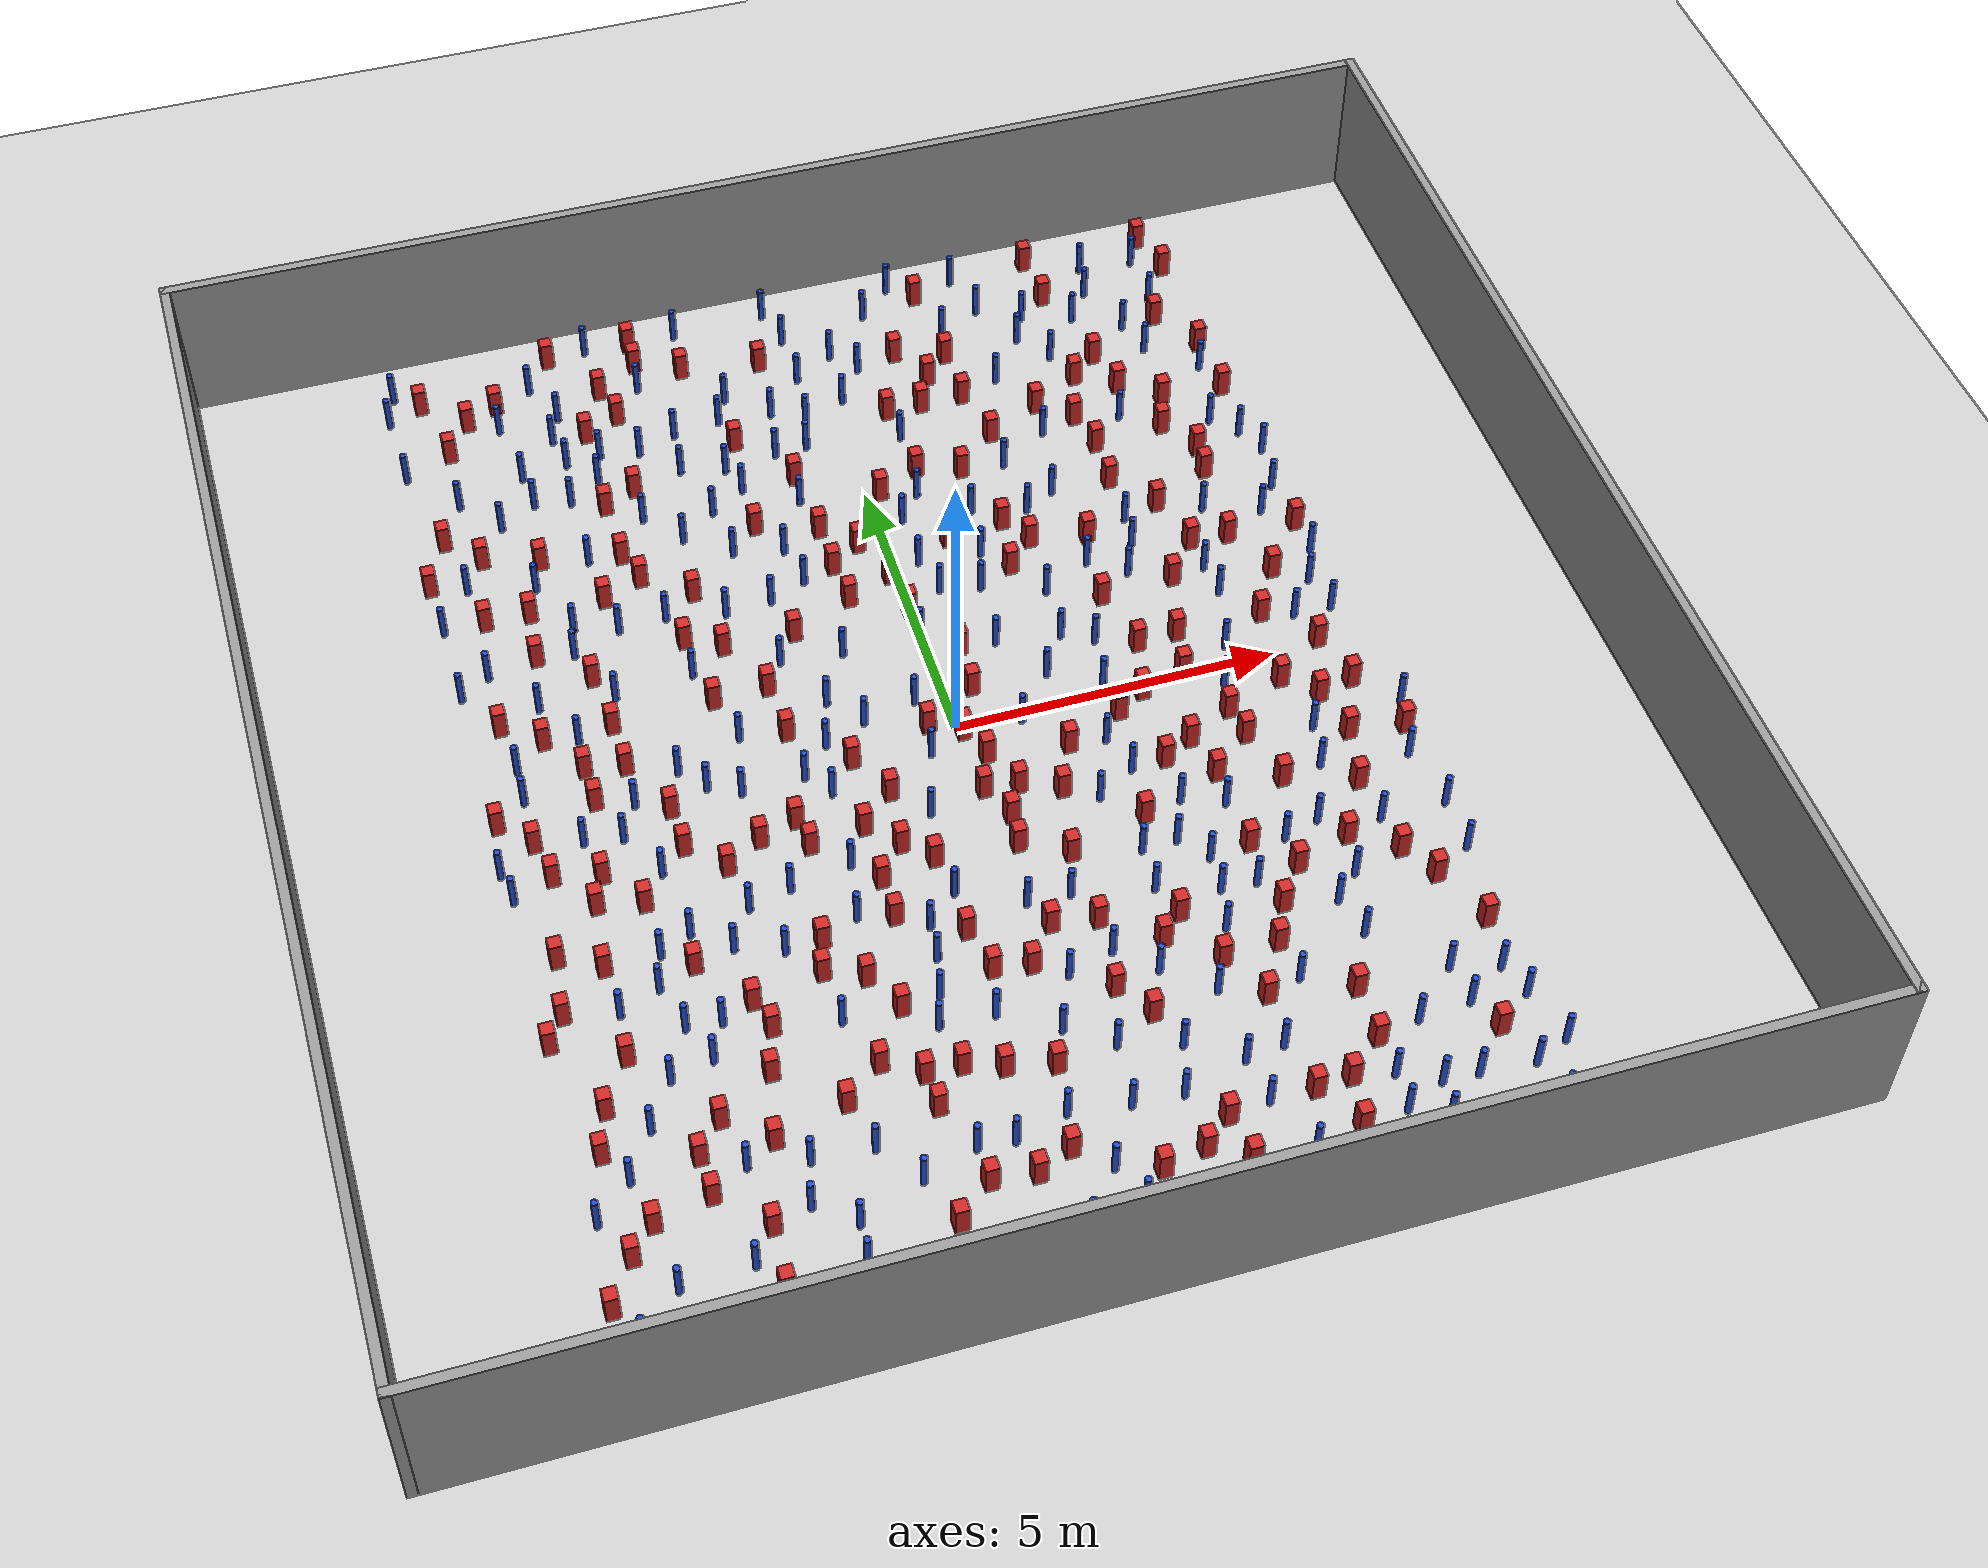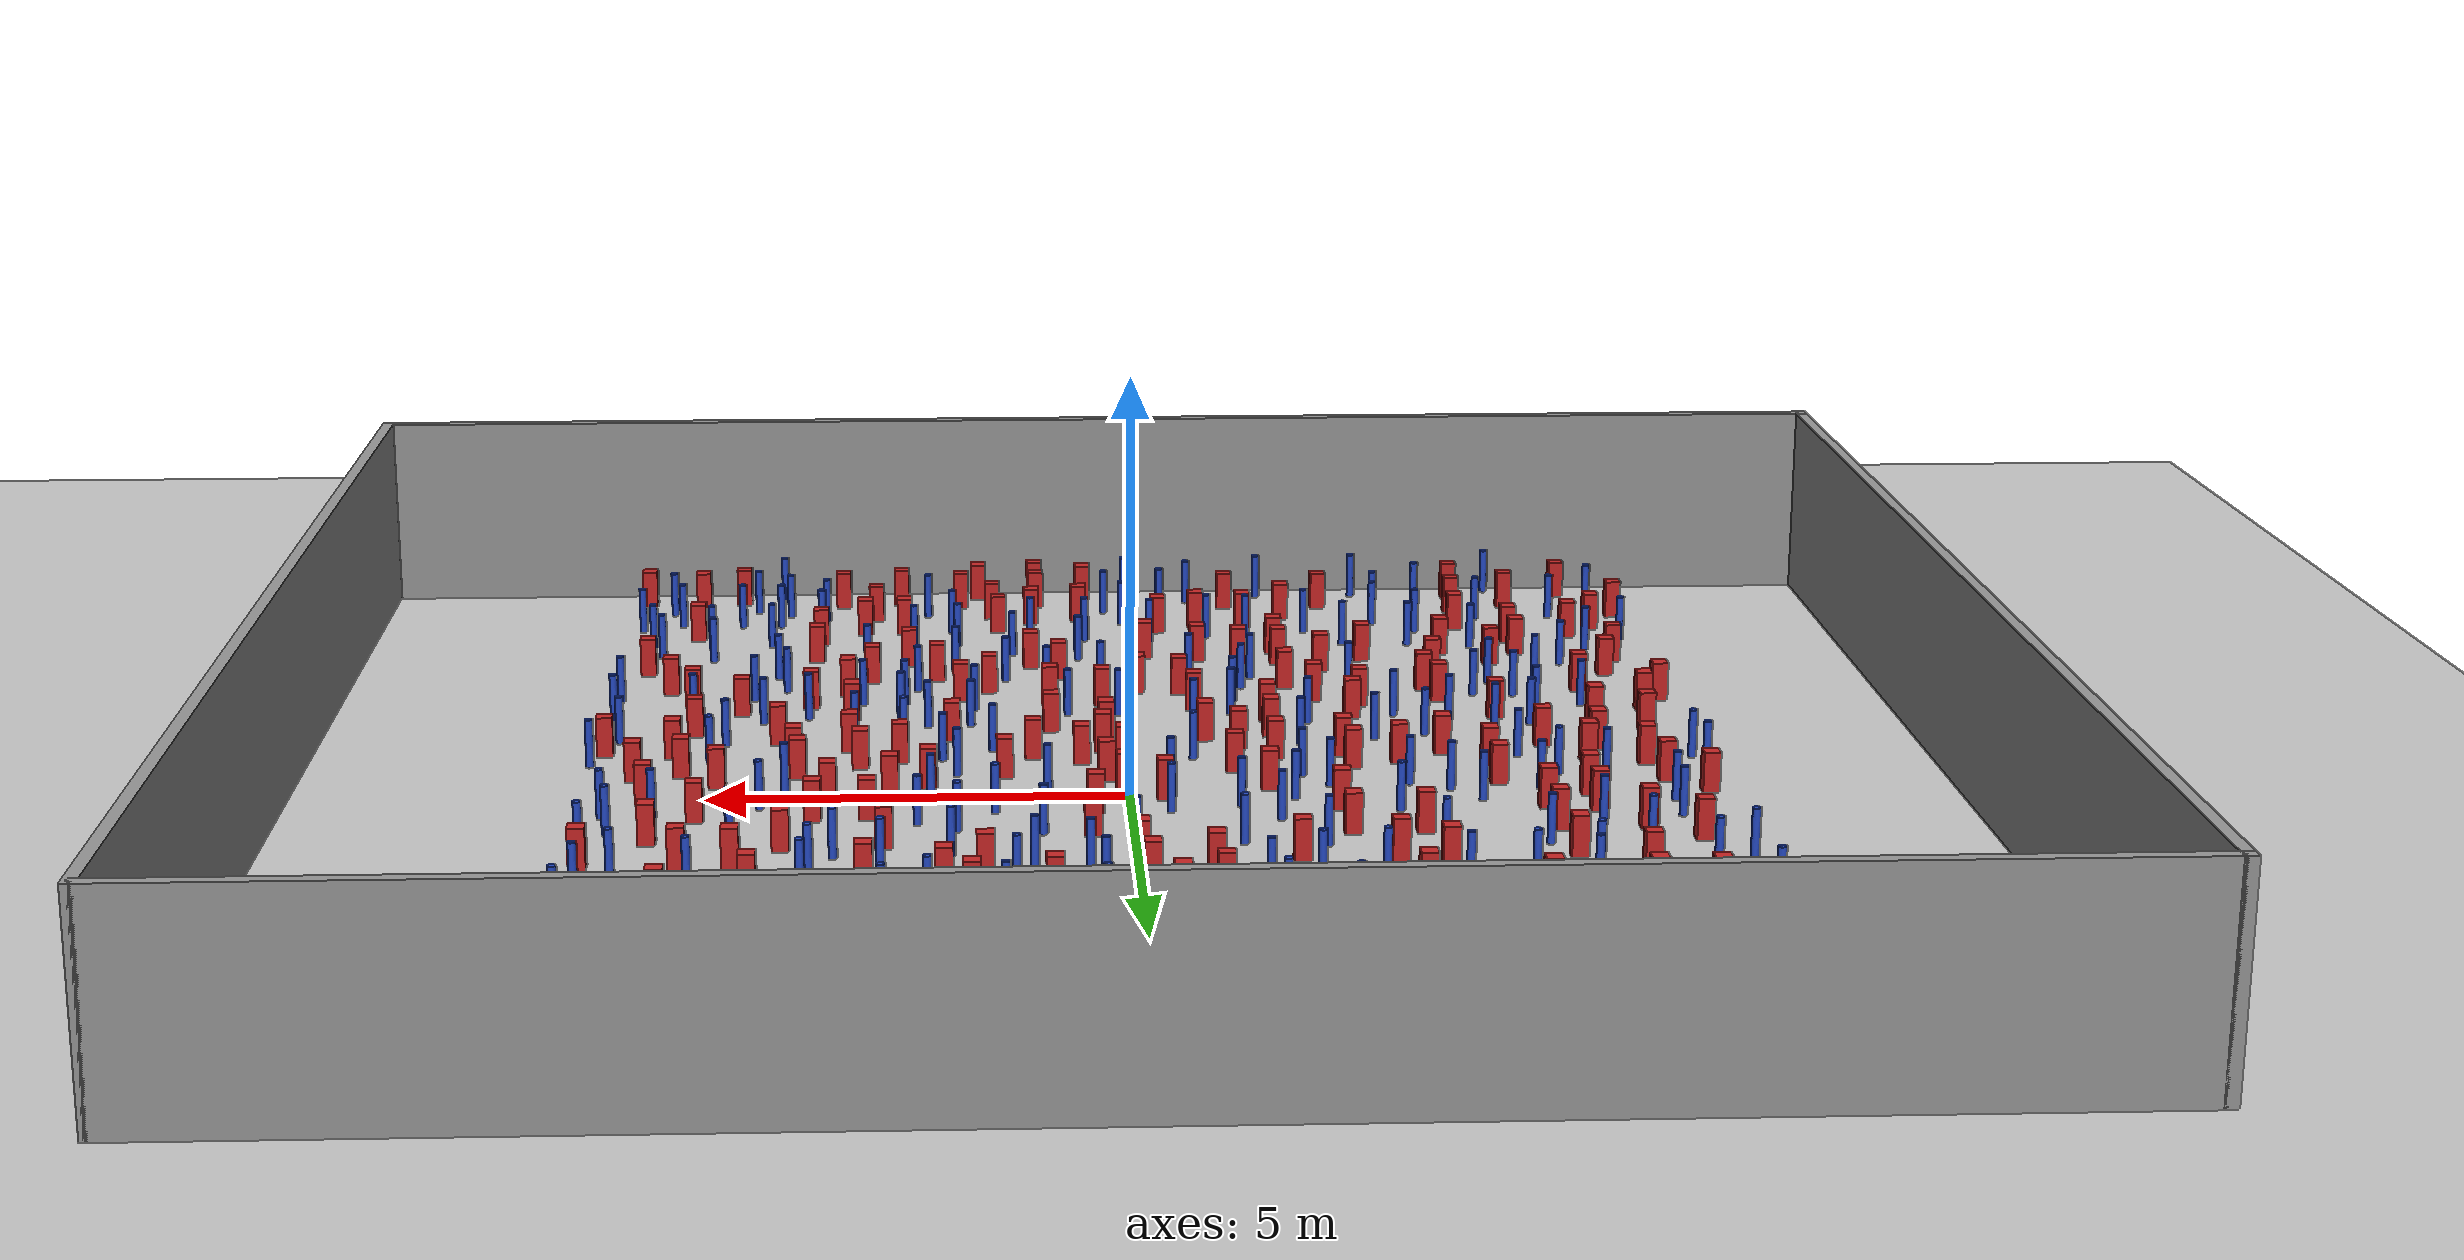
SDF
<sdf version="1.6">
 <world name="default">
  <light name="sun" type="directional">
   <pose>0 0 1000 0 -0 0</pose>
   <diffuse>0.8 0.8 0.8 1</diffuse>
   <specular>0.1 0.1 0.1 1</specular>
   <attenuation>
    <range>1000</range>
    <constant>0.9</constant>
    <linear>0.01</linear>
    <quadratic>0.001</quadratic>
   </attenuation>
   <direction>-0.5 0.5 -1</direction>
  </light>
  <model name="ground_plane">
   <static>1</static>
   <link name="link">
    <collision name="collision">
     <geometry><plane><normal>0 0 1</normal><size>100 100</size></plane></geometry>
     <surface><friction><ode><mu>100</mu><mu2>50</mu2></ode></friction></surface>
    </collision>
    <visual name="visual">
     <cast_shadows>0</cast_shadows>
     <geometry><plane><normal>0 0 1</normal><size>100 100</size></plane></geometry>
     <material>
      <ambient>1.0 1.0 1.0 1.0</ambient>
      <diffuse>0.8 0.8 0.8 1.0</diffuse>
      <specular>0.01 0.01 0.01 1.000000</specular>
     </material>
    </visual>
   </link>
  </model>
  <gravity>0 0 -9.8</gravity>
  <magnetic_field>6e-06 2.3e-05 -4.2e-05</magnetic_field>
  <atmosphere type="adiabatic"/>
  <physics name="default_physics" default="0" type="ode">
   <max_step_size>0.001</max_step_size>
   <real_time_factor>1</real_time_factor>
   <real_time_update_rate>1000</real_time_update_rate>
  </physics>
  <scene><ambient>0.4 0.4 0.4 1</ambient><background>0.7 0.7 0.7 1</background><shadows>1</shadows></scene>
  <spherical_coordinates>
   <surface_model>EARTH_WGS84</surface_model>
   <latitude_deg>0</latitude_deg>
   <longitude_deg>0</longitude_deg>
   <elevation>0</elevation>
   <heading_deg>0</heading_deg>
  </spherical_coordinates>
  <plugin name="gazebo_occupancy_map" filename="libgazebo_2Dmap_plugin.so">
   <map_resolution>0.05</map_resolution>
   <map_topic>generated_map</map_topic>
   <map_height>0.01</map_height>
   <map_size_x>50</map_size_x>
   <map_size_y>50</map_size_y>
  </plugin>
  <model name="NamedLocations">
   <static>true</static>
   <link name="DefaultStart"><pose>8.5 0 0 0 0 3.14</pose></link>
  </model>
  <model name="20x20_walls">
   <pose>0.044518 0.176112 0 0 -0 0</pose>
   <link name="Wall_1">
    <collision name="Wall_1_Collision">
     <geometry><box><size>20 0.15 2.5</size></box></geometry>
     <pose>0 0 1.25 0 -0 0</pose>
    </collision>
    <visual name="Wall_1_Visual">
     <pose>0 0 1.25 0 -0 0</pose>
     <geometry><box><size>20 0.15 2.5</size></box></geometry>
     <material>
      <script><uri>file://media/materials/scripts/gazebo.material</uri><name>Gazebo/Grey</name></script>
      <ambient>0.976471 0.992157 1 1</ambient>
     </material>
     <meta><layer>0</layer></meta>
    </visual>
    <pose>0 9.925 0 0 -0 0</pose>
   </link>
   <link name="Wall_3">
    <collision name="Wall_3_Collision">
     <geometry><box><size>20 0.15 2.5</size></box></geometry>
     <pose>0 0 1.25 0 -0 0</pose>
    </collision>
    <visual name="Wall_3_Visual">
     <pose>0 0 1.25 0 -0 0</pose>
     <geometry><box><size>20 0.15 2.5</size></box></geometry>
     <material>
      <script><uri>file://media/materials/scripts/gazebo.material</uri><name>Gazebo/Grey</name></script>
      <ambient>0.976471 0.992157 1 1</ambient>
     </material>
     <meta><layer>0</layer></meta>
    </visual>
    <pose>9.925 0 0 0 0 -1.5708</pose>
   </link>
   <link name="Wall_4">
    <collision name="Wall_4_Collision">
     <geometry><box><size>20 0.15 2.5</size></box></geometry>
     <pose>0 0 1.25 0 -0 0</pose>
    </collision>
    <visual name="Wall_4_Visual">
     <pose>0 0 1.25 0 -0 0</pose>
     <geometry><box><size>20 0.15 2.5</size></box></geometry>
     <material>
      <script><uri>file://media/materials/scripts/gazebo.material</uri><name>Gazebo/Grey</name></script>
      <ambient>0.976471 0.992157 1 1</ambient>
     </material>
     <meta><layer>0</layer></meta>
    </visual>
    <pose>0 -9.925 0 0 -0 3.14159</pose>
   </link>
   <link name="Wall_5">
    <collision name="Wall_5_Collision">
     <geometry><box><size>20 0.15 2.5</size></box></geometry>
     <pose>0 0 1.25 0 -0 0</pose>
    </collision>
    <visual name="Wall_5_Visual">
     <pose>0 0 1.25 0 -0 0</pose>
     <geometry><box><size>20 0.15 2.5</size></box></geometry>
     <material>
      <script><uri>file://media/materials/scripts/gazebo.material</uri><name>Gazebo/Grey</name></script>
      <ambient>0.976471 0.992157 1 1</ambient>
     </material>
     <meta><layer>0</layer></meta>
    </visual>
    <pose>-9.925 0 0 0 -0 1.5708</pose>
   </link>
   <static>1</static>
  </model>
  <model name="square_post_obstacle0">
   <static>true</static>
   <pose>-2.3891648593 -8.11974286736 1.91545236811e-07 -7.35059704564e-06 1.12565212e-07 2.39332434364e-05</pose>
   <link name="link">
    <pose>0 0 0.25 0 -0 0</pose>
    <inertial>
     <mass>100</mass>
     <inertia>
      <ixx>0.166667</ixx>
      <ixy>0</ixy>
      <ixz>0</ixz>
      <iyy>0.166667</iyy>
      <iyz>0</iyz>
      <izz>0.166667</izz>
     </inertia>
    </inertial>
    <collision name="collision"><geometry><box><size>.2 .2 .5</size></box></geometry></collision>
    <visual name="visual">
     <geometry><box><size>.2 .2 .5</size></box></geometry>
     <material>
      <script><name>Gazebo/Red</name><uri>file://media/materials/scripts/gazebo.material</uri></script>
     </material>
    </visual>
   </link>
  </model>
  <model name="square_post_obstacle1">
   <static>true</static>
   <pose>3.16889082667 -8.21501041184 1.91545236811e-07 -7.35059704564e-06 1.12565212e-07 2.39332434364e-05</pose>
   <link name="link">
    <pose>0 0 0.25 0 -0 0</pose>
    <inertial>
     <mass>100</mass>
     <inertia>
      <ixx>0.166667</ixx>
      <ixy>0</ixy>
      <ixz>0</ixz>
      <iyy>0.166667</iyy>
      <iyz>0</iyz>
      <izz>0.166667</izz>
     </inertia>
    </inertial>
    <collision name="collision"><geometry><box><size>.2 .2 .5</size></box></geometry></collision>
    <visual name="visual">
     <geometry><box><size>.2 .2 .5</size></box></geometry>
     <material>
      <script><name>Gazebo/Red</name><uri>file://media/materials/scripts/gazebo.material</uri></script>
     </material>
    </visual>
   </link>
  </model>
  <model name="pole_obstacle0">
   <static>true</static>
   <pose>3.24254973709 -4.00526755006 7.38925637345e-09 -8.47170692799e-08 1.24976764995e-08 -1.74513093021e-07</pose>
   <link name="link">
    <pose>0 0 0.3 0 -0 0</pose>
    <inertial>
     <mass>1</mass>
     <inertia><ixx>0.145833</ixx><ixy>0</ixy><ixz>0</ixz><iyy>0.145833</iyy><iyz>0</iyz><izz>0.125</izz></inertia>
    </inertial>
    <collision name="collision">
     <geometry><cylinder><radius>0.05</radius><length>.6</length></cylinder></geometry>
    </collision>
    <visual name="visual">
     <geometry><cylinder><radius>0.05</radius><length>.6</length></cylinder></geometry>
     <material>
      <script><name>Gazebo/Blue</name><uri>file://media/materials/scripts/gazebo.material</uri></script>
     </material>
    </visual>
   </link>
  </model>
  <model name="square_post_obstacle2">
   <static>true</static>
   <pose>-6.55330883712 5.80059143971 1.91545236811e-07 -7.35059704564e-06 1.12565212e-07 2.39332434364e-05</pose>
   <link name="link">
    <pose>0 0 0.25 0 -0 0</pose>
    <inertial>
     <mass>100</mass>
     <inertia>
      <ixx>0.166667</ixx>
      <ixy>0</ixy>
      <ixz>0</ixz>
      <iyy>0.166667</iyy>
      <iyz>0</iyz>
      <izz>0.166667</izz>
     </inertia>
    </inertial>
    <collision name="collision"><geometry><box><size>.2 .2 .5</size></box></geometry></collision>
    <visual name="visual">
     <geometry><box><size>.2 .2 .5</size></box></geometry>
     <material>
      <script><name>Gazebo/Red</name><uri>file://media/materials/scripts/gazebo.material</uri></script>
     </material>
    </visual>
   </link>
  </model>
  <model name="pole_obstacle1">
   <static>true</static>
   <pose>-6.42929872795 2.91907934474 7.38925637345e-09 -8.47170692798e-08 1.24976764937e-08 -1.74513093023e-07</pose>
   <link name="link">
    <pose>0 0 0.3 0 -0 0</pose>
    <inertial>
     <mass>1</mass>
     <inertia><ixx>0.145833</ixx><ixy>0</ixy><ixz>0</ixz><iyy>0.145833</iyy><iyz>0</iyz><izz>0.125</izz></inertia>
    </inertial>
    <collision name="collision">
     <geometry><cylinder><radius>0.05</radius><length>.6</length></cylinder></geometry>
    </collision>
    <visual name="visual">
     <geometry><cylinder><radius>0.05</radius><length>.6</length></cylinder></geometry>
     <material>
      <script><name>Gazebo/Blue</name><uri>file://media/materials/scripts/gazebo.material</uri></script>
     </material>
    </visual>
   </link>
  </model>
  <model name="square_post_obstacle3">
   <static>true</static>
   <pose>-3.45899502006 2.76230181526 1.91545236811e-07 -7.35059704564e-06 1.12565212e-07 2.39332434364e-05</pose>
   <link name="link">
    <pose>0 0 0.25 0 -0 0</pose>
    <inertial>
     <mass>100</mass>
     <inertia>
      <ixx>0.166667</ixx>
      <ixy>0</ixy>
      <ixz>0</ixz>
      <iyy>0.166667</iyy>
      <iyz>0</iyz>
      <izz>0.166667</izz>
     </inertia>
    </inertial>
    <collision name="collision"><geometry><box><size>.2 .2 .5</size></box></geometry></collision>
    <visual name="visual">
     <geometry><box><size>.2 .2 .5</size></box></geometry>
     <material>
      <script><name>Gazebo/Red</name><uri>file://media/materials/scripts/gazebo.material</uri></script>
     </material>
    </visual>
   </link>
  </model>
  <model name="pole_obstacle2">
   <static>true</static>
   <pose>-3.00983477498 -4.61173745461 7.38925637345e-09 -8.47170692798e-08 1.24976765033e-08 -1.74513093019e-07</pose>
   <link name="link">
    <pose>0 0 0.3 0 -0 0</pose>
    <inertial>
     <mass>1</mass>
     <inertia><ixx>0.145833</ixx><ixy>0</ixy><ixz>0</ixz><iyy>0.145833</iyy><iyz>0</iyz><izz>0.125</izz></inertia>
    </inertial>
    <collision name="collision">
     <geometry><cylinder><radius>0.05</radius><length>.6</length></cylinder></geometry>
    </collision>
    <visual name="visual">
     <geometry><cylinder><radius>0.05</radius><length>.6</length></cylinder></geometry>
     <material>
      <script><name>Gazebo/Blue</name><uri>file://media/materials/scripts/gazebo.material</uri></script>
     </material>
    </visual>
   </link>
  </model>
  <model name="pole_obstacle3">
   <static>true</static>
   <pose>0.546766999606 2.6899849425 7.38925637345e-09 -8.471706928e-08 1.2497676512e-08 -1.74513093015e-07</pose>
   <link name="link">
    <pose>0 0 0.3 0 -0 0</pose>
    <inertial>
     <mass>1</mass>
     <inertia><ixx>0.145833</ixx><ixy>0</ixy><ixz>0</ixz><iyy>0.145833</iyy><iyz>0</iyz><izz>0.125</izz></inertia>
    </inertial>
    <collision name="collision">
     <geometry><cylinder><radius>0.05</radius><length>.6</length></cylinder></geometry>
    </collision>
    <visual name="visual">
     <geometry><cylinder><radius>0.05</radius><length>.6</length></cylinder></geometry>
     <material>
      <script><name>Gazebo/Blue</name><uri>file://media/materials/scripts/gazebo.material</uri></script>
     </material>
    </visual>
   </link>
  </model>
  <model name="square_post_obstacle4">
   <static>true</static>
   <pose>-5.7031438525 8.30815203388 1.91545236811e-07 -7.35059704564e-06 1.12565212e-07 2.39332434364e-05</pose>
   <link name="link">
    <pose>0 0 0.25 0 -0 0</pose>
    <inertial>
     <mass>100</mass>
     <inertia>
      <ixx>0.166667</ixx>
      <ixy>0</ixy>
      <ixz>0</ixz>
      <iyy>0.166667</iyy>
      <iyz>0</iyz>
      <izz>0.166667</izz>
     </inertia>
    </inertial>
    <collision name="collision"><geometry><box><size>.2 .2 .5</size></box></geometry></collision>
    <visual name="visual">
     <geometry><box><size>.2 .2 .5</size></box></geometry>
     <material>
      <script><name>Gazebo/Red</name><uri>file://media/materials/scripts/gazebo.material</uri></script>
     </material>
    </visual>
   </link>
  </model>
  <model name="square_post_obstacle5">
   <static>true</static>
   <pose>-2.180293744 -4.64362342363 1.91545236811e-07 -7.35059704564e-06 1.12565212e-07 2.39332434364e-05</pose>
   <link name="link">
    <pose>0 0 0.25 0 -0 0</pose>
    <inertial>
     <mass>100</mass>
     <inertia>
      <ixx>0.166667</ixx>
      <ixy>0</ixy>
      <ixz>0</ixz>
      <iyy>0.166667</iyy>
      <iyz>0</iyz>
      <izz>0.166667</izz>
     </inertia>
    </inertial>
    <collision name="collision"><geometry><box><size>.2 .2 .5</size></box></geometry></collision>
    <visual name="visual">
     <geometry><box><size>.2 .2 .5</size></box></geometry>
     <material>
      <script><name>Gazebo/Red</name><uri>file://media/materials/scripts/gazebo.material</uri></script>
     </material>
    </visual>
   </link>
  </model>
  <model name="square_post_obstacle6">
   <static>true</static>
   <pose>2.73595648026 -1.51727002082 1.91545236811e-07 -7.35059704564e-06 1.12565212e-07 2.39332434364e-05</pose>
   <link name="link">
    <pose>0 0 0.25 0 -0 0</pose>
    <inertial>
     <mass>100</mass>
     <inertia>
      <ixx>0.166667</ixx>
      <ixy>0</ixy>
      <ixz>0</ixz>
      <iyy>0.166667</iyy>
      <iyz>0</iyz>
      <izz>0.166667</izz>
     </inertia>
    </inertial>
    <collision name="collision"><geometry><box><size>.2 .2 .5</size></box></geometry></collision>
    <visual name="visual">
     <geometry><box><size>.2 .2 .5</size></box></geometry>
     <material>
      <script><name>Gazebo/Red</name><uri>file://media/materials/scripts/gazebo.material</uri></script>
     </material>
    </visual>
   </link>
  </model>
  <model name="pole_obstacle4">
   <static>true</static>
   <pose>-3.96188056806 6.49615191888 7.38925637345e-09 -8.47170692799e-08 1.24976764985e-08 -1.74513093022e-07</pose>
   <link name="link">
    <pose>0 0 0.3 0 -0 0</pose>
    <inertial>
     <mass>1</mass>
     <inertia><ixx>0.145833</ixx><ixy>0</ixy><ixz>0</ixz><iyy>0.145833</iyy><iyz>0</iyz><izz>0.125</izz></inertia>
    </inertial>
    <collision name="collision">
     <geometry><cylinder><radius>0.05</radius><length>.6</length></cylinder></geometry>
    </collision>
    <visual name="visual">
     <geometry><cylinder><radius>0.05</radius><length>.6</length></cylinder></geometry>
     <material>
      <script><name>Gazebo/Blue</name><uri>file://media/materials/scripts/gazebo.material</uri></script>
     </material>
    </visual>
   </link>
  </model>
  <model name="pole_obstacle5">
   <static>true</static>
   <pose>4.39153985955 7.93179065304 7.38925637345e-09 -8.47170692796e-08 1.24976764786e-08 -1.74513093032e-07</pose>
   <link name="link">
    <pose>0 0 0.3 0 -0 0</pose>
    <inertial>
     <mass>1</mass>
     <inertia><ixx>0.145833</ixx><ixy>0</ixy><ixz>0</ixz><iyy>0.145833</iyy><iyz>0</iyz><izz>0.125</izz></inertia>
    </inertial>
    <collision name="collision">
     <geometry><cylinder><radius>0.05</radius><length>.6</length></cylinder></geometry>
    </collision>
    <visual name="visual">
     <geometry><cylinder><radius>0.05</radius><length>.6</length></cylinder></geometry>
     <material>
      <script><name>Gazebo/Blue</name><uri>file://media/materials/scripts/gazebo.material</uri></script>
     </material>
    </visual>
   </link>
  </model>
  <model name="square_post_obstacle7">
   <static>true</static>
   <pose>-2.71536622169 -5.4466309811 1.91545236811e-07 -7.35059704564e-06 1.12565212e-07 2.39332434364e-05</pose>
   <link name="link">
    <pose>0 0 0.25 0 -0 0</pose>
    <inertial>
     <mass>100</mass>
     <inertia>
      <ixx>0.166667</ixx>
      <ixy>0</ixy>
      <ixz>0</ixz>
      <iyy>0.166667</iyy>
      <iyz>0</iyz>
      <izz>0.166667</izz>
     </inertia>
    </inertial>
    <collision name="collision"><geometry><box><size>.2 .2 .5</size></box></geometry></collision>
    <visual name="visual">
     <geometry><box><size>.2 .2 .5</size></box></geometry>
     <material>
      <script><name>Gazebo/Red</name><uri>file://media/materials/scripts/gazebo.material</uri></script>
     </material>
    </visual>
   </link>
  </model>
  <model name="square_post_obstacle8">
   <static>true</static>
   <pose>0.0272128510297 -1.29698474354 1.91545236811e-07 -7.35059704564e-06 1.12565212e-07 2.39332434364e-05</pose>
   <link name="link">
    <pose>0 0 0.25 0 -0 0</pose>
    <inertial>
     <mass>100</mass>
     <inertia>
      <ixx>0.166667</ixx>
      <ixy>0</ixy>
      <ixz>0</ixz>
      <iyy>0.166667</iyy>
      <iyz>0</iyz>
      <izz>0.166667</izz>
     </inertia>
    </inertial>
    <collision name="collision"><geometry><box><size>.2 .2 .5</size></box></geometry></collision>
    <visual name="visual">
     <geometry><box><size>.2 .2 .5</size></box></geometry>
     <material>
      <script><name>Gazebo/Red</name><uri>file://media/materials/scripts/gazebo.material</uri></script>
     </material>
    </visual>
   </link>
  </model>
  <model name="pole_obstacle6">
   <static>true</static>
   <pose>5.76742457301 4.99722311599 7.38925637345e-09 -8.47170692796e-08 1.24976764786e-08 -1.74513093032e-07</pose>
   <link name="link">
    <pose>0 0 0.3 0 -0 0</pose>
    <inertial>
     <mass>1</mass>
     <inertia><ixx>0.145833</ixx><ixy>0</ixy><ixz>0</ixz><iyy>0.145833</iyy><iyz>0</iyz><izz>0.125</izz></inertia>
    </inertial>
    <collision name="collision">
     <geometry><cylinder><radius>0.05</radius><length>.6</length></cylinder></geometry>
    </collision>
    <visual name="visual">
     <geometry><cylinder><radius>0.05</radius><length>.6</length></cylinder></geometry>
     <material>
      <script><name>Gazebo/Blue</name><uri>file://media/materials/scripts/gazebo.material</uri></script>
     </material>
    </visual>
   </link>
  </model>
  <model name="pole_obstacle7">
   <static>true</static>
   <pose>3.74739690199 3.30398144632 7.38925637345e-09 -8.47170692798e-08 1.24976764939e-08 -1.74513093025e-07</pose>
   <link name="link">
    <pose>0 0 0.3 0 -0 0</pose>
    <inertial>
     <mass>1</mass>
     <inertia><ixx>0.145833</ixx><ixy>0</ixy><ixz>0</ixz><iyy>0.145833</iyy><iyz>0</iyz><izz>0.125</izz></inertia>
    </inertial>
    <collision name="collision">
     <geometry><cylinder><radius>0.05</radius><length>.6</length></cylinder></geometry>
    </collision>
    <visual name="visual">
     <geometry><cylinder><radius>0.05</radius><length>.6</length></cylinder></geometry>
     <material>
      <script><name>Gazebo/Blue</name><uri>file://media/materials/scripts/gazebo.material</uri></script>
     </material>
    </visual>
   </link>
  </model>
  <model name="square_post_obstacle9">
   <static>true</static>
   <pose>-0.905078219884 3.59624943873 1.91545236811e-07 -7.35059704564e-06 1.12565212e-07 2.39332434364e-05</pose>
   <link name="link">
    <pose>0 0 0.25 0 -0 0</pose>
    <inertial>
     <mass>100</mass>
     <inertia>
      <ixx>0.166667</ixx>
      <ixy>0</ixy>
      <ixz>0</ixz>
      <iyy>0.166667</iyy>
      <iyz>0</iyz>
      <izz>0.166667</izz>
     </inertia>
    </inertial>
    <collision name="collision"><geometry><box><size>.2 .2 .5</size></box></geometry></collision>
    <visual name="visual">
     <geometry><box><size>.2 .2 .5</size></box></geometry>
     <material>
      <script><name>Gazebo/Red</name><uri>file://media/materials/scripts/gazebo.material</uri></script>
     </material>
    </visual>
   </link>
  </model>
  <model name="square_post_obstacle10">
   <static>true</static>
   <pose>-4.72876855023 -3.14238741932 1.91545236811e-07 -7.35059704564e-06 1.12565212e-07 2.39332434364e-05</pose>
   <link name="link">
    <pose>0 0 0.25 0 -0 0</pose>
    <inertial>
     <mass>100</mass>
     <inertia>
      <ixx>0.166667</ixx>
      <ixy>0</ixy>
      <ixz>0</ixz>
      <iyy>0.166667</iyy>
      <iyz>0</iyz>
      <izz>0.166667</izz>
     </inertia>
    </inertial>
    <collision name="collision"><geometry><box><size>.2 .2 .5</size></box></geometry></collision>
    <visual name="visual">
     <geometry><box><size>.2 .2 .5</size></box></geometry>
     <material>
      <script><name>Gazebo/Red</name><uri>file://media/materials/scripts/gazebo.material</uri></script>
     </material>
    </visual>
   </link>
  </model>
  <model name="square_post_obstacle11">
   <static>true</static>
   <pose>-6.29754847552 -1.08779055697 1.91545236811e-07 -7.35059704564e-06 1.12565212e-07 2.39332434364e-05</pose>
   <link name="link">
    <pose>0 0 0.25 0 -0 0</pose>
    <inertial>
     <mass>100</mass>
     <inertia>
      <ixx>0.166667</ixx>
      <ixy>0</ixy>
      <ixz>0</ixz>
      <iyy>0.166667</iyy>
      <iyz>0</iyz>
      <izz>0.166667</izz>
     </inertia>
    </inertial>
    <collision name="collision"><geometry><box><size>.2 .2 .5</size></box></geometry></collision>
    <visual name="visual">
     <geometry><box><size>.2 .2 .5</size></box></geometry>
     <material>
      <script><name>Gazebo/Red</name><uri>file://media/materials/scripts/gazebo.material</uri></script>
     </material>
    </visual>
   </link>
  </model>
  <model name="square_post_obstacle12">
   <static>true</static>
   <pose>0.404167594741 -8.10818118871 1.91545236811e-07 -7.35059704564e-06 1.12565212e-07 2.39332434364e-05</pose>
   <link name="link">
    <pose>0 0 0.25 0 -0 0</pose>
    <inertial>
     <mass>100</mass>
     <inertia>
      <ixx>0.166667</ixx>
      <ixy>0</ixy>
      <ixz>0</ixz>
      <iyy>0.166667</iyy>
      <iyz>0</iyz>
      <izz>0.166667</izz>
     </inertia>
    </inertial>
    <collision name="collision"><geometry><box><size>.2 .2 .5</size></box></geometry></collision>
    <visual name="visual">
     <geometry><box><size>.2 .2 .5</size></box></geometry>
     <material>
      <script><name>Gazebo/Red</name><uri>file://media/materials/scripts/gazebo.material</uri></script>
     </material>
    </visual>
   </link>
  </model>
  <model name="square_post_obstacle13">
   <static>true</static>
   <pose>-3.32114091501 1.47154276022 1.91545236811e-07 -7.35059704564e-06 1.12565212e-07 2.39332434364e-05</pose>
   <link name="link">
    <pose>0 0 0.25 0 -0 0</pose>
    <inertial>
     <mass>100</mass>
     <inertia>
      <ixx>0.166667</ixx>
      <ixy>0</ixy>
      <ixz>0</ixz>
      <iyy>0.166667</iyy>
      <iyz>0</iyz>
      <izz>0.166667</izz>
     </inertia>
    </inertial>
    <collision name="collision"><geometry><box><size>.2 .2 .5</size></box></geometry></collision>
    <visual name="visual">
     <geometry><box><size>.2 .2 .5</size></box></geometry>
     <material>
      <script><name>Gazebo/Red</name><uri>file://media/materials/scripts/gazebo.material</uri></script>
     </material>
    </visual>
   </link>
  </model>
  <model name="pole_obstacle8">
   <static>true</static>
   <pose>5.13573356694 7.50833738013 7.38925637345e-09 -8.47170692796e-08 1.24976764786e-08 -1.74513093032e-07</pose>
   <link name="link">
    <pose>0 0 0.3 0 -0 0</pose>
    <inertial>
     <mass>1</mass>
     <inertia><ixx>0.145833</ixx><ixy>0</ixy><ixz>0</ixz><iyy>0.145833</iyy><iyz>0</iyz><izz>0.125</izz></inertia>
    </inertial>
    <collision name="collision">
     <geometry><cylinder><radius>0.05</radius><length>.6</length></cylinder></geometry>
    </collision>
    <visual name="visual">
     <geometry><cylinder><radius>0.05</radius><length>.6</length></cylinder></geometry>
     <material>
      <script><name>Gazebo/Blue</name><uri>file://media/materials/scripts/gazebo.material</uri></script>
     </material>
    </visual>
   </link>
  </model>
  <model name="square_post_obstacle14">
   <static>true</static>
   <pose>0.232962370025 4.91819987416 1.91545236811e-07 -7.35059704564e-06 1.12565212e-07 2.39332434364e-05</pose>
   <link name="link">
    <pose>0 0 0.25 0 -0 0</pose>
    <inertial>
     <mass>100</mass>
     <inertia>
      <ixx>0.166667</ixx>
      <ixy>0</ixy>
      <ixz>0</ixz>
      <iyy>0.166667</iyy>
      <iyz>0</iyz>
      <izz>0.166667</izz>
     </inertia>
    </inertial>
    <collision name="collision"><geometry><box><size>.2 .2 .5</size></box></geometry></collision>
    <visual name="visual">
     <geometry><box><size>.2 .2 .5</size></box></geometry>
     <material>
      <script><name>Gazebo/Red</name><uri>file://media/materials/scripts/gazebo.material</uri></script>
     </material>
    </visual>
   </link>
  </model>
  <model name="square_post_obstacle15">
   <static>true</static>
   <pose>1.50309372421 -7.58272821332 1.91545236811e-07 -7.35059704564e-06 1.12565212e-07 2.39332434364e-05</pose>
   <link name="link">
    <pose>0 0 0.25 0 -0 0</pose>
    <inertial>
     <mass>100</mass>
     <inertia>
      <ixx>0.166667</ixx>
      <ixy>0</ixy>
      <ixz>0</ixz>
      <iyy>0.166667</iyy>
      <iyz>0</iyz>
      <izz>0.166667</izz>
     </inertia>
    </inertial>
    <collision name="collision"><geometry><box><size>.2 .2 .5</size></box></geometry></collision>
    <visual name="visual">
     <geometry><box><size>.2 .2 .5</size></box></geometry>
     <material>
      <script><name>Gazebo/Red</name><uri>file://media/materials/scripts/gazebo.material</uri></script>
     </material>
    </visual>
   </link>
  </model>
  <model name="square_post_obstacle16">
   <static>true</static>
   <pose>3.90854082336 -6.12980230415 1.91545236811e-07 -7.35059704564e-06 1.12565212e-07 2.39332434364e-05</pose>
   <link name="link">
    <pose>0 0 0.25 0 -0 0</pose>
    <inertial>
     <mass>100</mass>
     <inertia>
      <ixx>0.166667</ixx>
      <ixy>0</ixy>
      <ixz>0</ixz>
      <iyy>0.166667</iyy>
      <iyz>0</iyz>
      <izz>0.166667</izz>
     </inertia>
    </inertial>
    <collision name="collision"><geometry><box><size>.2 .2 .5</size></box></geometry></collision>
    <visual name="visual">
     <geometry><box><size>.2 .2 .5</size></box></geometry>
     <material>
      <script><name>Gazebo/Red</name><uri>file://media/materials/scripts/gazebo.material</uri></script>
     </material>
    </visual>
   </link>
  </model>
  <model name="pole_obstacle9">
   <static>true</static>
   <pose>-4.87674963518 -0.105442005914 7.38925637345e-09 -8.47170692799e-08 1.24976765039e-08 -1.74513093019e-07</pose>
   <link name="link">
    <pose>0 0 0.3 0 -0 0</pose>
    <inertial>
     <mass>1</mass>
     <inertia><ixx>0.145833</ixx><ixy>0</ixy><ixz>0</ixz><iyy>0.145833</iyy><iyz>0</iyz><izz>0.125</izz></inertia>
    </inertial>
    <collision name="collision">
     <geometry><cylinder><radius>0.05</radius><length>.6</length></cylinder></geometry>
    </collision>
    <visual name="visual">
     <geometry><cylinder><radius>0.05</radius><length>.6</length></cylinder></geometry>
     <material>
      <script><name>Gazebo/Blue</name><uri>file://media/materials/scripts/gazebo.material</uri></script>
     </material>
    </visual>
   </link>
  </model>
  <model name="square_post_obstacle17">
   <static>true</static>
   <pose>-4.99143158666 -5.68737844783 1.91545236811e-07 -7.35059704564e-06 1.12565212e-07 2.39332434364e-05</pose>
   <link name="link">
    <pose>0 0 0.25 0 -0 0</pose>
    <inertial>
     <mass>100</mass>
     <inertia>
      <ixx>0.166667</ixx>
      <ixy>0</ixy>
      <ixz>0</ixz>
      <iyy>0.166667</iyy>
      <iyz>0</iyz>
      <izz>0.166667</izz>
     </inertia>
    </inertial>
    <collision name="collision"><geometry><box><size>.2 .2 .5</size></box></geometry></collision>
    <visual name="visual">
     <geometry><box><size>.2 .2 .5</size></box></geometry>
     <material>
      <script><name>Gazebo/Red</name><uri>file://media/materials/scripts/gazebo.material</uri></script>
     </material>
    </visual>
   </link>
  </model>
  <model name="square_post_obstacle18">
   <static>true</static>
   <pose>2.83658373215 -9.09488576402 1.91545236811e-07 -7.35059704564e-06 1.12565212e-07 2.39332434364e-05</pose>
   <link name="link">
    <pose>0 0 0.25 0 -0 0</pose>
    <inertial>
     <mass>100</mass>
     <inertia>
      <ixx>0.166667</ixx>
      <ixy>0</ixy>
      <ixz>0</ixz>
      <iyy>0.166667</iyy>
      <iyz>0</iyz>
      <izz>0.166667</izz>
     </inertia>
    </inertial>
    <collision name="collision"><geometry><box><size>.2 .2 .5</size></box></geometry></collision>
    <visual name="visual">
     <geometry><box><size>.2 .2 .5</size></box></geometry>
     <material>
      <script><name>Gazebo/Red</name><uri>file://media/materials/scripts/gazebo.material</uri></script>
     </material>
    </visual>
   </link>
  </model>
  <model name="pole_obstacle10">
   <static>true</static>
   <pose>-1.12531300826 6.25755355994 7.38925637345e-09 -8.47170692799e-08 1.24976765033e-08 -1.74513093018e-07</pose>
   <link name="link">
    <pose>0 0 0.3 0 -0 0</pose>
    <inertial>
     <mass>1</mass>
     <inertia><ixx>0.145833</ixx><ixy>0</ixy><ixz>0</ixz><iyy>0.145833</iyy><iyz>0</iyz><izz>0.125</izz></inertia>
    </inertial>
    <collision name="collision">
     <geometry><cylinder><radius>0.05</radius><length>.6</length></cylinder></geometry>
    </collision>
    <visual name="visual">
     <geometry><cylinder><radius>0.05</radius><length>.6</length></cylinder></geometry>
     <material>
      <script><name>Gazebo/Blue</name><uri>file://media/materials/scripts/gazebo.material</uri></script>
     </material>
    </visual>
   </link>
  </model>
  <model name="square_post_obstacle19">
   <static>true</static>
   <pose>-4.1564367619 -5.15919785899 1.91545236811e-07 -7.35059704564e-06 1.12565212e-07 2.39332434364e-05</pose>
   <link name="link">
    <pose>0 0 0.25 0 -0 0</pose>
    <inertial>
     <mass>100</mass>
     <inertia>
      <ixx>0.166667</ixx>
      <ixy>0</ixy>
      <ixz>0</ixz>
      <iyy>0.166667</iyy>
      <iyz>0</iyz>
      <izz>0.166667</izz>
     </inertia>
    </inertial>
    <collision name="collision"><geometry><box><size>.2 .2 .5</size></box></geometry></collision>
    <visual name="visual">
     <geometry><box><size>.2 .2 .5</size></box></geometry>
     <material>
      <script><name>Gazebo/Red</name><uri>file://media/materials/scripts/gazebo.material</uri></script>
     </material>
    </visual>
   </link>
  </model>
  <model name="pole_obstacle11">
   <static>true</static>
   <pose>-5.47349286889 -4.87875105383 7.38925637345e-09 -8.47170692796e-08 1.24976764786e-08 -1.74513093032e-07</pose>
   <link name="link">
    <pose>0 0 0.3 0 -0 0</pose>
    <inertial>
     <mass>1</mass>
     <inertia><ixx>0.145833</ixx><ixy>0</ixy><ixz>0</ixz><iyy>0.145833</iyy><iyz>0</iyz><izz>0.125</izz></inertia>
    </inertial>
    <collision name="collision">
     <geometry><cylinder><radius>0.05</radius><length>.6</length></cylinder></geometry>
    </collision>
    <visual name="visual">
     <geometry><cylinder><radius>0.05</radius><length>.6</length></cylinder></geometry>
     <material>
      <script><name>Gazebo/Blue</name><uri>file://media/materials/scripts/gazebo.material</uri></script>
     </material>
    </visual>
   </link>
  </model>
  <model name="square_post_obstacle20">
   <static>true</static>
   <pose>-4.38597647848 -1.08295122738 1.91545236811e-07 -7.35059704564e-06 1.12565212e-07 2.39332434364e-05</pose>
   <link name="link">
    <pose>0 0 0.25 0 -0 0</pose>
    <inertial>
     <mass>100</mass>
     <inertia>
      <ixx>0.166667</ixx>
      <ixy>0</ixy>
      <ixz>0</ixz>
      <iyy>0.166667</iyy>
      <iyz>0</iyz>
      <izz>0.166667</izz>
     </inertia>
    </inertial>
    <collision name="collision"><geometry><box><size>.2 .2 .5</size></box></geometry></collision>
    <visual name="visual">
     <geometry><box><size>.2 .2 .5</size></box></geometry>
     <material>
      <script><name>Gazebo/Red</name><uri>file://media/materials/scripts/gazebo.material</uri></script>
     </material>
    </visual>
   </link>
  </model>
  <model name="pole_obstacle12">
   <static>true</static>
   <pose>-1.02231490212 5.12306557846 7.38925637345e-09 -8.47170692799e-08 1.2497676505e-08 -1.74513093018e-07</pose>
   <link name="link">
    <pose>0 0 0.3 0 -0 0</pose>
    <inertial>
     <mass>1</mass>
     <inertia><ixx>0.145833</ixx><ixy>0</ixy><ixz>0</ixz><iyy>0.145833</iyy><iyz>0</iyz><izz>0.125</izz></inertia>
    </inertial>
    <collision name="collision">
     <geometry><cylinder><radius>0.05</radius><length>.6</length></cylinder></geometry>
    </collision>
    <visual name="visual">
     <geometry><cylinder><radius>0.05</radius><length>.6</length></cylinder></geometry>
     <material>
      <script><name>Gazebo/Blue</name><uri>file://media/materials/scripts/gazebo.material</uri></script>
     </material>
    </visual>
   </link>
  </model>
  <model name="square_post_obstacle21">
   <static>true</static>
   <pose>-3.87190733849 -1.61479346282 1.91545236811e-07 -7.35059704564e-06 1.12565212e-07 2.39332434364e-05</pose>
   <link name="link">
    <pose>0 0 0.25 0 -0 0</pose>
    <inertial>
     <mass>100</mass>
     <inertia>
      <ixx>0.166667</ixx>
      <ixy>0</ixy>
      <ixz>0</ixz>
      <iyy>0.166667</iyy>
      <iyz>0</iyz>
      <izz>0.166667</izz>
     </inertia>
    </inertial>
    <collision name="collision"><geometry><box><size>.2 .2 .5</size></box></geometry></collision>
    <visual name="visual">
     <geometry><box><size>.2 .2 .5</size></box></geometry>
     <material>
      <script><name>Gazebo/Red</name><uri>file://media/materials/scripts/gazebo.material</uri></script>
     </material>
    </visual>
   </link>
  </model>
  <model name="pole_obstacle13">
   <static>true</static>
   <pose>0.784797845011 4.74809284061 7.38925637345e-09 -8.471706928e-08 1.24976765086e-08 -1.74513093015e-07</pose>
   <link name="link">
    <pose>0 0 0.3 0 -0 0</pose>
    <inertial>
     <mass>1</mass>
     <inertia><ixx>0.145833</ixx><ixy>0</ixy><ixz>0</ixz><iyy>0.145833</iyy><iyz>0</iyz><izz>0.125</izz></inertia>
    </inertial>
    <collision name="collision">
     <geometry><cylinder><radius>0.05</radius><length>.6</length></cylinder></geometry>
    </collision>
    <visual name="visual">
     <geometry><cylinder><radius>0.05</radius><length>.6</length></cylinder></geometry>
     <material>
      <script><name>Gazebo/Blue</name><uri>file://media/materials/scripts/gazebo.material</uri></script>
     </material>
    </visual>
   </link>
  </model>
  <model name="square_post_obstacle22">
   <static>true</static>
   <pose>0.874387646557 -3.99899920464 1.91545236811e-07 -7.35059704564e-06 1.12565212e-07 2.39332434364e-05</pose>
   <link name="link">
    <pose>0 0 0.25 0 -0 0</pose>
    <inertial>
     <mass>100</mass>
     <inertia>
      <ixx>0.166667</ixx>
      <ixy>0</ixy>
      <ixz>0</ixz>
      <iyy>0.166667</iyy>
      <iyz>0</iyz>
      <izz>0.166667</izz>
     </inertia>
    </inertial>
    <collision name="collision"><geometry><box><size>.2 .2 .5</size></box></geometry></collision>
    <visual name="visual">
     <geometry><box><size>.2 .2 .5</size></box></geometry>
     <material>
      <script><name>Gazebo/Red</name><uri>file://media/materials/scripts/gazebo.material</uri></script>
     </material>
    </visual>
   </link>
  </model>
  <model name="pole_obstacle14">
   <static>true</static>
   <pose>-1.28186081582 0.451107271071 7.38925637345e-09 -8.47170692799e-08 1.24976765052e-08 -1.74513093018e-07</pose>
   <link name="link">
    <pose>0 0 0.3 0 -0 0</pose>
    <inertial>
     <mass>1</mass>
     <inertia><ixx>0.145833</ixx><ixy>0</ixy><ixz>0</ixz><iyy>0.145833</iyy><iyz>0</iyz><izz>0.125</izz></inertia>
    </inertial>
    <collision name="collision">
     <geometry><cylinder><radius>0.05</radius><length>.6</length></cylinder></geometry>
    </collision>
    <visual name="visual">
     <geometry><cylinder><radius>0.05</radius><length>.6</length></cylinder></geometry>
     <material>
      <script><name>Gazebo/Blue</name><uri>file://media/materials/scripts/gazebo.material</uri></script>
     </material>
    </visual>
   </link>
  </model>
  <model name="pole_obstacle15">
   <static>true</static>
   <pose>2.74899262085 6.89058212394 7.38925637345e-09 -8.47170692798e-08 1.24976765033e-08 -1.74513093019e-07</pose>
   <link name="link">
    <pose>0 0 0.3 0 -0 0</pose>
    <inertial>
     <mass>1</mass>
     <inertia><ixx>0.145833</ixx><ixy>0</ixy><ixz>0</ixz><iyy>0.145833</iyy><iyz>0</iyz><izz>0.125</izz></inertia>
    </inertial>
    <collision name="collision">
     <geometry><cylinder><radius>0.05</radius><length>.6</length></cylinder></geometry>
    </collision>
    <visual name="visual">
     <geometry><cylinder><radius>0.05</radius><length>.6</length></cylinder></geometry>
     <material>
      <script><name>Gazebo/Blue</name><uri>file://media/materials/scripts/gazebo.material</uri></script>
     </material>
    </visual>
   </link>
  </model>
  <model name="pole_obstacle16">
   <static>true</static>
   <pose>2.22736100297 8.21816650694 7.38925637345e-09 -8.47170692793e-08 1.24976764408e-08 -1.74513093041e-07</pose>
   <link name="link">
    <pose>0 0 0.3 0 -0 0</pose>
    <inertial>
     <mass>1</mass>
     <inertia><ixx>0.145833</ixx><ixy>0</ixy><ixz>0</ixz><iyy>0.145833</iyy><iyz>0</iyz><izz>0.125</izz></inertia>
    </inertial>
    <collision name="collision">
     <geometry><cylinder><radius>0.05</radius><length>.6</length></cylinder></geometry>
    </collision>
    <visual name="visual">
     <geometry><cylinder><radius>0.05</radius><length>.6</length></cylinder></geometry>
     <material>
      <script><name>Gazebo/Blue</name><uri>file://media/materials/scripts/gazebo.material</uri></script>
     </material>
    </visual>
   </link>
  </model>
  <model name="square_post_obstacle23">
   <static>true</static>
   <pose>-1.83239372337 -7.63610435766 1.91545236811e-07 -7.35059704564e-06 1.12565212e-07 2.39332434364e-05</pose>
   <link name="link">
    <pose>0 0 0.25 0 -0 0</pose>
    <inertial>
     <mass>100</mass>
     <inertia>
      <ixx>0.166667</ixx>
      <ixy>0</ixy>
      <ixz>0</ixz>
      <iyy>0.166667</iyy>
      <iyz>0</iyz>
      <izz>0.166667</izz>
     </inertia>
    </inertial>
    <collision name="collision"><geometry><box><size>.2 .2 .5</size></box></geometry></collision>
    <visual name="visual">
     <geometry><box><size>.2 .2 .5</size></box></geometry>
     <material>
      <script><name>Gazebo/Red</name><uri>file://media/materials/scripts/gazebo.material</uri></script>
     </material>
    </visual>
   </link>
  </model>
  <model name="pole_obstacle17">
   <static>true</static>
   <pose>6.20936333357 3.32457884415 7.38925637345e-09 -8.47170692798e-08 1.24976764937e-08 -1.74513093023e-07</pose>
   <link name="link">
    <pose>0 0 0.3 0 -0 0</pose>
    <inertial>
     <mass>1</mass>
     <inertia><ixx>0.145833</ixx><ixy>0</ixy><ixz>0</ixz><iyy>0.145833</iyy><iyz>0</iyz><izz>0.125</izz></inertia>
    </inertial>
    <collision name="collision">
     <geometry><cylinder><radius>0.05</radius><length>.6</length></cylinder></geometry>
    </collision>
    <visual name="visual">
     <geometry><cylinder><radius>0.05</radius><length>.6</length></cylinder></geometry>
     <material>
      <script><name>Gazebo/Blue</name><uri>file://media/materials/scripts/gazebo.material</uri></script>
     </material>
    </visual>
   </link>
  </model>
  <model name="square_post_obstacle24">
   <static>true</static>
   <pose>-5.56124573344 -8.64659274327 1.91545236811e-07 -7.35059704564e-06 1.12565212e-07 2.39332434364e-05</pose>
   <link name="link">
    <pose>0 0 0.25 0 -0 0</pose>
    <inertial>
     <mass>100</mass>
     <inertia>
      <ixx>0.166667</ixx>
      <ixy>0</ixy>
      <ixz>0</ixz>
      <iyy>0.166667</iyy>
      <iyz>0</iyz>
      <izz>0.166667</izz>
     </inertia>
    </inertial>
    <collision name="collision"><geometry><box><size>.2 .2 .5</size></box></geometry></collision>
    <visual name="visual">
     <geometry><box><size>.2 .2 .5</size></box></geometry>
     <material>
      <script><name>Gazebo/Red</name><uri>file://media/materials/scripts/gazebo.material</uri></script>
     </material>
    </visual>
   </link>
  </model>
  <model name="square_post_obstacle25">
   <static>true</static>
   <pose>-4.4060192597 -0.359610525922 1.91545236811e-07 -7.35059704564e-06 1.12565212e-07 2.39332434364e-05</pose>
   <link name="link">
    <pose>0 0 0.25 0 -0 0</pose>
    <inertial>
     <mass>100</mass>
     <inertia>
      <ixx>0.166667</ixx>
      <ixy>0</ixy>
      <ixz>0</ixz>
      <iyy>0.166667</iyy>
      <iyz>0</iyz>
      <izz>0.166667</izz>
     </inertia>
    </inertial>
    <collision name="collision"><geometry><box><size>.2 .2 .5</size></box></geometry></collision>
    <visual name="visual">
     <geometry><box><size>.2 .2 .5</size></box></geometry>
     <material>
      <script><name>Gazebo/Red</name><uri>file://media/materials/scripts/gazebo.material</uri></script>
     </material>
    </visual>
   </link>
  </model>
  <model name="square_post_obstacle26">
   <static>true</static>
   <pose>1.58247078217 -8.30444190628 1.91545236811e-07 -7.35059704564e-06 1.12565212e-07 2.39332434364e-05</pose>
   <link name="link">
    <pose>0 0 0.25 0 -0 0</pose>
    <inertial>
     <mass>100</mass>
     <inertia>
      <ixx>0.166667</ixx>
      <ixy>0</ixy>
      <ixz>0</ixz>
      <iyy>0.166667</iyy>
      <iyz>0</iyz>
      <izz>0.166667</izz>
     </inertia>
    </inertial>
    <collision name="collision"><geometry><box><size>.2 .2 .5</size></box></geometry></collision>
    <visual name="visual">
     <geometry><box><size>.2 .2 .5</size></box></geometry>
     <material>
      <script><name>Gazebo/Red</name><uri>file://media/materials/scripts/gazebo.material</uri></script>
     </material>
    </visual>
   </link>
  </model>
  <model name="square_post_obstacle27">
   <static>true</static>
   <pose>-4.94714250226 2.41971602822 1.91545236811e-07 -7.35059704564e-06 1.12565212e-07 2.39332434364e-05</pose>
   <link name="link">
    <pose>0 0 0.25 0 -0 0</pose>
    <inertial>
     <mass>100</mass>
     <inertia>
      <ixx>0.166667</ixx>
      <ixy>0</ixy>
      <ixz>0</ixz>
      <iyy>0.166667</iyy>
      <iyz>0</iyz>
      <izz>0.166667</izz>
     </inertia>
    </inertial>
    <collision name="collision"><geometry><box><size>.2 .2 .5</size></box></geometry></collision>
    <visual name="visual">
     <geometry><box><size>.2 .2 .5</size></box></geometry>
     <material>
      <script><name>Gazebo/Red</name><uri>file://media/materials/scripts/gazebo.material</uri></script>
     </material>
    </visual>
   </link>
  </model>
  <model name="pole_obstacle18">
   <static>true</static>
   <pose>6.03513034287 6.23221298561 7.38925637345e-09 -8.47170692796e-08 1.24976764786e-08 -1.74513093032e-07</pose>
   <link name="link">
    <pose>0 0 0.3 0 -0 0</pose>
    <inertial>
     <mass>1</mass>
     <inertia><ixx>0.145833</ixx><ixy>0</ixy><ixz>0</ixz><iyy>0.145833</iyy><iyz>0</iyz><izz>0.125</izz></inertia>
    </inertial>
    <collision name="collision">
     <geometry><cylinder><radius>0.05</radius><length>.6</length></cylinder></geometry>
    </collision>
    <visual name="visual">
     <geometry><cylinder><radius>0.05</radius><length>.6</length></cylinder></geometry>
     <material>
      <script><name>Gazebo/Blue</name><uri>file://media/materials/scripts/gazebo.material</uri></script>
     </material>
    </visual>
   </link>
  </model>
  <model name="square_post_obstacle28">
   <static>true</static>
   <pose>5.1523337224 2.47797331997 1.91545236811e-07 -7.35059704564e-06 1.12565212e-07 2.39332434364e-05</pose>
   <link name="link">
    <pose>0 0 0.25 0 -0 0</pose>
    <inertial>
     <mass>100</mass>
     <inertia>
      <ixx>0.166667</ixx>
      <ixy>0</ixy>
      <ixz>0</ixz>
      <iyy>0.166667</iyy>
      <iyz>0</iyz>
      <izz>0.166667</izz>
     </inertia>
    </inertial>
    <collision name="collision"><geometry><box><size>.2 .2 .5</size></box></geometry></collision>
    <visual name="visual">
     <geometry><box><size>.2 .2 .5</size></box></geometry>
     <material>
      <script><name>Gazebo/Red</name><uri>file://media/materials/scripts/gazebo.material</uri></script>
     </material>
    </visual>
   </link>
  </model>
  <model name="pole_obstacle19">
   <static>true</static>
   <pose>2.70395476736 -2.27698614182 7.38925637345e-09 -8.47170692798e-08 1.24976764939e-08 -1.74513093025e-07</pose>
   <link name="link">
    <pose>0 0 0.3 0 -0 0</pose>
    <inertial>
     <mass>1</mass>
     <inertia><ixx>0.145833</ixx><ixy>0</ixy><ixz>0</ixz><iyy>0.145833</iyy><iyz>0</iyz><izz>0.125</izz></inertia>
    </inertial>
    <collision name="collision">
     <geometry><cylinder><radius>0.05</radius><length>.6</length></cylinder></geometry>
    </collision>
    <visual name="visual">
     <geometry><cylinder><radius>0.05</radius><length>.6</length></cylinder></geometry>
     <material>
      <script><name>Gazebo/Blue</name><uri>file://media/materials/scripts/gazebo.material</uri></script>
     </material>
    </visual>
   </link>
  </model>
  <model name="square_post_obstacle29">
   <static>true</static>
   <pose>-5.66795134224 3.04842639544 1.91545236811e-07 -7.35059704564e-06 1.12565212e-07 2.39332434364e-05</pose>
   <link name="link">
    <pose>0 0 0.25 0 -0 0</pose>
    <inertial>
     <mass>100</mass>
     <inertia>
      <ixx>0.166667</ixx>
      <ixy>0</ixy>
      <ixz>0</ixz>
      <iyy>0.166667</iyy>
      <iyz>0</iyz>
      <izz>0.166667</izz>
     </inertia>
    </inertial>
    <collision name="collision"><geometry><box><size>.2 .2 .5</size></box></geometry></collision>
    <visual name="visual">
     <geometry><box><size>.2 .2 .5</size></box></geometry>
     <material>
      <script><name>Gazebo/Red</name><uri>file://media/materials/scripts/gazebo.material</uri></script>
     </material>
    </visual>
   </link>
  </model>
  <model name="square_post_obstacle30">
   <static>true</static>
   <pose>2.1086569009 -2.41578867709 1.91545236811e-07 -7.35059704564e-06 1.12565212e-07 2.39332434364e-05</pose>
   <link name="link">
    <pose>0 0 0.25 0 -0 0</pose>
    <inertial>
     <mass>100</mass>
     <inertia>
      <ixx>0.166667</ixx>
      <ixy>0</ixy>
      <ixz>0</ixz>
      <iyy>0.166667</iyy>
      <iyz>0</iyz>
      <izz>0.166667</izz>
     </inertia>
    </inertial>
    <collision name="collision"><geometry><box><size>.2 .2 .5</size></box></geometry></collision>
    <visual name="visual">
     <geometry><box><size>.2 .2 .5</size></box></geometry>
     <material>
      <script><name>Gazebo/Red</name><uri>file://media/materials/scripts/gazebo.material</uri></script>
     </material>
    </visual>
   </link>
  </model>
  <model name="pole_obstacle20">
   <static>true</static>
   <pose>4.88348955475 -2.23669537517 7.38925637345e-09 -8.47170692798e-08 1.24976764937e-08 -1.74513093023e-07</pose>
   <link name="link">
    <pose>0 0 0.3 0 -0 0</pose>
    <inertial>
     <mass>1</mass>
     <inertia><ixx>0.145833</ixx><ixy>0</ixy><ixz>0</ixz><iyy>0.145833</iyy><iyz>0</iyz><izz>0.125</izz></inertia>
    </inertial>
    <collision name="collision">
     <geometry><cylinder><radius>0.05</radius><length>.6</length></cylinder></geometry>
    </collision>
    <visual name="visual">
     <geometry><cylinder><radius>0.05</radius><length>.6</length></cylinder></geometry>
     <material>
      <script><name>Gazebo/Blue</name><uri>file://media/materials/scripts/gazebo.material</uri></script>
     </material>
    </visual>
   </link>
  </model>
  <model name="pole_obstacle21">
   <static>true</static>
   <pose>6.19964836717 -2.40877965327 7.38925637345e-09 -8.47170692798e-08 1.24976764937e-08 -1.74513093023e-07</pose>
   <link name="link">
    <pose>0 0 0.3 0 -0 0</pose>
    <inertial>
     <mass>1</mass>
     <inertia><ixx>0.145833</ixx><ixy>0</ixy><ixz>0</ixz><iyy>0.145833</iyy><iyz>0</iyz><izz>0.125</izz></inertia>
    </inertial>
    <collision name="collision">
     <geometry><cylinder><radius>0.05</radius><length>.6</length></cylinder></geometry>
    </collision>
    <visual name="visual">
     <geometry><cylinder><radius>0.05</radius><length>.6</length></cylinder></geometry>
     <material>
      <script><name>Gazebo/Blue</name><uri>file://media/materials/scripts/gazebo.material</uri></script>
     </material>
    </visual>
   </link>
  </model>
  <model name="square_post_obstacle31">
   <static>true</static>
   <pose>6.17595005001 6.72297390393 1.91545236811e-07 -7.35059704564e-06 1.12565212e-07 2.39332434364e-05</pose>
   <link name="link">
    <pose>0 0 0.25 0 -0 0</pose>
    <inertial>
     <mass>100</mass>
     <inertia>
      <ixx>0.166667</ixx>
      <ixy>0</ixy>
      <ixz>0</ixz>
      <iyy>0.166667</iyy>
      <iyz>0</iyz>
      <izz>0.166667</izz>
     </inertia>
    </inertial>
    <collision name="collision"><geometry><box><size>.2 .2 .5</size></box></geometry></collision>
    <visual name="visual">
     <geometry><box><size>.2 .2 .5</size></box></geometry>
     <material>
      <script><name>Gazebo/Red</name><uri>file://media/materials/scripts/gazebo.material</uri></script>
     </material>
    </visual>
   </link>
  </model>
  <model name="pole_obstacle22">
   <static>true</static>
   <pose>2.84004689693 4.20362259301 7.38925637345e-09 -8.47170692798e-08 1.24976765033e-08 -1.74513093019e-07</pose>
   <link name="link">
    <pose>0 0 0.3 0 -0 0</pose>
    <inertial>
     <mass>1</mass>
     <inertia><ixx>0.145833</ixx><ixy>0</ixy><ixz>0</ixz><iyy>0.145833</iyy><iyz>0</iyz><izz>0.125</izz></inertia>
    </inertial>
    <collision name="collision">
     <geometry><cylinder><radius>0.05</radius><length>.6</length></cylinder></geometry>
    </collision>
    <visual name="visual">
     <geometry><cylinder><radius>0.05</radius><length>.6</length></cylinder></geometry>
     <material>
      <script><name>Gazebo/Blue</name><uri>file://media/materials/scripts/gazebo.material</uri></script>
     </material>
    </visual>
   </link>
  </model>
  <model name="pole_obstacle23">
   <static>true</static>
   <pose>-6.37870326389 1.003187122 7.38925637345e-09 -8.47170692801e-08 1.24976765139e-08 -1.74513093014e-07</pose>
   <link name="link">
    <pose>0 0 0.3 0 -0 0</pose>
    <inertial>
     <mass>1</mass>
     <inertia><ixx>0.145833</ixx><ixy>0</ixy><ixz>0</ixz><iyy>0.145833</iyy><iyz>0</iyz><izz>0.125</izz></inertia>
    </inertial>
    <collision name="collision">
     <geometry><cylinder><radius>0.05</radius><length>.6</length></cylinder></geometry>
    </collision>
    <visual name="visual">
     <geometry><cylinder><radius>0.05</radius><length>.6</length></cylinder></geometry>
     <material>
      <script><name>Gazebo/Blue</name><uri>file://media/materials/scripts/gazebo.material</uri></script>
     </material>
    </visual>
   </link>
  </model>
  <model name="pole_obstacle24">
   <static>true</static>
   <pose>-2.17715369629 -2.05658296814 7.38925637345e-09 -8.47170692798e-08 1.24976764939e-08 -1.74513093025e-07</pose>
   <link name="link">
    <pose>0 0 0.3 0 -0 0</pose>
    <inertial>
     <mass>1</mass>
     <inertia><ixx>0.145833</ixx><ixy>0</ixy><ixz>0</ixz><iyy>0.145833</iyy><iyz>0</iyz><izz>0.125</izz></inertia>
    </inertial>
    <collision name="collision">
     <geometry><cylinder><radius>0.05</radius><length>.6</length></cylinder></geometry>
    </collision>
    <visual name="visual">
     <geometry><cylinder><radius>0.05</radius><length>.6</length></cylinder></geometry>
     <material>
      <script><name>Gazebo/Blue</name><uri>file://media/materials/scripts/gazebo.material</uri></script>
     </material>
    </visual>
   </link>
  </model>
  <model name="pole_obstacle25">
   <static>true</static>
   <pose>-1.97173539096 6.13829068546 7.38925637345e-09 -8.47170692799e-08 1.2497676507e-08 -1.74513093016e-07</pose>
   <link name="link">
    <pose>0 0 0.3 0 -0 0</pose>
    <inertial>
     <mass>1</mass>
     <inertia><ixx>0.145833</ixx><ixy>0</ixy><ixz>0</ixz><iyy>0.145833</iyy><iyz>0</iyz><izz>0.125</izz></inertia>
    </inertial>
    <collision name="collision">
     <geometry><cylinder><radius>0.05</radius><length>.6</length></cylinder></geometry>
    </collision>
    <visual name="visual">
     <geometry><cylinder><radius>0.05</radius><length>.6</length></cylinder></geometry>
     <material>
      <script><name>Gazebo/Blue</name><uri>file://media/materials/scripts/gazebo.material</uri></script>
     </material>
    </visual>
   </link>
  </model>
  <model name="pole_obstacle26">
   <static>true</static>
   <pose>-4.36678302423 6.981008092 7.38925637345e-09 -8.47170692796e-08 1.24976764786e-08 -1.74513093032e-07</pose>
   <link name="link">
    <pose>0 0 0.3 0 -0 0</pose>
    <inertial>
     <mass>1</mass>
     <inertia><ixx>0.145833</ixx><ixy>0</ixy><ixz>0</ixz><iyy>0.145833</iyy><iyz>0</iyz><izz>0.125</izz></inertia>
    </inertial>
    <collision name="collision">
     <geometry><cylinder><radius>0.05</radius><length>.6</length></cylinder></geometry>
    </collision>
    <visual name="visual">
     <geometry><cylinder><radius>0.05</radius><length>.6</length></cylinder></geometry>
     <material>
      <script><name>Gazebo/Blue</name><uri>file://media/materials/scripts/gazebo.material</uri></script>
     </material>
    </visual>
   </link>
  </model>
  <model name="pole_obstacle27">
   <static>true</static>
   <pose>2.04881909748 -6.78771270594 7.38925637345e-09 -8.47170692799e-08 1.24976765014e-08 -1.7451309302e-07</pose>
   <link name="link">
    <pose>0 0 0.3 0 -0 0</pose>
    <inertial>
     <mass>1</mass>
     <inertia><ixx>0.145833</ixx><ixy>0</ixy><ixz>0</ixz><iyy>0.145833</iyy><iyz>0</iyz><izz>0.125</izz></inertia>
    </inertial>
    <collision name="collision">
     <geometry><cylinder><radius>0.05</radius><length>.6</length></cylinder></geometry>
    </collision>
    <visual name="visual">
     <geometry><cylinder><radius>0.05</radius><length>.6</length></cylinder></geometry>
     <material>
      <script><name>Gazebo/Blue</name><uri>file://media/materials/scripts/gazebo.material</uri></script>
     </material>
    </visual>
   </link>
  </model>
  <model name="square_post_obstacle32">
   <static>true</static>
   <pose>4.96659706531 5.07061519006 1.91545236811e-07 -7.35059704564e-06 1.12565212e-07 2.39332434364e-05</pose>
   <link name="link">
    <pose>0 0 0.25 0 -0 0</pose>
    <inertial>
     <mass>100</mass>
     <inertia>
      <ixx>0.166667</ixx>
      <ixy>0</ixy>
      <ixz>0</ixz>
      <iyy>0.166667</iyy>
      <iyz>0</iyz>
      <izz>0.166667</izz>
     </inertia>
    </inertial>
    <collision name="collision"><geometry><box><size>.2 .2 .5</size></box></geometry></collision>
    <visual name="visual">
     <geometry><box><size>.2 .2 .5</size></box></geometry>
     <material>
      <script><name>Gazebo/Red</name><uri>file://media/materials/scripts/gazebo.material</uri></script>
     </material>
    </visual>
   </link>
  </model>
  <model name="square_post_obstacle33">
   <static>true</static>
   <pose>4.58626092064 6.16494144715 1.91545236811e-07 -7.35059704564e-06 1.12565212e-07 2.39332434364e-05</pose>
   <link name="link">
    <pose>0 0 0.25 0 -0 0</pose>
    <inertial>
     <mass>100</mass>
     <inertia>
      <ixx>0.166667</ixx>
      <ixy>0</ixy>
      <ixz>0</ixz>
      <iyy>0.166667</iyy>
      <iyz>0</iyz>
      <izz>0.166667</izz>
     </inertia>
    </inertial>
    <collision name="collision"><geometry><box><size>.2 .2 .5</size></box></geometry></collision>
    <visual name="visual">
     <geometry><box><size>.2 .2 .5</size></box></geometry>
     <material>
      <script><name>Gazebo/Red</name><uri>file://media/materials/scripts/gazebo.material</uri></script>
     </material>
    </visual>
   </link>
  </model>
  <model name="pole_obstacle28">
   <static>true</static>
   <pose>1.08086170697 8.9822980315 7.38925637345e-09 -8.47170692798e-08 1.24976764881e-08 -1.74513093027e-07</pose>
   <link name="link">
    <pose>0 0 0.3 0 -0 0</pose>
    <inertial>
     <mass>1</mass>
     <inertia><ixx>0.145833</ixx><ixy>0</ixy><ixz>0</ixz><iyy>0.145833</iyy><iyz>0</iyz><izz>0.125</izz></inertia>
    </inertial>
    <collision name="collision">
     <geometry><cylinder><radius>0.05</radius><length>.6</length></cylinder></geometry>
    </collision>
    <visual name="visual">
     <geometry><cylinder><radius>0.05</radius><length>.6</length></cylinder></geometry>
     <material>
      <script><name>Gazebo/Blue</name><uri>file://media/materials/scripts/gazebo.material</uri></script>
     </material>
    </visual>
   </link>
  </model>
  <model name="pole_obstacle29">
   <static>true</static>
   <pose>-0.498682928571 -0.406219584729 7.38925637345e-09 -8.47170692798e-08 1.24976764903e-08 -1.74513093025e-07</pose>
   <link name="link">
    <pose>0 0 0.3 0 -0 0</pose>
    <inertial>
     <mass>1</mass>
     <inertia><ixx>0.145833</ixx><ixy>0</ixy><ixz>0</ixz><iyy>0.145833</iyy><iyz>0</iyz><izz>0.125</izz></inertia>
    </inertial>
    <collision name="collision">
     <geometry><cylinder><radius>0.05</radius><length>.6</length></cylinder></geometry>
    </collision>
    <visual name="visual">
     <geometry><cylinder><radius>0.05</radius><length>.6</length></cylinder></geometry>
     <material>
      <script><name>Gazebo/Blue</name><uri>file://media/materials/scripts/gazebo.material</uri></script>
     </material>
    </visual>
   </link>
  </model>
  <model name="square_post_obstacle34">
   <static>true</static>
   <pose>-4.85122570058 0.610705041201 1.91545236811e-07 -7.35059704564e-06 1.12565212e-07 2.39332434364e-05</pose>
   <link name="link">
    <pose>0 0 0.25 0 -0 0</pose>
    <inertial>
     <mass>100</mass>
     <inertia>
      <ixx>0.166667</ixx>
      <ixy>0</ixy>
      <ixz>0</ixz>
      <iyy>0.166667</iyy>
      <iyz>0</iyz>
      <izz>0.166667</izz>
     </inertia>
    </inertial>
    <collision name="collision"><geometry><box><size>.2 .2 .5</size></box></geometry></collision>
    <visual name="visual">
     <geometry><box><size>.2 .2 .5</size></box></geometry>
     <material>
      <script><name>Gazebo/Red</name><uri>file://media/materials/scripts/gazebo.material</uri></script>
     </material>
    </visual>
   </link>
  </model>
  <model name="pole_obstacle30">
   <static>true</static>
   <pose>2.29263135251 4.98502636594 7.38925637345e-09 -8.47170692798e-08 1.24976765033e-08 -1.74513093019e-07</pose>
   <link name="link">
    <pose>0 0 0.3 0 -0 0</pose>
    <inertial>
     <mass>1</mass>
     <inertia><ixx>0.145833</ixx><ixy>0</ixy><ixz>0</ixz><iyy>0.145833</iyy><iyz>0</iyz><izz>0.125</izz></inertia>
    </inertial>
    <collision name="collision">
     <geometry><cylinder><radius>0.05</radius><length>.6</length></cylinder></geometry>
    </collision>
    <visual name="visual">
     <geometry><cylinder><radius>0.05</radius><length>.6</length></cylinder></geometry>
     <material>
      <script><name>Gazebo/Blue</name><uri>file://media/materials/scripts/gazebo.material</uri></script>
     </material>
    </visual>
   </link>
  </model>
  <model name="pole_obstacle31">
   <static>true</static>
   <pose>-2.3887514129 -0.302699735705 7.38925637345e-09 -8.471706928e-08 1.24976765172e-08 -1.74513093013e-07</pose>
   <link name="link">
    <pose>0 0 0.3 0 -0 0</pose>
    <inertial>
     <mass>1</mass>
     <inertia><ixx>0.145833</ixx><ixy>0</ixy><ixz>0</ixz><iyy>0.145833</iyy><iyz>0</iyz><izz>0.125</izz></inertia>
    </inertial>
    <collision name="collision">
     <geometry><cylinder><radius>0.05</radius><length>.6</length></cylinder></geometry>
    </collision>
    <visual name="visual">
     <geometry><cylinder><radius>0.05</radius><length>.6</length></cylinder></geometry>
     <material>
      <script><name>Gazebo/Blue</name><uri>file://media/materials/scripts/gazebo.material</uri></script>
     </material>
    </visual>
   </link>
  </model>
  <model name="pole_obstacle32">
   <static>true</static>
   <pose>-4.82689784797 -6.48459957443 7.38925637345e-09 -8.47170692796e-08 1.24976764786e-08 -1.74513093032e-07</pose>
   <link name="link">
    <pose>0 0 0.3 0 -0 0</pose>
    <inertial>
     <mass>1</mass>
     <inertia><ixx>0.145833</ixx><ixy>0</ixy><ixz>0</ixz><iyy>0.145833</iyy><iyz>0</iyz><izz>0.125</izz></inertia>
    </inertial>
    <collision name="collision">
     <geometry><cylinder><radius>0.05</radius><length>.6</length></cylinder></geometry>
    </collision>
    <visual name="visual">
     <geometry><cylinder><radius>0.05</radius><length>.6</length></cylinder></geometry>
     <material>
      <script><name>Gazebo/Blue</name><uri>file://media/materials/scripts/gazebo.material</uri></script>
     </material>
    </visual>
   </link>
  </model>
  <model name="pole_obstacle33">
   <static>true</static>
   <pose>6.04524268277 1.26037000073 7.38925637345e-09 -8.471706928e-08 1.24976765134e-08 -1.74513093015e-07</pose>
   <link name="link">
    <pose>0 0 0.3 0 -0 0</pose>
    <inertial>
     <mass>1</mass>
     <inertia><ixx>0.145833</ixx><ixy>0</ixy><ixz>0</ixz><iyy>0.145833</iyy><iyz>0</iyz><izz>0.125</izz></inertia>
    </inertial>
    <collision name="collision">
     <geometry><cylinder><radius>0.05</radius><length>.6</length></cylinder></geometry>
    </collision>
    <visual name="visual">
     <geometry><cylinder><radius>0.05</radius><length>.6</length></cylinder></geometry>
     <material>
      <script><name>Gazebo/Blue</name><uri>file://media/materials/scripts/gazebo.material</uri></script>
     </material>
    </visual>
   </link>
  </model>
  <model name="square_post_obstacle35">
   <static>true</static>
   <pose>-0.411803076474 3.93008149344 1.91545236811e-07 -7.35059704564e-06 1.12565212e-07 2.39332434364e-05</pose>
   <link name="link">
    <pose>0 0 0.25 0 -0 0</pose>
    <inertial>
     <mass>100</mass>
     <inertia>
      <ixx>0.166667</ixx>
      <ixy>0</ixy>
      <ixz>0</ixz>
      <iyy>0.166667</iyy>
      <iyz>0</iyz>
      <izz>0.166667</izz>
     </inertia>
    </inertial>
    <collision name="collision"><geometry><box><size>.2 .2 .5</size></box></geometry></collision>
    <visual name="visual">
     <geometry><box><size>.2 .2 .5</size></box></geometry>
     <material>
      <script><name>Gazebo/Red</name><uri>file://media/materials/scripts/gazebo.material</uri></script>
     </material>
    </visual>
   </link>
  </model>
  <model name="pole_obstacle34">
   <static>true</static>
   <pose>-1.2226400308 1.85764702001 7.38925637345e-09 -8.471706928e-08 1.24976765079e-08 -1.74513093017e-07</pose>
   <link name="link">
    <pose>0 0 0.3 0 -0 0</pose>
    <inertial>
     <mass>1</mass>
     <inertia><ixx>0.145833</ixx><ixy>0</ixy><ixz>0</ixz><iyy>0.145833</iyy><iyz>0</iyz><izz>0.125</izz></inertia>
    </inertial>
    <collision name="collision">
     <geometry><cylinder><radius>0.05</radius><length>.6</length></cylinder></geometry>
    </collision>
    <visual name="visual">
     <geometry><cylinder><radius>0.05</radius><length>.6</length></cylinder></geometry>
     <material>
      <script><name>Gazebo/Blue</name><uri>file://media/materials/scripts/gazebo.material</uri></script>
     </material>
    </visual>
   </link>
  </model>
  <model name="pole_obstacle35">
   <static>true</static>
   <pose>6.29903527453 1.85566580085 7.38925637345e-09 -8.471706928e-08 1.24976765134e-08 -1.74513093015e-07</pose>
   <link name="link">
    <pose>0 0 0.3 0 -0 0</pose>
    <inertial>
     <mass>1</mass>
     <inertia><ixx>0.145833</ixx><ixy>0</ixy><ixz>0</ixz><iyy>0.145833</iyy><iyz>0</iyz><izz>0.125</izz></inertia>
    </inertial>
    <collision name="collision">
     <geometry><cylinder><radius>0.05</radius><length>.6</length></cylinder></geometry>
    </collision>
    <visual name="visual">
     <geometry><cylinder><radius>0.05</radius><length>.6</length></cylinder></geometry>
     <material>
      <script><name>Gazebo/Blue</name><uri>file://media/materials/scripts/gazebo.material</uri></script>
     </material>
    </visual>
   </link>
  </model>
  <model name="pole_obstacle36">
   <static>true</static>
   <pose>4.37151992922 -5.27097383217 7.38925637345e-09 -8.47170692796e-08 1.24976764786e-08 -1.74513093032e-07</pose>
   <link name="link">
    <pose>0 0 0.3 0 -0 0</pose>
    <inertial>
     <mass>1</mass>
     <inertia><ixx>0.145833</ixx><ixy>0</ixy><ixz>0</ixz><iyy>0.145833</iyy><iyz>0</iyz><izz>0.125</izz></inertia>
    </inertial>
    <collision name="collision">
     <geometry><cylinder><radius>0.05</radius><length>.6</length></cylinder></geometry>
    </collision>
    <visual name="visual">
     <geometry><cylinder><radius>0.05</radius><length>.6</length></cylinder></geometry>
     <material>
      <script><name>Gazebo/Blue</name><uri>file://media/materials/scripts/gazebo.material</uri></script>
     </material>
    </visual>
   </link>
  </model>
  <model name="square_post_obstacle36">
   <static>true</static>
   <pose>-1.40296125747 -1.92769099587 1.91545236811e-07 -7.35059704564e-06 1.12565212e-07 2.39332434364e-05</pose>
   <link name="link">
    <pose>0 0 0.25 0 -0 0</pose>
    <inertial>
     <mass>100</mass>
     <inertia>
      <ixx>0.166667</ixx>
      <ixy>0</ixy>
      <ixz>0</ixz>
      <iyy>0.166667</iyy>
      <iyz>0</iyz>
      <izz>0.166667</izz>
     </inertia>
    </inertial>
    <collision name="collision"><geometry><box><size>.2 .2 .5</size></box></geometry></collision>
    <visual name="visual">
     <geometry><box><size>.2 .2 .5</size></box></geometry>
     <material>
      <script><name>Gazebo/Red</name><uri>file://media/materials/scripts/gazebo.material</uri></script>
     </material>
    </visual>
   </link>
  </model>
  <model name="square_post_obstacle37">
   <static>true</static>
   <pose>-6.26416165376 3.97510742919 1.91545236811e-07 -7.35059704564e-06 1.12565212e-07 2.39332434364e-05</pose>
   <link name="link">
    <pose>0 0 0.25 0 -0 0</pose>
    <inertial>
     <mass>100</mass>
     <inertia>
      <ixx>0.166667</ixx>
      <ixy>0</ixy>
      <ixz>0</ixz>
      <iyy>0.166667</iyy>
      <iyz>0</iyz>
      <izz>0.166667</izz>
     </inertia>
    </inertial>
    <collision name="collision"><geometry><box><size>.2 .2 .5</size></box></geometry></collision>
    <visual name="visual">
     <geometry><box><size>.2 .2 .5</size></box></geometry>
     <material>
      <script><name>Gazebo/Red</name><uri>file://media/materials/scripts/gazebo.material</uri></script>
     </material>
    </visual>
   </link>
  </model>
  <model name="pole_obstacle37">
   <static>true</static>
   <pose>5.33299857243 -6.77661825422 7.38925637345e-09 -8.47170692796e-08 1.24976764786e-08 -1.74513093032e-07</pose>
   <link name="link">
    <pose>0 0 0.3 0 -0 0</pose>
    <inertial>
     <mass>1</mass>
     <inertia><ixx>0.145833</ixx><ixy>0</ixy><ixz>0</ixz><iyy>0.145833</iyy><iyz>0</iyz><izz>0.125</izz></inertia>
    </inertial>
    <collision name="collision">
     <geometry><cylinder><radius>0.05</radius><length>.6</length></cylinder></geometry>
    </collision>
    <visual name="visual">
     <geometry><cylinder><radius>0.05</radius><length>.6</length></cylinder></geometry>
     <material>
      <script><name>Gazebo/Blue</name><uri>file://media/materials/scripts/gazebo.material</uri></script>
     </material>
    </visual>
   </link>
  </model>
  <model name="pole_obstacle38">
   <static>true</static>
   <pose>-1.53077043023 4.16529390376 7.38925637345e-09 -8.47170692799e-08 1.24976765033e-08 -1.74513093018e-07</pose>
   <link name="link">
    <pose>0 0 0.3 0 -0 0</pose>
    <inertial>
     <mass>1</mass>
     <inertia><ixx>0.145833</ixx><ixy>0</ixy><ixz>0</ixz><iyy>0.145833</iyy><iyz>0</iyz><izz>0.125</izz></inertia>
    </inertial>
    <collision name="collision">
     <geometry><cylinder><radius>0.05</radius><length>.6</length></cylinder></geometry>
    </collision>
    <visual name="visual">
     <geometry><cylinder><radius>0.05</radius><length>.6</length></cylinder></geometry>
     <material>
      <script><name>Gazebo/Blue</name><uri>file://media/materials/scripts/gazebo.material</uri></script>
     </material>
    </visual>
   </link>
  </model>
  <model name="square_post_obstacle38">
   <static>true</static>
   <pose>2.01244430634 9.14642667524 1.91545236811e-07 -7.35059704564e-06 1.12565212e-07 2.39332434364e-05</pose>
   <link name="link">
    <pose>0 0 0.25 0 -0 0</pose>
    <inertial>
     <mass>100</mass>
     <inertia>
      <ixx>0.166667</ixx>
      <ixy>0</ixy>
      <ixz>0</ixz>
      <iyy>0.166667</iyy>
      <iyz>0</iyz>
      <izz>0.166667</izz>
     </inertia>
    </inertial>
    <collision name="collision"><geometry><box><size>.2 .2 .5</size></box></geometry></collision>
    <visual name="visual">
     <geometry><box><size>.2 .2 .5</size></box></geometry>
     <material>
      <script><name>Gazebo/Red</name><uri>file://media/materials/scripts/gazebo.material</uri></script>
     </material>
    </visual>
   </link>
  </model>
  <model name="square_post_obstacle39">
   <static>true</static>
   <pose>-4.37801893824 -6.21407613872 1.91545236811e-07 -7.35059704564e-06 1.12565212e-07 2.39332434364e-05</pose>
   <link name="link">
    <pose>0 0 0.25 0 -0 0</pose>
    <inertial>
     <mass>100</mass>
     <inertia>
      <ixx>0.166667</ixx>
      <ixy>0</ixy>
      <ixz>0</ixz>
      <iyy>0.166667</iyy>
      <iyz>0</iyz>
      <izz>0.166667</izz>
     </inertia>
    </inertial>
    <collision name="collision"><geometry><box><size>.2 .2 .5</size></box></geometry></collision>
    <visual name="visual">
     <geometry><box><size>.2 .2 .5</size></box></geometry>
     <material>
      <script><name>Gazebo/Red</name><uri>file://media/materials/scripts/gazebo.material</uri></script>
     </material>
    </visual>
   </link>
  </model>
  <model name="pole_obstacle39">
   <static>true</static>
   <pose>2.75730395072 -3.39801869928 7.38925637345e-09 -8.47170692798e-08 1.24976764939e-08 -1.74513093025e-07</pose>
   <link name="link">
    <pose>0 0 0.3 0 -0 0</pose>
    <inertial>
     <mass>1</mass>
     <inertia><ixx>0.145833</ixx><ixy>0</ixy><ixz>0</ixz><iyy>0.145833</iyy><iyz>0</iyz><izz>0.125</izz></inertia>
    </inertial>
    <collision name="collision">
     <geometry><cylinder><radius>0.05</radius><length>.6</length></cylinder></geometry>
    </collision>
    <visual name="visual">
     <geometry><cylinder><radius>0.05</radius><length>.6</length></cylinder></geometry>
     <material>
      <script><name>Gazebo/Blue</name><uri>file://media/materials/scripts/gazebo.material</uri></script>
     </material>
    </visual>
   </link>
  </model>
  <model name="pole_obstacle40">
   <static>true</static>
   <pose>4.47637173607 -9.40463256713 7.38925637345e-09 -8.471706928e-08 1.24976765081e-08 -1.74513093015e-07</pose>
   <link name="link">
    <pose>0 0 0.3 0 -0 0</pose>
    <inertial>
     <mass>1</mass>
     <inertia><ixx>0.145833</ixx><ixy>0</ixy><ixz>0</ixz><iyy>0.145833</iyy><iyz>0</iyz><izz>0.125</izz></inertia>
    </inertial>
    <collision name="collision">
     <geometry><cylinder><radius>0.05</radius><length>.6</length></cylinder></geometry>
    </collision>
    <visual name="visual">
     <geometry><cylinder><radius>0.05</radius><length>.6</length></cylinder></geometry>
     <material>
      <script><name>Gazebo/Blue</name><uri>file://media/materials/scripts/gazebo.material</uri></script>
     </material>
    </visual>
   </link>
  </model>
  <model name="pole_obstacle41">
   <static>true</static>
   <pose>-6.16991193099 6.54938115663 7.38925637345e-09 -8.47170692796e-08 1.24976764786e-08 -1.74513093032e-07</pose>
   <link name="link">
    <pose>0 0 0.3 0 -0 0</pose>
    <inertial>
     <mass>1</mass>
     <inertia><ixx>0.145833</ixx><ixy>0</ixy><ixz>0</ixz><iyy>0.145833</iyy><iyz>0</iyz><izz>0.125</izz></inertia>
    </inertial>
    <collision name="collision">
     <geometry><cylinder><radius>0.05</radius><length>.6</length></cylinder></geometry>
    </collision>
    <visual name="visual">
     <geometry><cylinder><radius>0.05</radius><length>.6</length></cylinder></geometry>
     <material>
      <script><name>Gazebo/Blue</name><uri>file://media/materials/scripts/gazebo.material</uri></script>
     </material>
    </visual>
   </link>
  </model>
  <model name="pole_obstacle42">
   <static>true</static>
   <pose>1.07115340988 -7.07195160746 7.38925637345e-09 -8.47170692799e-08 1.24976765033e-08 -1.74513093018e-07</pose>
   <link name="link">
    <pose>0 0 0.3 0 -0 0</pose>
    <inertial>
     <mass>1</mass>
     <inertia><ixx>0.145833</ixx><ixy>0</ixy><ixz>0</ixz><iyy>0.145833</iyy><iyz>0</iyz><izz>0.125</izz></inertia>
    </inertial>
    <collision name="collision">
     <geometry><cylinder><radius>0.05</radius><length>.6</length></cylinder></geometry>
    </collision>
    <visual name="visual">
     <geometry><cylinder><radius>0.05</radius><length>.6</length></cylinder></geometry>
     <material>
      <script><name>Gazebo/Blue</name><uri>file://media/materials/scripts/gazebo.material</uri></script>
     </material>
    </visual>
   </link>
  </model>
  <model name="pole_obstacle43">
   <static>true</static>
   <pose>3.76525996056 7.15480008397 7.38925637345e-09 -8.47170692798e-08 1.24976765033e-08 -1.74513093019e-07</pose>
   <link name="link">
    <pose>0 0 0.3 0 -0 0</pose>
    <inertial>
     <mass>1</mass>
     <inertia><ixx>0.145833</ixx><ixy>0</ixy><ixz>0</ixz><iyy>0.145833</iyy><iyz>0</iyz><izz>0.125</izz></inertia>
    </inertial>
    <collision name="collision">
     <geometry><cylinder><radius>0.05</radius><length>.6</length></cylinder></geometry>
    </collision>
    <visual name="visual">
     <geometry><cylinder><radius>0.05</radius><length>.6</length></cylinder></geometry>
     <material>
      <script><name>Gazebo/Blue</name><uri>file://media/materials/scripts/gazebo.material</uri></script>
     </material>
    </visual>
   </link>
  </model>
  <model name="square_post_obstacle40">
   <static>true</static>
   <pose>-6.92772482105 -3.87513607403 1.91545236811e-07 -7.35059704564e-06 1.12565212e-07 2.39332434364e-05</pose>
   <link name="link">
    <pose>0 0 0.25 0 -0 0</pose>
    <inertial>
     <mass>100</mass>
     <inertia>
      <ixx>0.166667</ixx>
      <ixy>0</ixy>
      <ixz>0</ixz>
      <iyy>0.166667</iyy>
      <iyz>0</iyz>
      <izz>0.166667</izz>
     </inertia>
    </inertial>
    <collision name="collision"><geometry><box><size>.2 .2 .5</size></box></geometry></collision>
    <visual name="visual">
     <geometry><box><size>.2 .2 .5</size></box></geometry>
     <material>
      <script><name>Gazebo/Red</name><uri>file://media/materials/scripts/gazebo.material</uri></script>
     </material>
    </visual>
   </link>
  </model>
  <model name="square_post_obstacle41">
   <static>true</static>
   <pose>0.429046198631 0.628386670897 1.91545236811e-07 -7.35059704564e-06 1.12565212e-07 2.39332434364e-05</pose>
   <link name="link">
    <pose>0 0 0.25 0 -0 0</pose>
    <inertial>
     <mass>100</mass>
     <inertia>
      <ixx>0.166667</ixx>
      <ixy>0</ixy>
      <ixz>0</ixz>
      <iyy>0.166667</iyy>
      <iyz>0</iyz>
      <izz>0.166667</izz>
     </inertia>
    </inertial>
    <collision name="collision"><geometry><box><size>.2 .2 .5</size></box></geometry></collision>
    <visual name="visual">
     <geometry><box><size>.2 .2 .5</size></box></geometry>
     <material>
      <script><name>Gazebo/Red</name><uri>file://media/materials/scripts/gazebo.material</uri></script>
     </material>
    </visual>
   </link>
  </model>
  <model name="pole_obstacle44">
   <static>true</static>
   <pose>1.87567391047 -2.98643579792 7.38925637345e-09 -8.47170692799e-08 1.24976765053e-08 -1.74513093017e-07</pose>
   <link name="link">
    <pose>0 0 0.3 0 -0 0</pose>
    <inertial>
     <mass>1</mass>
     <inertia><ixx>0.145833</ixx><ixy>0</ixy><ixz>0</ixz><iyy>0.145833</iyy><iyz>0</iyz><izz>0.125</izz></inertia>
    </inertial>
    <collision name="collision">
     <geometry><cylinder><radius>0.05</radius><length>.6</length></cylinder></geometry>
    </collision>
    <visual name="visual">
     <geometry><cylinder><radius>0.05</radius><length>.6</length></cylinder></geometry>
     <material>
      <script><name>Gazebo/Blue</name><uri>file://media/materials/scripts/gazebo.material</uri></script>
     </material>
    </visual>
   </link>
  </model>
  <model name="pole_obstacle45">
   <static>true</static>
   <pose>0.453988505634 -6.06256383963 7.38925637345e-09 -8.471706928e-08 1.24976765095e-08 -1.74513093014e-07</pose>
   <link name="link">
    <pose>0 0 0.3 0 -0 0</pose>
    <inertial>
     <mass>1</mass>
     <inertia><ixx>0.145833</ixx><ixy>0</ixy><ixz>0</ixz><iyy>0.145833</iyy><iyz>0</iyz><izz>0.125</izz></inertia>
    </inertial>
    <collision name="collision">
     <geometry><cylinder><radius>0.05</radius><length>.6</length></cylinder></geometry>
    </collision>
    <visual name="visual">
     <geometry><cylinder><radius>0.05</radius><length>.6</length></cylinder></geometry>
     <material>
      <script><name>Gazebo/Blue</name><uri>file://media/materials/scripts/gazebo.material</uri></script>
     </material>
    </visual>
   </link>
  </model>
  <model name="square_post_obstacle42">
   <static>true</static>
   <pose>-6.65336086577 -3.44983857737 1.91545236811e-07 -7.35059704564e-06 1.12565212e-07 2.39332434364e-05</pose>
   <link name="link">
    <pose>0 0 0.25 0 -0 0</pose>
    <inertial>
     <mass>100</mass>
     <inertia>
      <ixx>0.166667</ixx>
      <ixy>0</ixy>
      <ixz>0</ixz>
      <iyy>0.166667</iyy>
      <iyz>0</iyz>
      <izz>0.166667</izz>
     </inertia>
    </inertial>
    <collision name="collision"><geometry><box><size>.2 .2 .5</size></box></geometry></collision>
    <visual name="visual">
     <geometry><box><size>.2 .2 .5</size></box></geometry>
     <material>
      <script><name>Gazebo/Red</name><uri>file://media/materials/scripts/gazebo.material</uri></script>
     </material>
    </visual>
   </link>
  </model>
  <model name="square_post_obstacle43">
   <static>true</static>
   <pose>-2.1523943592 -6.33407351706 1.91545236811e-07 -7.35059704564e-06 1.12565212e-07 2.39332434364e-05</pose>
   <link name="link">
    <pose>0 0 0.25 0 -0 0</pose>
    <inertial>
     <mass>100</mass>
     <inertia>
      <ixx>0.166667</ixx>
      <ixy>0</ixy>
      <ixz>0</ixz>
      <iyy>0.166667</iyy>
      <iyz>0</iyz>
      <izz>0.166667</izz>
     </inertia>
    </inertial>
    <collision name="collision"><geometry><box><size>.2 .2 .5</size></box></geometry></collision>
    <visual name="visual">
     <geometry><box><size>.2 .2 .5</size></box></geometry>
     <material>
      <script><name>Gazebo/Red</name><uri>file://media/materials/scripts/gazebo.material</uri></script>
     </material>
    </visual>
   </link>
  </model>
  <model name="square_post_obstacle44">
   <static>true</static>
   <pose>1.05257040129 -7.96837718606 1.91545236811e-07 -7.35059704564e-06 1.12565212e-07 2.39332434364e-05</pose>
   <link name="link">
    <pose>0 0 0.25 0 -0 0</pose>
    <inertial>
     <mass>100</mass>
     <inertia>
      <ixx>0.166667</ixx>
      <ixy>0</ixy>
      <ixz>0</ixz>
      <iyy>0.166667</iyy>
      <iyz>0</iyz>
      <izz>0.166667</izz>
     </inertia>
    </inertial>
    <collision name="collision"><geometry><box><size>.2 .2 .5</size></box></geometry></collision>
    <visual name="visual">
     <geometry><box><size>.2 .2 .5</size></box></geometry>
     <material>
      <script><name>Gazebo/Red</name><uri>file://media/materials/scripts/gazebo.material</uri></script>
     </material>
    </visual>
   </link>
  </model>
  <model name="square_post_obstacle45">
   <static>true</static>
   <pose>-3.96132576098 -4.46214819886 1.91545236811e-07 -7.35059704564e-06 1.12565212e-07 2.39332434364e-05</pose>
   <link name="link">
    <pose>0 0 0.25 0 -0 0</pose>
    <inertial>
     <mass>100</mass>
     <inertia>
      <ixx>0.166667</ixx>
      <ixy>0</ixy>
      <ixz>0</ixz>
      <iyy>0.166667</iyy>
      <iyz>0</iyz>
      <izz>0.166667</izz>
     </inertia>
    </inertial>
    <collision name="collision"><geometry><box><size>.2 .2 .5</size></box></geometry></collision>
    <visual name="visual">
     <geometry><box><size>.2 .2 .5</size></box></geometry>
     <material>
      <script><name>Gazebo/Red</name><uri>file://media/materials/scripts/gazebo.material</uri></script>
     </material>
    </visual>
   </link>
  </model>
  <model name="square_post_obstacle46">
   <static>true</static>
   <pose>-1.28870673673 -0.963701882219 1.91545236811e-07 -7.35059704564e-06 1.12565212e-07 2.39332434364e-05</pose>
   <link name="link">
    <pose>0 0 0.25 0 -0 0</pose>
    <inertial>
     <mass>100</mass>
     <inertia>
      <ixx>0.166667</ixx>
      <ixy>0</ixy>
      <ixz>0</ixz>
      <iyy>0.166667</iyy>
      <iyz>0</iyz>
      <izz>0.166667</izz>
     </inertia>
    </inertial>
    <collision name="collision"><geometry><box><size>.2 .2 .5</size></box></geometry></collision>
    <visual name="visual">
     <geometry><box><size>.2 .2 .5</size></box></geometry>
     <material>
      <script><name>Gazebo/Red</name><uri>file://media/materials/scripts/gazebo.material</uri></script>
     </material>
    </visual>
   </link>
  </model>
  <model name="square_post_obstacle47">
   <static>true</static>
   <pose>-0.119099648137 3.15597819469 1.91545236811e-07 -7.35059704564e-06 1.12565212e-07 2.39332434364e-05</pose>
   <link name="link">
    <pose>0 0 0.25 0 -0 0</pose>
    <inertial>
     <mass>100</mass>
     <inertia>
      <ixx>0.166667</ixx>
      <ixy>0</ixy>
      <ixz>0</ixz>
      <iyy>0.166667</iyy>
      <iyz>0</iyz>
      <izz>0.166667</izz>
     </inertia>
    </inertial>
    <collision name="collision"><geometry><box><size>.2 .2 .5</size></box></geometry></collision>
    <visual name="visual">
     <geometry><box><size>.2 .2 .5</size></box></geometry>
     <material>
      <script><name>Gazebo/Red</name><uri>file://media/materials/scripts/gazebo.material</uri></script>
     </material>
    </visual>
   </link>
  </model>
  <model name="square_post_obstacle48">
   <static>true</static>
   <pose>0.878847275502 -2.7718437334 1.91545236811e-07 -7.35059704564e-06 1.12565212e-07 2.39332434364e-05</pose>
   <link name="link">
    <pose>0 0 0.25 0 -0 0</pose>
    <inertial>
     <mass>100</mass>
     <inertia>
      <ixx>0.166667</ixx>
      <ixy>0</ixy>
      <ixz>0</ixz>
      <iyy>0.166667</iyy>
      <iyz>0</iyz>
      <izz>0.166667</izz>
     </inertia>
    </inertial>
    <collision name="collision"><geometry><box><size>.2 .2 .5</size></box></geometry></collision>
    <visual name="visual">
     <geometry><box><size>.2 .2 .5</size></box></geometry>
     <material>
      <script><name>Gazebo/Red</name><uri>file://media/materials/scripts/gazebo.material</uri></script>
     </material>
    </visual>
   </link>
  </model>
  <model name="pole_obstacle46">
   <static>true</static>
   <pose>-6.39907039299 0.407935088364 7.38925637345e-09 -8.47170692798e-08 1.24976765003e-08 -1.7451309302e-07</pose>
   <link name="link">
    <pose>0 0 0.3 0 -0 0</pose>
    <inertial>
     <mass>1</mass>
     <inertia><ixx>0.145833</ixx><ixy>0</ixy><ixz>0</ixz><iyy>0.145833</iyy><iyz>0</iyz><izz>0.125</izz></inertia>
    </inertial>
    <collision name="collision">
     <geometry><cylinder><radius>0.05</radius><length>.6</length></cylinder></geometry>
    </collision>
    <visual name="visual">
     <geometry><cylinder><radius>0.05</radius><length>.6</length></cylinder></geometry>
     <material>
      <script><name>Gazebo/Blue</name><uri>file://media/materials/scripts/gazebo.material</uri></script>
     </material>
    </visual>
   </link>
  </model>
  <model name="pole_obstacle47">
   <static>true</static>
   <pose>-3.53891331987 9.46466004652 7.38925637345e-09 -8.47170692799e-08 1.24976765012e-08 -1.74513093021e-07</pose>
   <link name="link">
    <pose>0 0 0.3 0 -0 0</pose>
    <inertial>
     <mass>1</mass>
     <inertia><ixx>0.145833</ixx><ixy>0</ixy><ixz>0</ixz><iyy>0.145833</iyy><iyz>0</iyz><izz>0.125</izz></inertia>
    </inertial>
    <collision name="collision">
     <geometry><cylinder><radius>0.05</radius><length>.6</length></cylinder></geometry>
    </collision>
    <visual name="visual">
     <geometry><cylinder><radius>0.05</radius><length>.6</length></cylinder></geometry>
     <material>
      <script><name>Gazebo/Blue</name><uri>file://media/materials/scripts/gazebo.material</uri></script>
     </material>
    </visual>
   </link>
  </model>
  <model name="pole_obstacle48">
   <static>true</static>
   <pose>3.84900225517 -8.15671670072 7.38925637345e-09 -8.47170692793e-08 1.24976764408e-08 -1.74513093041e-07</pose>
   <link name="link">
    <pose>0 0 0.3 0 -0 0</pose>
    <inertial>
     <mass>1</mass>
     <inertia><ixx>0.145833</ixx><ixy>0</ixy><ixz>0</ixz><iyy>0.145833</iyy><iyz>0</iyz><izz>0.125</izz></inertia>
    </inertial>
    <collision name="collision">
     <geometry><cylinder><radius>0.05</radius><length>.6</length></cylinder></geometry>
    </collision>
    <visual name="visual">
     <geometry><cylinder><radius>0.05</radius><length>.6</length></cylinder></geometry>
     <material>
      <script><name>Gazebo/Blue</name><uri>file://media/materials/scripts/gazebo.material</uri></script>
     </material>
    </visual>
   </link>
  </model>
  <model name="pole_obstacle49">
   <static>true</static>
   <pose>2.0757942542 -5.59627467232 7.38925637345e-09 -8.47170692798e-08 1.24976765033e-08 -1.74513093019e-07</pose>
   <link name="link">
    <pose>0 0 0.3 0 -0 0</pose>
    <inertial>
     <mass>1</mass>
     <inertia><ixx>0.145833</ixx><ixy>0</ixy><ixz>0</ixz><iyy>0.145833</iyy><iyz>0</iyz><izz>0.125</izz></inertia>
    </inertial>
    <collision name="collision">
     <geometry><cylinder><radius>0.05</radius><length>.6</length></cylinder></geometry>
    </collision>
    <visual name="visual">
     <geometry><cylinder><radius>0.05</radius><length>.6</length></cylinder></geometry>
     <material>
      <script><name>Gazebo/Blue</name><uri>file://media/materials/scripts/gazebo.material</uri></script>
     </material>
    </visual>
   </link>
  </model>
  <model name="pole_obstacle50">
   <static>true</static>
   <pose>4.63285295188 1.41048805466 7.38925637345e-09 -8.471706928e-08 1.24976765134e-08 -1.74513093015e-07</pose>
   <link name="link">
    <pose>0 0 0.3 0 -0 0</pose>
    <inertial>
     <mass>1</mass>
     <inertia><ixx>0.145833</ixx><ixy>0</ixy><ixz>0</ixz><iyy>0.145833</iyy><iyz>0</iyz><izz>0.125</izz></inertia>
    </inertial>
    <collision name="collision">
     <geometry><cylinder><radius>0.05</radius><length>.6</length></cylinder></geometry>
    </collision>
    <visual name="visual">
     <geometry><cylinder><radius>0.05</radius><length>.6</length></cylinder></geometry>
     <material>
      <script><name>Gazebo/Blue</name><uri>file://media/materials/scripts/gazebo.material</uri></script>
     </material>
    </visual>
   </link>
  </model>
  <model name="square_post_obstacle49">
   <static>true</static>
   <pose>-4.72814198092 -7.4713475449 1.91545236811e-07 -7.35059704564e-06 1.12565212e-07 2.39332434364e-05</pose>
   <link name="link">
    <pose>0 0 0.25 0 -0 0</pose>
    <inertial>
     <mass>100</mass>
     <inertia>
      <ixx>0.166667</ixx>
      <ixy>0</ixy>
      <ixz>0</ixz>
      <iyy>0.166667</iyy>
      <iyz>0</iyz>
      <izz>0.166667</izz>
     </inertia>
    </inertial>
    <collision name="collision"><geometry><box><size>.2 .2 .5</size></box></geometry></collision>
    <visual name="visual">
     <geometry><box><size>.2 .2 .5</size></box></geometry>
     <material>
      <script><name>Gazebo/Red</name><uri>file://media/materials/scripts/gazebo.material</uri></script>
     </material>
    </visual>
   </link>
  </model>
  <model name="square_post_obstacle50">
   <static>true</static>
   <pose>-5.61122834696 -1.24509073403 1.91545236811e-07 -7.35059704564e-06 1.12565212e-07 2.39332434364e-05</pose>
   <link name="link">
    <pose>0 0 0.25 0 -0 0</pose>
    <inertial>
     <mass>100</mass>
     <inertia>
      <ixx>0.166667</ixx>
      <ixy>0</ixy>
      <ixz>0</ixz>
      <iyy>0.166667</iyy>
      <iyz>0</iyz>
      <izz>0.166667</izz>
     </inertia>
    </inertial>
    <collision name="collision"><geometry><box><size>.2 .2 .5</size></box></geometry></collision>
    <visual name="visual">
     <geometry><box><size>.2 .2 .5</size></box></geometry>
     <material>
      <script><name>Gazebo/Red</name><uri>file://media/materials/scripts/gazebo.material</uri></script>
     </material>
    </visual>
   </link>
  </model>
  <model name="square_post_obstacle51">
   <static>true</static>
   <pose>-3.52160766609 8.43057119418 1.91545236811e-07 -7.35059704564e-06 1.12565212e-07 2.39332434364e-05</pose>
   <link name="link">
    <pose>0 0 0.25 0 -0 0</pose>
    <inertial>
     <mass>100</mass>
     <inertia>
      <ixx>0.166667</ixx>
      <ixy>0</ixy>
      <ixz>0</ixz>
      <iyy>0.166667</iyy>
      <iyz>0</iyz>
      <izz>0.166667</izz>
     </inertia>
    </inertial>
    <collision name="collision"><geometry><box><size>.2 .2 .5</size></box></geometry></collision>
    <visual name="visual">
     <geometry><box><size>.2 .2 .5</size></box></geometry>
     <material>
      <script><name>Gazebo/Red</name><uri>file://media/materials/scripts/gazebo.material</uri></script>
     </material>
    </visual>
   </link>
  </model>
  <model name="square_post_obstacle52">
   <static>true</static>
   <pose>-5.93593023955 -2.82614317043 1.91545236811e-07 -7.35059704564e-06 1.12565212e-07 2.39332434364e-05</pose>
   <link name="link">
    <pose>0 0 0.25 0 -0 0</pose>
    <inertial>
     <mass>100</mass>
     <inertia>
      <ixx>0.166667</ixx>
      <ixy>0</ixy>
      <ixz>0</ixz>
      <iyy>0.166667</iyy>
      <iyz>0</iyz>
      <izz>0.166667</izz>
     </inertia>
    </inertial>
    <collision name="collision"><geometry><box><size>.2 .2 .5</size></box></geometry></collision>
    <visual name="visual">
     <geometry><box><size>.2 .2 .5</size></box></geometry>
     <material>
      <script><name>Gazebo/Red</name><uri>file://media/materials/scripts/gazebo.material</uri></script>
     </material>
    </visual>
   </link>
  </model>
  <model name="square_post_obstacle53">
   <static>true</static>
   <pose>3.05797361296 3.10499686478 1.91545236811e-07 -7.35059704564e-06 1.12565212e-07 2.39332434364e-05</pose>
   <link name="link">
    <pose>0 0 0.25 0 -0 0</pose>
    <inertial>
     <mass>100</mass>
     <inertia>
      <ixx>0.166667</ixx>
      <ixy>0</ixy>
      <ixz>0</ixz>
      <iyy>0.166667</iyy>
      <iyz>0</iyz>
      <izz>0.166667</izz>
     </inertia>
    </inertial>
    <collision name="collision"><geometry><box><size>.2 .2 .5</size></box></geometry></collision>
    <visual name="visual">
     <geometry><box><size>.2 .2 .5</size></box></geometry>
     <material>
      <script><name>Gazebo/Red</name><uri>file://media/materials/scripts/gazebo.material</uri></script>
     </material>
    </visual>
   </link>
  </model>
  <model name="pole_obstacle51">
   <static>true</static>
   <pose>3.89824620744 -7.58099984465 7.38925637345e-09 -8.47170692798e-08 1.24976765033e-08 -1.74513093019e-07</pose>
   <link name="link">
    <pose>0 0 0.3 0 -0 0</pose>
    <inertial>
     <mass>1</mass>
     <inertia><ixx>0.145833</ixx><ixy>0</ixy><ixz>0</ixz><iyy>0.145833</iyy><iyz>0</iyz><izz>0.125</izz></inertia>
    </inertial>
    <collision name="collision">
     <geometry><cylinder><radius>0.05</radius><length>.6</length></cylinder></geometry>
    </collision>
    <visual name="visual">
     <geometry><cylinder><radius>0.05</radius><length>.6</length></cylinder></geometry>
     <material>
      <script><name>Gazebo/Blue</name><uri>file://media/materials/scripts/gazebo.material</uri></script>
     </material>
    </visual>
   </link>
  </model>
  <model name="square_post_obstacle54">
   <static>true</static>
   <pose>-5.37316294811 -6.79782491851 1.91545236811e-07 -7.35059704564e-06 1.12565212e-07 2.39332434364e-05</pose>
   <link name="link">
    <pose>0 0 0.25 0 -0 0</pose>
    <inertial>
     <mass>100</mass>
     <inertia>
      <ixx>0.166667</ixx>
      <ixy>0</ixy>
      <ixz>0</ixz>
      <iyy>0.166667</iyy>
      <iyz>0</iyz>
      <izz>0.166667</izz>
     </inertia>
    </inertial>
    <collision name="collision"><geometry><box><size>.2 .2 .5</size></box></geometry></collision>
    <visual name="visual">
     <geometry><box><size>.2 .2 .5</size></box></geometry>
     <material>
      <script><name>Gazebo/Red</name><uri>file://media/materials/scripts/gazebo.material</uri></script>
     </material>
    </visual>
   </link>
  </model>
  <model name="square_post_obstacle55">
   <static>true</static>
   <pose>1.3088949511 7.9092401033 1.91545236811e-07 -7.35059704564e-06 1.12565212e-07 2.39332434364e-05</pose>
   <link name="link">
    <pose>0 0 0.25 0 -0 0</pose>
    <inertial>
     <mass>100</mass>
     <inertia>
      <ixx>0.166667</ixx>
      <ixy>0</ixy>
      <ixz>0</ixz>
      <iyy>0.166667</iyy>
      <iyz>0</iyz>
      <izz>0.166667</izz>
     </inertia>
    </inertial>
    <collision name="collision"><geometry><box><size>.2 .2 .5</size></box></geometry></collision>
    <visual name="visual">
     <geometry><box><size>.2 .2 .5</size></box></geometry>
     <material>
      <script><name>Gazebo/Red</name><uri>file://media/materials/scripts/gazebo.material</uri></script>
     </material>
    </visual>
   </link>
  </model>
  <model name="pole_obstacle52">
   <static>true</static>
   <pose>5.03634160916 -1.53633762003 7.38925637345e-09 -8.471706928e-08 1.24976765134e-08 -1.74513093015e-07</pose>
   <link name="link">
    <pose>0 0 0.3 0 -0 0</pose>
    <inertial>
     <mass>1</mass>
     <inertia><ixx>0.145833</ixx><ixy>0</ixy><ixz>0</ixz><iyy>0.145833</iyy><iyz>0</iyz><izz>0.125</izz></inertia>
    </inertial>
    <collision name="collision">
     <geometry><cylinder><radius>0.05</radius><length>.6</length></cylinder></geometry>
    </collision>
    <visual name="visual">
     <geometry><cylinder><radius>0.05</radius><length>.6</length></cylinder></geometry>
     <material>
      <script><name>Gazebo/Blue</name><uri>file://media/materials/scripts/gazebo.material</uri></script>
     </material>
    </visual>
   </link>
  </model>
  <model name="square_post_obstacle56">
   <static>true</static>
   <pose>-5.41984564283 0.0929354636823 1.91545236811e-07 -7.35059704564e-06 1.12565212e-07 2.39332434364e-05</pose>
   <link name="link">
    <pose>0 0 0.25 0 -0 0</pose>
    <inertial>
     <mass>100</mass>
     <inertia>
      <ixx>0.166667</ixx>
      <ixy>0</ixy>
      <ixz>0</ixz>
      <iyy>0.166667</iyy>
      <iyz>0</iyz>
      <izz>0.166667</izz>
     </inertia>
    </inertial>
    <collision name="collision"><geometry><box><size>.2 .2 .5</size></box></geometry></collision>
    <visual name="visual">
     <geometry><box><size>.2 .2 .5</size></box></geometry>
     <material>
      <script><name>Gazebo/Red</name><uri>file://media/materials/scripts/gazebo.material</uri></script>
     </material>
    </visual>
   </link>
  </model>
  <model name="pole_obstacle53">
   <static>true</static>
   <pose>-4.32384566761 -8.80459357005 7.38925637345e-09 -8.471706928e-08 1.24976765081e-08 -1.74513093015e-07</pose>
   <link name="link">
    <pose>0 0 0.3 0 -0 0</pose>
    <inertial>
     <mass>1</mass>
     <inertia><ixx>0.145833</ixx><ixy>0</ixy><ixz>0</ixz><iyy>0.145833</iyy><iyz>0</iyz><izz>0.125</izz></inertia>
    </inertial>
    <collision name="collision">
     <geometry><cylinder><radius>0.05</radius><length>.6</length></cylinder></geometry>
    </collision>
    <visual name="visual">
     <geometry><cylinder><radius>0.05</radius><length>.6</length></cylinder></geometry>
     <material>
      <script><name>Gazebo/Blue</name><uri>file://media/materials/scripts/gazebo.material</uri></script>
     </material>
    </visual>
   </link>
  </model>
  <model name="square_post_obstacle57">
   <static>true</static>
   <pose>-2.73017724607 -1.06685728491 1.91545236811e-07 -7.35059704564e-06 1.12565212e-07 2.39332434364e-05</pose>
   <link name="link">
    <pose>0 0 0.25 0 -0 0</pose>
    <inertial>
     <mass>100</mass>
     <inertia>
      <ixx>0.166667</ixx>
      <ixy>0</ixy>
      <ixz>0</ixz>
      <iyy>0.166667</iyy>
      <iyz>0</iyz>
      <izz>0.166667</izz>
     </inertia>
    </inertial>
    <collision name="collision"><geometry><box><size>.2 .2 .5</size></box></geometry></collision>
    <visual name="visual">
     <geometry><box><size>.2 .2 .5</size></box></geometry>
     <material>
      <script><name>Gazebo/Red</name><uri>file://media/materials/scripts/gazebo.material</uri></script>
     </material>
    </visual>
   </link>
  </model>
  <model name="pole_obstacle54">
   <static>true</static>
   <pose>2.03884656999 -0.891241037738 7.38925637345e-09 -8.471706928e-08 1.24976765139e-08 -1.74513093014e-07</pose>
   <link name="link">
    <pose>0 0 0.3 0 -0 0</pose>
    <inertial>
     <mass>1</mass>
     <inertia><ixx>0.145833</ixx><ixy>0</ixy><ixz>0</ixz><iyy>0.145833</iyy><iyz>0</iyz><izz>0.125</izz></inertia>
    </inertial>
    <collision name="collision">
     <geometry><cylinder><radius>0.05</radius><length>.6</length></cylinder></geometry>
    </collision>
    <visual name="visual">
     <geometry><cylinder><radius>0.05</radius><length>.6</length></cylinder></geometry>
     <material>
      <script><name>Gazebo/Blue</name><uri>file://media/materials/scripts/gazebo.material</uri></script>
     </material>
    </visual>
   </link>
  </model>
  <model name="pole_obstacle55">
   <static>true</static>
   <pose>-4.59961219676 8.80474779534 7.38925637345e-09 -8.471706928e-08 1.24976765081e-08 -1.74513093015e-07</pose>
   <link name="link">
    <pose>0 0 0.3 0 -0 0</pose>
    <inertial>
     <mass>1</mass>
     <inertia><ixx>0.145833</ixx><ixy>0</ixy><ixz>0</ixz><iyy>0.145833</iyy><iyz>0</iyz><izz>0.125</izz></inertia>
    </inertial>
    <collision name="collision">
     <geometry><cylinder><radius>0.05</radius><length>.6</length></cylinder></geometry>
    </collision>
    <visual name="visual">
     <geometry><cylinder><radius>0.05</radius><length>.6</length></cylinder></geometry>
     <material>
      <script><name>Gazebo/Blue</name><uri>file://media/materials/scripts/gazebo.material</uri></script>
     </material>
    </visual>
   </link>
  </model>
  <model name="square_post_obstacle58">
   <static>true</static>
   <pose>-0.253186446477 -4.47760259966 1.91545236811e-07 -7.35059704564e-06 1.12565212e-07 2.39332434364e-05</pose>
   <link name="link">
    <pose>0 0 0.25 0 -0 0</pose>
    <inertial>
     <mass>100</mass>
     <inertia>
      <ixx>0.166667</ixx>
      <ixy>0</ixy>
      <ixz>0</ixz>
      <iyy>0.166667</iyy>
      <iyz>0</iyz>
      <izz>0.166667</izz>
     </inertia>
    </inertial>
    <collision name="collision"><geometry><box><size>.2 .2 .5</size></box></geometry></collision>
    <visual name="visual">
     <geometry><box><size>.2 .2 .5</size></box></geometry>
     <material>
      <script><name>Gazebo/Red</name><uri>file://media/materials/scripts/gazebo.material</uri></script>
     </material>
    </visual>
   </link>
  </model>
  <model name="square_post_obstacle59">
   <static>true</static>
   <pose>-4.7865577026 -8.40475612905 1.91545236811e-07 -7.35059704564e-06 1.12565212e-07 2.39332434364e-05</pose>
   <link name="link">
    <pose>0 0 0.25 0 -0 0</pose>
    <inertial>
     <mass>100</mass>
     <inertia>
      <ixx>0.166667</ixx>
      <ixy>0</ixy>
      <ixz>0</ixz>
      <iyy>0.166667</iyy>
      <iyz>0</iyz>
      <izz>0.166667</izz>
     </inertia>
    </inertial>
    <collision name="collision"><geometry><box><size>.2 .2 .5</size></box></geometry></collision>
    <visual name="visual">
     <geometry><box><size>.2 .2 .5</size></box></geometry>
     <material>
      <script><name>Gazebo/Red</name><uri>file://media/materials/scripts/gazebo.material</uri></script>
     </material>
    </visual>
   </link>
  </model>
  <model name="square_post_obstacle60">
   <static>true</static>
   <pose>-5.19773577523 8.54897657276 1.91545236811e-07 -7.35059704564e-06 1.12565212e-07 2.39332434364e-05</pose>
   <link name="link">
    <pose>0 0 0.25 0 -0 0</pose>
    <inertial>
     <mass>100</mass>
     <inertia>
      <ixx>0.166667</ixx>
      <ixy>0</ixy>
      <ixz>0</ixz>
      <iyy>0.166667</iyy>
      <iyz>0</iyz>
      <izz>0.166667</izz>
     </inertia>
    </inertial>
    <collision name="collision"><geometry><box><size>.2 .2 .5</size></box></geometry></collision>
    <visual name="visual">
     <geometry><box><size>.2 .2 .5</size></box></geometry>
     <material>
      <script><name>Gazebo/Red</name><uri>file://media/materials/scripts/gazebo.material</uri></script>
     </material>
    </visual>
   </link>
  </model>
  <model name="pole_obstacle56">
   <static>true</static>
   <pose>1.60706114903 -1.89651465857 7.38925637345e-09 -8.471706928e-08 1.24976765079e-08 -1.74513093017e-07</pose>
   <link name="link">
    <pose>0 0 0.3 0 -0 0</pose>
    <inertial>
     <mass>1</mass>
     <inertia><ixx>0.145833</ixx><ixy>0</ixy><ixz>0</ixz><iyy>0.145833</iyy><iyz>0</iyz><izz>0.125</izz></inertia>
    </inertial>
    <collision name="collision">
     <geometry><cylinder><radius>0.05</radius><length>.6</length></cylinder></geometry>
    </collision>
    <visual name="visual">
     <geometry><cylinder><radius>0.05</radius><length>.6</length></cylinder></geometry>
     <material>
      <script><name>Gazebo/Blue</name><uri>file://media/materials/scripts/gazebo.material</uri></script>
     </material>
    </visual>
   </link>
  </model>
  <model name="pole_obstacle57">
   <static>true</static>
   <pose>3.67862025897 2.76741316051 7.38925637345e-09 -8.47170692798e-08 1.24976764939e-08 -1.74513093025e-07</pose>
   <link name="link">
    <pose>0 0 0.3 0 -0 0</pose>
    <inertial>
     <mass>1</mass>
     <inertia><ixx>0.145833</ixx><ixy>0</ixy><ixz>0</ixz><iyy>0.145833</iyy><iyz>0</iyz><izz>0.125</izz></inertia>
    </inertial>
    <collision name="collision">
     <geometry><cylinder><radius>0.05</radius><length>.6</length></cylinder></geometry>
    </collision>
    <visual name="visual">
     <geometry><cylinder><radius>0.05</radius><length>.6</length></cylinder></geometry>
     <material>
      <script><name>Gazebo/Blue</name><uri>file://media/materials/scripts/gazebo.material</uri></script>
     </material>
    </visual>
   </link>
  </model>
  <model name="square_post_obstacle61">
   <static>true</static>
   <pose>-6.42634662121 -0.419795274852 1.91545236811e-07 -7.35059704564e-06 1.12565212e-07 2.39332434364e-05</pose>
   <link name="link">
    <pose>0 0 0.25 0 -0 0</pose>
    <inertial>
     <mass>100</mass>
     <inertia>
      <ixx>0.166667</ixx>
      <ixy>0</ixy>
      <ixz>0</ixz>
      <iyy>0.166667</iyy>
      <iyz>0</iyz>
      <izz>0.166667</izz>
     </inertia>
    </inertial>
    <collision name="collision"><geometry><box><size>.2 .2 .5</size></box></geometry></collision>
    <visual name="visual">
     <geometry><box><size>.2 .2 .5</size></box></geometry>
     <material>
      <script><name>Gazebo/Red</name><uri>file://media/materials/scripts/gazebo.material</uri></script>
     </material>
    </visual>
   </link>
  </model>
  <model name="pole_obstacle58">
   <static>true</static>
   <pose>0.397705272501 3.34039945876 7.38925637345e-09 -8.471706928e-08 1.24976765084e-08 -1.74513093017e-07</pose>
   <link name="link">
    <pose>0 0 0.3 0 -0 0</pose>
    <inertial>
     <mass>1</mass>
     <inertia><ixx>0.145833</ixx><ixy>0</ixy><ixz>0</ixz><iyy>0.145833</iyy><iyz>0</iyz><izz>0.125</izz></inertia>
    </inertial>
    <collision name="collision">
     <geometry><cylinder><radius>0.05</radius><length>.6</length></cylinder></geometry>
    </collision>
    <visual name="visual">
     <geometry><cylinder><radius>0.05</radius><length>.6</length></cylinder></geometry>
     <material>
      <script><name>Gazebo/Blue</name><uri>file://media/materials/scripts/gazebo.material</uri></script>
     </material>
    </visual>
   </link>
  </model>
  <model name="pole_obstacle59">
   <static>true</static>
   <pose>-3.80341587537 -0.099427019695 7.38925637345e-09 -8.471706928e-08 1.24976765088e-08 -1.74513093017e-07</pose>
   <link name="link">
    <pose>0 0 0.3 0 -0 0</pose>
    <inertial>
     <mass>1</mass>
     <inertia><ixx>0.145833</ixx><ixy>0</ixy><ixz>0</ixz><iyy>0.145833</iyy><iyz>0</iyz><izz>0.125</izz></inertia>
    </inertial>
    <collision name="collision">
     <geometry><cylinder><radius>0.05</radius><length>.6</length></cylinder></geometry>
    </collision>
    <visual name="visual">
     <geometry><cylinder><radius>0.05</radius><length>.6</length></cylinder></geometry>
     <material>
      <script><name>Gazebo/Blue</name><uri>file://media/materials/scripts/gazebo.material</uri></script>
     </material>
    </visual>
   </link>
  </model>
  <model name="pole_obstacle60">
   <static>true</static>
   <pose>-5.37764012385 4.48237026212 7.38925637345e-09 -8.47170692796e-08 1.24976764786e-08 -1.74513093032e-07</pose>
   <link name="link">
    <pose>0 0 0.3 0 -0 0</pose>
    <inertial>
     <mass>1</mass>
     <inertia><ixx>0.145833</ixx><ixy>0</ixy><ixz>0</ixz><iyy>0.145833</iyy><iyz>0</iyz><izz>0.125</izz></inertia>
    </inertial>
    <collision name="collision">
     <geometry><cylinder><radius>0.05</radius><length>.6</length></cylinder></geometry>
    </collision>
    <visual name="visual">
     <geometry><cylinder><radius>0.05</radius><length>.6</length></cylinder></geometry>
     <material>
      <script><name>Gazebo/Blue</name><uri>file://media/materials/scripts/gazebo.material</uri></script>
     </material>
    </visual>
   </link>
  </model>
  <model name="square_post_obstacle62">
   <static>true</static>
   <pose>5.40421395321 -4.04120598837 1.91545236811e-07 -7.35059704564e-06 1.12565212e-07 2.39332434364e-05</pose>
   <link name="link">
    <pose>0 0 0.25 0 -0 0</pose>
    <inertial>
     <mass>100</mass>
     <inertia>
      <ixx>0.166667</ixx>
      <ixy>0</ixy>
      <ixz>0</ixz>
      <iyy>0.166667</iyy>
      <iyz>0</iyz>
      <izz>0.166667</izz>
     </inertia>
    </inertial>
    <collision name="collision"><geometry><box><size>.2 .2 .5</size></box></geometry></collision>
    <visual name="visual">
     <geometry><box><size>.2 .2 .5</size></box></geometry>
     <material>
      <script><name>Gazebo/Red</name><uri>file://media/materials/scripts/gazebo.material</uri></script>
     </material>
    </visual>
   </link>
  </model>
  <model name="square_post_obstacle63">
   <static>true</static>
   <pose>3.94570017483 -0.887650829043 1.91545236811e-07 -7.35059704564e-06 1.12565212e-07 2.39332434364e-05</pose>
   <link name="link">
    <pose>0 0 0.25 0 -0 0</pose>
    <inertial>
     <mass>100</mass>
     <inertia>
      <ixx>0.166667</ixx>
      <ixy>0</ixy>
      <ixz>0</ixz>
      <iyy>0.166667</iyy>
      <iyz>0</iyz>
      <izz>0.166667</izz>
     </inertia>
    </inertial>
    <collision name="collision"><geometry><box><size>.2 .2 .5</size></box></geometry></collision>
    <visual name="visual">
     <geometry><box><size>.2 .2 .5</size></box></geometry>
     <material>
      <script><name>Gazebo/Red</name><uri>file://media/materials/scripts/gazebo.material</uri></script>
     </material>
    </visual>
   </link>
  </model>
  <model name="pole_obstacle61">
   <static>true</static>
   <pose>-2.89891604436 8.35542777784 7.38925637345e-09 -8.47170692793e-08 1.24976764408e-08 -1.74513093041e-07</pose>
   <link name="link">
    <pose>0 0 0.3 0 -0 0</pose>
    <inertial>
     <mass>1</mass>
     <inertia><ixx>0.145833</ixx><ixy>0</ixy><ixz>0</ixz><iyy>0.145833</iyy><iyz>0</iyz><izz>0.125</izz></inertia>
    </inertial>
    <collision name="collision">
     <geometry><cylinder><radius>0.05</radius><length>.6</length></cylinder></geometry>
    </collision>
    <visual name="visual">
     <geometry><cylinder><radius>0.05</radius><length>.6</length></cylinder></geometry>
     <material>
      <script><name>Gazebo/Blue</name><uri>file://media/materials/scripts/gazebo.material</uri></script>
     </material>
    </visual>
   </link>
  </model>
  <model name="pole_obstacle62">
   <static>true</static>
   <pose>6.33848067655 -4.26451687832 7.38925637345e-09 -8.47170692796e-08 1.24976764786e-08 -1.74513093032e-07</pose>
   <link name="link">
    <pose>0 0 0.3 0 -0 0</pose>
    <inertial>
     <mass>1</mass>
     <inertia><ixx>0.145833</ixx><ixy>0</ixy><ixz>0</ixz><iyy>0.145833</iyy><iyz>0</iyz><izz>0.125</izz></inertia>
    </inertial>
    <collision name="collision">
     <geometry><cylinder><radius>0.05</radius><length>.6</length></cylinder></geometry>
    </collision>
    <visual name="visual">
     <geometry><cylinder><radius>0.05</radius><length>.6</length></cylinder></geometry>
     <material>
      <script><name>Gazebo/Blue</name><uri>file://media/materials/scripts/gazebo.material</uri></script>
     </material>
    </visual>
   </link>
  </model>
  <model name="square_post_obstacle64">
   <static>true</static>
   <pose>0.206429018949 -3.88384669726 1.91545236811e-07 -7.35059704564e-06 1.12565212e-07 2.39332434364e-05</pose>
   <link name="link">
    <pose>0 0 0.25 0 -0 0</pose>
    <inertial>
     <mass>100</mass>
     <inertia>
      <ixx>0.166667</ixx>
      <ixy>0</ixy>
      <ixz>0</ixz>
      <iyy>0.166667</iyy>
      <iyz>0</iyz>
      <izz>0.166667</izz>
     </inertia>
    </inertial>
    <collision name="collision"><geometry><box><size>.2 .2 .5</size></box></geometry></collision>
    <visual name="visual">
     <geometry><box><size>.2 .2 .5</size></box></geometry>
     <material>
      <script><name>Gazebo/Red</name><uri>file://media/materials/scripts/gazebo.material</uri></script>
     </material>
    </visual>
   </link>
  </model>
  <model name="square_post_obstacle65">
   <static>true</static>
   <pose>4.89111587695 -0.541783912844 1.91545236811e-07 -7.35059704564e-06 1.12565212e-07 2.39332434364e-05</pose>
   <link name="link">
    <pose>0 0 0.25 0 -0 0</pose>
    <inertial>
     <mass>100</mass>
     <inertia>
      <ixx>0.166667</ixx>
      <ixy>0</ixy>
      <ixz>0</ixz>
      <iyy>0.166667</iyy>
      <iyz>0</iyz>
      <izz>0.166667</izz>
     </inertia>
    </inertial>
    <collision name="collision"><geometry><box><size>.2 .2 .5</size></box></geometry></collision>
    <visual name="visual">
     <geometry><box><size>.2 .2 .5</size></box></geometry>
     <material>
      <script><name>Gazebo/Red</name><uri>file://media/materials/scripts/gazebo.material</uri></script>
     </material>
    </visual>
   </link>
  </model>
  <model name="pole_obstacle63">
   <static>true</static>
   <pose>-1.13143556579 -9.02207831963 7.38925637345e-09 -8.47170692798e-08 1.24976764881e-08 -1.74513093027e-07</pose>
   <link name="link">
    <pose>0 0 0.3 0 -0 0</pose>
    <inertial>
     <mass>1</mass>
     <inertia><ixx>0.145833</ixx><ixy>0</ixy><ixz>0</ixz><iyy>0.145833</iyy><iyz>0</iyz><izz>0.125</izz></inertia>
    </inertial>
    <collision name="collision">
     <geometry><cylinder><radius>0.05</radius><length>.6</length></cylinder></geometry>
    </collision>
    <visual name="visual">
     <geometry><cylinder><radius>0.05</radius><length>.6</length></cylinder></geometry>
     <material>
      <script><name>Gazebo/Blue</name><uri>file://media/materials/scripts/gazebo.material</uri></script>
     </material>
    </visual>
   </link>
  </model>
  <model name="square_post_obstacle66">
   <static>true</static>
   <pose>4.55335231712 2.51744634531 1.91545236811e-07 -7.35059704564e-06 1.12565212e-07 2.39332434364e-05</pose>
   <link name="link">
    <pose>0 0 0.25 0 -0 0</pose>
    <inertial>
     <mass>100</mass>
     <inertia>
      <ixx>0.166667</ixx>
      <ixy>0</ixy>
      <ixz>0</ixz>
      <iyy>0.166667</iyy>
      <iyz>0</iyz>
      <izz>0.166667</izz>
     </inertia>
    </inertial>
    <collision name="collision"><geometry><box><size>.2 .2 .5</size></box></geometry></collision>
    <visual name="visual">
     <geometry><box><size>.2 .2 .5</size></box></geometry>
     <material>
      <script><name>Gazebo/Red</name><uri>file://media/materials/scripts/gazebo.material</uri></script>
     </material>
    </visual>
   </link>
  </model>
  <model name="pole_obstacle64">
   <static>true</static>
   <pose>1.37551216052 3.24116758559 7.38925637345e-09 -8.47170692799e-08 1.24976765053e-08 -1.74513093017e-07</pose>
   <link name="link">
    <pose>0 0 0.3 0 -0 0</pose>
    <inertial>
     <mass>1</mass>
     <inertia><ixx>0.145833</ixx><ixy>0</ixy><ixz>0</ixz><iyy>0.145833</iyy><iyz>0</iyz><izz>0.125</izz></inertia>
    </inertial>
    <collision name="collision">
     <geometry><cylinder><radius>0.05</radius><length>.6</length></cylinder></geometry>
    </collision>
    <visual name="visual">
     <geometry><cylinder><radius>0.05</radius><length>.6</length></cylinder></geometry>
     <material>
      <script><name>Gazebo/Blue</name><uri>file://media/materials/scripts/gazebo.material</uri></script>
     </material>
    </visual>
   </link>
  </model>
  <model name="square_post_obstacle67">
   <static>true</static>
   <pose>3.07815158013 0.742495107593 1.91545236811e-07 -7.35059704564e-06 1.12565212e-07 2.39332434364e-05</pose>
   <link name="link">
    <pose>0 0 0.25 0 -0 0</pose>
    <inertial>
     <mass>100</mass>
     <inertia>
      <ixx>0.166667</ixx>
      <ixy>0</ixy>
      <ixz>0</ixz>
      <iyy>0.166667</iyy>
      <iyz>0</iyz>
      <izz>0.166667</izz>
     </inertia>
    </inertial>
    <collision name="collision"><geometry><box><size>.2 .2 .5</size></box></geometry></collision>
    <visual name="visual">
     <geometry><box><size>.2 .2 .5</size></box></geometry>
     <material>
      <script><name>Gazebo/Red</name><uri>file://media/materials/scripts/gazebo.material</uri></script>
     </material>
    </visual>
   </link>
  </model>
  <model name="pole_obstacle65">
   <static>true</static>
   <pose>-6.89781854437 8.68763136512 7.38925637345e-09 -8.471706928e-08 1.24976765081e-08 -1.74513093015e-07</pose>
   <link name="link">
    <pose>0 0 0.3 0 -0 0</pose>
    <inertial>
     <mass>1</mass>
     <inertia><ixx>0.145833</ixx><ixy>0</ixy><ixz>0</ixz><iyy>0.145833</iyy><iyz>0</iyz><izz>0.125</izz></inertia>
    </inertial>
    <collision name="collision">
     <geometry><cylinder><radius>0.05</radius><length>.6</length></cylinder></geometry>
    </collision>
    <visual name="visual">
     <geometry><cylinder><radius>0.05</radius><length>.6</length></cylinder></geometry>
     <material>
      <script><name>Gazebo/Blue</name><uri>file://media/materials/scripts/gazebo.material</uri></script>
     </material>
    </visual>
   </link>
  </model>
  <model name="square_post_obstacle68">
   <static>true</static>
   <pose>-1.84603409252 4.76177784278 1.91545236811e-07 -7.35059704564e-06 1.12565212e-07 2.39332434364e-05</pose>
   <link name="link">
    <pose>0 0 0.25 0 -0 0</pose>
    <inertial>
     <mass>100</mass>
     <inertia>
      <ixx>0.166667</ixx>
      <ixy>0</ixy>
      <ixz>0</ixz>
      <iyy>0.166667</iyy>
      <iyz>0</iyz>
      <izz>0.166667</izz>
     </inertia>
    </inertial>
    <collision name="collision"><geometry><box><size>.2 .2 .5</size></box></geometry></collision>
    <visual name="visual">
     <geometry><box><size>.2 .2 .5</size></box></geometry>
     <material>
      <script><name>Gazebo/Red</name><uri>file://media/materials/scripts/gazebo.material</uri></script>
     </material>
    </visual>
   </link>
  </model>
  <model name="pole_obstacle66">
   <static>true</static>
   <pose>6.12546084603 4.60340250097 7.38925637345e-09 -8.47170692796e-08 1.24976764786e-08 -1.74513093032e-07</pose>
   <link name="link">
    <pose>0 0 0.3 0 -0 0</pose>
    <inertial>
     <mass>1</mass>
     <inertia><ixx>0.145833</ixx><ixy>0</ixy><ixz>0</ixz><iyy>0.145833</iyy><iyz>0</iyz><izz>0.125</izz></inertia>
    </inertial>
    <collision name="collision">
     <geometry><cylinder><radius>0.05</radius><length>.6</length></cylinder></geometry>
    </collision>
    <visual name="visual">
     <geometry><cylinder><radius>0.05</radius><length>.6</length></cylinder></geometry>
     <material>
      <script><name>Gazebo/Blue</name><uri>file://media/materials/scripts/gazebo.material</uri></script>
     </material>
    </visual>
   </link>
  </model>
  <model name="square_post_obstacle69">
   <static>true</static>
   <pose>0.976133610761 -8.91479069162 1.91545236811e-07 -7.35059704564e-06 1.12565212e-07 2.39332434364e-05</pose>
   <link name="link">
    <pose>0 0 0.25 0 -0 0</pose>
    <inertial>
     <mass>100</mass>
     <inertia>
      <ixx>0.166667</ixx>
      <ixy>0</ixy>
      <ixz>0</ixz>
      <iyy>0.166667</iyy>
      <iyz>0</iyz>
      <izz>0.166667</izz>
     </inertia>
    </inertial>
    <collision name="collision"><geometry><box><size>.2 .2 .5</size></box></geometry></collision>
    <visual name="visual">
     <geometry><box><size>.2 .2 .5</size></box></geometry>
     <material>
      <script><name>Gazebo/Red</name><uri>file://media/materials/scripts/gazebo.material</uri></script>
     </material>
    </visual>
   </link>
  </model>
  <model name="square_post_obstacle70">
   <static>true</static>
   <pose>-1.65825651329 -5.79492062621 1.91545236811e-07 -7.35059704564e-06 1.12565212e-07 2.39332434364e-05</pose>
   <link name="link">
    <pose>0 0 0.25 0 -0 0</pose>
    <inertial>
     <mass>100</mass>
     <inertia>
      <ixx>0.166667</ixx>
      <ixy>0</ixy>
      <ixz>0</ixz>
      <iyy>0.166667</iyy>
      <iyz>0</iyz>
      <izz>0.166667</izz>
     </inertia>
    </inertial>
    <collision name="collision"><geometry><box><size>.2 .2 .5</size></box></geometry></collision>
    <visual name="visual">
     <geometry><box><size>.2 .2 .5</size></box></geometry>
     <material>
      <script><name>Gazebo/Red</name><uri>file://media/materials/scripts/gazebo.material</uri></script>
     </material>
    </visual>
   </link>
  </model>
  <model name="pole_obstacle67">
   <static>true</static>
   <pose>-3.12604637303 -6.6978060009 7.38925637345e-09 -8.47170692794e-08 1.24976764468e-08 -1.7451309304e-07</pose>
   <link name="link">
    <pose>0 0 0.3 0 -0 0</pose>
    <inertial>
     <mass>1</mass>
     <inertia><ixx>0.145833</ixx><ixy>0</ixy><ixz>0</ixz><iyy>0.145833</iyy><iyz>0</iyz><izz>0.125</izz></inertia>
    </inertial>
    <collision name="collision">
     <geometry><cylinder><radius>0.05</radius><length>.6</length></cylinder></geometry>
    </collision>
    <visual name="visual">
     <geometry><cylinder><radius>0.05</radius><length>.6</length></cylinder></geometry>
     <material>
      <script><name>Gazebo/Blue</name><uri>file://media/materials/scripts/gazebo.material</uri></script>
     </material>
    </visual>
   </link>
  </model>
  <model name="square_post_obstacle71">
   <static>true</static>
   <pose>-6.46181713769 1.85665440524 1.91545236811e-07 -7.35059704564e-06 1.12565212e-07 2.39332434364e-05</pose>
   <link name="link">
    <pose>0 0 0.25 0 -0 0</pose>
    <inertial>
     <mass>100</mass>
     <inertia>
      <ixx>0.166667</ixx>
      <ixy>0</ixy>
      <ixz>0</ixz>
      <iyy>0.166667</iyy>
      <iyz>0</iyz>
      <izz>0.166667</izz>
     </inertia>
    </inertial>
    <collision name="collision"><geometry><box><size>.2 .2 .5</size></box></geometry></collision>
    <visual name="visual">
     <geometry><box><size>.2 .2 .5</size></box></geometry>
     <material>
      <script><name>Gazebo/Red</name><uri>file://media/materials/scripts/gazebo.material</uri></script>
     </material>
    </visual>
   </link>
  </model>
  <model name="pole_obstacle68">
   <static>true</static>
   <pose>2.34547046771 3.93124050635 7.38925637345e-09 -8.47170692798e-08 1.24976764939e-08 -1.74513093025e-07</pose>
   <link name="link">
    <pose>0 0 0.3 0 -0 0</pose>
    <inertial>
     <mass>1</mass>
     <inertia><ixx>0.145833</ixx><ixy>0</ixy><ixz>0</ixz><iyy>0.145833</iyy><iyz>0</iyz><izz>0.125</izz></inertia>
    </inertial>
    <collision name="collision">
     <geometry><cylinder><radius>0.05</radius><length>.6</length></cylinder></geometry>
    </collision>
    <visual name="visual">
     <geometry><cylinder><radius>0.05</radius><length>.6</length></cylinder></geometry>
     <material>
      <script><name>Gazebo/Blue</name><uri>file://media/materials/scripts/gazebo.material</uri></script>
     </material>
    </visual>
   </link>
  </model>
  <model name="square_post_obstacle72">
   <static>true</static>
   <pose>-2.82768201751 9.40125721459 1.91545236811e-07 -7.35059704564e-06 1.12565212e-07 2.39332434364e-05</pose>
   <link name="link">
    <pose>0 0 0.25 0 -0 0</pose>
    <inertial>
     <mass>100</mass>
     <inertia>
      <ixx>0.166667</ixx>
      <ixy>0</ixy>
      <ixz>0</ixz>
      <iyy>0.166667</iyy>
      <iyz>0</iyz>
      <izz>0.166667</izz>
     </inertia>
    </inertial>
    <collision name="collision"><geometry><box><size>.2 .2 .5</size></box></geometry></collision>
    <visual name="visual">
     <geometry><box><size>.2 .2 .5</size></box></geometry>
     <material>
      <script><name>Gazebo/Red</name><uri>file://media/materials/scripts/gazebo.material</uri></script>
     </material>
    </visual>
   </link>
  </model>
  <model name="square_post_obstacle73">
   <static>true</static>
   <pose>1.60041436819 5.03787966719 1.91545236811e-07 -7.35059704564e-06 1.12565212e-07 2.39332434364e-05</pose>
   <link name="link">
    <pose>0 0 0.25 0 -0 0</pose>
    <inertial>
     <mass>100</mass>
     <inertia>
      <ixx>0.166667</ixx>
      <ixy>0</ixy>
      <ixz>0</ixz>
      <iyy>0.166667</iyy>
      <iyz>0</iyz>
      <izz>0.166667</izz>
     </inertia>
    </inertial>
    <collision name="collision"><geometry><box><size>.2 .2 .5</size></box></geometry></collision>
    <visual name="visual">
     <geometry><box><size>.2 .2 .5</size></box></geometry>
     <material>
      <script><name>Gazebo/Red</name><uri>file://media/materials/scripts/gazebo.material</uri></script>
     </material>
    </visual>
   </link>
  </model>
  <model name="square_post_obstacle74">
   <static>true</static>
   <pose>-3.30557799336 -5.92646220045 1.91545236811e-07 -7.35059704564e-06 1.12565212e-07 2.39332434364e-05</pose>
   <link name="link">
    <pose>0 0 0.25 0 -0 0</pose>
    <inertial>
     <mass>100</mass>
     <inertia>
      <ixx>0.166667</ixx>
      <ixy>0</ixy>
      <ixz>0</ixz>
      <iyy>0.166667</iyy>
      <iyz>0</iyz>
      <izz>0.166667</izz>
     </inertia>
    </inertial>
    <collision name="collision"><geometry><box><size>.2 .2 .5</size></box></geometry></collision>
    <visual name="visual">
     <geometry><box><size>.2 .2 .5</size></box></geometry>
     <material>
      <script><name>Gazebo/Red</name><uri>file://media/materials/scripts/gazebo.material</uri></script>
     </material>
    </visual>
   </link>
  </model>
  <model name="square_post_obstacle75">
   <static>true</static>
   <pose>-5.2025394599 4.98617583692 1.91545236811e-07 -7.35059704564e-06 1.12565212e-07 2.39332434364e-05</pose>
   <link name="link">
    <pose>0 0 0.25 0 -0 0</pose>
    <inertial>
     <mass>100</mass>
     <inertia>
      <ixx>0.166667</ixx>
      <ixy>0</ixy>
      <ixz>0</ixz>
      <iyy>0.166667</iyy>
      <iyz>0</iyz>
      <izz>0.166667</izz>
     </inertia>
    </inertial>
    <collision name="collision"><geometry><box><size>.2 .2 .5</size></box></geometry></collision>
    <visual name="visual">
     <geometry><box><size>.2 .2 .5</size></box></geometry>
     <material>
      <script><name>Gazebo/Red</name><uri>file://media/materials/scripts/gazebo.material</uri></script>
     </material>
    </visual>
   </link>
  </model>
  <model name="pole_obstacle69">
   <static>true</static>
   <pose>4.4672129277 -3.19248860233 7.38925637345e-09 -8.47170692798e-08 1.24976764937e-08 -1.74513093023e-07</pose>
   <link name="link">
    <pose>0 0 0.3 0 -0 0</pose>
    <inertial>
     <mass>1</mass>
     <inertia><ixx>0.145833</ixx><ixy>0</ixy><ixz>0</ixz><iyy>0.145833</iyy><iyz>0</iyz><izz>0.125</izz></inertia>
    </inertial>
    <collision name="collision">
     <geometry><cylinder><radius>0.05</radius><length>.6</length></cylinder></geometry>
    </collision>
    <visual name="visual">
     <geometry><cylinder><radius>0.05</radius><length>.6</length></cylinder></geometry>
     <material>
      <script><name>Gazebo/Blue</name><uri>file://media/materials/scripts/gazebo.material</uri></script>
     </material>
    </visual>
   </link>
  </model>
  <model name="pole_obstacle70">
   <static>true</static>
   <pose>0.0141509482081 -3.4196730437 7.38925637345e-09 -8.471706928e-08 1.24976765144e-08 -1.74513093012e-07</pose>
   <link name="link">
    <pose>0 0 0.3 0 -0 0</pose>
    <inertial>
     <mass>1</mass>
     <inertia><ixx>0.145833</ixx><ixy>0</ixy><ixz>0</ixz><iyy>0.145833</iyy><iyz>0</iyz><izz>0.125</izz></inertia>
    </inertial>
    <collision name="collision">
     <geometry><cylinder><radius>0.05</radius><length>.6</length></cylinder></geometry>
    </collision>
    <visual name="visual">
     <geometry><cylinder><radius>0.05</radius><length>.6</length></cylinder></geometry>
     <material>
      <script><name>Gazebo/Blue</name><uri>file://media/materials/scripts/gazebo.material</uri></script>
     </material>
    </visual>
   </link>
  </model>
  <model name="pole_obstacle71">
   <static>true</static>
   <pose>-5.10175337997 2.97943975496 7.38925637345e-09 -8.47170692798e-08 1.24976764937e-08 -1.74513093023e-07</pose>
   <link name="link">
    <pose>0 0 0.3 0 -0 0</pose>
    <inertial>
     <mass>1</mass>
     <inertia><ixx>0.145833</ixx><ixy>0</ixy><ixz>0</ixz><iyy>0.145833</iyy><iyz>0</iyz><izz>0.125</izz></inertia>
    </inertial>
    <collision name="collision">
     <geometry><cylinder><radius>0.05</radius><length>.6</length></cylinder></geometry>
    </collision>
    <visual name="visual">
     <geometry><cylinder><radius>0.05</radius><length>.6</length></cylinder></geometry>
     <material>
      <script><name>Gazebo/Blue</name><uri>file://media/materials/scripts/gazebo.material</uri></script>
     </material>
    </visual>
   </link>
  </model>
  <model name="square_post_obstacle76">
   <static>true</static>
   <pose>0.91072017648 5.25310935651 1.91545236811e-07 -7.35059704564e-06 1.12565212e-07 2.39332434364e-05</pose>
   <link name="link">
    <pose>0 0 0.25 0 -0 0</pose>
    <inertial>
     <mass>100</mass>
     <inertia>
      <ixx>0.166667</ixx>
      <ixy>0</ixy>
      <ixz>0</ixz>
      <iyy>0.166667</iyy>
      <iyz>0</iyz>
      <izz>0.166667</izz>
     </inertia>
    </inertial>
    <collision name="collision"><geometry><box><size>.2 .2 .5</size></box></geometry></collision>
    <visual name="visual">
     <geometry><box><size>.2 .2 .5</size></box></geometry>
     <material>
      <script><name>Gazebo/Red</name><uri>file://media/materials/scripts/gazebo.material</uri></script>
     </material>
    </visual>
   </link>
  </model>
  <model name="pole_obstacle72">
   <static>true</static>
   <pose>-1.81863295968 7.23956448631 7.38925637345e-09 -8.47170692799e-08 1.24976765033e-08 -1.74513093018e-07</pose>
   <link name="link">
    <pose>0 0 0.3 0 -0 0</pose>
    <inertial>
     <mass>1</mass>
     <inertia><ixx>0.145833</ixx><ixy>0</ixy><ixz>0</ixz><iyy>0.145833</iyy><iyz>0</iyz><izz>0.125</izz></inertia>
    </inertial>
    <collision name="collision">
     <geometry><cylinder><radius>0.05</radius><length>.6</length></cylinder></geometry>
    </collision>
    <visual name="visual">
     <geometry><cylinder><radius>0.05</radius><length>.6</length></cylinder></geometry>
     <material>
      <script><name>Gazebo/Blue</name><uri>file://media/materials/scripts/gazebo.material</uri></script>
     </material>
    </visual>
   </link>
  </model>
  <model name="pole_obstacle73">
   <static>true</static>
   <pose>4.99015887674 3.16644557597 7.38925637345e-09 -8.47170692798e-08 1.24976764937e-08 -1.74513093023e-07</pose>
   <link name="link">
    <pose>0 0 0.3 0 -0 0</pose>
    <inertial>
     <mass>1</mass>
     <inertia><ixx>0.145833</ixx><ixy>0</ixy><ixz>0</ixz><iyy>0.145833</iyy><iyz>0</iyz><izz>0.125</izz></inertia>
    </inertial>
    <collision name="collision">
     <geometry><cylinder><radius>0.05</radius><length>.6</length></cylinder></geometry>
    </collision>
    <visual name="visual">
     <geometry><cylinder><radius>0.05</radius><length>.6</length></cylinder></geometry>
     <material>
      <script><name>Gazebo/Blue</name><uri>file://media/materials/scripts/gazebo.material</uri></script>
     </material>
    </visual>
   </link>
  </model>
  <model name="pole_obstacle74">
   <static>true</static>
   <pose>-0.363256607138 8.78772341327 7.38925637345e-09 -8.47170692796e-08 1.24976764724e-08 -1.74513093036e-07</pose>
   <link name="link">
    <pose>0 0 0.3 0 -0 0</pose>
    <inertial>
     <mass>1</mass>
     <inertia><ixx>0.145833</ixx><ixy>0</ixy><ixz>0</ixz><iyy>0.145833</iyy><iyz>0</iyz><izz>0.125</izz></inertia>
    </inertial>
    <collision name="collision">
     <geometry><cylinder><radius>0.05</radius><length>.6</length></cylinder></geometry>
    </collision>
    <visual name="visual">
     <geometry><cylinder><radius>0.05</radius><length>.6</length></cylinder></geometry>
     <material>
      <script><name>Gazebo/Blue</name><uri>file://media/materials/scripts/gazebo.material</uri></script>
     </material>
    </visual>
   </link>
  </model>
  <model name="pole_obstacle75">
   <static>true</static>
   <pose>-5.3906984268 -9.46785865773 7.38925637345e-09 -8.471706928e-08 1.24976765081e-08 -1.74513093015e-07</pose>
   <link name="link">
    <pose>0 0 0.3 0 -0 0</pose>
    <inertial>
     <mass>1</mass>
     <inertia><ixx>0.145833</ixx><ixy>0</ixy><ixz>0</ixz><iyy>0.145833</iyy><iyz>0</iyz><izz>0.125</izz></inertia>
    </inertial>
    <collision name="collision">
     <geometry><cylinder><radius>0.05</radius><length>.6</length></cylinder></geometry>
    </collision>
    <visual name="visual">
     <geometry><cylinder><radius>0.05</radius><length>.6</length></cylinder></geometry>
     <material>
      <script><name>Gazebo/Blue</name><uri>file://media/materials/scripts/gazebo.material</uri></script>
     </material>
    </visual>
   </link>
  </model>
  <model name="pole_obstacle76">
   <static>true</static>
   <pose>4.98600005805 -7.89811427196 7.38925637345e-09 -8.47170692796e-08 1.24976764786e-08 -1.74513093032e-07</pose>
   <link name="link">
    <pose>0 0 0.3 0 -0 0</pose>
    <inertial>
     <mass>1</mass>
     <inertia><ixx>0.145833</ixx><ixy>0</ixy><ixz>0</ixz><iyy>0.145833</iyy><iyz>0</iyz><izz>0.125</izz></inertia>
    </inertial>
    <collision name="collision">
     <geometry><cylinder><radius>0.05</radius><length>.6</length></cylinder></geometry>
    </collision>
    <visual name="visual">
     <geometry><cylinder><radius>0.05</radius><length>.6</length></cylinder></geometry>
     <material>
      <script><name>Gazebo/Blue</name><uri>file://media/materials/scripts/gazebo.material</uri></script>
     </material>
    </visual>
   </link>
  </model>
  <model name="pole_obstacle77">
   <static>true</static>
   <pose>-3.62947106733 -7.75081594505 7.38925637345e-09 -8.47170692798e-08 1.24976765033e-08 -1.74513093019e-07</pose>
   <link name="link">
    <pose>0 0 0.3 0 -0 0</pose>
    <inertial>
     <mass>1</mass>
     <inertia><ixx>0.145833</ixx><ixy>0</ixy><ixz>0</ixz><iyy>0.145833</iyy><iyz>0</iyz><izz>0.125</izz></inertia>
    </inertial>
    <collision name="collision">
     <geometry><cylinder><radius>0.05</radius><length>.6</length></cylinder></geometry>
    </collision>
    <visual name="visual">
     <geometry><cylinder><radius>0.05</radius><length>.6</length></cylinder></geometry>
     <material>
      <script><name>Gazebo/Blue</name><uri>file://media/materials/scripts/gazebo.material</uri></script>
     </material>
    </visual>
   </link>
  </model>
  <model name="pole_obstacle78">
   <static>true</static>
   <pose>-3.19649911198 6.90304379356 7.38925637345e-09 -8.47170692794e-08 1.24976764468e-08 -1.7451309304e-07</pose>
   <link name="link">
    <pose>0 0 0.3 0 -0 0</pose>
    <inertial>
     <mass>1</mass>
     <inertia><ixx>0.145833</ixx><ixy>0</ixy><ixz>0</ixz><iyy>0.145833</iyy><iyz>0</iyz><izz>0.125</izz></inertia>
    </inertial>
    <collision name="collision">
     <geometry><cylinder><radius>0.05</radius><length>.6</length></cylinder></geometry>
    </collision>
    <visual name="visual">
     <geometry><cylinder><radius>0.05</radius><length>.6</length></cylinder></geometry>
     <material>
      <script><name>Gazebo/Blue</name><uri>file://media/materials/scripts/gazebo.material</uri></script>
     </material>
    </visual>
   </link>
  </model>
  <model name="square_post_obstacle77">
   <static>true</static>
   <pose>5.28018869237 3.92317365067 1.91545236811e-07 -7.35059704564e-06 1.12565212e-07 2.39332434364e-05</pose>
   <link name="link">
    <pose>0 0 0.25 0 -0 0</pose>
    <inertial>
     <mass>100</mass>
     <inertia>
      <ixx>0.166667</ixx>
      <ixy>0</ixy>
      <ixz>0</ixz>
      <iyy>0.166667</iyy>
      <iyz>0</iyz>
      <izz>0.166667</izz>
     </inertia>
    </inertial>
    <collision name="collision"><geometry><box><size>.2 .2 .5</size></box></geometry></collision>
    <visual name="visual">
     <geometry><box><size>.2 .2 .5</size></box></geometry>
     <material>
      <script><name>Gazebo/Red</name><uri>file://media/materials/scripts/gazebo.material</uri></script>
     </material>
    </visual>
   </link>
  </model>
  <model name="pole_obstacle79">
   <static>true</static>
   <pose>6.1250744416 -6.87208545024 7.38925637345e-09 -8.47170692796e-08 1.24976764786e-08 -1.74513093032e-07</pose>
   <link name="link">
    <pose>0 0 0.3 0 -0 0</pose>
    <inertial>
     <mass>1</mass>
     <inertia><ixx>0.145833</ixx><ixy>0</ixy><ixz>0</ixz><iyy>0.145833</iyy><iyz>0</iyz><izz>0.125</izz></inertia>
    </inertial>
    <collision name="collision">
     <geometry><cylinder><radius>0.05</radius><length>.6</length></cylinder></geometry>
    </collision>
    <visual name="visual">
     <geometry><cylinder><radius>0.05</radius><length>.6</length></cylinder></geometry>
     <material>
      <script><name>Gazebo/Blue</name><uri>file://media/materials/scripts/gazebo.material</uri></script>
     </material>
    </visual>
   </link>
  </model>
  <model name="square_post_obstacle78">
   <static>true</static>
   <pose>5.55456929234 1.58961938231 1.91545236811e-07 -7.35059704564e-06 1.12565212e-07 2.39332434364e-05</pose>
   <link name="link">
    <pose>0 0 0.25 0 -0 0</pose>
    <inertial>
     <mass>100</mass>
     <inertia>
      <ixx>0.166667</ixx>
      <ixy>0</ixy>
      <ixz>0</ixz>
      <iyy>0.166667</iyy>
      <iyz>0</iyz>
      <izz>0.166667</izz>
     </inertia>
    </inertial>
    <collision name="collision"><geometry><box><size>.2 .2 .5</size></box></geometry></collision>
    <visual name="visual">
     <geometry><box><size>.2 .2 .5</size></box></geometry>
     <material>
      <script><name>Gazebo/Red</name><uri>file://media/materials/scripts/gazebo.material</uri></script>
     </material>
    </visual>
   </link>
  </model>
  <model name="square_post_obstacle79">
   <static>true</static>
   <pose>6.08900909891 -5.53988913729 1.91545236811e-07 -7.35059704564e-06 1.12565212e-07 2.39332434364e-05</pose>
   <link name="link">
    <pose>0 0 0.25 0 -0 0</pose>
    <inertial>
     <mass>100</mass>
     <inertia>
      <ixx>0.166667</ixx>
      <ixy>0</ixy>
      <ixz>0</ixz>
      <iyy>0.166667</iyy>
      <iyz>0</iyz>
      <izz>0.166667</izz>
     </inertia>
    </inertial>
    <collision name="collision"><geometry><box><size>.2 .2 .5</size></box></geometry></collision>
    <visual name="visual">
     <geometry><box><size>.2 .2 .5</size></box></geometry>
     <material>
      <script><name>Gazebo/Red</name><uri>file://media/materials/scripts/gazebo.material</uri></script>
     </material>
    </visual>
   </link>
  </model>
  <model name="pole_obstacle80">
   <static>true</static>
   <pose>6.33364297572 -7.72173572609 7.38925637345e-09 -8.47170692796e-08 1.24976764786e-08 -1.74513093032e-07</pose>
   <link name="link">
    <pose>0 0 0.3 0 -0 0</pose>
    <inertial>
     <mass>1</mass>
     <inertia><ixx>0.145833</ixx><ixy>0</ixy><ixz>0</ixz><iyy>0.145833</iyy><iyz>0</iyz><izz>0.125</izz></inertia>
    </inertial>
    <collision name="collision">
     <geometry><cylinder><radius>0.05</radius><length>.6</length></cylinder></geometry>
    </collision>
    <visual name="visual">
     <geometry><cylinder><radius>0.05</radius><length>.6</length></cylinder></geometry>
     <material>
      <script><name>Gazebo/Blue</name><uri>file://media/materials/scripts/gazebo.material</uri></script>
     </material>
    </visual>
   </link>
  </model>
  <model name="pole_obstacle81">
   <static>true</static>
   <pose>5.77565618523 8.03570630819 7.38925637345e-09 -8.47170692797e-08 1.24976764908e-08 -1.74513093024e-07</pose>
   <link name="link">
    <pose>0 0 0.3 0 -0 0</pose>
    <inertial>
     <mass>1</mass>
     <inertia><ixx>0.145833</ixx><ixy>0</ixy><ixz>0</ixz><iyy>0.145833</iyy><iyz>0</iyz><izz>0.125</izz></inertia>
    </inertial>
    <collision name="collision">
     <geometry><cylinder><radius>0.05</radius><length>.6</length></cylinder></geometry>
    </collision>
    <visual name="visual">
     <geometry><cylinder><radius>0.05</radius><length>.6</length></cylinder></geometry>
     <material>
      <script><name>Gazebo/Blue</name><uri>file://media/materials/scripts/gazebo.material</uri></script>
     </material>
    </visual>
   </link>
  </model>
  <model name="pole_obstacle82">
   <static>true</static>
   <pose>-3.81674456465 7.02266941737 7.38925637345e-09 -8.47170692798e-08 1.24976765033e-08 -1.74513093019e-07</pose>
   <link name="link">
    <pose>0 0 0.3 0 -0 0</pose>
    <inertial>
     <mass>1</mass>
     <inertia><ixx>0.145833</ixx><ixy>0</ixy><ixz>0</ixz><iyy>0.145833</iyy><iyz>0</iyz><izz>0.125</izz></inertia>
    </inertial>
    <collision name="collision">
     <geometry><cylinder><radius>0.05</radius><length>.6</length></cylinder></geometry>
    </collision>
    <visual name="visual">
     <geometry><cylinder><radius>0.05</radius><length>.6</length></cylinder></geometry>
     <material>
      <script><name>Gazebo/Blue</name><uri>file://media/materials/scripts/gazebo.material</uri></script>
     </material>
    </visual>
   </link>
  </model>
  <model name="pole_obstacle83">
   <static>true</static>
   <pose>-4.12613707402 -3.00219053315 7.38925637345e-09 -8.47170692798e-08 1.24976764937e-08 -1.74513093023e-07</pose>
   <link name="link">
    <pose>0 0 0.3 0 -0 0</pose>
    <inertial>
     <mass>1</mass>
     <inertia><ixx>0.145833</ixx><ixy>0</ixy><ixz>0</ixz><iyy>0.145833</iyy><iyz>0</iyz><izz>0.125</izz></inertia>
    </inertial>
    <collision name="collision">
     <geometry><cylinder><radius>0.05</radius><length>.6</length></cylinder></geometry>
    </collision>
    <visual name="visual">
     <geometry><cylinder><radius>0.05</radius><length>.6</length></cylinder></geometry>
     <material>
      <script><name>Gazebo/Blue</name><uri>file://media/materials/scripts/gazebo.material</uri></script>
     </material>
    </visual>
   </link>
  </model>
  <model name="pole_obstacle84">
   <static>true</static>
   <pose>-2.66210192664 6.32100580744 7.38925637345e-09 -8.47170692798e-08 1.24976765033e-08 -1.74513093019e-07</pose>
   <link name="link">
    <pose>0 0 0.3 0 -0 0</pose>
    <inertial>
     <mass>1</mass>
     <inertia><ixx>0.145833</ixx><ixy>0</ixy><ixz>0</ixz><iyy>0.145833</iyy><iyz>0</iyz><izz>0.125</izz></inertia>
    </inertial>
    <collision name="collision">
     <geometry><cylinder><radius>0.05</radius><length>.6</length></cylinder></geometry>
    </collision>
    <visual name="visual">
     <geometry><cylinder><radius>0.05</radius><length>.6</length></cylinder></geometry>
     <material>
      <script><name>Gazebo/Blue</name><uri>file://media/materials/scripts/gazebo.material</uri></script>
     </material>
    </visual>
   </link>
  </model>
  <model name="pole_obstacle85">
   <static>true</static>
   <pose>2.12412852441 -7.50402201474 7.38925637345e-09 -8.47170692798e-08 1.24976765033e-08 -1.74513093019e-07</pose>
   <link name="link">
    <pose>0 0 0.3 0 -0 0</pose>
    <inertial>
     <mass>1</mass>
     <inertia><ixx>0.145833</ixx><ixy>0</ixy><ixz>0</ixz><iyy>0.145833</iyy><iyz>0</iyz><izz>0.125</izz></inertia>
    </inertial>
    <collision name="collision">
     <geometry><cylinder><radius>0.05</radius><length>.6</length></cylinder></geometry>
    </collision>
    <visual name="visual">
     <geometry><cylinder><radius>0.05</radius><length>.6</length></cylinder></geometry>
     <material>
      <script><name>Gazebo/Blue</name><uri>file://media/materials/scripts/gazebo.material</uri></script>
     </material>
    </visual>
   </link>
  </model>
  <model name="square_post_obstacle80">
   <static>true</static>
   <pose>3.64129434278 -8.9638723024 1.91545236811e-07 -7.35059704564e-06 1.12565212e-07 2.39332434364e-05</pose>
   <link name="link">
    <pose>0 0 0.25 0 -0 0</pose>
    <inertial>
     <mass>100</mass>
     <inertia>
      <ixx>0.166667</ixx>
      <ixy>0</ixy>
      <ixz>0</ixz>
      <iyy>0.166667</iyy>
      <iyz>0</iyz>
      <izz>0.166667</izz>
     </inertia>
    </inertial>
    <collision name="collision"><geometry><box><size>.2 .2 .5</size></box></geometry></collision>
    <visual name="visual">
     <geometry><box><size>.2 .2 .5</size></box></geometry>
     <material>
      <script><name>Gazebo/Red</name><uri>file://media/materials/scripts/gazebo.material</uri></script>
     </material>
    </visual>
   </link>
  </model>
  <model name="pole_obstacle86">
   <static>true</static>
   <pose>-2.71128011608 3.14274720544 7.38925637345e-09 -8.47170692798e-08 1.24976764939e-08 -1.74513093025e-07</pose>
   <link name="link">
    <pose>0 0 0.3 0 -0 0</pose>
    <inertial>
     <mass>1</mass>
     <inertia><ixx>0.145833</ixx><ixy>0</ixy><ixz>0</ixz><iyy>0.145833</iyy><iyz>0</iyz><izz>0.125</izz></inertia>
    </inertial>
    <collision name="collision">
     <geometry><cylinder><radius>0.05</radius><length>.6</length></cylinder></geometry>
    </collision>
    <visual name="visual">
     <geometry><cylinder><radius>0.05</radius><length>.6</length></cylinder></geometry>
     <material>
      <script><name>Gazebo/Blue</name><uri>file://media/materials/scripts/gazebo.material</uri></script>
     </material>
    </visual>
   </link>
  </model>
  <model name="pole_obstacle87">
   <static>true</static>
   <pose>0.651697800376 7.77038303811 7.38925637345e-09 -8.471706928e-08 1.24976765086e-08 -1.74513093015e-07</pose>
   <link name="link">
    <pose>0 0 0.3 0 -0 0</pose>
    <inertial>
     <mass>1</mass>
     <inertia><ixx>0.145833</ixx><ixy>0</ixy><ixz>0</ixz><iyy>0.145833</iyy><iyz>0</iyz><izz>0.125</izz></inertia>
    </inertial>
    <collision name="collision">
     <geometry><cylinder><radius>0.05</radius><length>.6</length></cylinder></geometry>
    </collision>
    <visual name="visual">
     <geometry><cylinder><radius>0.05</radius><length>.6</length></cylinder></geometry>
     <material>
      <script><name>Gazebo/Blue</name><uri>file://media/materials/scripts/gazebo.material</uri></script>
     </material>
    </visual>
   </link>
  </model>
  <model name="square_post_obstacle81">
   <static>true</static>
   <pose>-0.948691478601 -3.65484917568 1.91545236811e-07 -7.35059704564e-06 1.12565212e-07 2.39332434364e-05</pose>
   <link name="link">
    <pose>0 0 0.25 0 -0 0</pose>
    <inertial>
     <mass>100</mass>
     <inertia>
      <ixx>0.166667</ixx>
      <ixy>0</ixy>
      <ixz>0</ixz>
      <iyy>0.166667</iyy>
      <iyz>0</iyz>
      <izz>0.166667</izz>
     </inertia>
    </inertial>
    <collision name="collision"><geometry><box><size>.2 .2 .5</size></box></geometry></collision>
    <visual name="visual">
     <geometry><box><size>.2 .2 .5</size></box></geometry>
     <material>
      <script><name>Gazebo/Red</name><uri>file://media/materials/scripts/gazebo.material</uri></script>
     </material>
    </visual>
   </link>
  </model>
  <model name="pole_obstacle88">
   <static>true</static>
   <pose>2.0343752136 1.26893128138 7.38925637345e-09 -8.471706928e-08 1.24976765091e-08 -1.74513093016e-07</pose>
   <link name="link">
    <pose>0 0 0.3 0 -0 0</pose>
    <inertial>
     <mass>1</mass>
     <inertia><ixx>0.145833</ixx><ixy>0</ixy><ixz>0</ixz><iyy>0.145833</iyy><iyz>0</iyz><izz>0.125</izz></inertia>
    </inertial>
    <collision name="collision">
     <geometry><cylinder><radius>0.05</radius><length>.6</length></cylinder></geometry>
    </collision>
    <visual name="visual">
     <geometry><cylinder><radius>0.05</radius><length>.6</length></cylinder></geometry>
     <material>
      <script><name>Gazebo/Blue</name><uri>file://media/materials/scripts/gazebo.material</uri></script>
     </material>
    </visual>
   </link>
  </model>
  <model name="pole_obstacle89">
   <static>true</static>
   <pose>4.34190754353 0.352028006719 7.38925637345e-09 -8.47170692798e-08 1.24976765003e-08 -1.7451309302e-07</pose>
   <link name="link">
    <pose>0 0 0.3 0 -0 0</pose>
    <inertial>
     <mass>1</mass>
     <inertia><ixx>0.145833</ixx><ixy>0</ixy><ixz>0</ixz><iyy>0.145833</iyy><iyz>0</iyz><izz>0.125</izz></inertia>
    </inertial>
    <collision name="collision">
     <geometry><cylinder><radius>0.05</radius><length>.6</length></cylinder></geometry>
    </collision>
    <visual name="visual">
     <geometry><cylinder><radius>0.05</radius><length>.6</length></cylinder></geometry>
     <material>
      <script><name>Gazebo/Blue</name><uri>file://media/materials/scripts/gazebo.material</uri></script>
     </material>
    </visual>
   </link>
  </model>
  <model name="square_post_obstacle82">
   <static>true</static>
   <pose>-1.82060947756 -1.46836751857 1.91545236811e-07 -7.35059704564e-06 1.12565212e-07 2.39332434364e-05</pose>
   <link name="link">
    <pose>0 0 0.25 0 -0 0</pose>
    <inertial>
     <mass>100</mass>
     <inertia>
      <ixx>0.166667</ixx>
      <ixy>0</ixy>
      <ixz>0</ixz>
      <iyy>0.166667</iyy>
      <iyz>0</iyz>
      <izz>0.166667</izz>
     </inertia>
    </inertial>
    <collision name="collision"><geometry><box><size>.2 .2 .5</size></box></geometry></collision>
    <visual name="visual">
     <geometry><box><size>.2 .2 .5</size></box></geometry>
     <material>
      <script><name>Gazebo/Red</name><uri>file://media/materials/scripts/gazebo.material</uri></script>
     </material>
    </visual>
   </link>
  </model>
  <model name="pole_obstacle90">
   <static>true</static>
   <pose>5.85637389648 2.85437994238 7.38925637345e-09 -8.47170692798e-08 1.24976764937e-08 -1.74513093023e-07</pose>
   <link name="link">
    <pose>0 0 0.3 0 -0 0</pose>
    <inertial>
     <mass>1</mass>
     <inertia><ixx>0.145833</ixx><ixy>0</ixy><ixz>0</ixz><iyy>0.145833</iyy><iyz>0</iyz><izz>0.125</izz></inertia>
    </inertial>
    <collision name="collision">
     <geometry><cylinder><radius>0.05</radius><length>.6</length></cylinder></geometry>
    </collision>
    <visual name="visual">
     <geometry><cylinder><radius>0.05</radius><length>.6</length></cylinder></geometry>
     <material>
      <script><name>Gazebo/Blue</name><uri>file://media/materials/scripts/gazebo.material</uri></script>
     </material>
    </visual>
   </link>
  </model>
  <model name="pole_obstacle91">
   <static>true</static>
   <pose>-1.98816987569 3.19674884291 7.38925637345e-09 -8.471706928e-08 1.24976765192e-08 -1.7451309301e-07</pose>
   <link name="link">
    <pose>0 0 0.3 0 -0 0</pose>
    <inertial>
     <mass>1</mass>
     <inertia><ixx>0.145833</ixx><ixy>0</ixy><ixz>0</ixz><iyy>0.145833</iyy><iyz>0</iyz><izz>0.125</izz></inertia>
    </inertial>
    <collision name="collision">
     <geometry><cylinder><radius>0.05</radius><length>.6</length></cylinder></geometry>
    </collision>
    <visual name="visual">
     <geometry><cylinder><radius>0.05</radius><length>.6</length></cylinder></geometry>
     <material>
      <script><name>Gazebo/Blue</name><uri>file://media/materials/scripts/gazebo.material</uri></script>
     </material>
    </visual>
   </link>
  </model>
  <model name="pole_obstacle92">
   <static>true</static>
   <pose>4.53692902009 -6.8501888442 7.38925637345e-09 -8.47170692796e-08 1.24976764786e-08 -1.74513093032e-07</pose>
   <link name="link">
    <pose>0 0 0.3 0 -0 0</pose>
    <inertial>
     <mass>1</mass>
     <inertia><ixx>0.145833</ixx><ixy>0</ixy><ixz>0</ixz><iyy>0.145833</iyy><iyz>0</iyz><izz>0.125</izz></inertia>
    </inertial>
    <collision name="collision">
     <geometry><cylinder><radius>0.05</radius><length>.6</length></cylinder></geometry>
    </collision>
    <visual name="visual">
     <geometry><cylinder><radius>0.05</radius><length>.6</length></cylinder></geometry>
     <material>
      <script><name>Gazebo/Blue</name><uri>file://media/materials/scripts/gazebo.material</uri></script>
     </material>
    </visual>
   </link>
  </model>
  <model name="pole_obstacle93">
   <static>true</static>
   <pose>2.71034860216 -3.97723738023 7.38925637345e-09 -8.47170692797e-08 1.24976764881e-08 -1.74513093029e-07</pose>
   <link name="link">
    <pose>0 0 0.3 0 -0 0</pose>
    <inertial>
     <mass>1</mass>
     <inertia><ixx>0.145833</ixx><ixy>0</ixy><ixz>0</ixz><iyy>0.145833</iyy><iyz>0</iyz><izz>0.125</izz></inertia>
    </inertial>
    <collision name="collision">
     <geometry><cylinder><radius>0.05</radius><length>.6</length></cylinder></geometry>
    </collision>
    <visual name="visual">
     <geometry><cylinder><radius>0.05</radius><length>.6</length></cylinder></geometry>
     <material>
      <script><name>Gazebo/Blue</name><uri>file://media/materials/scripts/gazebo.material</uri></script>
     </material>
    </visual>
   </link>
  </model>
  <model name="pole_obstacle94">
   <static>true</static>
   <pose>5.96373415103 -8.58227947369 7.38925637345e-09 -8.471706928e-08 1.24976765081e-08 -1.74513093015e-07</pose>
   <link name="link">
    <pose>0 0 0.3 0 -0 0</pose>
    <inertial>
     <mass>1</mass>
     <inertia><ixx>0.145833</ixx><ixy>0</ixy><ixz>0</ixz><iyy>0.145833</iyy><iyz>0</iyz><izz>0.125</izz></inertia>
    </inertial>
    <collision name="collision">
     <geometry><cylinder><radius>0.05</radius><length>.6</length></cylinder></geometry>
    </collision>
    <visual name="visual">
     <geometry><cylinder><radius>0.05</radius><length>.6</length></cylinder></geometry>
     <material>
      <script><name>Gazebo/Blue</name><uri>file://media/materials/scripts/gazebo.material</uri></script>
     </material>
    </visual>
   </link>
  </model>
  <model name="square_post_obstacle83">
   <static>true</static>
   <pose>5.71236827532 0.0427110932242 1.91545236811e-07 -7.35059704564e-06 1.12565212e-07 2.39332434364e-05</pose>
   <link name="link">
    <pose>0 0 0.25 0 -0 0</pose>
    <inertial>
     <mass>100</mass>
     <inertia>
      <ixx>0.166667</ixx>
      <ixy>0</ixy>
      <ixz>0</ixz>
      <iyy>0.166667</iyy>
      <iyz>0</iyz>
      <izz>0.166667</izz>
     </inertia>
    </inertial>
    <collision name="collision"><geometry><box><size>.2 .2 .5</size></box></geometry></collision>
    <visual name="visual">
     <geometry><box><size>.2 .2 .5</size></box></geometry>
     <material>
      <script><name>Gazebo/Red</name><uri>file://media/materials/scripts/gazebo.material</uri></script>
     </material>
    </visual>
   </link>
  </model>
  <model name="pole_obstacle95">
   <static>true</static>
   <pose>0.0353014993979 -8.49636491938 7.38925637345e-09 -8.47170692796e-08 1.24976764747e-08 -1.74513093035e-07</pose>
   <link name="link">
    <pose>0 0 0.3 0 -0 0</pose>
    <inertial>
     <mass>1</mass>
     <inertia><ixx>0.145833</ixx><ixy>0</ixy><ixz>0</ixz><iyy>0.145833</iyy><iyz>0</iyz><izz>0.125</izz></inertia>
    </inertial>
    <collision name="collision">
     <geometry><cylinder><radius>0.05</radius><length>.6</length></cylinder></geometry>
    </collision>
    <visual name="visual">
     <geometry><cylinder><radius>0.05</radius><length>.6</length></cylinder></geometry>
     <material>
      <script><name>Gazebo/Blue</name><uri>file://media/materials/scripts/gazebo.material</uri></script>
     </material>
    </visual>
   </link>
  </model>
  <model name="pole_obstacle96">
   <static>true</static>
   <pose>-4.00046978902 -6.64305118824 7.38925637345e-09 -8.47170692795e-08 1.24976764731e-08 -1.74513093035e-07</pose>
   <link name="link">
    <pose>0 0 0.3 0 -0 0</pose>
    <inertial>
     <mass>1</mass>
     <inertia><ixx>0.145833</ixx><ixy>0</ixy><ixz>0</ixz><iyy>0.145833</iyy><iyz>0</iyz><izz>0.125</izz></inertia>
    </inertial>
    <collision name="collision">
     <geometry><cylinder><radius>0.05</radius><length>.6</length></cylinder></geometry>
    </collision>
    <visual name="visual">
     <geometry><cylinder><radius>0.05</radius><length>.6</length></cylinder></geometry>
     <material>
      <script><name>Gazebo/Blue</name><uri>file://media/materials/scripts/gazebo.material</uri></script>
     </material>
    </visual>
   </link>
  </model>
  <model name="square_post_obstacle84">
   <static>true</static>
   <pose>-2.17931122541 -5.78671671767 1.91545236811e-07 -7.35059704564e-06 1.12565212e-07 2.39332434364e-05</pose>
   <link name="link">
    <pose>0 0 0.25 0 -0 0</pose>
    <inertial>
     <mass>100</mass>
     <inertia>
      <ixx>0.166667</ixx>
      <ixy>0</ixy>
      <ixz>0</ixz>
      <iyy>0.166667</iyy>
      <iyz>0</iyz>
      <izz>0.166667</izz>
     </inertia>
    </inertial>
    <collision name="collision"><geometry><box><size>.2 .2 .5</size></box></geometry></collision>
    <visual name="visual">
     <geometry><box><size>.2 .2 .5</size></box></geometry>
     <material>
      <script><name>Gazebo/Red</name><uri>file://media/materials/scripts/gazebo.material</uri></script>
     </material>
    </visual>
   </link>
  </model>
  <model name="square_post_obstacle85">
   <static>true</static>
   <pose>-6.42559841193 -5.1103527016 1.91545236811e-07 -7.35059704564e-06 1.12565212e-07 2.39332434364e-05</pose>
   <link name="link">
    <pose>0 0 0.25 0 -0 0</pose>
    <inertial>
     <mass>100</mass>
     <inertia>
      <ixx>0.166667</ixx>
      <ixy>0</ixy>
      <ixz>0</ixz>
      <iyy>0.166667</iyy>
      <iyz>0</iyz>
      <izz>0.166667</izz>
     </inertia>
    </inertial>
    <collision name="collision"><geometry><box><size>.2 .2 .5</size></box></geometry></collision>
    <visual name="visual">
     <geometry><box><size>.2 .2 .5</size></box></geometry>
     <material>
      <script><name>Gazebo/Red</name><uri>file://media/materials/scripts/gazebo.material</uri></script>
     </material>
    </visual>
   </link>
  </model>
  <model name="square_post_obstacle86">
   <static>true</static>
   <pose>2.6891353956 -5.88927801813 1.91545236811e-07 -7.35059704564e-06 1.12565212e-07 2.39332434364e-05</pose>
   <link name="link">
    <pose>0 0 0.25 0 -0 0</pose>
    <inertial>
     <mass>100</mass>
     <inertia>
      <ixx>0.166667</ixx>
      <ixy>0</ixy>
      <ixz>0</ixz>
      <iyy>0.166667</iyy>
      <iyz>0</iyz>
      <izz>0.166667</izz>
     </inertia>
    </inertial>
    <collision name="collision"><geometry><box><size>.2 .2 .5</size></box></geometry></collision>
    <visual name="visual">
     <geometry><box><size>.2 .2 .5</size></box></geometry>
     <material>
      <script><name>Gazebo/Red</name><uri>file://media/materials/scripts/gazebo.material</uri></script>
     </material>
    </visual>
   </link>
  </model>
  <model name="square_post_obstacle87">
   <static>true</static>
   <pose>3.15219123084 -5.08765713504 1.91545236811e-07 -7.35059704564e-06 1.12565212e-07 2.39332434364e-05</pose>
   <link name="link">
    <pose>0 0 0.25 0 -0 0</pose>
    <inertial>
     <mass>100</mass>
     <inertia>
      <ixx>0.166667</ixx>
      <ixy>0</ixy>
      <ixz>0</ixz>
      <iyy>0.166667</iyy>
      <iyz>0</iyz>
      <izz>0.166667</izz>
     </inertia>
    </inertial>
    <collision name="collision"><geometry><box><size>.2 .2 .5</size></box></geometry></collision>
    <visual name="visual">
     <geometry><box><size>.2 .2 .5</size></box></geometry>
     <material>
      <script><name>Gazebo/Red</name><uri>file://media/materials/scripts/gazebo.material</uri></script>
     </material>
    </visual>
   </link>
  </model>
  <model name="pole_obstacle97">
   <static>true</static>
   <pose>-3.33977045674 -0.333271730781 7.38925637345e-09 -8.471706928e-08 1.24976765172e-08 -1.74513093013e-07</pose>
   <link name="link">
    <pose>0 0 0.3 0 -0 0</pose>
    <inertial>
     <mass>1</mass>
     <inertia><ixx>0.145833</ixx><ixy>0</ixy><ixz>0</ixz><iyy>0.145833</iyy><iyz>0</iyz><izz>0.125</izz></inertia>
    </inertial>
    <collision name="collision">
     <geometry><cylinder><radius>0.05</radius><length>.6</length></cylinder></geometry>
    </collision>
    <visual name="visual">
     <geometry><cylinder><radius>0.05</radius><length>.6</length></cylinder></geometry>
     <material>
      <script><name>Gazebo/Blue</name><uri>file://media/materials/scripts/gazebo.material</uri></script>
     </material>
    </visual>
   </link>
  </model>
  <model name="pole_obstacle98">
   <static>true</static>
   <pose>-1.3150128498 -7.12342213785 7.38925637345e-09 -8.47170692799e-08 1.24976765033e-08 -1.74513093018e-07</pose>
   <link name="link">
    <pose>0 0 0.3 0 -0 0</pose>
    <inertial>
     <mass>1</mass>
     <inertia><ixx>0.145833</ixx><ixy>0</ixy><ixz>0</ixz><iyy>0.145833</iyy><iyz>0</iyz><izz>0.125</izz></inertia>
    </inertial>
    <collision name="collision">
     <geometry><cylinder><radius>0.05</radius><length>.6</length></cylinder></geometry>
    </collision>
    <visual name="visual">
     <geometry><cylinder><radius>0.05</radius><length>.6</length></cylinder></geometry>
     <material>
      <script><name>Gazebo/Blue</name><uri>file://media/materials/scripts/gazebo.material</uri></script>
     </material>
    </visual>
   </link>
  </model>
  <model name="pole_obstacle99">
   <static>true</static>
   <pose>1.4203689856 -5.03889295285 7.38925637345e-09 -8.47170692799e-08 1.24976765033e-08 -1.74513093018e-07</pose>
   <link name="link">
    <pose>0 0 0.3 0 -0 0</pose>
    <inertial>
     <mass>1</mass>
     <inertia><ixx>0.145833</ixx><ixy>0</ixy><ixz>0</ixz><iyy>0.145833</iyy><iyz>0</iyz><izz>0.125</izz></inertia>
    </inertial>
    <collision name="collision">
     <geometry><cylinder><radius>0.05</radius><length>.6</length></cylinder></geometry>
    </collision>
    <visual name="visual">
     <geometry><cylinder><radius>0.05</radius><length>.6</length></cylinder></geometry>
     <material>
      <script><name>Gazebo/Blue</name><uri>file://media/materials/scripts/gazebo.material</uri></script>
     </material>
    </visual>
   </link>
  </model>
  <model name="pole_obstacle100">
   <static>true</static>
   <pose>-1.61396453804 -4.58292001149 7.38925637345e-09 -8.47170692799e-08 1.24976765033e-08 -1.74513093018e-07</pose>
   <link name="link">
    <pose>0 0 0.3 0 -0 0</pose>
    <inertial>
     <mass>1</mass>
     <inertia><ixx>0.145833</ixx><ixy>0</ixy><ixz>0</ixz><iyy>0.145833</iyy><iyz>0</iyz><izz>0.125</izz></inertia>
    </inertial>
    <collision name="collision">
     <geometry><cylinder><radius>0.05</radius><length>.6</length></cylinder></geometry>
    </collision>
    <visual name="visual">
     <geometry><cylinder><radius>0.05</radius><length>.6</length></cylinder></geometry>
     <material>
      <script><name>Gazebo/Blue</name><uri>file://media/materials/scripts/gazebo.material</uri></script>
     </material>
    </visual>
   </link>
  </model>
  <model name="square_post_obstacle88">
   <static>true</static>
   <pose>-4.86676787025 1.42821196705 1.91545236811e-07 -7.35059704564e-06 1.12565212e-07 2.39332434364e-05</pose>
   <link name="link">
    <pose>0 0 0.25 0 -0 0</pose>
    <inertial>
     <mass>100</mass>
     <inertia>
      <ixx>0.166667</ixx>
      <ixy>0</ixy>
      <ixz>0</ixz>
      <iyy>0.166667</iyy>
      <iyz>0</iyz>
      <izz>0.166667</izz>
     </inertia>
    </inertial>
    <collision name="collision"><geometry><box><size>.2 .2 .5</size></box></geometry></collision>
    <visual name="visual">
     <geometry><box><size>.2 .2 .5</size></box></geometry>
     <material>
      <script><name>Gazebo/Red</name><uri>file://media/materials/scripts/gazebo.material</uri></script>
     </material>
    </visual>
   </link>
  </model>
  <model name="pole_obstacle101">
   <static>true</static>
   <pose>2.21587981938 -1.53253070307 7.38925637345e-09 -8.471706928e-08 1.24976765152e-08 -1.74513093012e-07</pose>
   <link name="link">
    <pose>0 0 0.3 0 -0 0</pose>
    <inertial>
     <mass>1</mass>
     <inertia><ixx>0.145833</ixx><ixy>0</ixy><ixz>0</ixz><iyy>0.145833</iyy><iyz>0</iyz><izz>0.125</izz></inertia>
    </inertial>
    <collision name="collision">
     <geometry><cylinder><radius>0.05</radius><length>.6</length></cylinder></geometry>
    </collision>
    <visual name="visual">
     <geometry><cylinder><radius>0.05</radius><length>.6</length></cylinder></geometry>
     <material>
      <script><name>Gazebo/Blue</name><uri>file://media/materials/scripts/gazebo.material</uri></script>
     </material>
    </visual>
   </link>
  </model>
  <model name="square_post_obstacle89">
   <static>true</static>
   <pose>-0.843859062542 2.87030625884 1.91545236811e-07 -7.35059704564e-06 1.12565212e-07 2.39332434364e-05</pose>
   <link name="link">
    <pose>0 0 0.25 0 -0 0</pose>
    <inertial>
     <mass>100</mass>
     <inertia>
      <ixx>0.166667</ixx>
      <ixy>0</ixy>
      <ixz>0</ixz>
      <iyy>0.166667</iyy>
      <iyz>0</iyz>
      <izz>0.166667</izz>
     </inertia>
    </inertial>
    <collision name="collision"><geometry><box><size>.2 .2 .5</size></box></geometry></collision>
    <visual name="visual">
     <geometry><box><size>.2 .2 .5</size></box></geometry>
     <material>
      <script><name>Gazebo/Red</name><uri>file://media/materials/scripts/gazebo.material</uri></script>
     </material>
    </visual>
   </link>
  </model>
  <model name="square_post_obstacle90">
   <static>true</static>
   <pose>-2.13134500882 8.53408260791 1.91545236811e-07 -7.35059704564e-06 1.12565212e-07 2.39332434364e-05</pose>
   <link name="link">
    <pose>0 0 0.25 0 -0 0</pose>
    <inertial>
     <mass>100</mass>
     <inertia>
      <ixx>0.166667</ixx>
      <ixy>0</ixy>
      <ixz>0</ixz>
      <iyy>0.166667</iyy>
      <iyz>0</iyz>
      <izz>0.166667</izz>
     </inertia>
    </inertial>
    <collision name="collision"><geometry><box><size>.2 .2 .5</size></box></geometry></collision>
    <visual name="visual">
     <geometry><box><size>.2 .2 .5</size></box></geometry>
     <material>
      <script><name>Gazebo/Red</name><uri>file://media/materials/scripts/gazebo.material</uri></script>
     </material>
    </visual>
   </link>
  </model>
  <model name="pole_obstacle102">
   <static>true</static>
   <pose>5.80563965369 -7.9541600659 7.38925637345e-09 -8.47170692798e-08 1.24976764934e-08 -1.74513093022e-07</pose>
   <link name="link">
    <pose>0 0 0.3 0 -0 0</pose>
    <inertial>
     <mass>1</mass>
     <inertia><ixx>0.145833</ixx><ixy>0</ixy><ixz>0</ixz><iyy>0.145833</iyy><iyz>0</iyz><izz>0.125</izz></inertia>
    </inertial>
    <collision name="collision">
     <geometry><cylinder><radius>0.05</radius><length>.6</length></cylinder></geometry>
    </collision>
    <visual name="visual">
     <geometry><cylinder><radius>0.05</radius><length>.6</length></cylinder></geometry>
     <material>
      <script><name>Gazebo/Blue</name><uri>file://media/materials/scripts/gazebo.material</uri></script>
     </material>
    </visual>
   </link>
  </model>
  <model name="square_post_obstacle91">
   <static>true</static>
   <pose>-4.43189016322 3.92689744343 1.91545236811e-07 -7.35059704564e-06 1.12565212e-07 2.39332434364e-05</pose>
   <link name="link">
    <pose>0 0 0.25 0 -0 0</pose>
    <inertial>
     <mass>100</mass>
     <inertia>
      <ixx>0.166667</ixx>
      <ixy>0</ixy>
      <ixz>0</ixz>
      <iyy>0.166667</iyy>
      <iyz>0</iyz>
      <izz>0.166667</izz>
     </inertia>
    </inertial>
    <collision name="collision"><geometry><box><size>.2 .2 .5</size></box></geometry></collision>
    <visual name="visual">
     <geometry><box><size>.2 .2 .5</size></box></geometry>
     <material>
      <script><name>Gazebo/Red</name><uri>file://media/materials/scripts/gazebo.material</uri></script>
     </material>
    </visual>
   </link>
  </model>
  <model name="pole_obstacle103">
   <static>true</static>
   <pose>1.63134176314 9.49767391951 7.38925637345e-09 -8.47170692798e-08 1.24976764881e-08 -1.74513093027e-07</pose>
   <link name="link">
    <pose>0 0 0.3 0 -0 0</pose>
    <inertial>
     <mass>1</mass>
     <inertia><ixx>0.145833</ixx><ixy>0</ixy><ixz>0</ixz><iyy>0.145833</iyy><iyz>0</iyz><izz>0.125</izz></inertia>
    </inertial>
    <collision name="collision">
     <geometry><cylinder><radius>0.05</radius><length>.6</length></cylinder></geometry>
    </collision>
    <visual name="visual">
     <geometry><cylinder><radius>0.05</radius><length>.6</length></cylinder></geometry>
     <material>
      <script><name>Gazebo/Blue</name><uri>file://media/materials/scripts/gazebo.material</uri></script>
     </material>
    </visual>
   </link>
  </model>
  <model name="pole_obstacle104">
   <static>true</static>
   <pose>2.62844273395 -6.70634367094 7.38925637345e-09 -8.47170692798e-08 1.24976765033e-08 -1.74513093019e-07</pose>
   <link name="link">
    <pose>0 0 0.3 0 -0 0</pose>
    <inertial>
     <mass>1</mass>
     <inertia><ixx>0.145833</ixx><ixy>0</ixy><ixz>0</ixz><iyy>0.145833</iyy><iyz>0</iyz><izz>0.125</izz></inertia>
    </inertial>
    <collision name="collision">
     <geometry><cylinder><radius>0.05</radius><length>.6</length></cylinder></geometry>
    </collision>
    <visual name="visual">
     <geometry><cylinder><radius>0.05</radius><length>.6</length></cylinder></geometry>
     <material>
      <script><name>Gazebo/Blue</name><uri>file://media/materials/scripts/gazebo.material</uri></script>
     </material>
    </visual>
   </link>
  </model>
  <model name="square_post_obstacle92">
   <static>true</static>
   <pose>2.10453509981 7.64649235375 1.91545236811e-07 -7.35059704564e-06 1.12565212e-07 2.39332434364e-05</pose>
   <link name="link">
    <pose>0 0 0.25 0 -0 0</pose>
    <inertial>
     <mass>100</mass>
     <inertia>
      <ixx>0.166667</ixx>
      <ixy>0</ixy>
      <ixz>0</ixz>
      <iyy>0.166667</iyy>
      <iyz>0</iyz>
      <izz>0.166667</izz>
     </inertia>
    </inertial>
    <collision name="collision"><geometry><box><size>.2 .2 .5</size></box></geometry></collision>
    <visual name="visual">
     <geometry><box><size>.2 .2 .5</size></box></geometry>
     <material>
      <script><name>Gazebo/Red</name><uri>file://media/materials/scripts/gazebo.material</uri></script>
     </material>
    </visual>
   </link>
  </model>
  <model name="square_post_obstacle93">
   <static>true</static>
   <pose>6.33174517061 -1.90429039621 1.91545236811e-07 -7.35059704564e-06 1.12565212e-07 2.39332434364e-05</pose>
   <link name="link">
    <pose>0 0 0.25 0 -0 0</pose>
    <inertial>
     <mass>100</mass>
     <inertia>
      <ixx>0.166667</ixx>
      <ixy>0</ixy>
      <ixz>0</ixz>
      <iyy>0.166667</iyy>
      <iyz>0</iyz>
      <izz>0.166667</izz>
     </inertia>
    </inertial>
    <collision name="collision"><geometry><box><size>.2 .2 .5</size></box></geometry></collision>
    <visual name="visual">
     <geometry><box><size>.2 .2 .5</size></box></geometry>
     <material>
      <script><name>Gazebo/Red</name><uri>file://media/materials/scripts/gazebo.material</uri></script>
     </material>
    </visual>
   </link>
  </model>
  <model name="pole_obstacle105">
   <static>true</static>
   <pose>-6.74098376526 9.23417818825 7.38925637345e-09 -8.471706928e-08 1.24976765081e-08 -1.74513093015e-07</pose>
   <link name="link">
    <pose>0 0 0.3 0 -0 0</pose>
    <inertial>
     <mass>1</mass>
     <inertia><ixx>0.145833</ixx><ixy>0</ixy><ixz>0</ixz><iyy>0.145833</iyy><iyz>0</iyz><izz>0.125</izz></inertia>
    </inertial>
    <collision name="collision">
     <geometry><cylinder><radius>0.05</radius><length>.6</length></cylinder></geometry>
    </collision>
    <visual name="visual">
     <geometry><cylinder><radius>0.05</radius><length>.6</length></cylinder></geometry>
     <material>
      <script><name>Gazebo/Blue</name><uri>file://media/materials/scripts/gazebo.material</uri></script>
     </material>
    </visual>
   </link>
  </model>
  <model name="pole_obstacle106">
   <static>true</static>
   <pose>-6.39444204987 4.7351012062 7.38925637345e-09 -8.47170692796e-08 1.24976764786e-08 -1.74513093032e-07</pose>
   <link name="link">
    <pose>0 0 0.3 0 -0 0</pose>
    <inertial>
     <mass>1</mass>
     <inertia><ixx>0.145833</ixx><ixy>0</ixy><ixz>0</ixz><iyy>0.145833</iyy><iyz>0</iyz><izz>0.125</izz></inertia>
    </inertial>
    <collision name="collision">
     <geometry><cylinder><radius>0.05</radius><length>.6</length></cylinder></geometry>
    </collision>
    <visual name="visual">
     <geometry><cylinder><radius>0.05</radius><length>.6</length></cylinder></geometry>
     <material>
      <script><name>Gazebo/Blue</name><uri>file://media/materials/scripts/gazebo.material</uri></script>
     </material>
    </visual>
   </link>
  </model>
  <model name="square_post_obstacle94">
   <static>true</static>
   <pose>-5.43924046131 0.729255636724 1.91545236811e-07 -7.35059704564e-06 1.12565212e-07 2.39332434364e-05</pose>
   <link name="link">
    <pose>0 0 0.25 0 -0 0</pose>
    <inertial>
     <mass>100</mass>
     <inertia>
      <ixx>0.166667</ixx>
      <ixy>0</ixy>
      <ixz>0</ixz>
      <iyy>0.166667</iyy>
      <iyz>0</iyz>
      <izz>0.166667</izz>
     </inertia>
    </inertial>
    <collision name="collision"><geometry><box><size>.2 .2 .5</size></box></geometry></collision>
    <visual name="visual">
     <geometry><box><size>.2 .2 .5</size></box></geometry>
     <material>
      <script><name>Gazebo/Red</name><uri>file://media/materials/scripts/gazebo.material</uri></script>
     </material>
    </visual>
   </link>
  </model>
  <model name="pole_obstacle107">
   <static>true</static>
   <pose>4.80425819799 -8.66041935658 7.38925637345e-09 -8.471706928e-08 1.24976765081e-08 -1.74513093015e-07</pose>
   <link name="link">
    <pose>0 0 0.3 0 -0 0</pose>
    <inertial>
     <mass>1</mass>
     <inertia><ixx>0.145833</ixx><ixy>0</ixy><ixz>0</ixz><iyy>0.145833</iyy><iyz>0</iyz><izz>0.125</izz></inertia>
    </inertial>
    <collision name="collision">
     <geometry><cylinder><radius>0.05</radius><length>.6</length></cylinder></geometry>
    </collision>
    <visual name="visual">
     <geometry><cylinder><radius>0.05</radius><length>.6</length></cylinder></geometry>
     <material>
      <script><name>Gazebo/Blue</name><uri>file://media/materials/scripts/gazebo.material</uri></script>
     </material>
    </visual>
   </link>
  </model>
  <model name="square_post_obstacle95">
   <static>true</static>
   <pose>-0.796163584863 -4.39017742843 1.91545236811e-07 -7.35059704564e-06 1.12565212e-07 2.39332434364e-05</pose>
   <link name="link">
    <pose>0 0 0.25 0 -0 0</pose>
    <inertial>
     <mass>100</mass>
     <inertia>
      <ixx>0.166667</ixx>
      <ixy>0</ixy>
      <ixz>0</ixz>
      <iyy>0.166667</iyy>
      <iyz>0</iyz>
      <izz>0.166667</izz>
     </inertia>
    </inertial>
    <collision name="collision"><geometry><box><size>.2 .2 .5</size></box></geometry></collision>
    <visual name="visual">
     <geometry><box><size>.2 .2 .5</size></box></geometry>
     <material>
      <script><name>Gazebo/Red</name><uri>file://media/materials/scripts/gazebo.material</uri></script>
     </material>
    </visual>
   </link>
  </model>
  <model name="pole_obstacle108">
   <static>true</static>
   <pose>-2.3449771813 -2.9719491858 7.38925637345e-09 -8.47170692798e-08 1.24976764939e-08 -1.74513093025e-07</pose>
   <link name="link">
    <pose>0 0 0.3 0 -0 0</pose>
    <inertial>
     <mass>1</mass>
     <inertia><ixx>0.145833</ixx><ixy>0</ixy><ixz>0</ixz><iyy>0.145833</iyy><iyz>0</iyz><izz>0.125</izz></inertia>
    </inertial>
    <collision name="collision">
     <geometry><cylinder><radius>0.05</radius><length>.6</length></cylinder></geometry>
    </collision>
    <visual name="visual">
     <geometry><cylinder><radius>0.05</radius><length>.6</length></cylinder></geometry>
     <material>
      <script><name>Gazebo/Blue</name><uri>file://media/materials/scripts/gazebo.material</uri></script>
     </material>
    </visual>
   </link>
  </model>
  <model name="square_post_obstacle96">
   <static>true</static>
   <pose>2.83278373832 -0.183631623349 1.91545236811e-07 -7.35059704564e-06 1.12565212e-07 2.39332434364e-05</pose>
   <link name="link">
    <pose>0 0 0.25 0 -0 0</pose>
    <inertial>
     <mass>100</mass>
     <inertia>
      <ixx>0.166667</ixx>
      <ixy>0</ixy>
      <ixz>0</ixz>
      <iyy>0.166667</iyy>
      <iyz>0</iyz>
      <izz>0.166667</izz>
     </inertia>
    </inertial>
    <collision name="collision"><geometry><box><size>.2 .2 .5</size></box></geometry></collision>
    <visual name="visual">
     <geometry><box><size>.2 .2 .5</size></box></geometry>
     <material>
      <script><name>Gazebo/Red</name><uri>file://media/materials/scripts/gazebo.material</uri></script>
     </material>
    </visual>
   </link>
  </model>
  <model name="pole_obstacle109">
   <static>true</static>
   <pose>-4.17206239601 -7.31087933826 7.38925637345e-09 -8.47170692796e-08 1.24976764786e-08 -1.74513093032e-07</pose>
   <link name="link">
    <pose>0 0 0.3 0 -0 0</pose>
    <inertial>
     <mass>1</mass>
     <inertia><ixx>0.145833</ixx><ixy>0</ixy><ixz>0</ixz><iyy>0.145833</iyy><iyz>0</iyz><izz>0.125</izz></inertia>
    </inertial>
    <collision name="collision">
     <geometry><cylinder><radius>0.05</radius><length>.6</length></cylinder></geometry>
    </collision>
    <visual name="visual">
     <geometry><cylinder><radius>0.05</radius><length>.6</length></cylinder></geometry>
     <material>
      <script><name>Gazebo/Blue</name><uri>file://media/materials/scripts/gazebo.material</uri></script>
     </material>
    </visual>
   </link>
  </model>
  <model name="square_post_obstacle97">
   <static>true</static>
   <pose>-3.36924682812 7.77776344247 1.91545236811e-07 -7.35059704564e-06 1.12565212e-07 2.39332434364e-05</pose>
   <link name="link">
    <pose>0 0 0.25 0 -0 0</pose>
    <inertial>
     <mass>100</mass>
     <inertia>
      <ixx>0.166667</ixx>
      <ixy>0</ixy>
      <ixz>0</ixz>
      <iyy>0.166667</iyy>
      <iyz>0</iyz>
      <izz>0.166667</izz>
     </inertia>
    </inertial>
    <collision name="collision"><geometry><box><size>.2 .2 .5</size></box></geometry></collision>
    <visual name="visual">
     <geometry><box><size>.2 .2 .5</size></box></geometry>
     <material>
      <script><name>Gazebo/Red</name><uri>file://media/materials/scripts/gazebo.material</uri></script>
     </material>
    </visual>
   </link>
  </model>
  <model name="square_post_obstacle98">
   <static>true</static>
   <pose>3.77141077448 4.14343351096 1.91545236811e-07 -7.35059704564e-06 1.12565212e-07 2.39332434364e-05</pose>
   <link name="link">
    <pose>0 0 0.25 0 -0 0</pose>
    <inertial>
     <mass>100</mass>
     <inertia>
      <ixx>0.166667</ixx>
      <ixy>0</ixy>
      <ixz>0</ixz>
      <iyy>0.166667</iyy>
      <iyz>0</iyz>
      <izz>0.166667</izz>
     </inertia>
    </inertial>
    <collision name="collision"><geometry><box><size>.2 .2 .5</size></box></geometry></collision>
    <visual name="visual">
     <geometry><box><size>.2 .2 .5</size></box></geometry>
     <material>
      <script><name>Gazebo/Red</name><uri>file://media/materials/scripts/gazebo.material</uri></script>
     </material>
    </visual>
   </link>
  </model>
  <model name="pole_obstacle110">
   <static>true</static>
   <pose>-3.47279812764 5.45671535539 7.38925637345e-09 -8.47170692798e-08 1.24976765033e-08 -1.74513093019e-07</pose>
   <link name="link">
    <pose>0 0 0.3 0 -0 0</pose>
    <inertial>
     <mass>1</mass>
     <inertia><ixx>0.145833</ixx><ixy>0</ixy><ixz>0</ixz><iyy>0.145833</iyy><iyz>0</iyz><izz>0.125</izz></inertia>
    </inertial>
    <collision name="collision">
     <geometry><cylinder><radius>0.05</radius><length>.6</length></cylinder></geometry>
    </collision>
    <visual name="visual">
     <geometry><cylinder><radius>0.05</radius><length>.6</length></cylinder></geometry>
     <material>
      <script><name>Gazebo/Blue</name><uri>file://media/materials/scripts/gazebo.material</uri></script>
     </material>
    </visual>
   </link>
  </model>
  <model name="pole_obstacle111">
   <static>true</static>
   <pose>-0.912581553082 -2.94833649301 7.38925637345e-09 -8.47170692799e-08 1.2497676509e-08 -1.74513093016e-07</pose>
   <link name="link">
    <pose>0 0 0.3 0 -0 0</pose>
    <inertial>
     <mass>1</mass>
     <inertia><ixx>0.145833</ixx><ixy>0</ixy><ixz>0</ixz><iyy>0.145833</iyy><iyz>0</iyz><izz>0.125</izz></inertia>
    </inertial>
    <collision name="collision">
     <geometry><cylinder><radius>0.05</radius><length>.6</length></cylinder></geometry>
    </collision>
    <visual name="visual">
     <geometry><cylinder><radius>0.05</radius><length>.6</length></cylinder></geometry>
     <material>
      <script><name>Gazebo/Blue</name><uri>file://media/materials/scripts/gazebo.material</uri></script>
     </material>
    </visual>
   </link>
  </model>
  <model name="pole_obstacle112">
   <static>true</static>
   <pose>-3.68918024209 -8.30836831942 7.38925637345e-09 -8.47170692799e-08 1.24976765012e-08 -1.74513093021e-07</pose>
   <link name="link">
    <pose>0 0 0.3 0 -0 0</pose>
    <inertial>
     <mass>1</mass>
     <inertia><ixx>0.145833</ixx><ixy>0</ixy><ixz>0</ixz><iyy>0.145833</iyy><iyz>0</iyz><izz>0.125</izz></inertia>
    </inertial>
    <collision name="collision">
     <geometry><cylinder><radius>0.05</radius><length>.6</length></cylinder></geometry>
    </collision>
    <visual name="visual">
     <geometry><cylinder><radius>0.05</radius><length>.6</length></cylinder></geometry>
     <material>
      <script><name>Gazebo/Blue</name><uri>file://media/materials/scripts/gazebo.material</uri></script>
     </material>
    </visual>
   </link>
  </model>
  <model name="square_post_obstacle99">
   <static>true</static>
   <pose>-6.36780543418 -9.20024354109 1.91545236811e-07 -7.35059704564e-06 1.12565212e-07 2.39332434364e-05</pose>
   <link name="link">
    <pose>0 0 0.25 0 -0 0</pose>
    <inertial>
     <mass>100</mass>
     <inertia>
      <ixx>0.166667</ixx>
      <ixy>0</ixy>
      <ixz>0</ixz>
      <iyy>0.166667</iyy>
      <iyz>0</iyz>
      <izz>0.166667</izz>
     </inertia>
    </inertial>
    <collision name="collision"><geometry><box><size>.2 .2 .5</size></box></geometry></collision>
    <visual name="visual">
     <geometry><box><size>.2 .2 .5</size></box></geometry>
     <material>
      <script><name>Gazebo/Red</name><uri>file://media/materials/scripts/gazebo.material</uri></script>
     </material>
    </visual>
   </link>
  </model>
  <model name="pole_obstacle113">
   <static>true</static>
   <pose>-3.48798788129 2.09356775168 7.38925637345e-09 -8.47170692798e-08 1.24976764939e-08 -1.74513093025e-07</pose>
   <link name="link">
    <pose>0 0 0.3 0 -0 0</pose>
    <inertial>
     <mass>1</mass>
     <inertia><ixx>0.145833</ixx><ixy>0</ixy><ixz>0</ixz><iyy>0.145833</iyy><iyz>0</iyz><izz>0.125</izz></inertia>
    </inertial>
    <collision name="collision">
     <geometry><cylinder><radius>0.05</radius><length>.6</length></cylinder></geometry>
    </collision>
    <visual name="visual">
     <geometry><cylinder><radius>0.05</radius><length>.6</length></cylinder></geometry>
     <material>
      <script><name>Gazebo/Blue</name><uri>file://media/materials/scripts/gazebo.material</uri></script>
     </material>
    </visual>
   </link>
  </model>
  <model name="square_post_obstacle100">
   <static>true</static>
   <pose>-4.17623640561 9.39427509879 1.91545236811e-07 -7.35059704564e-06 1.12565212e-07 2.39332434364e-05</pose>
   <link name="link">
    <pose>0 0 0.25 0 -0 0</pose>
    <inertial>
     <mass>100</mass>
     <inertia>
      <ixx>0.166667</ixx>
      <ixy>0</ixy>
      <ixz>0</ixz>
      <iyy>0.166667</iyy>
      <iyz>0</iyz>
      <izz>0.166667</izz>
     </inertia>
    </inertial>
    <collision name="collision"><geometry><box><size>.2 .2 .5</size></box></geometry></collision>
    <visual name="visual">
     <geometry><box><size>.2 .2 .5</size></box></geometry>
     <material>
      <script><name>Gazebo/Red</name><uri>file://media/materials/scripts/gazebo.material</uri></script>
     </material>
    </visual>
   </link>
  </model>
  <model name="square_post_obstacle101">
   <static>true</static>
   <pose>4.01740914912 -1.41705294867 1.91545236811e-07 -7.35059704564e-06 1.12565212e-07 2.39332434364e-05</pose>
   <link name="link">
    <pose>0 0 0.25 0 -0 0</pose>
    <inertial>
     <mass>100</mass>
     <inertia>
      <ixx>0.166667</ixx>
      <ixy>0</ixy>
      <ixz>0</ixz>
      <iyy>0.166667</iyy>
      <iyz>0</iyz>
      <izz>0.166667</izz>
     </inertia>
    </inertial>
    <collision name="collision"><geometry><box><size>.2 .2 .5</size></box></geometry></collision>
    <visual name="visual">
     <geometry><box><size>.2 .2 .5</size></box></geometry>
     <material>
      <script><name>Gazebo/Red</name><uri>file://media/materials/scripts/gazebo.material</uri></script>
     </material>
    </visual>
   </link>
  </model>
  <model name="pole_obstacle114">
   <static>true</static>
   <pose>-4.48305606699 4.81301621915 7.38925637345e-09 -8.47170692796e-08 1.24976764786e-08 -1.74513093032e-07</pose>
   <link name="link">
    <pose>0 0 0.3 0 -0 0</pose>
    <inertial>
     <mass>1</mass>
     <inertia><ixx>0.145833</ixx><ixy>0</ixy><ixz>0</ixz><iyy>0.145833</iyy><iyz>0</iyz><izz>0.125</izz></inertia>
    </inertial>
    <collision name="collision">
     <geometry><cylinder><radius>0.05</radius><length>.6</length></cylinder></geometry>
    </collision>
    <visual name="visual">
     <geometry><cylinder><radius>0.05</radius><length>.6</length></cylinder></geometry>
     <material>
      <script><name>Gazebo/Blue</name><uri>file://media/materials/scripts/gazebo.material</uri></script>
     </material>
    </visual>
   </link>
  </model>
  <model name="pole_obstacle115">
   <static>true</static>
   <pose>-5.00482750813 3.49224283118 7.38925637345e-09 -8.47170692798e-08 1.24976764937e-08 -1.74513093023e-07</pose>
   <link name="link">
    <pose>0 0 0.3 0 -0 0</pose>
    <inertial>
     <mass>1</mass>
     <inertia><ixx>0.145833</ixx><ixy>0</ixy><ixz>0</ixz><iyy>0.145833</iyy><iyz>0</iyz><izz>0.125</izz></inertia>
    </inertial>
    <collision name="collision">
     <geometry><cylinder><radius>0.05</radius><length>.6</length></cylinder></geometry>
    </collision>
    <visual name="visual">
     <geometry><cylinder><radius>0.05</radius><length>.6</length></cylinder></geometry>
     <material>
      <script><name>Gazebo/Blue</name><uri>file://media/materials/scripts/gazebo.material</uri></script>
     </material>
    </visual>
   </link>
  </model>
  <model name="square_post_obstacle102">
   <static>true</static>
   <pose>-2.95634271158 -8.69631814272 1.91545236811e-07 -7.35059704564e-06 1.12565212e-07 2.39332434364e-05</pose>
   <link name="link">
    <pose>0 0 0.25 0 -0 0</pose>
    <inertial>
     <mass>100</mass>
     <inertia>
      <ixx>0.166667</ixx>
      <ixy>0</ixy>
      <ixz>0</ixz>
      <iyy>0.166667</iyy>
      <iyz>0</iyz>
      <izz>0.166667</izz>
     </inertia>
    </inertial>
    <collision name="collision"><geometry><box><size>.2 .2 .5</size></box></geometry></collision>
    <visual name="visual">
     <geometry><box><size>.2 .2 .5</size></box></geometry>
     <material>
      <script><name>Gazebo/Red</name><uri>file://media/materials/scripts/gazebo.material</uri></script>
     </material>
    </visual>
   </link>
  </model>
  <model name="pole_obstacle116">
   <static>true</static>
   <pose>5.35657180404 -3.42184077314 7.38925637345e-09 -8.47170692798e-08 1.24976764937e-08 -1.74513093023e-07</pose>
   <link name="link">
    <pose>0 0 0.3 0 -0 0</pose>
    <inertial>
     <mass>1</mass>
     <inertia><ixx>0.145833</ixx><ixy>0</ixy><ixz>0</ixz><iyy>0.145833</iyy><iyz>0</iyz><izz>0.125</izz></inertia>
    </inertial>
    <collision name="collision">
     <geometry><cylinder><radius>0.05</radius><length>.6</length></cylinder></geometry>
    </collision>
    <visual name="visual">
     <geometry><cylinder><radius>0.05</radius><length>.6</length></cylinder></geometry>
     <material>
      <script><name>Gazebo/Blue</name><uri>file://media/materials/scripts/gazebo.material</uri></script>
     </material>
    </visual>
   </link>
  </model>
  <model name="pole_obstacle117">
   <static>true</static>
   <pose>-3.12382348454 0.686818389979 7.38925637345e-09 -8.47170692796e-08 1.24976764768e-08 -1.74513093035e-07</pose>
   <link name="link">
    <pose>0 0 0.3 0 -0 0</pose>
    <inertial>
     <mass>1</mass>
     <inertia><ixx>0.145833</ixx><ixy>0</ixy><ixz>0</ixz><iyy>0.145833</iyy><iyz>0</iyz><izz>0.125</izz></inertia>
    </inertial>
    <collision name="collision">
     <geometry><cylinder><radius>0.05</radius><length>.6</length></cylinder></geometry>
    </collision>
    <visual name="visual">
     <geometry><cylinder><radius>0.05</radius><length>.6</length></cylinder></geometry>
     <material>
      <script><name>Gazebo/Blue</name><uri>file://media/materials/scripts/gazebo.material</uri></script>
     </material>
    </visual>
   </link>
  </model>
  <model name="pole_obstacle118">
   <static>true</static>
   <pose>-2.04568690174 9.41710770158 7.38925637345e-09 -8.47170692797e-08 1.24976764827e-08 -1.7451309303e-07</pose>
   <link name="link">
    <pose>0 0 0.3 0 -0 0</pose>
    <inertial>
     <mass>1</mass>
     <inertia><ixx>0.145833</ixx><ixy>0</ixy><ixz>0</ixz><iyy>0.145833</iyy><iyz>0</iyz><izz>0.125</izz></inertia>
    </inertial>
    <collision name="collision">
     <geometry><cylinder><radius>0.05</radius><length>.6</length></cylinder></geometry>
    </collision>
    <visual name="visual">
     <geometry><cylinder><radius>0.05</radius><length>.6</length></cylinder></geometry>
     <material>
      <script><name>Gazebo/Blue</name><uri>file://media/materials/scripts/gazebo.material</uri></script>
     </material>
    </visual>
   </link>
  </model>
  <model name="square_post_obstacle103">
   <static>true</static>
   <pose>0.962811556818 3.64686974535 1.91545236811e-07 -7.35059704564e-06 1.12565212e-07 2.39332434364e-05</pose>
   <link name="link">
    <pose>0 0 0.25 0 -0 0</pose>
    <inertial>
     <mass>100</mass>
     <inertia>
      <ixx>0.166667</ixx>
      <ixy>0</ixy>
      <ixz>0</ixz>
      <iyy>0.166667</iyy>
      <iyz>0</iyz>
      <izz>0.166667</izz>
     </inertia>
    </inertial>
    <collision name="collision"><geometry><box><size>.2 .2 .5</size></box></geometry></collision>
    <visual name="visual">
     <geometry><box><size>.2 .2 .5</size></box></geometry>
     <material>
      <script><name>Gazebo/Red</name><uri>file://media/materials/scripts/gazebo.material</uri></script>
     </material>
    </visual>
   </link>
  </model>
  <model name="square_post_obstacle104">
   <static>true</static>
   <pose>-0.663726455007 -7.46521076082 1.91545236811e-07 -7.35059704564e-06 1.12565212e-07 2.39332434364e-05</pose>
   <link name="link">
    <pose>0 0 0.25 0 -0 0</pose>
    <inertial>
     <mass>100</mass>
     <inertia>
      <ixx>0.166667</ixx>
      <ixy>0</ixy>
      <ixz>0</ixz>
      <iyy>0.166667</iyy>
      <iyz>0</iyz>
      <izz>0.166667</izz>
     </inertia>
    </inertial>
    <collision name="collision"><geometry><box><size>.2 .2 .5</size></box></geometry></collision>
    <visual name="visual">
     <geometry><box><size>.2 .2 .5</size></box></geometry>
     <material>
      <script><name>Gazebo/Red</name><uri>file://media/materials/scripts/gazebo.material</uri></script>
     </material>
    </visual>
   </link>
  </model>
  <model name="square_post_obstacle105">
   <static>true</static>
   <pose>1.47335613247 -0.848220719909 1.91545236811e-07 -7.35059704564e-06 1.12565212e-07 2.39332434364e-05</pose>
   <link name="link">
    <pose>0 0 0.25 0 -0 0</pose>
    <inertial>
     <mass>100</mass>
     <inertia>
      <ixx>0.166667</ixx>
      <ixy>0</ixy>
      <ixz>0</ixz>
      <iyy>0.166667</iyy>
      <iyz>0</iyz>
      <izz>0.166667</izz>
     </inertia>
    </inertial>
    <collision name="collision"><geometry><box><size>.2 .2 .5</size></box></geometry></collision>
    <visual name="visual">
     <geometry><box><size>.2 .2 .5</size></box></geometry>
     <material>
      <script><name>Gazebo/Red</name><uri>file://media/materials/scripts/gazebo.material</uri></script>
     </material>
    </visual>
   </link>
  </model>
  <model name="square_post_obstacle106">
   <static>true</static>
   <pose>4.7581761479 -3.60508708522 1.91545236811e-07 -7.35059704564e-06 1.12565212e-07 2.39332434364e-05</pose>
   <link name="link">
    <pose>0 0 0.25 0 -0 0</pose>
    <inertial>
     <mass>100</mass>
     <inertia>
      <ixx>0.166667</ixx>
      <ixy>0</ixy>
      <ixz>0</ixz>
      <iyy>0.166667</iyy>
      <iyz>0</iyz>
      <izz>0.166667</izz>
     </inertia>
    </inertial>
    <collision name="collision"><geometry><box><size>.2 .2 .5</size></box></geometry></collision>
    <visual name="visual">
     <geometry><box><size>.2 .2 .5</size></box></geometry>
     <material>
      <script><name>Gazebo/Red</name><uri>file://media/materials/scripts/gazebo.material</uri></script>
     </material>
    </visual>
   </link>
  </model>
  <model name="square_post_obstacle107">
   <static>true</static>
   <pose>-6.99771679989 -8.06988485588 1.91545236811e-07 -7.35059704564e-06 1.12565212e-07 2.39332434364e-05</pose>
   <link name="link">
    <pose>0 0 0.25 0 -0 0</pose>
    <inertial>
     <mass>100</mass>
     <inertia>
      <ixx>0.166667</ixx>
      <ixy>0</ixy>
      <ixz>0</ixz>
      <iyy>0.166667</iyy>
      <iyz>0</iyz>
      <izz>0.166667</izz>
     </inertia>
    </inertial>
    <collision name="collision"><geometry><box><size>.2 .2 .5</size></box></geometry></collision>
    <visual name="visual">
     <geometry><box><size>.2 .2 .5</size></box></geometry>
     <material>
      <script><name>Gazebo/Red</name><uri>file://media/materials/scripts/gazebo.material</uri></script>
     </material>
    </visual>
   </link>
  </model>
  <model name="pole_obstacle119">
   <static>true</static>
   <pose>1.32039328863 -6.31213944114 7.38925637345e-09 -8.47170692799e-08 1.24976765033e-08 -1.74513093018e-07</pose>
   <link name="link">
    <pose>0 0 0.3 0 -0 0</pose>
    <inertial>
     <mass>1</mass>
     <inertia><ixx>0.145833</ixx><ixy>0</ixy><ixz>0</ixz><iyy>0.145833</iyy><iyz>0</iyz><izz>0.125</izz></inertia>
    </inertial>
    <collision name="collision">
     <geometry><cylinder><radius>0.05</radius><length>.6</length></cylinder></geometry>
    </collision>
    <visual name="visual">
     <geometry><cylinder><radius>0.05</radius><length>.6</length></cylinder></geometry>
     <material>
      <script><name>Gazebo/Blue</name><uri>file://media/materials/scripts/gazebo.material</uri></script>
     </material>
    </visual>
   </link>
  </model>
  <model name="square_post_obstacle108">
   <static>true</static>
   <pose>0.0606719167751 -0.168348802644 1.91545236811e-07 -7.35059704564e-06 1.12565212e-07 2.39332434364e-05</pose>
   <link name="link">
    <pose>0 0 0.25 0 -0 0</pose>
    <inertial>
     <mass>100</mass>
     <inertia>
      <ixx>0.166667</ixx>
      <ixy>0</ixy>
      <ixz>0</ixz>
      <iyy>0.166667</iyy>
      <iyz>0</iyz>
      <izz>0.166667</izz>
     </inertia>
    </inertial>
    <collision name="collision"><geometry><box><size>.2 .2 .5</size></box></geometry></collision>
    <visual name="visual">
     <geometry><box><size>.2 .2 .5</size></box></geometry>
     <material>
      <script><name>Gazebo/Red</name><uri>file://media/materials/scripts/gazebo.material</uri></script>
     </material>
    </visual>
   </link>
  </model>
  <model name="square_post_obstacle109">
   <static>true</static>
   <pose>3.55812603229 0.0457568674687 1.91545236811e-07 -7.35059704564e-06 1.12565212e-07 2.39332434364e-05</pose>
   <link name="link">
    <pose>0 0 0.25 0 -0 0</pose>
    <inertial>
     <mass>100</mass>
     <inertia>
      <ixx>0.166667</ixx>
      <ixy>0</ixy>
      <ixz>0</ixz>
      <iyy>0.166667</iyy>
      <iyz>0</iyz>
      <izz>0.166667</izz>
     </inertia>
    </inertial>
    <collision name="collision"><geometry><box><size>.2 .2 .5</size></box></geometry></collision>
    <visual name="visual">
     <geometry><box><size>.2 .2 .5</size></box></geometry>
     <material>
      <script><name>Gazebo/Red</name><uri>file://media/materials/scripts/gazebo.material</uri></script>
     </material>
    </visual>
   </link>
  </model>
  <model name="square_post_obstacle110">
   <static>true</static>
   <pose>-0.431231990283 -6.14655298406 1.91545236811e-07 -7.35059704564e-06 1.12565212e-07 2.39332434364e-05</pose>
   <link name="link">
    <pose>0 0 0.25 0 -0 0</pose>
    <inertial>
     <mass>100</mass>
     <inertia>
      <ixx>0.166667</ixx>
      <ixy>0</ixy>
      <ixz>0</ixz>
      <iyy>0.166667</iyy>
      <iyz>0</iyz>
      <izz>0.166667</izz>
     </inertia>
    </inertial>
    <collision name="collision"><geometry><box><size>.2 .2 .5</size></box></geometry></collision>
    <visual name="visual">
     <geometry><box><size>.2 .2 .5</size></box></geometry>
     <material>
      <script><name>Gazebo/Red</name><uri>file://media/materials/scripts/gazebo.material</uri></script>
     </material>
    </visual>
   </link>
  </model>
  <model name="square_post_obstacle111">
   <static>true</static>
   <pose>5.34566899291 4.4313223376 1.91545236811e-07 -7.35059704564e-06 1.12565212e-07 2.39332434364e-05</pose>
   <link name="link">
    <pose>0 0 0.25 0 -0 0</pose>
    <inertial>
     <mass>100</mass>
     <inertia>
      <ixx>0.166667</ixx>
      <ixy>0</ixy>
      <ixz>0</ixz>
      <iyy>0.166667</iyy>
      <iyz>0</iyz>
      <izz>0.166667</izz>
     </inertia>
    </inertial>
    <collision name="collision"><geometry><box><size>.2 .2 .5</size></box></geometry></collision>
    <visual name="visual">
     <geometry><box><size>.2 .2 .5</size></box></geometry>
     <material>
      <script><name>Gazebo/Red</name><uri>file://media/materials/scripts/gazebo.material</uri></script>
     </material>
    </visual>
   </link>
  </model>
  <model name="pole_obstacle120">
   <static>true</static>
   <pose>-0.354308188248 7.82070968504 7.38925637345e-09 -8.471706928e-08 1.24976765079e-08 -1.74513093015e-07</pose>
   <link name="link">
    <pose>0 0 0.3 0 -0 0</pose>
    <inertial>
     <mass>1</mass>
     <inertia><ixx>0.145833</ixx><ixy>0</ixy><ixz>0</ixz><iyy>0.145833</iyy><iyz>0</iyz><izz>0.125</izz></inertia>
    </inertial>
    <collision name="collision">
     <geometry><cylinder><radius>0.05</radius><length>.6</length></cylinder></geometry>
    </collision>
    <visual name="visual">
     <geometry><cylinder><radius>0.05</radius><length>.6</length></cylinder></geometry>
     <material>
      <script><name>Gazebo/Blue</name><uri>file://media/materials/scripts/gazebo.material</uri></script>
     </material>
    </visual>
   </link>
  </model>
  <model name="square_post_obstacle112">
   <static>true</static>
   <pose>5.1889103898 5.69261006343 1.91545236811e-07 -7.35059704564e-06 1.12565212e-07 2.39332434364e-05</pose>
   <link name="link">
    <pose>0 0 0.25 0 -0 0</pose>
    <inertial>
     <mass>100</mass>
     <inertia>
      <ixx>0.166667</ixx>
      <ixy>0</ixy>
      <ixz>0</ixz>
      <iyy>0.166667</iyy>
      <iyz>0</iyz>
      <izz>0.166667</izz>
     </inertia>
    </inertial>
    <collision name="collision"><geometry><box><size>.2 .2 .5</size></box></geometry></collision>
    <visual name="visual">
     <geometry><box><size>.2 .2 .5</size></box></geometry>
     <material>
      <script><name>Gazebo/Red</name><uri>file://media/materials/scripts/gazebo.material</uri></script>
     </material>
    </visual>
   </link>
  </model>
  <model name="pole_obstacle121">
   <static>true</static>
   <pose>3.10835763081 5.50035315032 7.38925637345e-09 -8.47170692798e-08 1.24976765033e-08 -1.74513093019e-07</pose>
   <link name="link">
    <pose>0 0 0.3 0 -0 0</pose>
    <inertial>
     <mass>1</mass>
     <inertia><ixx>0.145833</ixx><ixy>0</ixy><ixz>0</ixz><iyy>0.145833</iyy><iyz>0</iyz><izz>0.125</izz></inertia>
    </inertial>
    <collision name="collision">
     <geometry><cylinder><radius>0.05</radius><length>.6</length></cylinder></geometry>
    </collision>
    <visual name="visual">
     <geometry><cylinder><radius>0.05</radius><length>.6</length></cylinder></geometry>
     <material>
      <script><name>Gazebo/Blue</name><uri>file://media/materials/scripts/gazebo.material</uri></script>
     </material>
    </visual>
   </link>
  </model>
  <model name="pole_obstacle122">
   <static>true</static>
   <pose>-2.65489183942 -7.35489237342 7.38925637345e-09 -8.47170692798e-08 1.24976765033e-08 -1.74513093019e-07</pose>
   <link name="link">
    <pose>0 0 0.3 0 -0 0</pose>
    <inertial>
     <mass>1</mass>
     <inertia><ixx>0.145833</ixx><ixy>0</ixy><ixz>0</ixz><iyy>0.145833</iyy><iyz>0</iyz><izz>0.125</izz></inertia>
    </inertial>
    <collision name="collision">
     <geometry><cylinder><radius>0.05</radius><length>.6</length></cylinder></geometry>
    </collision>
    <visual name="visual">
     <geometry><cylinder><radius>0.05</radius><length>.6</length></cylinder></geometry>
     <material>
      <script><name>Gazebo/Blue</name><uri>file://media/materials/scripts/gazebo.material</uri></script>
     </material>
    </visual>
   </link>
  </model>
  <model name="pole_obstacle123">
   <static>true</static>
   <pose>4.40342482193 5.49537354942 7.38925637345e-09 -8.47170692796e-08 1.24976764786e-08 -1.74513093032e-07</pose>
   <link name="link">
    <pose>0 0 0.3 0 -0 0</pose>
    <inertial>
     <mass>1</mass>
     <inertia><ixx>0.145833</ixx><ixy>0</ixy><ixz>0</ixz><iyy>0.145833</iyy><iyz>0</iyz><izz>0.125</izz></inertia>
    </inertial>
    <collision name="collision">
     <geometry><cylinder><radius>0.05</radius><length>.6</length></cylinder></geometry>
    </collision>
    <visual name="visual">
     <geometry><cylinder><radius>0.05</radius><length>.6</length></cylinder></geometry>
     <material>
      <script><name>Gazebo/Blue</name><uri>file://media/materials/scripts/gazebo.material</uri></script>
     </material>
    </visual>
   </link>
  </model>
  <model name="pole_obstacle124">
   <static>true</static>
   <pose>-4.47613467704 6.12499476383 7.38925637345e-09 -8.47170692796e-08 1.24976764786e-08 -1.74513093032e-07</pose>
   <link name="link">
    <pose>0 0 0.3 0 -0 0</pose>
    <inertial>
     <mass>1</mass>
     <inertia><ixx>0.145833</ixx><ixy>0</ixy><ixz>0</ixz><iyy>0.145833</iyy><iyz>0</iyz><izz>0.125</izz></inertia>
    </inertial>
    <collision name="collision">
     <geometry><cylinder><radius>0.05</radius><length>.6</length></cylinder></geometry>
    </collision>
    <visual name="visual">
     <geometry><cylinder><radius>0.05</radius><length>.6</length></cylinder></geometry>
     <material>
      <script><name>Gazebo/Blue</name><uri>file://media/materials/scripts/gazebo.material</uri></script>
     </material>
    </visual>
   </link>
  </model>
  <model name="pole_obstacle125">
   <static>true</static>
   <pose>-5.62990734497 5.90447277835 7.38925637345e-09 -8.47170692796e-08 1.24976764786e-08 -1.74513093032e-07</pose>
   <link name="link">
    <pose>0 0 0.3 0 -0 0</pose>
    <inertial>
     <mass>1</mass>
     <inertia><ixx>0.145833</ixx><ixy>0</ixy><ixz>0</ixz><iyy>0.145833</iyy><iyz>0</iyz><izz>0.125</izz></inertia>
    </inertial>
    <collision name="collision">
     <geometry><cylinder><radius>0.05</radius><length>.6</length></cylinder></geometry>
    </collision>
    <visual name="visual">
     <geometry><cylinder><radius>0.05</radius><length>.6</length></cylinder></geometry>
     <material>
      <script><name>Gazebo/Blue</name><uri>file://media/materials/scripts/gazebo.material</uri></script>
     </material>
    </visual>
   </link>
  </model>
  <model name="pole_obstacle126">
   <static>true</static>
   <pose>6.47528515559 -1.41646367475 7.38925637345e-09 -8.471706928e-08 1.24976765134e-08 -1.74513093015e-07</pose>
   <link name="link">
    <pose>0 0 0.3 0 -0 0</pose>
    <inertial>
     <mass>1</mass>
     <inertia><ixx>0.145833</ixx><ixy>0</ixy><ixz>0</ixz><iyy>0.145833</iyy><iyz>0</iyz><izz>0.125</izz></inertia>
    </inertial>
    <collision name="collision">
     <geometry><cylinder><radius>0.05</radius><length>.6</length></cylinder></geometry>
    </collision>
    <visual name="visual">
     <geometry><cylinder><radius>0.05</radius><length>.6</length></cylinder></geometry>
     <material>
      <script><name>Gazebo/Blue</name><uri>file://media/materials/scripts/gazebo.material</uri></script>
     </material>
    </visual>
   </link>
  </model>
  <model name="pole_obstacle127">
   <static>true</static>
   <pose>6.35765908254 -3.41911189958 7.38925637345e-09 -8.47170692798e-08 1.24976764937e-08 -1.74513093023e-07</pose>
   <link name="link">
    <pose>0 0 0.3 0 -0 0</pose>
    <inertial>
     <mass>1</mass>
     <inertia><ixx>0.145833</ixx><ixy>0</ixy><ixz>0</ixz><iyy>0.145833</iyy><iyz>0</iyz><izz>0.125</izz></inertia>
    </inertial>
    <collision name="collision">
     <geometry><cylinder><radius>0.05</radius><length>.6</length></cylinder></geometry>
    </collision>
    <visual name="visual">
     <geometry><cylinder><radius>0.05</radius><length>.6</length></cylinder></geometry>
     <material>
      <script><name>Gazebo/Blue</name><uri>file://media/materials/scripts/gazebo.material</uri></script>
     </material>
    </visual>
   </link>
  </model>
  <model name="square_post_obstacle113">
   <static>true</static>
   <pose>5.69326045671 7.53853142987 1.91545236811e-07 -7.35059704564e-06 1.12565212e-07 2.39332434364e-05</pose>
   <link name="link">
    <pose>0 0 0.25 0 -0 0</pose>
    <inertial>
     <mass>100</mass>
     <inertia>
      <ixx>0.166667</ixx>
      <ixy>0</ixy>
      <ixz>0</ixz>
      <iyy>0.166667</iyy>
      <iyz>0</iyz>
      <izz>0.166667</izz>
     </inertia>
    </inertial>
    <collision name="collision"><geometry><box><size>.2 .2 .5</size></box></geometry></collision>
    <visual name="visual">
     <geometry><box><size>.2 .2 .5</size></box></geometry>
     <material>
      <script><name>Gazebo/Red</name><uri>file://media/materials/scripts/gazebo.material</uri></script>
     </material>
    </visual>
   </link>
  </model>
  <model name="pole_obstacle128">
   <static>true</static>
   <pose>6.34316117 4.1224485483 7.38925637345e-09 -8.47170692796e-08 1.24976764786e-08 -1.74513093032e-07</pose>
   <link name="link">
    <pose>0 0 0.3 0 -0 0</pose>
    <inertial>
     <mass>1</mass>
     <inertia><ixx>0.145833</ixx><ixy>0</ixy><ixz>0</ixz><iyy>0.145833</iyy><iyz>0</iyz><izz>0.125</izz></inertia>
    </inertial>
    <collision name="collision">
     <geometry><cylinder><radius>0.05</radius><length>.6</length></cylinder></geometry>
    </collision>
    <visual name="visual">
     <geometry><cylinder><radius>0.05</radius><length>.6</length></cylinder></geometry>
     <material>
      <script><name>Gazebo/Blue</name><uri>file://media/materials/scripts/gazebo.material</uri></script>
     </material>
    </visual>
   </link>
  </model>
  <model name="pole_obstacle129">
   <static>true</static>
   <pose>4.77958987309 8.45444126846 7.38925637345e-09 -8.471706928e-08 1.24976765081e-08 -1.74513093015e-07</pose>
   <link name="link">
    <pose>0 0 0.3 0 -0 0</pose>
    <inertial>
     <mass>1</mass>
     <inertia><ixx>0.145833</ixx><ixy>0</ixy><ixz>0</ixz><iyy>0.145833</iyy><iyz>0</iyz><izz>0.125</izz></inertia>
    </inertial>
    <collision name="collision">
     <geometry><cylinder><radius>0.05</radius><length>.6</length></cylinder></geometry>
    </collision>
    <visual name="visual">
     <geometry><cylinder><radius>0.05</radius><length>.6</length></cylinder></geometry>
     <material>
      <script><name>Gazebo/Blue</name><uri>file://media/materials/scripts/gazebo.material</uri></script>
     </material>
    </visual>
   </link>
  </model>
  <model name="square_post_obstacle114">
   <static>true</static>
   <pose>0.830090490671 6.63945671948 1.91545236811e-07 -7.35059704564e-06 1.12565212e-07 2.39332434364e-05</pose>
   <link name="link">
    <pose>0 0 0.25 0 -0 0</pose>
    <inertial>
     <mass>100</mass>
     <inertia>
      <ixx>0.166667</ixx>
      <ixy>0</ixy>
      <ixz>0</ixz>
      <iyy>0.166667</iyy>
      <iyz>0</iyz>
      <izz>0.166667</izz>
     </inertia>
    </inertial>
    <collision name="collision"><geometry><box><size>.2 .2 .5</size></box></geometry></collision>
    <visual name="visual">
     <geometry><box><size>.2 .2 .5</size></box></geometry>
     <material>
      <script><name>Gazebo/Red</name><uri>file://media/materials/scripts/gazebo.material</uri></script>
     </material>
    </visual>
   </link>
  </model>
  <model name="pole_obstacle130">
   <static>true</static>
   <pose>-6.98461075504 -0.814319782715 7.38925637345e-09 -8.47170692799e-08 1.24976765038e-08 -1.74513093018e-07</pose>
   <link name="link">
    <pose>0 0 0.3 0 -0 0</pose>
    <inertial>
     <mass>1</mass>
     <inertia><ixx>0.145833</ixx><ixy>0</ixy><ixz>0</ixz><iyy>0.145833</iyy><iyz>0</iyz><izz>0.125</izz></inertia>
    </inertial>
    <collision name="collision">
     <geometry><cylinder><radius>0.05</radius><length>.6</length></cylinder></geometry>
    </collision>
    <visual name="visual">
     <geometry><cylinder><radius>0.05</radius><length>.6</length></cylinder></geometry>
     <material>
      <script><name>Gazebo/Blue</name><uri>file://media/materials/scripts/gazebo.material</uri></script>
     </material>
    </visual>
   </link>
  </model>
  <model name="pole_obstacle131">
   <static>true</static>
   <pose>-3.10898596342 -2.21792573306 7.38925637345e-09 -8.471706928e-08 1.24976765098e-08 -1.74513093016e-07</pose>
   <link name="link">
    <pose>0 0 0.3 0 -0 0</pose>
    <inertial>
     <mass>1</mass>
     <inertia><ixx>0.145833</ixx><ixy>0</ixy><ixz>0</ixz><iyy>0.145833</iyy><iyz>0</iyz><izz>0.125</izz></inertia>
    </inertial>
    <collision name="collision">
     <geometry><cylinder><radius>0.05</radius><length>.6</length></cylinder></geometry>
    </collision>
    <visual name="visual">
     <geometry><cylinder><radius>0.05</radius><length>.6</length></cylinder></geometry>
     <material>
      <script><name>Gazebo/Blue</name><uri>file://media/materials/scripts/gazebo.material</uri></script>
     </material>
    </visual>
   </link>
  </model>
  <model name="pole_obstacle132">
   <static>true</static>
   <pose>-0.267716238011 -9.24329335417 7.38925637345e-09 -8.47170692796e-08 1.24976764755e-08 -1.74513093035e-07</pose>
   <link name="link">
    <pose>0 0 0.3 0 -0 0</pose>
    <inertial>
     <mass>1</mass>
     <inertia><ixx>0.145833</ixx><ixy>0</ixy><ixz>0</ixz><iyy>0.145833</iyy><iyz>0</iyz><izz>0.125</izz></inertia>
    </inertial>
    <collision name="collision">
     <geometry><cylinder><radius>0.05</radius><length>.6</length></cylinder></geometry>
    </collision>
    <visual name="visual">
     <geometry><cylinder><radius>0.05</radius><length>.6</length></cylinder></geometry>
     <material>
      <script><name>Gazebo/Blue</name><uri>file://media/materials/scripts/gazebo.material</uri></script>
     </material>
    </visual>
   </link>
  </model>
  <model name="pole_obstacle133">
   <static>true</static>
   <pose>4.23373145328 -4.62745117712 7.38925637345e-09 -8.47170692796e-08 1.24976764786e-08 -1.74513093032e-07</pose>
   <link name="link">
    <pose>0 0 0.3 0 -0 0</pose>
    <inertial>
     <mass>1</mass>
     <inertia><ixx>0.145833</ixx><ixy>0</ixy><ixz>0</ixz><iyy>0.145833</iyy><iyz>0</iyz><izz>0.125</izz></inertia>
    </inertial>
    <collision name="collision">
     <geometry><cylinder><radius>0.05</radius><length>.6</length></cylinder></geometry>
    </collision>
    <visual name="visual">
     <geometry><cylinder><radius>0.05</radius><length>.6</length></cylinder></geometry>
     <material>
      <script><name>Gazebo/Blue</name><uri>file://media/materials/scripts/gazebo.material</uri></script>
     </material>
    </visual>
   </link>
  </model>
  <model name="square_post_obstacle115">
   <static>true</static>
   <pose>-1.83066203352 2.4305576948 1.91545236811e-07 -7.35059704564e-06 1.12565212e-07 2.39332434364e-05</pose>
   <link name="link">
    <pose>0 0 0.25 0 -0 0</pose>
    <inertial>
     <mass>100</mass>
     <inertia>
      <ixx>0.166667</ixx>
      <ixy>0</ixy>
      <ixz>0</ixz>
      <iyy>0.166667</iyy>
      <iyz>0</iyz>
      <izz>0.166667</izz>
     </inertia>
    </inertial>
    <collision name="collision"><geometry><box><size>.2 .2 .5</size></box></geometry></collision>
    <visual name="visual">
     <geometry><box><size>.2 .2 .5</size></box></geometry>
     <material>
      <script><name>Gazebo/Red</name><uri>file://media/materials/scripts/gazebo.material</uri></script>
     </material>
    </visual>
   </link>
  </model>
  <model name="pole_obstacle134">
   <static>true</static>
   <pose>-5.88940142691 -3.6348307558 7.38925637345e-09 -8.47170692798e-08 1.24976764937e-08 -1.74513093023e-07</pose>
   <link name="link">
    <pose>0 0 0.3 0 -0 0</pose>
    <inertial>
     <mass>1</mass>
     <inertia><ixx>0.145833</ixx><ixy>0</ixy><ixz>0</ixz><iyy>0.145833</iyy><iyz>0</iyz><izz>0.125</izz></inertia>
    </inertial>
    <collision name="collision">
     <geometry><cylinder><radius>0.05</radius><length>.6</length></cylinder></geometry>
    </collision>
    <visual name="visual">
     <geometry><cylinder><radius>0.05</radius><length>.6</length></cylinder></geometry>
     <material>
      <script><name>Gazebo/Blue</name><uri>file://media/materials/scripts/gazebo.material</uri></script>
     </material>
    </visual>
   </link>
  </model>
  <model name="pole_obstacle135">
   <static>true</static>
   <pose>0.408938806811 4.27548640386 7.38925637345e-09 -8.471706928e-08 1.24976765079e-08 -1.74513093015e-07</pose>
   <link name="link">
    <pose>0 0 0.3 0 -0 0</pose>
    <inertial>
     <mass>1</mass>
     <inertia><ixx>0.145833</ixx><ixy>0</ixy><ixz>0</ixz><iyy>0.145833</iyy><iyz>0</iyz><izz>0.125</izz></inertia>
    </inertial>
    <collision name="collision">
     <geometry><cylinder><radius>0.05</radius><length>.6</length></cylinder></geometry>
    </collision>
    <visual name="visual">
     <geometry><cylinder><radius>0.05</radius><length>.6</length></cylinder></geometry>
     <material>
      <script><name>Gazebo/Blue</name><uri>file://media/materials/scripts/gazebo.material</uri></script>
     </material>
    </visual>
   </link>
  </model>
  <model name="square_post_obstacle116">
   <static>true</static>
   <pose>1.68109024433 7.22197656062 1.91545236811e-07 -7.35059704564e-06 1.12565212e-07 2.39332434364e-05</pose>
   <link name="link">
    <pose>0 0 0.25 0 -0 0</pose>
    <inertial>
     <mass>100</mass>
     <inertia>
      <ixx>0.166667</ixx>
      <ixy>0</ixy>
      <ixz>0</ixz>
      <iyy>0.166667</iyy>
      <iyz>0</iyz>
      <izz>0.166667</izz>
     </inertia>
    </inertial>
    <collision name="collision"><geometry><box><size>.2 .2 .5</size></box></geometry></collision>
    <visual name="visual">
     <geometry><box><size>.2 .2 .5</size></box></geometry>
     <material>
      <script><name>Gazebo/Red</name><uri>file://media/materials/scripts/gazebo.material</uri></script>
     </material>
    </visual>
   </link>
  </model>
  <model name="square_post_obstacle117">
   <static>true</static>
   <pose>5.58993341875 -9.02146138765 1.91545236811e-07 -7.35059704564e-06 1.12565212e-07 2.39332434364e-05</pose>
   <link name="link">
    <pose>0 0 0.25 0 -0 0</pose>
    <inertial>
     <mass>100</mass>
     <inertia>
      <ixx>0.166667</ixx>
      <ixy>0</ixy>
      <ixz>0</ixz>
      <iyy>0.166667</iyy>
      <iyz>0</iyz>
      <izz>0.166667</izz>
     </inertia>
    </inertial>
    <collision name="collision"><geometry><box><size>.2 .2 .5</size></box></geometry></collision>
    <visual name="visual">
     <geometry><box><size>.2 .2 .5</size></box></geometry>
     <material>
      <script><name>Gazebo/Red</name><uri>file://media/materials/scripts/gazebo.material</uri></script>
     </material>
    </visual>
   </link>
  </model>
  <model name="pole_obstacle136">
   <static>true</static>
   <pose>3.59677728636 8.19386945836 7.38925637345e-09 -8.47170692793e-08 1.24976764408e-08 -1.74513093041e-07</pose>
   <link name="link">
    <pose>0 0 0.3 0 -0 0</pose>
    <inertial>
     <mass>1</mass>
     <inertia><ixx>0.145833</ixx><ixy>0</ixy><ixz>0</ixz><iyy>0.145833</iyy><iyz>0</iyz><izz>0.125</izz></inertia>
    </inertial>
    <collision name="collision">
     <geometry><cylinder><radius>0.05</radius><length>.6</length></cylinder></geometry>
    </collision>
    <visual name="visual">
     <geometry><cylinder><radius>0.05</radius><length>.6</length></cylinder></geometry>
     <material>
      <script><name>Gazebo/Blue</name><uri>file://media/materials/scripts/gazebo.material</uri></script>
     </material>
    </visual>
   </link>
  </model>
  <model name="square_post_obstacle118">
   <static>true</static>
   <pose>-6.86207884505 0.0603589458827 1.91545236811e-07 -7.35059704564e-06 1.12565212e-07 2.39332434364e-05</pose>
   <link name="link">
    <pose>0 0 0.25 0 -0 0</pose>
    <inertial>
     <mass>100</mass>
     <inertia>
      <ixx>0.166667</ixx>
      <ixy>0</ixy>
      <ixz>0</ixz>
      <iyy>0.166667</iyy>
      <iyz>0</iyz>
      <izz>0.166667</izz>
     </inertia>
    </inertial>
    <collision name="collision"><geometry><box><size>.2 .2 .5</size></box></geometry></collision>
    <visual name="visual">
     <geometry><box><size>.2 .2 .5</size></box></geometry>
     <material>
      <script><name>Gazebo/Red</name><uri>file://media/materials/scripts/gazebo.material</uri></script>
     </material>
    </visual>
   </link>
  </model>
  <model name="pole_obstacle137">
   <static>true</static>
   <pose>-3.45365333767 -3.25338982729 7.38925637345e-09 -8.47170692798e-08 1.24976764939e-08 -1.74513093025e-07</pose>
   <link name="link">
    <pose>0 0 0.3 0 -0 0</pose>
    <inertial>
     <mass>1</mass>
     <inertia><ixx>0.145833</ixx><ixy>0</ixy><ixz>0</ixz><iyy>0.145833</iyy><iyz>0</iyz><izz>0.125</izz></inertia>
    </inertial>
    <collision name="collision">
     <geometry><cylinder><radius>0.05</radius><length>.6</length></cylinder></geometry>
    </collision>
    <visual name="visual">
     <geometry><cylinder><radius>0.05</radius><length>.6</length></cylinder></geometry>
     <material>
      <script><name>Gazebo/Blue</name><uri>file://media/materials/scripts/gazebo.material</uri></script>
     </material>
    </visual>
   </link>
  </model>
  <model name="pole_obstacle138">
   <static>true</static>
   <pose>2.40807573935 -2.96335239766 7.38925637345e-09 -8.47170692798e-08 1.24976764939e-08 -1.74513093025e-07</pose>
   <link name="link">
    <pose>0 0 0.3 0 -0 0</pose>
    <inertial>
     <mass>1</mass>
     <inertia><ixx>0.145833</ixx><ixy>0</ixy><ixz>0</ixz><iyy>0.145833</iyy><iyz>0</iyz><izz>0.125</izz></inertia>
    </inertial>
    <collision name="collision">
     <geometry><cylinder><radius>0.05</radius><length>.6</length></cylinder></geometry>
    </collision>
    <visual name="visual">
     <geometry><cylinder><radius>0.05</radius><length>.6</length></cylinder></geometry>
     <material>
      <script><name>Gazebo/Blue</name><uri>file://media/materials/scripts/gazebo.material</uri></script>
     </material>
    </visual>
   </link>
  </model>
  <model name="square_post_obstacle119">
   <static>true</static>
   <pose>-2.84086776463 8.88616444582 1.91545236811e-07 -7.35059704564e-06 1.12565212e-07 2.39332434364e-05</pose>
   <link name="link">
    <pose>0 0 0.25 0 -0 0</pose>
    <inertial>
     <mass>100</mass>
     <inertia>
      <ixx>0.166667</ixx>
      <ixy>0</ixy>
      <ixz>0</ixz>
      <iyy>0.166667</iyy>
      <iyz>0</iyz>
      <izz>0.166667</izz>
     </inertia>
    </inertial>
    <collision name="collision"><geometry><box><size>.2 .2 .5</size></box></geometry></collision>
    <visual name="visual">
     <geometry><box><size>.2 .2 .5</size></box></geometry>
     <material>
      <script><name>Gazebo/Red</name><uri>file://media/materials/scripts/gazebo.material</uri></script>
     </material>
    </visual>
   </link>
  </model>
  <model name="square_post_obstacle120">
   <static>true</static>
   <pose>-1.83946257987 -2.45120630772 1.91545236811e-07 -7.35059704564e-06 1.12565212e-07 2.39332434364e-05</pose>
   <link name="link">
    <pose>0 0 0.25 0 -0 0</pose>
    <inertial>
     <mass>100</mass>
     <inertia>
      <ixx>0.166667</ixx>
      <ixy>0</ixy>
      <ixz>0</ixz>
      <iyy>0.166667</iyy>
      <iyz>0</iyz>
      <izz>0.166667</izz>
     </inertia>
    </inertial>
    <collision name="collision"><geometry><box><size>.2 .2 .5</size></box></geometry></collision>
    <visual name="visual">
     <geometry><box><size>.2 .2 .5</size></box></geometry>
     <material>
      <script><name>Gazebo/Red</name><uri>file://media/materials/scripts/gazebo.material</uri></script>
     </material>
    </visual>
   </link>
  </model>
  <model name="square_post_obstacle121">
   <static>true</static>
   <pose>0.206380431137 -2.39073484995 1.91545236811e-07 -7.35059704564e-06 1.12565212e-07 2.39332434364e-05</pose>
   <link name="link">
    <pose>0 0 0.25 0 -0 0</pose>
    <inertial>
     <mass>100</mass>
     <inertia>
      <ixx>0.166667</ixx>
      <ixy>0</ixy>
      <ixz>0</ixz>
      <iyy>0.166667</iyy>
      <iyz>0</iyz>
      <izz>0.166667</izz>
     </inertia>
    </inertial>
    <collision name="collision"><geometry><box><size>.2 .2 .5</size></box></geometry></collision>
    <visual name="visual">
     <geometry><box><size>.2 .2 .5</size></box></geometry>
     <material>
      <script><name>Gazebo/Red</name><uri>file://media/materials/scripts/gazebo.material</uri></script>
     </material>
    </visual>
   </link>
  </model>
  <model name="square_post_obstacle122">
   <static>true</static>
   <pose>5.71882571718 -4.60977531678 1.91545236811e-07 -7.35059704564e-06 1.12565212e-07 2.39332434364e-05</pose>
   <link name="link">
    <pose>0 0 0.25 0 -0 0</pose>
    <inertial>
     <mass>100</mass>
     <inertia>
      <ixx>0.166667</ixx>
      <ixy>0</ixy>
      <ixz>0</ixz>
      <iyy>0.166667</iyy>
      <iyz>0</iyz>
      <izz>0.166667</izz>
     </inertia>
    </inertial>
    <collision name="collision"><geometry><box><size>.2 .2 .5</size></box></geometry></collision>
    <visual name="visual">
     <geometry><box><size>.2 .2 .5</size></box></geometry>
     <material>
      <script><name>Gazebo/Red</name><uri>file://media/materials/scripts/gazebo.material</uri></script>
     </material>
    </visual>
   </link>
  </model>
  <model name="pole_obstacle139">
   <static>true</static>
   <pose>2.88572387047 2.58926678594 7.38925637345e-09 -8.47170692798e-08 1.24976764939e-08 -1.74513093025e-07</pose>
   <link name="link">
    <pose>0 0 0.3 0 -0 0</pose>
    <inertial>
     <mass>1</mass>
     <inertia><ixx>0.145833</ixx><ixy>0</ixy><ixz>0</ixz><iyy>0.145833</iyy><iyz>0</iyz><izz>0.125</izz></inertia>
    </inertial>
    <collision name="collision">
     <geometry><cylinder><radius>0.05</radius><length>.6</length></cylinder></geometry>
    </collision>
    <visual name="visual">
     <geometry><cylinder><radius>0.05</radius><length>.6</length></cylinder></geometry>
     <material>
      <script><name>Gazebo/Blue</name><uri>file://media/materials/scripts/gazebo.material</uri></script>
     </material>
    </visual>
   </link>
  </model>
  <model name="square_post_obstacle123">
   <static>true</static>
   <pose>0.485946972988 1.43898012547 1.91545236811e-07 -7.35059704564e-06 1.12565212e-07 2.39332434364e-05</pose>
   <link name="link">
    <pose>0 0 0.25 0 -0 0</pose>
    <inertial>
     <mass>100</mass>
     <inertia>
      <ixx>0.166667</ixx>
      <ixy>0</ixy>
      <ixz>0</ixz>
      <iyy>0.166667</iyy>
      <iyz>0</iyz>
      <izz>0.166667</izz>
     </inertia>
    </inertial>
    <collision name="collision"><geometry><box><size>.2 .2 .5</size></box></geometry></collision>
    <visual name="visual">
     <geometry><box><size>.2 .2 .5</size></box></geometry>
     <material>
      <script><name>Gazebo/Red</name><uri>file://media/materials/scripts/gazebo.material</uri></script>
     </material>
    </visual>
   </link>
  </model>
  <model name="square_post_obstacle124">
   <static>true</static>
   <pose>6.25428705781 2.44244304308 1.91545236811e-07 -7.35059704564e-06 1.12565212e-07 2.39332434364e-05</pose>
   <link name="link">
    <pose>0 0 0.25 0 -0 0</pose>
    <inertial>
     <mass>100</mass>
     <inertia>
      <ixx>0.166667</ixx>
      <ixy>0</ixy>
      <ixz>0</ixz>
      <iyy>0.166667</iyy>
      <iyz>0</iyz>
      <izz>0.166667</izz>
     </inertia>
    </inertial>
    <collision name="collision"><geometry><box><size>.2 .2 .5</size></box></geometry></collision>
    <visual name="visual">
     <geometry><box><size>.2 .2 .5</size></box></geometry>
     <material>
      <script><name>Gazebo/Red</name><uri>file://media/materials/scripts/gazebo.material</uri></script>
     </material>
    </visual>
   </link>
  </model>
  <model name="square_post_obstacle125">
   <static>true</static>
   <pose>5.49786997544 -1.779087036 1.91545236811e-07 -7.35059704564e-06 1.12565212e-07 2.39332434364e-05</pose>
   <link name="link">
    <pose>0 0 0.25 0 -0 0</pose>
    <inertial>
     <mass>100</mass>
     <inertia>
      <ixx>0.166667</ixx>
      <ixy>0</ixy>
      <ixz>0</ixz>
      <iyy>0.166667</iyy>
      <iyz>0</iyz>
      <izz>0.166667</izz>
     </inertia>
    </inertial>
    <collision name="collision"><geometry><box><size>.2 .2 .5</size></box></geometry></collision>
    <visual name="visual">
     <geometry><box><size>.2 .2 .5</size></box></geometry>
     <material>
      <script><name>Gazebo/Red</name><uri>file://media/materials/scripts/gazebo.material</uri></script>
     </material>
    </visual>
   </link>
  </model>
  <model name="pole_obstacle140">
   <static>true</static>
   <pose>4.07713688949 -0.349056281541 7.38925637345e-09 -8.47170692798e-08 1.24976765003e-08 -1.7451309302e-07</pose>
   <link name="link">
    <pose>0 0 0.3 0 -0 0</pose>
    <inertial>
     <mass>1</mass>
     <inertia><ixx>0.145833</ixx><ixy>0</ixy><ixz>0</ixz><iyy>0.145833</iyy><iyz>0</iyz><izz>0.125</izz></inertia>
    </inertial>
    <collision name="collision">
     <geometry><cylinder><radius>0.05</radius><length>.6</length></cylinder></geometry>
    </collision>
    <visual name="visual">
     <geometry><cylinder><radius>0.05</radius><length>.6</length></cylinder></geometry>
     <material>
      <script><name>Gazebo/Blue</name><uri>file://media/materials/scripts/gazebo.material</uri></script>
     </material>
    </visual>
   </link>
  </model>
  <model name="pole_obstacle141">
   <static>true</static>
   <pose>5.96686496204 -6.35198711508 7.38925637345e-09 -8.47170692796e-08 1.24976764786e-08 -1.74513093032e-07</pose>
   <link name="link">
    <pose>0 0 0.3 0 -0 0</pose>
    <inertial>
     <mass>1</mass>
     <inertia><ixx>0.145833</ixx><ixy>0</ixy><ixz>0</ixz><iyy>0.145833</iyy><iyz>0</iyz><izz>0.125</izz></inertia>
    </inertial>
    <collision name="collision">
     <geometry><cylinder><radius>0.05</radius><length>.6</length></cylinder></geometry>
    </collision>
    <visual name="visual">
     <geometry><cylinder><radius>0.05</radius><length>.6</length></cylinder></geometry>
     <material>
      <script><name>Gazebo/Blue</name><uri>file://media/materials/scripts/gazebo.material</uri></script>
     </material>
    </visual>
   </link>
  </model>
  <model name="square_post_obstacle126">
   <static>true</static>
   <pose>-3.06288888267 -3.76383759316 1.91545236811e-07 -7.35059704564e-06 1.12565212e-07 2.39332434364e-05</pose>
   <link name="link">
    <pose>0 0 0.25 0 -0 0</pose>
    <inertial>
     <mass>100</mass>
     <inertia>
      <ixx>0.166667</ixx>
      <ixy>0</ixy>
      <ixz>0</ixz>
      <iyy>0.166667</iyy>
      <iyz>0</iyz>
      <izz>0.166667</izz>
     </inertia>
    </inertial>
    <collision name="collision"><geometry><box><size>.2 .2 .5</size></box></geometry></collision>
    <visual name="visual">
     <geometry><box><size>.2 .2 .5</size></box></geometry>
     <material>
      <script><name>Gazebo/Red</name><uri>file://media/materials/scripts/gazebo.material</uri></script>
     </material>
    </visual>
   </link>
  </model>
  <model name="square_post_obstacle127">
   <static>true</static>
   <pose>3.68083653551 5.65840267269 1.91545236811e-07 -7.35059704564e-06 1.12565212e-07 2.39332434364e-05</pose>
   <link name="link">
    <pose>0 0 0.25 0 -0 0</pose>
    <inertial>
     <mass>100</mass>
     <inertia>
      <ixx>0.166667</ixx>
      <ixy>0</ixy>
      <ixz>0</ixz>
      <iyy>0.166667</iyy>
      <iyz>0</iyz>
      <izz>0.166667</izz>
     </inertia>
    </inertial>
    <collision name="collision"><geometry><box><size>.2 .2 .5</size></box></geometry></collision>
    <visual name="visual">
     <geometry><box><size>.2 .2 .5</size></box></geometry>
     <material>
      <script><name>Gazebo/Red</name><uri>file://media/materials/scripts/gazebo.material</uri></script>
     </material>
    </visual>
   </link>
  </model>
  <model name="square_post_obstacle128">
   <static>true</static>
   <pose>3.82015970273 4.97283858454 1.91545236811e-07 -7.35059704564e-06 1.12565212e-07 2.39332434364e-05</pose>
   <link name="link">
    <pose>0 0 0.25 0 -0 0</pose>
    <inertial>
     <mass>100</mass>
     <inertia>
      <ixx>0.166667</ixx>
      <ixy>0</ixy>
      <ixz>0</ixz>
      <iyy>0.166667</iyy>
      <iyz>0</iyz>
      <izz>0.166667</izz>
     </inertia>
    </inertial>
    <collision name="collision"><geometry><box><size>.2 .2 .5</size></box></geometry></collision>
    <visual name="visual">
     <geometry><box><size>.2 .2 .5</size></box></geometry>
     <material>
      <script><name>Gazebo/Red</name><uri>file://media/materials/scripts/gazebo.material</uri></script>
     </material>
    </visual>
   </link>
  </model>
  <model name="square_post_obstacle129">
   <static>true</static>
   <pose>3.97330372839 6.54512328771 1.91545236811e-07 -7.35059704564e-06 1.12565212e-07 2.39332434364e-05</pose>
   <link name="link">
    <pose>0 0 0.25 0 -0 0</pose>
    <inertial>
     <mass>100</mass>
     <inertia>
      <ixx>0.166667</ixx>
      <ixy>0</ixy>
      <ixz>0</ixz>
      <iyy>0.166667</iyy>
      <iyz>0</iyz>
      <izz>0.166667</izz>
     </inertia>
    </inertial>
    <collision name="collision"><geometry><box><size>.2 .2 .5</size></box></geometry></collision>
    <visual name="visual">
     <geometry><box><size>.2 .2 .5</size></box></geometry>
     <material>
      <script><name>Gazebo/Red</name><uri>file://media/materials/scripts/gazebo.material</uri></script>
     </material>
    </visual>
   </link>
  </model>
  <model name="pole_obstacle142">
   <static>true</static>
   <pose>-5.27689374266 -3.36900556618 7.38925637345e-09 -8.47170692798e-08 1.24976764937e-08 -1.74513093023e-07</pose>
   <link name="link">
    <pose>0 0 0.3 0 -0 0</pose>
    <inertial>
     <mass>1</mass>
     <inertia><ixx>0.145833</ixx><ixy>0</ixy><ixz>0</ixz><iyy>0.145833</iyy><iyz>0</iyz><izz>0.125</izz></inertia>
    </inertial>
    <collision name="collision">
     <geometry><cylinder><radius>0.05</radius><length>.6</length></cylinder></geometry>
    </collision>
    <visual name="visual">
     <geometry><cylinder><radius>0.05</radius><length>.6</length></cylinder></geometry>
     <material>
      <script><name>Gazebo/Blue</name><uri>file://media/materials/scripts/gazebo.material</uri></script>
     </material>
    </visual>
   </link>
  </model>
  <model name="square_post_obstacle130">
   <static>true</static>
   <pose>-2.4872901993 1.491964853 1.91545236811e-07 -7.35059704564e-06 1.12565212e-07 2.39332434364e-05</pose>
   <link name="link">
    <pose>0 0 0.25 0 -0 0</pose>
    <inertial>
     <mass>100</mass>
     <inertia>
      <ixx>0.166667</ixx>
      <ixy>0</ixy>
      <ixz>0</ixz>
      <iyy>0.166667</iyy>
      <iyz>0</iyz>
      <izz>0.166667</izz>
     </inertia>
    </inertial>
    <collision name="collision"><geometry><box><size>.2 .2 .5</size></box></geometry></collision>
    <visual name="visual">
     <geometry><box><size>.2 .2 .5</size></box></geometry>
     <material>
      <script><name>Gazebo/Red</name><uri>file://media/materials/scripts/gazebo.material</uri></script>
     </material>
    </visual>
   </link>
  </model>
  <model name="square_post_obstacle131">
   <static>true</static>
   <pose>2.09307528019 6.65097722752 1.91545236811e-07 -7.35059704564e-06 1.12565212e-07 2.39332434364e-05</pose>
   <link name="link">
    <pose>0 0 0.25 0 -0 0</pose>
    <inertial>
     <mass>100</mass>
     <inertia>
      <ixx>0.166667</ixx>
      <ixy>0</ixy>
      <ixz>0</ixz>
      <iyy>0.166667</iyy>
      <iyz>0</iyz>
      <izz>0.166667</izz>
     </inertia>
    </inertial>
    <collision name="collision"><geometry><box><size>.2 .2 .5</size></box></geometry></collision>
    <visual name="visual">
     <geometry><box><size>.2 .2 .5</size></box></geometry>
     <material>
      <script><name>Gazebo/Red</name><uri>file://media/materials/scripts/gazebo.material</uri></script>
     </material>
    </visual>
   </link>
  </model>
  <model name="square_post_obstacle132">
   <static>true</static>
   <pose>-5.96324787482 -4.36023068476 1.91545236811e-07 -7.35059704564e-06 1.12565212e-07 2.39332434364e-05</pose>
   <link name="link">
    <pose>0 0 0.25 0 -0 0</pose>
    <inertial>
     <mass>100</mass>
     <inertia>
      <ixx>0.166667</ixx>
      <ixy>0</ixy>
      <ixz>0</ixz>
      <iyy>0.166667</iyy>
      <iyz>0</iyz>
      <izz>0.166667</izz>
     </inertia>
    </inertial>
    <collision name="collision"><geometry><box><size>.2 .2 .5</size></box></geometry></collision>
    <visual name="visual">
     <geometry><box><size>.2 .2 .5</size></box></geometry>
     <material>
      <script><name>Gazebo/Red</name><uri>file://media/materials/scripts/gazebo.material</uri></script>
     </material>
    </visual>
   </link>
  </model>
  <model name="pole_obstacle143">
   <static>true</static>
   <pose>5.56904722759 0.641976653906 7.38925637345e-09 -8.47170692799e-08 1.24976765038e-08 -1.74513093018e-07</pose>
   <link name="link">
    <pose>0 0 0.3 0 -0 0</pose>
    <inertial>
     <mass>1</mass>
     <inertia><ixx>0.145833</ixx><ixy>0</ixy><ixz>0</ixz><iyy>0.145833</iyy><iyz>0</iyz><izz>0.125</izz></inertia>
    </inertial>
    <collision name="collision">
     <geometry><cylinder><radius>0.05</radius><length>.6</length></cylinder></geometry>
    </collision>
    <visual name="visual">
     <geometry><cylinder><radius>0.05</radius><length>.6</length></cylinder></geometry>
     <material>
      <script><name>Gazebo/Blue</name><uri>file://media/materials/scripts/gazebo.material</uri></script>
     </material>
    </visual>
   </link>
  </model>
  <model name="square_post_obstacle133">
   <static>true</static>
   <pose>4.05838826374 8.52233491909 1.91545236811e-07 -7.35059704564e-06 1.12565212e-07 2.39332434364e-05</pose>
   <link name="link">
    <pose>0 0 0.25 0 -0 0</pose>
    <inertial>
     <mass>100</mass>
     <inertia>
      <ixx>0.166667</ixx>
      <ixy>0</ixy>
      <ixz>0</ixz>
      <iyy>0.166667</iyy>
      <iyz>0</iyz>
      <izz>0.166667</izz>
     </inertia>
    </inertial>
    <collision name="collision"><geometry><box><size>.2 .2 .5</size></box></geometry></collision>
    <visual name="visual">
     <geometry><box><size>.2 .2 .5</size></box></geometry>
     <material>
      <script><name>Gazebo/Red</name><uri>file://media/materials/scripts/gazebo.material</uri></script>
     </material>
    </visual>
   </link>
  </model>
  <model name="pole_obstacle144">
   <static>true</static>
   <pose>-3.7522547191 -2.38470081572 7.38925637345e-09 -8.471706928e-08 1.24976765098e-08 -1.74513093016e-07</pose>
   <link name="link">
    <pose>0 0 0.3 0 -0 0</pose>
    <inertial>
     <mass>1</mass>
     <inertia><ixx>0.145833</ixx><ixy>0</ixy><ixz>0</ixz><iyy>0.145833</iyy><iyz>0</iyz><izz>0.125</izz></inertia>
    </inertial>
    <collision name="collision">
     <geometry><cylinder><radius>0.05</radius><length>.6</length></cylinder></geometry>
    </collision>
    <visual name="visual">
     <geometry><cylinder><radius>0.05</radius><length>.6</length></cylinder></geometry>
     <material>
      <script><name>Gazebo/Blue</name><uri>file://media/materials/scripts/gazebo.material</uri></script>
     </material>
    </visual>
   </link>
  </model>
  <model name="square_post_obstacle134">
   <static>true</static>
   <pose>-5.58075830734 3.94838361912 1.91545236811e-07 -7.35059704564e-06 1.12565212e-07 2.39332434364e-05</pose>
   <link name="link">
    <pose>0 0 0.25 0 -0 0</pose>
    <inertial>
     <mass>100</mass>
     <inertia>
      <ixx>0.166667</ixx>
      <ixy>0</ixy>
      <ixz>0</ixz>
      <iyy>0.166667</iyy>
      <iyz>0</iyz>
      <izz>0.166667</izz>
     </inertia>
    </inertial>
    <collision name="collision"><geometry><box><size>.2 .2 .5</size></box></geometry></collision>
    <visual name="visual">
     <geometry><box><size>.2 .2 .5</size></box></geometry>
     <material>
      <script><name>Gazebo/Red</name><uri>file://media/materials/scripts/gazebo.material</uri></script>
     </material>
    </visual>
   </link>
  </model>
  <model name="square_post_obstacle135">
   <static>true</static>
   <pose>3.20863797527 -1.25914358259 1.91545236811e-07 -7.35059704564e-06 1.12565212e-07 2.39332434364e-05</pose>
   <link name="link">
    <pose>0 0 0.25 0 -0 0</pose>
    <inertial>
     <mass>100</mass>
     <inertia>
      <ixx>0.166667</ixx>
      <ixy>0</ixy>
      <ixz>0</ixz>
      <iyy>0.166667</iyy>
      <iyz>0</iyz>
      <izz>0.166667</izz>
     </inertia>
    </inertial>
    <collision name="collision"><geometry><box><size>.2 .2 .5</size></box></geometry></collision>
    <visual name="visual">
     <geometry><box><size>.2 .2 .5</size></box></geometry>
     <material>
      <script><name>Gazebo/Red</name><uri>file://media/materials/scripts/gazebo.material</uri></script>
     </material>
    </visual>
   </link>
  </model>
  <model name="pole_obstacle145">
   <static>true</static>
   <pose>-0.967396166775 -5.10573790453 7.38925637345e-09 -8.47170692799e-08 1.2497676509e-08 -1.74513093015e-07</pose>
   <link name="link">
    <pose>0 0 0.3 0 -0 0</pose>
    <inertial>
     <mass>1</mass>
     <inertia><ixx>0.145833</ixx><ixy>0</ixy><ixz>0</ixz><iyy>0.145833</iyy><iyz>0</iyz><izz>0.125</izz></inertia>
    </inertial>
    <collision name="collision">
     <geometry><cylinder><radius>0.05</radius><length>.6</length></cylinder></geometry>
    </collision>
    <visual name="visual">
     <geometry><cylinder><radius>0.05</radius><length>.6</length></cylinder></geometry>
     <material>
      <script><name>Gazebo/Blue</name><uri>file://media/materials/scripts/gazebo.material</uri></script>
     </material>
    </visual>
   </link>
  </model>
  <model name="square_post_obstacle136">
   <static>true</static>
   <pose>-6.63104162377 -5.77668165308 1.91545236811e-07 -7.35059704564e-06 1.12565212e-07 2.39332434364e-05</pose>
   <link name="link">
    <pose>0 0 0.25 0 -0 0</pose>
    <inertial>
     <mass>100</mass>
     <inertia>
      <ixx>0.166667</ixx>
      <ixy>0</ixy>
      <ixz>0</ixz>
      <iyy>0.166667</iyy>
      <iyz>0</iyz>
      <izz>0.166667</izz>
     </inertia>
    </inertial>
    <collision name="collision"><geometry><box><size>.2 .2 .5</size></box></geometry></collision>
    <visual name="visual">
     <geometry><box><size>.2 .2 .5</size></box></geometry>
     <material>
      <script><name>Gazebo/Red</name><uri>file://media/materials/scripts/gazebo.material</uri></script>
     </material>
    </visual>
   </link>
  </model>
  <model name="pole_obstacle146">
   <static>true</static>
   <pose>1.59392099419 0.588784607261 7.38925637345e-09 -8.47170692799e-08 1.24976765075e-08 -1.74513093017e-07</pose>
   <link name="link">
    <pose>0 0 0.3 0 -0 0</pose>
    <inertial>
     <mass>1</mass>
     <inertia><ixx>0.145833</ixx><ixy>0</ixy><ixz>0</ixz><iyy>0.145833</iyy><iyz>0</iyz><izz>0.125</izz></inertia>
    </inertial>
    <collision name="collision">
     <geometry><cylinder><radius>0.05</radius><length>.6</length></cylinder></geometry>
    </collision>
    <visual name="visual">
     <geometry><cylinder><radius>0.05</radius><length>.6</length></cylinder></geometry>
     <material>
      <script><name>Gazebo/Blue</name><uri>file://media/materials/scripts/gazebo.material</uri></script>
     </material>
    </visual>
   </link>
  </model>
  <model name="pole_obstacle147">
   <static>true</static>
   <pose>0.00451915030473 1.90810750088 7.38925637345e-09 -8.47170692799e-08 1.24976764949e-08 -1.74513093023e-07</pose>
   <link name="link">
    <pose>0 0 0.3 0 -0 0</pose>
    <inertial>
     <mass>1</mass>
     <inertia><ixx>0.145833</ixx><ixy>0</ixy><ixz>0</ixz><iyy>0.145833</iyy><iyz>0</iyz><izz>0.125</izz></inertia>
    </inertial>
    <collision name="collision">
     <geometry><cylinder><radius>0.05</radius><length>.6</length></cylinder></geometry>
    </collision>
    <visual name="visual">
     <geometry><cylinder><radius>0.05</radius><length>.6</length></cylinder></geometry>
     <material>
      <script><name>Gazebo/Blue</name><uri>file://media/materials/scripts/gazebo.material</uri></script>
     </material>
    </visual>
   </link>
  </model>
  <model name="pole_obstacle148">
   <static>true</static>
   <pose>-1.76620089216 -5.06850198421 7.38925637345e-09 -8.47170692799e-08 1.24976765033e-08 -1.74513093018e-07</pose>
   <link name="link">
    <pose>0 0 0.3 0 -0 0</pose>
    <inertial>
     <mass>1</mass>
     <inertia><ixx>0.145833</ixx><ixy>0</ixy><ixz>0</ixz><iyy>0.145833</iyy><iyz>0</iyz><izz>0.125</izz></inertia>
    </inertial>
    <collision name="collision">
     <geometry><cylinder><radius>0.05</radius><length>.6</length></cylinder></geometry>
    </collision>
    <visual name="visual">
     <geometry><cylinder><radius>0.05</radius><length>.6</length></cylinder></geometry>
     <material>
      <script><name>Gazebo/Blue</name><uri>file://media/materials/scripts/gazebo.material</uri></script>
     </material>
    </visual>
   </link>
  </model>
  <model name="square_post_obstacle137">
   <static>true</static>
   <pose>5.90531736726 -0.84798161136 1.91545236811e-07 -7.35059704564e-06 1.12565212e-07 2.39332434364e-05</pose>
   <link name="link">
    <pose>0 0 0.25 0 -0 0</pose>
    <inertial>
     <mass>100</mass>
     <inertia>
      <ixx>0.166667</ixx>
      <ixy>0</ixy>
      <ixz>0</ixz>
      <iyy>0.166667</iyy>
      <iyz>0</iyz>
      <izz>0.166667</izz>
     </inertia>
    </inertial>
    <collision name="collision"><geometry><box><size>.2 .2 .5</size></box></geometry></collision>
    <visual name="visual">
     <geometry><box><size>.2 .2 .5</size></box></geometry>
     <material>
      <script><name>Gazebo/Red</name><uri>file://media/materials/scripts/gazebo.material</uri></script>
     </material>
    </visual>
   </link>
  </model>
  <model name="square_post_obstacle138">
   <static>true</static>
   <pose>6.19738625518 5.63340160836 1.91545236811e-07 -7.35059704564e-06 1.12565212e-07 2.39332434364e-05</pose>
   <link name="link">
    <pose>0 0 0.25 0 -0 0</pose>
    <inertial>
     <mass>100</mass>
     <inertia>
      <ixx>0.166667</ixx>
      <ixy>0</ixy>
      <ixz>0</ixz>
      <iyy>0.166667</iyy>
      <iyz>0</iyz>
      <izz>0.166667</izz>
     </inertia>
    </inertial>
    <collision name="collision"><geometry><box><size>.2 .2 .5</size></box></geometry></collision>
    <visual name="visual">
     <geometry><box><size>.2 .2 .5</size></box></geometry>
     <material>
      <script><name>Gazebo/Red</name><uri>file://media/materials/scripts/gazebo.material</uri></script>
     </material>
    </visual>
   </link>
  </model>
  <model name="square_post_obstacle139">
   <static>true</static>
   <pose>5.06679464882 0.777560377866 1.91545236811e-07 -7.35059704564e-06 1.12565212e-07 2.39332434364e-05</pose>
   <link name="link">
    <pose>0 0 0.25 0 -0 0</pose>
    <inertial>
     <mass>100</mass>
     <inertia>
      <ixx>0.166667</ixx>
      <ixy>0</ixy>
      <ixz>0</ixz>
      <iyy>0.166667</iyy>
      <iyz>0</iyz>
      <izz>0.166667</izz>
     </inertia>
    </inertial>
    <collision name="collision"><geometry><box><size>.2 .2 .5</size></box></geometry></collision>
    <visual name="visual">
     <geometry><box><size>.2 .2 .5</size></box></geometry>
     <material>
      <script><name>Gazebo/Red</name><uri>file://media/materials/scripts/gazebo.material</uri></script>
     </material>
    </visual>
   </link>
  </model>
  <model name="square_post_obstacle140">
   <static>true</static>
   <pose>2.86354151204 1.80228468184 1.91545236811e-07 -7.35059704564e-06 1.12565212e-07 2.39332434364e-05</pose>
   <link name="link">
    <pose>0 0 0.25 0 -0 0</pose>
    <inertial>
     <mass>100</mass>
     <inertia>
      <ixx>0.166667</ixx>
      <ixy>0</ixy>
      <ixz>0</ixz>
      <iyy>0.166667</iyy>
      <iyz>0</iyz>
      <izz>0.166667</izz>
     </inertia>
    </inertial>
    <collision name="collision"><geometry><box><size>.2 .2 .5</size></box></geometry></collision>
    <visual name="visual">
     <geometry><box><size>.2 .2 .5</size></box></geometry>
     <material>
      <script><name>Gazebo/Red</name><uri>file://media/materials/scripts/gazebo.material</uri></script>
     </material>
    </visual>
   </link>
  </model>
  <model name="pole_obstacle149">
   <static>true</static>
   <pose>-1.46560477682 -3.96450264504 7.38925637345e-09 -8.471706928e-08 1.24976765103e-08 -1.74513093014e-07</pose>
   <link name="link">
    <pose>0 0 0.3 0 -0 0</pose>
    <inertial>
     <mass>1</mass>
     <inertia><ixx>0.145833</ixx><ixy>0</ixy><ixz>0</ixz><iyy>0.145833</iyy><iyz>0</iyz><izz>0.125</izz></inertia>
    </inertial>
    <collision name="collision">
     <geometry><cylinder><radius>0.05</radius><length>.6</length></cylinder></geometry>
    </collision>
    <visual name="visual">
     <geometry><cylinder><radius>0.05</radius><length>.6</length></cylinder></geometry>
     <material>
      <script><name>Gazebo/Blue</name><uri>file://media/materials/scripts/gazebo.material</uri></script>
     </material>
    </visual>
   </link>
  </model>
  <model name="pole_obstacle150">
   <static>true</static>
   <pose>-6.10678849985 -8.01683290774 7.38925637345e-09 -8.47170692796e-08 1.24976764734e-08 -1.74513093037e-07</pose>
   <link name="link">
    <pose>0 0 0.3 0 -0 0</pose>
    <inertial>
     <mass>1</mass>
     <inertia><ixx>0.145833</ixx><ixy>0</ixy><ixz>0</ixz><iyy>0.145833</iyy><iyz>0</iyz><izz>0.125</izz></inertia>
    </inertial>
    <collision name="collision">
     <geometry><cylinder><radius>0.05</radius><length>.6</length></cylinder></geometry>
    </collision>
    <visual name="visual">
     <geometry><cylinder><radius>0.05</radius><length>.6</length></cylinder></geometry>
     <material>
      <script><name>Gazebo/Blue</name><uri>file://media/materials/scripts/gazebo.material</uri></script>
     </material>
    </visual>
   </link>
  </model>
  <model name="pole_obstacle151">
   <static>true</static>
   <pose>-2.39091445174 5.28233553591 7.38925637345e-09 -8.47170692798e-08 1.24976765033e-08 -1.74513093019e-07</pose>
   <link name="link">
    <pose>0 0 0.3 0 -0 0</pose>
    <inertial>
     <mass>1</mass>
     <inertia><ixx>0.145833</ixx><ixy>0</ixy><ixz>0</ixz><iyy>0.145833</iyy><iyz>0</iyz><izz>0.125</izz></inertia>
    </inertial>
    <collision name="collision">
     <geometry><cylinder><radius>0.05</radius><length>.6</length></cylinder></geometry>
    </collision>
    <visual name="visual">
     <geometry><cylinder><radius>0.05</radius><length>.6</length></cylinder></geometry>
     <material>
      <script><name>Gazebo/Blue</name><uri>file://media/materials/scripts/gazebo.material</uri></script>
     </material>
    </visual>
   </link>
  </model>
  <model name="square_post_obstacle141">
   <static>true</static>
   <pose>-5.39100610986 -6.16671443871 1.91545236811e-07 -7.35059704564e-06 1.12565212e-07 2.39332434364e-05</pose>
   <link name="link">
    <pose>0 0 0.25 0 -0 0</pose>
    <inertial>
     <mass>100</mass>
     <inertia>
      <ixx>0.166667</ixx>
      <ixy>0</ixy>
      <ixz>0</ixz>
      <iyy>0.166667</iyy>
      <iyz>0</iyz>
      <izz>0.166667</izz>
     </inertia>
    </inertial>
    <collision name="collision"><geometry><box><size>.2 .2 .5</size></box></geometry></collision>
    <visual name="visual">
     <geometry><box><size>.2 .2 .5</size></box></geometry>
     <material>
      <script><name>Gazebo/Red</name><uri>file://media/materials/scripts/gazebo.material</uri></script>
     </material>
    </visual>
   </link>
  </model>
  <model name="pole_obstacle152">
   <static>true</static>
   <pose>0.896973216145 -4.55494474254 7.38925637345e-09 -8.471706928e-08 1.24976765086e-08 -1.74513093015e-07</pose>
   <link name="link">
    <pose>0 0 0.3 0 -0 0</pose>
    <inertial>
     <mass>1</mass>
     <inertia><ixx>0.145833</ixx><ixy>0</ixy><ixz>0</ixz><iyy>0.145833</iyy><iyz>0</iyz><izz>0.125</izz></inertia>
    </inertial>
    <collision name="collision">
     <geometry><cylinder><radius>0.05</radius><length>.6</length></cylinder></geometry>
    </collision>
    <visual name="visual">
     <geometry><cylinder><radius>0.05</radius><length>.6</length></cylinder></geometry>
     <material>
      <script><name>Gazebo/Blue</name><uri>file://media/materials/scripts/gazebo.material</uri></script>
     </material>
    </visual>
   </link>
  </model>
  <model name="pole_obstacle153">
   <static>true</static>
   <pose>-6.71017748225 -8.57462423331 7.38925637345e-09 -8.471706928e-08 1.24976765081e-08 -1.74513093015e-07</pose>
   <link name="link">
    <pose>0 0 0.3 0 -0 0</pose>
    <inertial>
     <mass>1</mass>
     <inertia><ixx>0.145833</ixx><ixy>0</ixy><ixz>0</ixz><iyy>0.145833</iyy><iyz>0</iyz><izz>0.125</izz></inertia>
    </inertial>
    <collision name="collision">
     <geometry><cylinder><radius>0.05</radius><length>.6</length></cylinder></geometry>
    </collision>
    <visual name="visual">
     <geometry><cylinder><radius>0.05</radius><length>.6</length></cylinder></geometry>
     <material>
      <script><name>Gazebo/Blue</name><uri>file://media/materials/scripts/gazebo.material</uri></script>
     </material>
    </visual>
   </link>
  </model>
  <model name="square_post_obstacle142">
   <static>true</static>
   <pose>4.31687158032 3.44465338884 1.91545236811e-07 -7.35059704564e-06 1.12565212e-07 2.39332434364e-05</pose>
   <link name="link">
    <pose>0 0 0.25 0 -0 0</pose>
    <inertial>
     <mass>100</mass>
     <inertia>
      <ixx>0.166667</ixx>
      <ixy>0</ixy>
      <ixz>0</ixz>
      <iyy>0.166667</iyy>
      <iyz>0</iyz>
      <izz>0.166667</izz>
     </inertia>
    </inertial>
    <collision name="collision"><geometry><box><size>.2 .2 .5</size></box></geometry></collision>
    <visual name="visual">
     <geometry><box><size>.2 .2 .5</size></box></geometry>
     <material>
      <script><name>Gazebo/Red</name><uri>file://media/materials/scripts/gazebo.material</uri></script>
     </material>
    </visual>
   </link>
  </model>
  <model name="square_post_obstacle143">
   <static>true</static>
   <pose>-5.14301812404 -1.90098830644 1.91545236811e-07 -7.35059704564e-06 1.12565212e-07 2.39332434364e-05</pose>
   <link name="link">
    <pose>0 0 0.25 0 -0 0</pose>
    <inertial>
     <mass>100</mass>
     <inertia>
      <ixx>0.166667</ixx>
      <ixy>0</ixy>
      <ixz>0</ixz>
      <iyy>0.166667</iyy>
      <iyz>0</iyz>
      <izz>0.166667</izz>
     </inertia>
    </inertial>
    <collision name="collision"><geometry><box><size>.2 .2 .5</size></box></geometry></collision>
    <visual name="visual">
     <geometry><box><size>.2 .2 .5</size></box></geometry>
     <material>
      <script><name>Gazebo/Red</name><uri>file://media/materials/scripts/gazebo.material</uri></script>
     </material>
    </visual>
   </link>
  </model>
  <model name="pole_obstacle154">
   <static>true</static>
   <pose>5.27653899273 -6.15136023852 7.38925637345e-09 -8.47170692796e-08 1.24976764786e-08 -1.74513093032e-07</pose>
   <link name="link">
    <pose>0 0 0.3 0 -0 0</pose>
    <inertial>
     <mass>1</mass>
     <inertia><ixx>0.145833</ixx><ixy>0</ixy><ixz>0</ixz><iyy>0.145833</iyy><iyz>0</iyz><izz>0.125</izz></inertia>
    </inertial>
    <collision name="collision">
     <geometry><cylinder><radius>0.05</radius><length>.6</length></cylinder></geometry>
    </collision>
    <visual name="visual">
     <geometry><cylinder><radius>0.05</radius><length>.6</length></cylinder></geometry>
     <material>
      <script><name>Gazebo/Blue</name><uri>file://media/materials/scripts/gazebo.material</uri></script>
     </material>
    </visual>
   </link>
  </model>
  <model name="square_post_obstacle144">
   <static>true</static>
   <pose>3.44857204831 -4.4805921763 1.91545236811e-07 -7.35059704564e-06 1.12565212e-07 2.39332434364e-05</pose>
   <link name="link">
    <pose>0 0 0.25 0 -0 0</pose>
    <inertial>
     <mass>100</mass>
     <inertia>
      <ixx>0.166667</ixx>
      <ixy>0</ixy>
      <ixz>0</ixz>
      <iyy>0.166667</iyy>
      <iyz>0</iyz>
      <izz>0.166667</izz>
     </inertia>
    </inertial>
    <collision name="collision"><geometry><box><size>.2 .2 .5</size></box></geometry></collision>
    <visual name="visual">
     <geometry><box><size>.2 .2 .5</size></box></geometry>
     <material>
      <script><name>Gazebo/Red</name><uri>file://media/materials/scripts/gazebo.material</uri></script>
     </material>
    </visual>
   </link>
  </model>
  <model name="pole_obstacle155">
   <static>true</static>
   <pose>-2.97157767565 4.84381899937 7.38925637345e-09 -8.47170692798e-08 1.24976765033e-08 -1.74513093019e-07</pose>
   <link name="link">
    <pose>0 0 0.3 0 -0 0</pose>
    <inertial>
     <mass>1</mass>
     <inertia><ixx>0.145833</ixx><ixy>0</ixy><ixz>0</ixz><iyy>0.145833</iyy><iyz>0</iyz><izz>0.125</izz></inertia>
    </inertial>
    <collision name="collision">
     <geometry><cylinder><radius>0.05</radius><length>.6</length></cylinder></geometry>
    </collision>
    <visual name="visual">
     <geometry><cylinder><radius>0.05</radius><length>.6</length></cylinder></geometry>
     <material>
      <script><name>Gazebo/Blue</name><uri>file://media/materials/scripts/gazebo.material</uri></script>
     </material>
    </visual>
   </link>
  </model>
  <model name="square_post_obstacle145">
   <static>true</static>
   <pose>-5.80441305349 -1.74786386733 1.91545236811e-07 -7.35059704564e-06 1.12565212e-07 2.39332434364e-05</pose>
   <link name="link">
    <pose>0 0 0.25 0 -0 0</pose>
    <inertial>
     <mass>100</mass>
     <inertia>
      <ixx>0.166667</ixx>
      <ixy>0</ixy>
      <ixz>0</ixz>
      <iyy>0.166667</iyy>
      <iyz>0</iyz>
      <izz>0.166667</izz>
     </inertia>
    </inertial>
    <collision name="collision"><geometry><box><size>.2 .2 .5</size></box></geometry></collision>
    <visual name="visual">
     <geometry><box><size>.2 .2 .5</size></box></geometry>
     <material>
      <script><name>Gazebo/Red</name><uri>file://media/materials/scripts/gazebo.material</uri></script>
     </material>
    </visual>
   </link>
  </model>
  <model name="square_post_obstacle146">
   <static>true</static>
   <pose>4.245506668 -2.34391548868 1.91545236811e-07 -7.35059704564e-06 1.12565212e-07 2.39332434364e-05</pose>
   <link name="link">
    <pose>0 0 0.25 0 -0 0</pose>
    <inertial>
     <mass>100</mass>
     <inertia>
      <ixx>0.166667</ixx>
      <ixy>0</ixy>
      <ixz>0</ixz>
      <iyy>0.166667</iyy>
      <iyz>0</iyz>
      <izz>0.166667</izz>
     </inertia>
    </inertial>
    <collision name="collision"><geometry><box><size>.2 .2 .5</size></box></geometry></collision>
    <visual name="visual">
     <geometry><box><size>.2 .2 .5</size></box></geometry>
     <material>
      <script><name>Gazebo/Red</name><uri>file://media/materials/scripts/gazebo.material</uri></script>
     </material>
    </visual>
   </link>
  </model>
  <model name="pole_obstacle156">
   <static>true</static>
   <pose>4.58448338189 1.96914910357 7.38925637345e-09 -8.471706928e-08 1.24976765177e-08 -1.74513093012e-07</pose>
   <link name="link">
    <pose>0 0 0.3 0 -0 0</pose>
    <inertial>
     <mass>1</mass>
     <inertia><ixx>0.145833</ixx><ixy>0</ixy><ixz>0</ixz><iyy>0.145833</iyy><iyz>0</iyz><izz>0.125</izz></inertia>
    </inertial>
    <collision name="collision">
     <geometry><cylinder><radius>0.05</radius><length>.6</length></cylinder></geometry>
    </collision>
    <visual name="visual">
     <geometry><cylinder><radius>0.05</radius><length>.6</length></cylinder></geometry>
     <material>
      <script><name>Gazebo/Blue</name><uri>file://media/materials/scripts/gazebo.material</uri></script>
     </material>
    </visual>
   </link>
  </model>
  <model name="square_post_obstacle147">
   <static>true</static>
   <pose>-4.10517291901 -3.95859161224 1.91545236811e-07 -7.35059704564e-06 1.12565212e-07 2.39332434364e-05</pose>
   <link name="link">
    <pose>0 0 0.25 0 -0 0</pose>
    <inertial>
     <mass>100</mass>
     <inertia>
      <ixx>0.166667</ixx>
      <ixy>0</ixy>
      <ixz>0</ixz>
      <iyy>0.166667</iyy>
      <iyz>0</iyz>
      <izz>0.166667</izz>
     </inertia>
    </inertial>
    <collision name="collision"><geometry><box><size>.2 .2 .5</size></box></geometry></collision>
    <visual name="visual">
     <geometry><box><size>.2 .2 .5</size></box></geometry>
     <material>
      <script><name>Gazebo/Red</name><uri>file://media/materials/scripts/gazebo.material</uri></script>
     </material>
    </visual>
   </link>
  </model>
  <model name="square_post_obstacle148">
   <static>true</static>
   <pose>2.37969625138 -0.457766293281 1.91545236811e-07 -7.35059704564e-06 1.12565212e-07 2.39332434364e-05</pose>
   <link name="link">
    <pose>0 0 0.25 0 -0 0</pose>
    <inertial>
     <mass>100</mass>
     <inertia>
      <ixx>0.166667</ixx>
      <ixy>0</ixy>
      <ixz>0</ixz>
      <iyy>0.166667</iyy>
      <iyz>0</iyz>
      <izz>0.166667</izz>
     </inertia>
    </inertial>
    <collision name="collision"><geometry><box><size>.2 .2 .5</size></box></geometry></collision>
    <visual name="visual">
     <geometry><box><size>.2 .2 .5</size></box></geometry>
     <material>
      <script><name>Gazebo/Red</name><uri>file://media/materials/scripts/gazebo.material</uri></script>
     </material>
    </visual>
   </link>
  </model>
  <model name="square_post_obstacle149">
   <static>true</static>
   <pose>4.42620920596 6.93356963306 1.91545236811e-07 -7.35059704564e-06 1.12565212e-07 2.39332434364e-05</pose>
   <link name="link">
    <pose>0 0 0.25 0 -0 0</pose>
    <inertial>
     <mass>100</mass>
     <inertia>
      <ixx>0.166667</ixx>
      <ixy>0</ixy>
      <ixz>0</ixz>
      <iyy>0.166667</iyy>
      <iyz>0</iyz>
      <izz>0.166667</izz>
     </inertia>
    </inertial>
    <collision name="collision"><geometry><box><size>.2 .2 .5</size></box></geometry></collision>
    <visual name="visual">
     <geometry><box><size>.2 .2 .5</size></box></geometry>
     <material>
      <script><name>Gazebo/Red</name><uri>file://media/materials/scripts/gazebo.material</uri></script>
     </material>
    </visual>
   </link>
  </model>
  <model name="square_post_obstacle150">
   <static>true</static>
   <pose>4.01902291382 9.44360073799 1.91545236811e-07 -7.35059704564e-06 1.12565212e-07 2.39332434364e-05</pose>
   <link name="link">
    <pose>0 0 0.25 0 -0 0</pose>
    <inertial>
     <mass>100</mass>
     <inertia>
      <ixx>0.166667</ixx>
      <ixy>0</ixy>
      <ixz>0</ixz>
      <iyy>0.166667</iyy>
      <iyz>0</iyz>
      <izz>0.166667</izz>
     </inertia>
    </inertial>
    <collision name="collision"><geometry><box><size>.2 .2 .5</size></box></geometry></collision>
    <visual name="visual">
     <geometry><box><size>.2 .2 .5</size></box></geometry>
     <material>
      <script><name>Gazebo/Red</name><uri>file://media/materials/scripts/gazebo.material</uri></script>
     </material>
    </visual>
   </link>
  </model>
  <model name="square_post_obstacle151">
   <static>true</static>
   <pose>5.3415915454 -0.988055581309 1.91545236811e-07 -7.35059704564e-06 1.12565212e-07 2.39332434364e-05</pose>
   <link name="link">
    <pose>0 0 0.25 0 -0 0</pose>
    <inertial>
     <mass>100</mass>
     <inertia>
      <ixx>0.166667</ixx>
      <ixy>0</ixy>
      <ixz>0</ixz>
      <iyy>0.166667</iyy>
      <iyz>0</iyz>
      <izz>0.166667</izz>
     </inertia>
    </inertial>
    <collision name="collision"><geometry><box><size>.2 .2 .5</size></box></geometry></collision>
    <visual name="visual">
     <geometry><box><size>.2 .2 .5</size></box></geometry>
     <material>
      <script><name>Gazebo/Red</name><uri>file://media/materials/scripts/gazebo.material</uri></script>
     </material>
    </visual>
   </link>
  </model>
  <model name="pole_obstacle157">
   <static>true</static>
   <pose>-5.72984986698 -0.571012054811 7.38925637345e-09 -8.47170692799e-08 1.24976765038e-08 -1.74513093018e-07</pose>
   <link name="link">
    <pose>0 0 0.3 0 -0 0</pose>
    <inertial>
     <mass>1</mass>
     <inertia><ixx>0.145833</ixx><ixy>0</ixy><ixz>0</ixz><iyy>0.145833</iyy><iyz>0</iyz><izz>0.125</izz></inertia>
    </inertial>
    <collision name="collision">
     <geometry><cylinder><radius>0.05</radius><length>.6</length></cylinder></geometry>
    </collision>
    <visual name="visual">
     <geometry><cylinder><radius>0.05</radius><length>.6</length></cylinder></geometry>
     <material>
      <script><name>Gazebo/Blue</name><uri>file://media/materials/scripts/gazebo.material</uri></script>
     </material>
    </visual>
   </link>
  </model>
  <model name="pole_obstacle158">
   <static>true</static>
   <pose>-5.03982182032 6.24761823569 7.38925637345e-09 -8.47170692796e-08 1.24976764786e-08 -1.74513093032e-07</pose>
   <link name="link">
    <pose>0 0 0.3 0 -0 0</pose>
    <inertial>
     <mass>1</mass>
     <inertia><ixx>0.145833</ixx><ixy>0</ixy><ixz>0</ixz><iyy>0.145833</iyy><iyz>0</iyz><izz>0.125</izz></inertia>
    </inertial>
    <collision name="collision">
     <geometry><cylinder><radius>0.05</radius><length>.6</length></cylinder></geometry>
    </collision>
    <visual name="visual">
     <geometry><cylinder><radius>0.05</radius><length>.6</length></cylinder></geometry>
     <material>
      <script><name>Gazebo/Blue</name><uri>file://media/materials/scripts/gazebo.material</uri></script>
     </material>
    </visual>
   </link>
  </model>
  <model name="pole_obstacle159">
   <static>true</static>
   <pose>-1.60340567133 7.70127921311 7.38925637345e-09 -8.47170692799e-08 1.24976765033e-08 -1.74513093018e-07</pose>
   <link name="link">
    <pose>0 0 0.3 0 -0 0</pose>
    <inertial>
     <mass>1</mass>
     <inertia><ixx>0.145833</ixx><ixy>0</ixy><ixz>0</ixz><iyy>0.145833</iyy><iyz>0</iyz><izz>0.125</izz></inertia>
    </inertial>
    <collision name="collision">
     <geometry><cylinder><radius>0.05</radius><length>.6</length></cylinder></geometry>
    </collision>
    <visual name="visual">
     <geometry><cylinder><radius>0.05</radius><length>.6</length></cylinder></geometry>
     <material>
      <script><name>Gazebo/Blue</name><uri>file://media/materials/scripts/gazebo.material</uri></script>
     </material>
    </visual>
   </link>
  </model>
  <model name="square_post_obstacle152">
   <static>true</static>
   <pose>5.54954461204 -7.28513214056 1.91545236811e-07 -7.35059704564e-06 1.12565212e-07 2.39332434364e-05</pose>
   <link name="link">
    <pose>0 0 0.25 0 -0 0</pose>
    <inertial>
     <mass>100</mass>
     <inertia>
      <ixx>0.166667</ixx>
      <ixy>0</ixy>
      <ixz>0</ixz>
      <iyy>0.166667</iyy>
      <iyz>0</iyz>
      <izz>0.166667</izz>
     </inertia>
    </inertial>
    <collision name="collision"><geometry><box><size>.2 .2 .5</size></box></geometry></collision>
    <visual name="visual">
     <geometry><box><size>.2 .2 .5</size></box></geometry>
     <material>
      <script><name>Gazebo/Red</name><uri>file://media/materials/scripts/gazebo.material</uri></script>
     </material>
    </visual>
   </link>
  </model>
  <model name="square_post_obstacle153">
   <static>true</static>
   <pose>2.17187419314 3.27377666658 1.91545236811e-07 -7.35059704564e-06 1.12565212e-07 2.39332434364e-05</pose>
   <link name="link">
    <pose>0 0 0.25 0 -0 0</pose>
    <inertial>
     <mass>100</mass>
     <inertia>
      <ixx>0.166667</ixx>
      <ixy>0</ixy>
      <ixz>0</ixz>
      <iyy>0.166667</iyy>
      <iyz>0</iyz>
      <izz>0.166667</izz>
     </inertia>
    </inertial>
    <collision name="collision"><geometry><box><size>.2 .2 .5</size></box></geometry></collision>
    <visual name="visual">
     <geometry><box><size>.2 .2 .5</size></box></geometry>
     <material>
      <script><name>Gazebo/Red</name><uri>file://media/materials/scripts/gazebo.material</uri></script>
     </material>
    </visual>
   </link>
  </model>
  <model name="pole_obstacle160">
   <static>true</static>
   <pose>0.650327098588 -3.44520517736 7.38925637345e-09 -8.47170692799e-08 1.2497676509e-08 -1.74513093016e-07</pose>
   <link name="link">
    <pose>0 0 0.3 0 -0 0</pose>
    <inertial>
     <mass>1</mass>
     <inertia><ixx>0.145833</ixx><ixy>0</ixy><ixz>0</ixz><iyy>0.145833</iyy><iyz>0</iyz><izz>0.125</izz></inertia>
    </inertial>
    <collision name="collision">
     <geometry><cylinder><radius>0.05</radius><length>.6</length></cylinder></geometry>
    </collision>
    <visual name="visual">
     <geometry><cylinder><radius>0.05</radius><length>.6</length></cylinder></geometry>
     <material>
      <script><name>Gazebo/Blue</name><uri>file://media/materials/scripts/gazebo.material</uri></script>
     </material>
    </visual>
   </link>
  </model>
  <model name="pole_obstacle161">
   <static>true</static>
   <pose>0.970532264458 -0.169459291489 7.38925637345e-09 -8.471706928e-08 1.2497676512e-08 -1.74513093014e-07</pose>
   <link name="link">
    <pose>0 0 0.3 0 -0 0</pose>
    <inertial>
     <mass>1</mass>
     <inertia><ixx>0.145833</ixx><ixy>0</ixy><ixz>0</ixz><iyy>0.145833</iyy><iyz>0</iyz><izz>0.125</izz></inertia>
    </inertial>
    <collision name="collision">
     <geometry><cylinder><radius>0.05</radius><length>.6</length></cylinder></geometry>
    </collision>
    <visual name="visual">
     <geometry><cylinder><radius>0.05</radius><length>.6</length></cylinder></geometry>
     <material>
      <script><name>Gazebo/Blue</name><uri>file://media/materials/scripts/gazebo.material</uri></script>
     </material>
    </visual>
   </link>
  </model>
  <model name="pole_obstacle162">
   <static>true</static>
   <pose>-4.46881828948 7.56884950981 7.38925637345e-09 -8.47170692796e-08 1.24976764786e-08 -1.74513093032e-07</pose>
   <link name="link">
    <pose>0 0 0.3 0 -0 0</pose>
    <inertial>
     <mass>1</mass>
     <inertia><ixx>0.145833</ixx><ixy>0</ixy><ixz>0</ixz><iyy>0.145833</iyy><iyz>0</iyz><izz>0.125</izz></inertia>
    </inertial>
    <collision name="collision">
     <geometry><cylinder><radius>0.05</radius><length>.6</length></cylinder></geometry>
    </collision>
    <visual name="visual">
     <geometry><cylinder><radius>0.05</radius><length>.6</length></cylinder></geometry>
     <material>
      <script><name>Gazebo/Blue</name><uri>file://media/materials/scripts/gazebo.material</uri></script>
     </material>
    </visual>
   </link>
  </model>
  <model name="square_post_obstacle154">
   <static>true</static>
   <pose>-0.97684703183 5.64565577131 1.91545236811e-07 -7.35059704564e-06 1.12565212e-07 2.39332434364e-05</pose>
   <link name="link">
    <pose>0 0 0.25 0 -0 0</pose>
    <inertial>
     <mass>100</mass>
     <inertia>
      <ixx>0.166667</ixx>
      <ixy>0</ixy>
      <ixz>0</ixz>
      <iyy>0.166667</iyy>
      <iyz>0</iyz>
      <izz>0.166667</izz>
     </inertia>
    </inertial>
    <collision name="collision"><geometry><box><size>.2 .2 .5</size></box></geometry></collision>
    <visual name="visual">
     <geometry><box><size>.2 .2 .5</size></box></geometry>
     <material>
      <script><name>Gazebo/Red</name><uri>file://media/materials/scripts/gazebo.material</uri></script>
     </material>
    </visual>
   </link>
  </model>
  <model name="pole_obstacle163">
   <static>true</static>
   <pose>-3.60884439849 3.32268427514 7.38925637345e-09 -8.471706928e-08 1.24976765098e-08 -1.74513093016e-07</pose>
   <link name="link">
    <pose>0 0 0.3 0 -0 0</pose>
    <inertial>
     <mass>1</mass>
     <inertia><ixx>0.145833</ixx><ixy>0</ixy><ixz>0</ixz><iyy>0.145833</iyy><iyz>0</iyz><izz>0.125</izz></inertia>
    </inertial>
    <collision name="collision">
     <geometry><cylinder><radius>0.05</radius><length>.6</length></cylinder></geometry>
    </collision>
    <visual name="visual">
     <geometry><cylinder><radius>0.05</radius><length>.6</length></cylinder></geometry>
     <material>
      <script><name>Gazebo/Blue</name><uri>file://media/materials/scripts/gazebo.material</uri></script>
     </material>
    </visual>
   </link>
  </model>
  <model name="square_post_obstacle155">
   <static>true</static>
   <pose>1.40554139881 6.64452784428 1.91545236811e-07 -7.35059704564e-06 1.12565212e-07 2.39332434364e-05</pose>
   <link name="link">
    <pose>0 0 0.25 0 -0 0</pose>
    <inertial>
     <mass>100</mass>
     <inertia>
      <ixx>0.166667</ixx>
      <ixy>0</ixy>
      <ixz>0</ixz>
      <iyy>0.166667</iyy>
      <iyz>0</iyz>
      <izz>0.166667</izz>
     </inertia>
    </inertial>
    <collision name="collision"><geometry><box><size>.2 .2 .5</size></box></geometry></collision>
    <visual name="visual">
     <geometry><box><size>.2 .2 .5</size></box></geometry>
     <material>
      <script><name>Gazebo/Red</name><uri>file://media/materials/scripts/gazebo.material</uri></script>
     </material>
    </visual>
   </link>
  </model>
  <model name="square_post_obstacle156">
   <static>true</static>
   <pose>-6.20807915327 -6.99549786661 1.91545236811e-07 -7.35059704564e-06 1.12565212e-07 2.39332434364e-05</pose>
   <link name="link">
    <pose>0 0 0.25 0 -0 0</pose>
    <inertial>
     <mass>100</mass>
     <inertia>
      <ixx>0.166667</ixx>
      <ixy>0</ixy>
      <ixz>0</ixz>
      <iyy>0.166667</iyy>
      <iyz>0</iyz>
      <izz>0.166667</izz>
     </inertia>
    </inertial>
    <collision name="collision"><geometry><box><size>.2 .2 .5</size></box></geometry></collision>
    <visual name="visual">
     <geometry><box><size>.2 .2 .5</size></box></geometry>
     <material>
      <script><name>Gazebo/Red</name><uri>file://media/materials/scripts/gazebo.material</uri></script>
     </material>
    </visual>
   </link>
  </model>
  <model name="square_post_obstacle157">
   <static>true</static>
   <pose>0.729921868355 -5.16422768485 1.91545236811e-07 -7.35059704564e-06 1.12565212e-07 2.39332434364e-05</pose>
   <link name="link">
    <pose>0 0 0.25 0 -0 0</pose>
    <inertial>
     <mass>100</mass>
     <inertia>
      <ixx>0.166667</ixx>
      <ixy>0</ixy>
      <ixz>0</ixz>
      <iyy>0.166667</iyy>
      <iyz>0</iyz>
      <izz>0.166667</izz>
     </inertia>
    </inertial>
    <collision name="collision"><geometry><box><size>.2 .2 .5</size></box></geometry></collision>
    <visual name="visual">
     <geometry><box><size>.2 .2 .5</size></box></geometry>
     <material>
      <script><name>Gazebo/Red</name><uri>file://media/materials/scripts/gazebo.material</uri></script>
     </material>
    </visual>
   </link>
  </model>
  <model name="pole_obstacle164">
   <static>true</static>
   <pose>-1.84093333685 -7.08039402443 7.38925637345e-09 -8.47170692799e-08 1.24976765033e-08 -1.74513093018e-07</pose>
   <link name="link">
    <pose>0 0 0.3 0 -0 0</pose>
    <inertial>
     <mass>1</mass>
     <inertia><ixx>0.145833</ixx><ixy>0</ixy><ixz>0</ixz><iyy>0.145833</iyy><iyz>0</iyz><izz>0.125</izz></inertia>
    </inertial>
    <collision name="collision">
     <geometry><cylinder><radius>0.05</radius><length>.6</length></cylinder></geometry>
    </collision>
    <visual name="visual">
     <geometry><cylinder><radius>0.05</radius><length>.6</length></cylinder></geometry>
     <material>
      <script><name>Gazebo/Blue</name><uri>file://media/materials/scripts/gazebo.material</uri></script>
     </material>
    </visual>
   </link>
  </model>
  <model name="pole_obstacle165">
   <static>true</static>
   <pose>-0.52777584166 9.47909555454 7.38925637345e-09 -8.47170692796e-08 1.24976764704e-08 -1.74513093037e-07</pose>
   <link name="link">
    <pose>0 0 0.3 0 -0 0</pose>
    <inertial>
     <mass>1</mass>
     <inertia><ixx>0.145833</ixx><ixy>0</ixy><ixz>0</ixz><iyy>0.145833</iyy><iyz>0</iyz><izz>0.125</izz></inertia>
    </inertial>
    <collision name="collision">
     <geometry><cylinder><radius>0.05</radius><length>.6</length></cylinder></geometry>
    </collision>
    <visual name="visual">
     <geometry><cylinder><radius>0.05</radius><length>.6</length></cylinder></geometry>
     <material>
      <script><name>Gazebo/Blue</name><uri>file://media/materials/scripts/gazebo.material</uri></script>
     </material>
    </visual>
   </link>
  </model>
  <model name="pole_obstacle166">
   <static>true</static>
   <pose>2.45987850874 -8.37513520612 7.38925637345e-09 -8.47170692793e-08 1.24976764408e-08 -1.74513093041e-07</pose>
   <link name="link">
    <pose>0 0 0.3 0 -0 0</pose>
    <inertial>
     <mass>1</mass>
     <inertia><ixx>0.145833</ixx><ixy>0</ixy><ixz>0</ixz><iyy>0.145833</iyy><iyz>0</iyz><izz>0.125</izz></inertia>
    </inertial>
    <collision name="collision">
     <geometry><cylinder><radius>0.05</radius><length>.6</length></cylinder></geometry>
    </collision>
    <visual name="visual">
     <geometry><cylinder><radius>0.05</radius><length>.6</length></cylinder></geometry>
     <material>
      <script><name>Gazebo/Blue</name><uri>file://media/materials/scripts/gazebo.material</uri></script>
     </material>
    </visual>
   </link>
  </model>
  <model name="square_post_obstacle158">
   <static>true</static>
   <pose>6.02633774 9.42386077109 1.91545236811e-07 -7.35059704564e-06 1.12565212e-07 2.39332434364e-05</pose>
   <link name="link">
    <pose>0 0 0.25 0 -0 0</pose>
    <inertial>
     <mass>100</mass>
     <inertia>
      <ixx>0.166667</ixx>
      <ixy>0</ixy>
      <ixz>0</ixz>
      <iyy>0.166667</iyy>
      <iyz>0</iyz>
      <izz>0.166667</izz>
     </inertia>
    </inertial>
    <collision name="collision"><geometry><box><size>.2 .2 .5</size></box></geometry></collision>
    <visual name="visual">
     <geometry><box><size>.2 .2 .5</size></box></geometry>
     <material>
      <script><name>Gazebo/Red</name><uri>file://media/materials/scripts/gazebo.material</uri></script>
     </material>
    </visual>
   </link>
  </model>
  <model name="square_post_obstacle159">
   <static>true</static>
   <pose>-3.46691066888 6.10491457632 1.91545236811e-07 -7.35059704564e-06 1.12565212e-07 2.39332434364e-05</pose>
   <link name="link">
    <pose>0 0 0.25 0 -0 0</pose>
    <inertial>
     <mass>100</mass>
     <inertia>
      <ixx>0.166667</ixx>
      <ixy>0</ixy>
      <ixz>0</ixz>
      <iyy>0.166667</iyy>
      <iyz>0</iyz>
      <izz>0.166667</izz>
     </inertia>
    </inertial>
    <collision name="collision"><geometry><box><size>.2 .2 .5</size></box></geometry></collision>
    <visual name="visual">
     <geometry><box><size>.2 .2 .5</size></box></geometry>
     <material>
      <script><name>Gazebo/Red</name><uri>file://media/materials/scripts/gazebo.material</uri></script>
     </material>
    </visual>
   </link>
  </model>
  <model name="pole_obstacle167">
   <static>true</static>
   <pose>-2.13493723737 -9.28979733456 7.38925637345e-09 -8.47170692793e-08 1.24976764408e-08 -1.74513093041e-07</pose>
   <link name="link">
    <pose>0 0 0.3 0 -0 0</pose>
    <inertial>
     <mass>1</mass>
     <inertia><ixx>0.145833</ixx><ixy>0</ixy><ixz>0</ixz><iyy>0.145833</iyy><iyz>0</iyz><izz>0.125</izz></inertia>
    </inertial>
    <collision name="collision">
     <geometry><cylinder><radius>0.05</radius><length>.6</length></cylinder></geometry>
    </collision>
    <visual name="visual">
     <geometry><cylinder><radius>0.05</radius><length>.6</length></cylinder></geometry>
     <material>
      <script><name>Gazebo/Blue</name><uri>file://media/materials/scripts/gazebo.material</uri></script>
     </material>
    </visual>
   </link>
  </model>
  <model name="square_post_obstacle160">
   <static>true</static>
   <pose>-6.10485086686 7.69857562272 1.91545236811e-07 -7.35059704564e-06 1.12565212e-07 2.39332434364e-05</pose>
   <link name="link">
    <pose>0 0 0.25 0 -0 0</pose>
    <inertial>
     <mass>100</mass>
     <inertia>
      <ixx>0.166667</ixx>
      <ixy>0</ixy>
      <ixz>0</ixz>
      <iyy>0.166667</iyy>
      <iyz>0</iyz>
      <izz>0.166667</izz>
     </inertia>
    </inertial>
    <collision name="collision"><geometry><box><size>.2 .2 .5</size></box></geometry></collision>
    <visual name="visual">
     <geometry><box><size>.2 .2 .5</size></box></geometry>
     <material>
      <script><name>Gazebo/Red</name><uri>file://media/materials/scripts/gazebo.material</uri></script>
     </material>
    </visual>
   </link>
  </model>
  <model name="pole_obstacle168">
   <static>true</static>
   <pose>-4.28519620687 8.05550686258 7.38925637345e-09 -8.471706928e-08 1.24976765081e-08 -1.74513093015e-07</pose>
   <link name="link">
    <pose>0 0 0.3 0 -0 0</pose>
    <inertial>
     <mass>1</mass>
     <inertia><ixx>0.145833</ixx><ixy>0</ixy><ixz>0</ixz><iyy>0.145833</iyy><iyz>0</iyz><izz>0.125</izz></inertia>
    </inertial>
    <collision name="collision">
     <geometry><cylinder><radius>0.05</radius><length>.6</length></cylinder></geometry>
    </collision>
    <visual name="visual">
     <geometry><cylinder><radius>0.05</radius><length>.6</length></cylinder></geometry>
     <material>
      <script><name>Gazebo/Blue</name><uri>file://media/materials/scripts/gazebo.material</uri></script>
     </material>
    </visual>
   </link>
  </model>
  <model name="pole_obstacle169">
   <static>true</static>
   <pose>2.92151758346 8.56080370806 7.38925637345e-09 -8.47170692793e-08 1.24976764408e-08 -1.74513093041e-07</pose>
   <link name="link">
    <pose>0 0 0.3 0 -0 0</pose>
    <inertial>
     <mass>1</mass>
     <inertia><ixx>0.145833</ixx><ixy>0</ixy><ixz>0</ixz><iyy>0.145833</iyy><iyz>0</iyz><izz>0.125</izz></inertia>
    </inertial>
    <collision name="collision">
     <geometry><cylinder><radius>0.05</radius><length>.6</length></cylinder></geometry>
    </collision>
    <visual name="visual">
     <geometry><cylinder><radius>0.05</radius><length>.6</length></cylinder></geometry>
     <material>
      <script><name>Gazebo/Blue</name><uri>file://media/materials/scripts/gazebo.material</uri></script>
     </material>
    </visual>
   </link>
  </model>
  <model name="pole_obstacle170">
   <static>true</static>
   <pose>5.78237171879 8.97970932365 7.38925637345e-09 -8.471706928e-08 1.24976765081e-08 -1.74513093015e-07</pose>
   <link name="link">
    <pose>0 0 0.3 0 -0 0</pose>
    <inertial>
     <mass>1</mass>
     <inertia><ixx>0.145833</ixx><ixy>0</ixy><ixz>0</ixz><iyy>0.145833</iyy><iyz>0</iyz><izz>0.125</izz></inertia>
    </inertial>
    <collision name="collision">
     <geometry><cylinder><radius>0.05</radius><length>.6</length></cylinder></geometry>
    </collision>
    <visual name="visual">
     <geometry><cylinder><radius>0.05</radius><length>.6</length></cylinder></geometry>
     <material>
      <script><name>Gazebo/Blue</name><uri>file://media/materials/scripts/gazebo.material</uri></script>
     </material>
    </visual>
   </link>
  </model>
  <model name="square_post_obstacle161">
   <static>true</static>
   <pose>-0.0234518218023 2.41390805467 1.91545236811e-07 -7.35059704564e-06 1.12565212e-07 2.39332434364e-05</pose>
   <link name="link">
    <pose>0 0 0.25 0 -0 0</pose>
    <inertial>
     <mass>100</mass>
     <inertia>
      <ixx>0.166667</ixx>
      <ixy>0</ixy>
      <ixz>0</ixz>
      <iyy>0.166667</iyy>
      <iyz>0</iyz>
      <izz>0.166667</izz>
     </inertia>
    </inertial>
    <collision name="collision"><geometry><box><size>.2 .2 .5</size></box></geometry></collision>
    <visual name="visual">
     <geometry><box><size>.2 .2 .5</size></box></geometry>
     <material>
      <script><name>Gazebo/Red</name><uri>file://media/materials/scripts/gazebo.material</uri></script>
     </material>
    </visual>
   </link>
  </model>
  <model name="pole_obstacle171">
   <static>true</static>
   <pose>-4.78066928083 -1.42861705596 7.38925637345e-09 -8.471706928e-08 1.24976765134e-08 -1.74513093015e-07</pose>
   <link name="link">
    <pose>0 0 0.3 0 -0 0</pose>
    <inertial>
     <mass>1</mass>
     <inertia><ixx>0.145833</ixx><ixy>0</ixy><ixz>0</ixz><iyy>0.145833</iyy><iyz>0</iyz><izz>0.125</izz></inertia>
    </inertial>
    <collision name="collision">
     <geometry><cylinder><radius>0.05</radius><length>.6</length></cylinder></geometry>
    </collision>
    <visual name="visual">
     <geometry><cylinder><radius>0.05</radius><length>.6</length></cylinder></geometry>
     <material>
      <script><name>Gazebo/Blue</name><uri>file://media/materials/scripts/gazebo.material</uri></script>
     </material>
    </visual>
   </link>
  </model>
  <model name="square_post_obstacle162">
   <static>true</static>
   <pose>-1.84395035219 -3.12872646865 1.91545236811e-07 -7.35059704564e-06 1.12565212e-07 2.39332434364e-05</pose>
   <link name="link">
    <pose>0 0 0.25 0 -0 0</pose>
    <inertial>
     <mass>100</mass>
     <inertia>
      <ixx>0.166667</ixx>
      <ixy>0</ixy>
      <ixz>0</ixz>
      <iyy>0.166667</iyy>
      <iyz>0</iyz>
      <izz>0.166667</izz>
     </inertia>
    </inertial>
    <collision name="collision"><geometry><box><size>.2 .2 .5</size></box></geometry></collision>
    <visual name="visual">
     <geometry><box><size>.2 .2 .5</size></box></geometry>
     <material>
      <script><name>Gazebo/Red</name><uri>file://media/materials/scripts/gazebo.material</uri></script>
     </material>
    </visual>
   </link>
  </model>
  <model name="pole_obstacle172">
   <static>true</static>
   <pose>-4.65162458032 -2.58448816166 7.38925637345e-09 -8.47170692798e-08 1.24976764937e-08 -1.74513093023e-07</pose>
   <link name="link">
    <pose>0 0 0.3 0 -0 0</pose>
    <inertial>
     <mass>1</mass>
     <inertia><ixx>0.145833</ixx><ixy>0</ixy><ixz>0</ixz><iyy>0.145833</iyy><iyz>0</iyz><izz>0.125</izz></inertia>
    </inertial>
    <collision name="collision">
     <geometry><cylinder><radius>0.05</radius><length>.6</length></cylinder></geometry>
    </collision>
    <visual name="visual">
     <geometry><cylinder><radius>0.05</radius><length>.6</length></cylinder></geometry>
     <material>
      <script><name>Gazebo/Blue</name><uri>file://media/materials/scripts/gazebo.material</uri></script>
     </material>
    </visual>
   </link>
  </model>
  <model name="square_post_obstacle163">
   <static>true</static>
   <pose>1.72017613019 2.81650073957 1.91545236811e-07 -7.35059704564e-06 1.12565212e-07 2.39332434364e-05</pose>
   <link name="link">
    <pose>0 0 0.25 0 -0 0</pose>
    <inertial>
     <mass>100</mass>
     <inertia>
      <ixx>0.166667</ixx>
      <ixy>0</ixy>
      <ixz>0</ixz>
      <iyy>0.166667</iyy>
      <iyz>0</iyz>
      <izz>0.166667</izz>
     </inertia>
    </inertial>
    <collision name="collision"><geometry><box><size>.2 .2 .5</size></box></geometry></collision>
    <visual name="visual">
     <geometry><box><size>.2 .2 .5</size></box></geometry>
     <material>
      <script><name>Gazebo/Red</name><uri>file://media/materials/scripts/gazebo.material</uri></script>
     </material>
    </visual>
   </link>
  </model>
  <model name="pole_obstacle173">
   <static>true</static>
   <pose>-1.82878178014 5.63831068164 7.38925637345e-09 -8.47170692799e-08 1.24976765033e-08 -1.74513093018e-07</pose>
   <link name="link">
    <pose>0 0 0.3 0 -0 0</pose>
    <inertial>
     <mass>1</mass>
     <inertia><ixx>0.145833</ixx><ixy>0</ixy><ixz>0</ixz><iyy>0.145833</iyy><iyz>0</iyz><izz>0.125</izz></inertia>
    </inertial>
    <collision name="collision">
     <geometry><cylinder><radius>0.05</radius><length>.6</length></cylinder></geometry>
    </collision>
    <visual name="visual">
     <geometry><cylinder><radius>0.05</radius><length>.6</length></cylinder></geometry>
     <material>
      <script><name>Gazebo/Blue</name><uri>file://media/materials/scripts/gazebo.material</uri></script>
     </material>
    </visual>
   </link>
  </model>
  <model name="pole_obstacle174">
   <static>true</static>
   <pose>2.55211587463 -4.62542567429 7.38925637345e-09 -8.47170692798e-08 1.24976765033e-08 -1.74513093019e-07</pose>
   <link name="link">
    <pose>0 0 0.3 0 -0 0</pose>
    <inertial>
     <mass>1</mass>
     <inertia><ixx>0.145833</ixx><ixy>0</ixy><ixz>0</ixz><iyy>0.145833</iyy><iyz>0</iyz><izz>0.125</izz></inertia>
    </inertial>
    <collision name="collision">
     <geometry><cylinder><radius>0.05</radius><length>.6</length></cylinder></geometry>
    </collision>
    <visual name="visual">
     <geometry><cylinder><radius>0.05</radius><length>.6</length></cylinder></geometry>
     <material>
      <script><name>Gazebo/Blue</name><uri>file://media/materials/scripts/gazebo.material</uri></script>
     </material>
    </visual>
   </link>
  </model>
  <model name="square_post_obstacle164">
   <static>true</static>
   <pose>0.267541361224 -1.86552107756 1.91545236811e-07 -7.35059704564e-06 1.12565212e-07 2.39332434364e-05</pose>
   <link name="link">
    <pose>0 0 0.25 0 -0 0</pose>
    <inertial>
     <mass>100</mass>
     <inertia>
      <ixx>0.166667</ixx>
      <ixy>0</ixy>
      <ixz>0</ixz>
      <iyy>0.166667</iyy>
      <iyz>0</iyz>
      <izz>0.166667</izz>
     </inertia>
    </inertial>
    <collision name="collision"><geometry><box><size>.2 .2 .5</size></box></geometry></collision>
    <visual name="visual">
     <geometry><box><size>.2 .2 .5</size></box></geometry>
     <material>
      <script><name>Gazebo/Red</name><uri>file://media/materials/scripts/gazebo.material</uri></script>
     </material>
    </visual>
   </link>
  </model>
  <model name="pole_obstacle175">
   <static>true</static>
   <pose>-0.192482674673 -7.88868926992 7.38925637345e-09 -8.47170692799e-08 1.24976765068e-08 -1.74513093018e-07</pose>
   <link name="link">
    <pose>0 0 0.3 0 -0 0</pose>
    <inertial>
     <mass>1</mass>
     <inertia><ixx>0.145833</ixx><ixy>0</ixy><ixz>0</ixz><iyy>0.145833</iyy><iyz>0</iyz><izz>0.125</izz></inertia>
    </inertial>
    <collision name="collision">
     <geometry><cylinder><radius>0.05</radius><length>.6</length></cylinder></geometry>
    </collision>
    <visual name="visual">
     <geometry><cylinder><radius>0.05</radius><length>.6</length></cylinder></geometry>
     <material>
      <script><name>Gazebo/Blue</name><uri>file://media/materials/scripts/gazebo.material</uri></script>
     </material>
    </visual>
   </link>
  </model>
  <model name="pole_obstacle176">
   <static>true</static>
   <pose>-4.5795393593 -4.16228945474 7.38925637345e-09 -8.47170692796e-08 1.24976764786e-08 -1.74513093032e-07</pose>
   <link name="link">
    <pose>0 0 0.3 0 -0 0</pose>
    <inertial>
     <mass>1</mass>
     <inertia><ixx>0.145833</ixx><ixy>0</ixy><ixz>0</ixz><iyy>0.145833</iyy><iyz>0</iyz><izz>0.125</izz></inertia>
    </inertial>
    <collision name="collision">
     <geometry><cylinder><radius>0.05</radius><length>.6</length></cylinder></geometry>
    </collision>
    <visual name="visual">
     <geometry><cylinder><radius>0.05</radius><length>.6</length></cylinder></geometry>
     <material>
      <script><name>Gazebo/Blue</name><uri>file://media/materials/scripts/gazebo.material</uri></script>
     </material>
    </visual>
   </link>
  </model>
  <model name="square_post_obstacle165">
   <static>true</static>
   <pose>-3.30871160211 -1.26060825113 1.91545236811e-07 -7.35059704564e-06 1.12565212e-07 2.39332434364e-05</pose>
   <link name="link">
    <pose>0 0 0.25 0 -0 0</pose>
    <inertial>
     <mass>100</mass>
     <inertia>
      <ixx>0.166667</ixx>
      <ixy>0</ixy>
      <ixz>0</ixz>
      <iyy>0.166667</iyy>
      <iyz>0</iyz>
      <izz>0.166667</izz>
     </inertia>
    </inertial>
    <collision name="collision"><geometry><box><size>.2 .2 .5</size></box></geometry></collision>
    <visual name="visual">
     <geometry><box><size>.2 .2 .5</size></box></geometry>
     <material>
      <script><name>Gazebo/Red</name><uri>file://media/materials/scripts/gazebo.material</uri></script>
     </material>
    </visual>
   </link>
  </model>
  <model name="pole_obstacle177">
   <static>true</static>
   <pose>-0.534117056432 -6.90553744378 7.38925637345e-09 -8.471706928e-08 1.24976765117e-08 -1.74513093013e-07</pose>
   <link name="link">
    <pose>0 0 0.3 0 -0 0</pose>
    <inertial>
     <mass>1</mass>
     <inertia><ixx>0.145833</ixx><ixy>0</ixy><ixz>0</ixz><iyy>0.145833</iyy><iyz>0</iyz><izz>0.125</izz></inertia>
    </inertial>
    <collision name="collision">
     <geometry><cylinder><radius>0.05</radius><length>.6</length></cylinder></geometry>
    </collision>
    <visual name="visual">
     <geometry><cylinder><radius>0.05</radius><length>.6</length></cylinder></geometry>
     <material>
      <script><name>Gazebo/Blue</name><uri>file://media/materials/scripts/gazebo.material</uri></script>
     </material>
    </visual>
   </link>
  </model>
  <model name="square_post_obstacle166">
   <static>true</static>
   <pose>-1.11818391883 -5.98900662203 1.91545236811e-07 -7.35059704564e-06 1.12565212e-07 2.39332434364e-05</pose>
   <link name="link">
    <pose>0 0 0.25 0 -0 0</pose>
    <inertial>
     <mass>100</mass>
     <inertia>
      <ixx>0.166667</ixx>
      <ixy>0</ixy>
      <ixz>0</ixz>
      <iyy>0.166667</iyy>
      <iyz>0</iyz>
      <izz>0.166667</izz>
     </inertia>
    </inertial>
    <collision name="collision"><geometry><box><size>.2 .2 .5</size></box></geometry></collision>
    <visual name="visual">
     <geometry><box><size>.2 .2 .5</size></box></geometry>
     <material>
      <script><name>Gazebo/Red</name><uri>file://media/materials/scripts/gazebo.material</uri></script>
     </material>
    </visual>
   </link>
  </model>
  <model name="square_post_obstacle167">
   <static>true</static>
   <pose>-0.902966533152 4.4115875428 1.91545236811e-07 -7.35059704564e-06 1.12565212e-07 2.39332434364e-05</pose>
   <link name="link">
    <pose>0 0 0.25 0 -0 0</pose>
    <inertial>
     <mass>100</mass>
     <inertia>
      <ixx>0.166667</ixx>
      <ixy>0</ixy>
      <ixz>0</ixz>
      <iyy>0.166667</iyy>
      <iyz>0</iyz>
      <izz>0.166667</izz>
     </inertia>
    </inertial>
    <collision name="collision"><geometry><box><size>.2 .2 .5</size></box></geometry></collision>
    <visual name="visual">
     <geometry><box><size>.2 .2 .5</size></box></geometry>
     <material>
      <script><name>Gazebo/Red</name><uri>file://media/materials/scripts/gazebo.material</uri></script>
     </material>
    </visual>
   </link>
  </model>
  <model name="square_post_obstacle168">
   <static>true</static>
   <pose>0.537649827872 -1.36275883912 1.91545236811e-07 -7.35059704564e-06 1.12565212e-07 2.39332434364e-05</pose>
   <link name="link">
    <pose>0 0 0.25 0 -0 0</pose>
    <inertial>
     <mass>100</mass>
     <inertia>
      <ixx>0.166667</ixx>
      <ixy>0</ixy>
      <ixz>0</ixz>
      <iyy>0.166667</iyy>
      <iyz>0</iyz>
      <izz>0.166667</izz>
     </inertia>
    </inertial>
    <collision name="collision"><geometry><box><size>.2 .2 .5</size></box></geometry></collision>
    <visual name="visual">
     <geometry><box><size>.2 .2 .5</size></box></geometry>
     <material>
      <script><name>Gazebo/Red</name><uri>file://media/materials/scripts/gazebo.material</uri></script>
     </material>
    </visual>
   </link>
  </model>
  <model name="pole_obstacle178">
   <static>true</static>
   <pose>1.16806310443 2.55786432028 7.38925637345e-09 -8.47170692799e-08 1.24976765053e-08 -1.74513093017e-07</pose>
   <link name="link">
    <pose>0 0 0.3 0 -0 0</pose>
    <inertial>
     <mass>1</mass>
     <inertia><ixx>0.145833</ixx><ixy>0</ixy><ixz>0</ixz><iyy>0.145833</iyy><iyz>0</iyz><izz>0.125</izz></inertia>
    </inertial>
    <collision name="collision">
     <geometry><cylinder><radius>0.05</radius><length>.6</length></cylinder></geometry>
    </collision>
    <visual name="visual">
     <geometry><cylinder><radius>0.05</radius><length>.6</length></cylinder></geometry>
     <material>
      <script><name>Gazebo/Blue</name><uri>file://media/materials/scripts/gazebo.material</uri></script>
     </material>
    </visual>
   </link>
  </model>
  <model name="square_post_obstacle169">
   <static>true</static>
   <pose>-3.93712104241 7.51600539756 1.91545236811e-07 -7.35059704564e-06 1.12565212e-07 2.39332434364e-05</pose>
   <link name="link">
    <pose>0 0 0.25 0 -0 0</pose>
    <inertial>
     <mass>100</mass>
     <inertia>
      <ixx>0.166667</ixx>
      <ixy>0</ixy>
      <ixz>0</ixz>
      <iyy>0.166667</iyy>
      <iyz>0</iyz>
      <izz>0.166667</izz>
     </inertia>
    </inertial>
    <collision name="collision"><geometry><box><size>.2 .2 .5</size></box></geometry></collision>
    <visual name="visual">
     <geometry><box><size>.2 .2 .5</size></box></geometry>
     <material>
      <script><name>Gazebo/Red</name><uri>file://media/materials/scripts/gazebo.material</uri></script>
     </material>
    </visual>
   </link>
  </model>
  <model name="pole_obstacle179">
   <static>true</static>
   <pose>-5.2387315391 8.04671604963 7.38925637345e-09 -8.47170692797e-08 1.24976764908e-08 -1.74513093024e-07</pose>
   <link name="link">
    <pose>0 0 0.3 0 -0 0</pose>
    <inertial>
     <mass>1</mass>
     <inertia><ixx>0.145833</ixx><ixy>0</ixy><ixz>0</ixz><iyy>0.145833</iyy><iyz>0</iyz><izz>0.125</izz></inertia>
    </inertial>
    <collision name="collision">
     <geometry><cylinder><radius>0.05</radius><length>.6</length></cylinder></geometry>
    </collision>
    <visual name="visual">
     <geometry><cylinder><radius>0.05</radius><length>.6</length></cylinder></geometry>
     <material>
      <script><name>Gazebo/Blue</name><uri>file://media/materials/scripts/gazebo.material</uri></script>
     </material>
    </visual>
   </link>
  </model>
  <model name="pole_obstacle180">
   <static>true</static>
   <pose>0.338082872368 -7.03183591167 7.38925637345e-09 -8.471706928e-08 1.24976765079e-08 -1.74513093015e-07</pose>
   <link name="link">
    <pose>0 0 0.3 0 -0 0</pose>
    <inertial>
     <mass>1</mass>
     <inertia><ixx>0.145833</ixx><ixy>0</ixy><ixz>0</ixz><iyy>0.145833</iyy><iyz>0</iyz><izz>0.125</izz></inertia>
    </inertial>
    <collision name="collision">
     <geometry><cylinder><radius>0.05</radius><length>.6</length></cylinder></geometry>
    </collision>
    <visual name="visual">
     <geometry><cylinder><radius>0.05</radius><length>.6</length></cylinder></geometry>
     <material>
      <script><name>Gazebo/Blue</name><uri>file://media/materials/scripts/gazebo.material</uri></script>
     </material>
    </visual>
   </link>
  </model>
  <model name="pole_obstacle181">
   <static>true</static>
   <pose>1.49840865579 4.16058623089 7.38925637345e-09 -8.47170692799e-08 1.24976765033e-08 -1.74513093018e-07</pose>
   <link name="link">
    <pose>0 0 0.3 0 -0 0</pose>
    <inertial>
     <mass>1</mass>
     <inertia><ixx>0.145833</ixx><ixy>0</ixy><ixz>0</ixz><iyy>0.145833</iyy><iyz>0</iyz><izz>0.125</izz></inertia>
    </inertial>
    <collision name="collision">
     <geometry><cylinder><radius>0.05</radius><length>.6</length></cylinder></geometry>
    </collision>
    <visual name="visual">
     <geometry><cylinder><radius>0.05</radius><length>.6</length></cylinder></geometry>
     <material>
      <script><name>Gazebo/Blue</name><uri>file://media/materials/scripts/gazebo.material</uri></script>
     </material>
    </visual>
   </link>
  </model>
  <model name="square_post_obstacle170">
   <static>true</static>
   <pose>-2.65313511585 -1.57869718813 1.91545236811e-07 -7.35059704564e-06 1.12565212e-07 2.39332434364e-05</pose>
   <link name="link">
    <pose>0 0 0.25 0 -0 0</pose>
    <inertial>
     <mass>100</mass>
     <inertia>
      <ixx>0.166667</ixx>
      <ixy>0</ixy>
      <ixz>0</ixz>
      <iyy>0.166667</iyy>
      <iyz>0</iyz>
      <izz>0.166667</izz>
     </inertia>
    </inertial>
    <collision name="collision"><geometry><box><size>.2 .2 .5</size></box></geometry></collision>
    <visual name="visual">
     <geometry><box><size>.2 .2 .5</size></box></geometry>
     <material>
      <script><name>Gazebo/Red</name><uri>file://media/materials/scripts/gazebo.material</uri></script>
     </material>
    </visual>
   </link>
  </model>
  <model name="pole_obstacle182">
   <static>true</static>
   <pose>-3.48149014429 -9.29942221354 7.38925637345e-09 -8.47170692793e-08 1.24976764408e-08 -1.74513093041e-07</pose>
   <link name="link">
    <pose>0 0 0.3 0 -0 0</pose>
    <inertial>
     <mass>1</mass>
     <inertia><ixx>0.145833</ixx><ixy>0</ixy><ixz>0</ixz><iyy>0.145833</iyy><iyz>0</iyz><izz>0.125</izz></inertia>
    </inertial>
    <collision name="collision">
     <geometry><cylinder><radius>0.05</radius><length>.6</length></cylinder></geometry>
    </collision>
    <visual name="visual">
     <geometry><cylinder><radius>0.05</radius><length>.6</length></cylinder></geometry>
     <material>
      <script><name>Gazebo/Blue</name><uri>file://media/materials/scripts/gazebo.material</uri></script>
     </material>
    </visual>
   </link>
  </model>
  <model name="square_post_obstacle171">
   <static>true</static>
   <pose>-2.49770466416 -4.02332177137 1.91545236811e-07 -7.35059704564e-06 1.12565212e-07 2.39332434364e-05</pose>
   <link name="link">
    <pose>0 0 0.25 0 -0 0</pose>
    <inertial>
     <mass>100</mass>
     <inertia>
      <ixx>0.166667</ixx>
      <ixy>0</ixy>
      <ixz>0</ixz>
      <iyy>0.166667</iyy>
      <iyz>0</iyz>
      <izz>0.166667</izz>
     </inertia>
    </inertial>
    <collision name="collision"><geometry><box><size>.2 .2 .5</size></box></geometry></collision>
    <visual name="visual">
     <geometry><box><size>.2 .2 .5</size></box></geometry>
     <material>
      <script><name>Gazebo/Red</name><uri>file://media/materials/scripts/gazebo.material</uri></script>
     </material>
    </visual>
   </link>
  </model>
  <model name="pole_obstacle183">
   <static>true</static>
   <pose>-0.965847256347 7.17006081658 7.38925637345e-09 -8.47170692799e-08 1.2497676509e-08 -1.74513093015e-07</pose>
   <link name="link">
    <pose>0 0 0.3 0 -0 0</pose>
    <inertial>
     <mass>1</mass>
     <inertia><ixx>0.145833</ixx><ixy>0</ixy><ixz>0</ixz><iyy>0.145833</iyy><iyz>0</iyz><izz>0.125</izz></inertia>
    </inertial>
    <collision name="collision">
     <geometry><cylinder><radius>0.05</radius><length>.6</length></cylinder></geometry>
    </collision>
    <visual name="visual">
     <geometry><cylinder><radius>0.05</radius><length>.6</length></cylinder></geometry>
     <material>
      <script><name>Gazebo/Blue</name><uri>file://media/materials/scripts/gazebo.material</uri></script>
     </material>
    </visual>
   </link>
  </model>
  <model name="square_post_obstacle172">
   <static>true</static>
   <pose>-2.43922542195 0.563067947031 1.91545236811e-07 -7.35059704564e-06 1.12565212e-07 2.39332434364e-05</pose>
   <link name="link">
    <pose>0 0 0.25 0 -0 0</pose>
    <inertial>
     <mass>100</mass>
     <inertia>
      <ixx>0.166667</ixx>
      <ixy>0</ixy>
      <ixz>0</ixz>
      <iyy>0.166667</iyy>
      <iyz>0</iyz>
      <izz>0.166667</izz>
     </inertia>
    </inertial>
    <collision name="collision"><geometry><box><size>.2 .2 .5</size></box></geometry></collision>
    <visual name="visual">
     <geometry><box><size>.2 .2 .5</size></box></geometry>
     <material>
      <script><name>Gazebo/Red</name><uri>file://media/materials/scripts/gazebo.material</uri></script>
     </material>
    </visual>
   </link>
  </model>
  <model name="pole_obstacle184">
   <static>true</static>
   <pose>-0.461958252637 6.87010672149 7.38925637345e-09 -8.471706928e-08 1.24976765062e-08 -1.74513093016e-07</pose>
   <link name="link">
    <pose>0 0 0.3 0 -0 0</pose>
    <inertial>
     <mass>1</mass>
     <inertia><ixx>0.145833</ixx><ixy>0</ixy><ixz>0</ixz><iyy>0.145833</iyy><iyz>0</iyz><izz>0.125</izz></inertia>
    </inertial>
    <collision name="collision">
     <geometry><cylinder><radius>0.05</radius><length>.6</length></cylinder></geometry>
    </collision>
    <visual name="visual">
     <geometry><cylinder><radius>0.05</radius><length>.6</length></cylinder></geometry>
     <material>
      <script><name>Gazebo/Blue</name><uri>file://media/materials/scripts/gazebo.material</uri></script>
     </material>
    </visual>
   </link>
  </model>
  <model name="pole_obstacle185">
   <static>true</static>
   <pose>-5.39844158285 1.31036806387 7.38925637345e-09 -8.471706928e-08 1.24976765134e-08 -1.74513093015e-07</pose>
   <link name="link">
    <pose>0 0 0.3 0 -0 0</pose>
    <inertial>
     <mass>1</mass>
     <inertia><ixx>0.145833</ixx><ixy>0</ixy><ixz>0</ixz><iyy>0.145833</iyy><iyz>0</iyz><izz>0.125</izz></inertia>
    </inertial>
    <collision name="collision">
     <geometry><cylinder><radius>0.05</radius><length>.6</length></cylinder></geometry>
    </collision>
    <visual name="visual">
     <geometry><cylinder><radius>0.05</radius><length>.6</length></cylinder></geometry>
     <material>
      <script><name>Gazebo/Blue</name><uri>file://media/materials/scripts/gazebo.material</uri></script>
     </material>
    </visual>
   </link>
  </model>
  <model name="pole_obstacle186">
   <static>true</static>
   <pose>0.221894490422 7.14266407229 7.38925637345e-09 -8.471706928e-08 1.24976765124e-08 -1.74513093014e-07</pose>
   <link name="link">
    <pose>0 0 0.3 0 -0 0</pose>
    <inertial>
     <mass>1</mass>
     <inertia><ixx>0.145833</ixx><ixy>0</ixy><ixz>0</ixz><iyy>0.145833</iyy><iyz>0</iyz><izz>0.125</izz></inertia>
    </inertial>
    <collision name="collision">
     <geometry><cylinder><radius>0.05</radius><length>.6</length></cylinder></geometry>
    </collision>
    <visual name="visual">
     <geometry><cylinder><radius>0.05</radius><length>.6</length></cylinder></geometry>
     <material>
      <script><name>Gazebo/Blue</name><uri>file://media/materials/scripts/gazebo.material</uri></script>
     </material>
    </visual>
   </link>
  </model>
  <model name="pole_obstacle187">
   <static>true</static>
   <pose>-4.34839817066 3.27733396465 7.38925637345e-09 -8.47170692798e-08 1.24976764937e-08 -1.74513093023e-07</pose>
   <link name="link">
    <pose>0 0 0.3 0 -0 0</pose>
    <inertial>
     <mass>1</mass>
     <inertia><ixx>0.145833</ixx><ixy>0</ixy><ixz>0</ixz><iyy>0.145833</iyy><iyz>0</iyz><izz>0.125</izz></inertia>
    </inertial>
    <collision name="collision">
     <geometry><cylinder><radius>0.05</radius><length>.6</length></cylinder></geometry>
    </collision>
    <visual name="visual">
     <geometry><cylinder><radius>0.05</radius><length>.6</length></cylinder></geometry>
     <material>
      <script><name>Gazebo/Blue</name><uri>file://media/materials/scripts/gazebo.material</uri></script>
     </material>
    </visual>
   </link>
  </model>
  <model name="square_post_obstacle173">
   <static>true</static>
   <pose>-2.92925294606 2.46189288258 1.91545236811e-07 -7.35059704564e-06 1.12565212e-07 2.39332434364e-05</pose>
   <link name="link">
    <pose>0 0 0.25 0 -0 0</pose>
    <inertial>
     <mass>100</mass>
     <inertia>
      <ixx>0.166667</ixx>
      <ixy>0</ixy>
      <ixz>0</ixz>
      <iyy>0.166667</iyy>
      <iyz>0</iyz>
      <izz>0.166667</izz>
     </inertia>
    </inertial>
    <collision name="collision"><geometry><box><size>.2 .2 .5</size></box></geometry></collision>
    <visual name="visual">
     <geometry><box><size>.2 .2 .5</size></box></geometry>
     <material>
      <script><name>Gazebo/Red</name><uri>file://media/materials/scripts/gazebo.material</uri></script>
     </material>
    </visual>
   </link>
  </model>
  <model name="square_post_obstacle174">
   <static>true</static>
   <pose>3.3027437905 -7.47191266841 1.91545236811e-07 -7.35059704564e-06 1.12565212e-07 2.39332434364e-05</pose>
   <link name="link">
    <pose>0 0 0.25 0 -0 0</pose>
    <inertial>
     <mass>100</mass>
     <inertia>
      <ixx>0.166667</ixx>
      <ixy>0</ixy>
      <ixz>0</ixz>
      <iyy>0.166667</iyy>
      <iyz>0</iyz>
      <izz>0.166667</izz>
     </inertia>
    </inertial>
    <collision name="collision"><geometry><box><size>.2 .2 .5</size></box></geometry></collision>
    <visual name="visual">
     <geometry><box><size>.2 .2 .5</size></box></geometry>
     <material>
      <script><name>Gazebo/Red</name><uri>file://media/materials/scripts/gazebo.material</uri></script>
     </material>
    </visual>
   </link>
  </model>
  <model name="square_post_obstacle175">
   <static>true</static>
   <pose>-1.69675964397 6.65482781558 1.91545236811e-07 -7.35059704564e-06 1.12565212e-07 2.39332434364e-05</pose>
   <link name="link">
    <pose>0 0 0.25 0 -0 0</pose>
    <inertial>
     <mass>100</mass>
     <inertia>
      <ixx>0.166667</ixx>
      <ixy>0</ixy>
      <ixz>0</ixz>
      <iyy>0.166667</iyy>
      <iyz>0</iyz>
      <izz>0.166667</izz>
     </inertia>
    </inertial>
    <collision name="collision"><geometry><box><size>.2 .2 .5</size></box></geometry></collision>
    <visual name="visual">
     <geometry><box><size>.2 .2 .5</size></box></geometry>
     <material>
      <script><name>Gazebo/Red</name><uri>file://media/materials/scripts/gazebo.material</uri></script>
     </material>
    </visual>
   </link>
  </model>
  <model name="square_post_obstacle176">
   <static>true</static>
   <pose>1.87148981001 3.76761066779 1.91545236811e-07 -7.35059704564e-06 1.12565212e-07 2.39332434364e-05</pose>
   <link name="link">
    <pose>0 0 0.25 0 -0 0</pose>
    <inertial>
     <mass>100</mass>
     <inertia>
      <ixx>0.166667</ixx>
      <ixy>0</ixy>
      <ixz>0</ixz>
      <iyy>0.166667</iyy>
      <iyz>0</iyz>
      <izz>0.166667</izz>
     </inertia>
    </inertial>
    <collision name="collision"><geometry><box><size>.2 .2 .5</size></box></geometry></collision>
    <visual name="visual">
     <geometry><box><size>.2 .2 .5</size></box></geometry>
     <material>
      <script><name>Gazebo/Red</name><uri>file://media/materials/scripts/gazebo.material</uri></script>
     </material>
    </visual>
   </link>
  </model>
  <model name="square_post_obstacle177">
   <static>true</static>
   <pose>-0.406898581223 0.105148186506 1.91545236811e-07 -7.35059704564e-06 1.12565212e-07 2.39332434364e-05</pose>
   <link name="link">
    <pose>0 0 0.25 0 -0 0</pose>
    <inertial>
     <mass>100</mass>
     <inertia>
      <ixx>0.166667</ixx>
      <ixy>0</ixy>
      <ixz>0</ixz>
      <iyy>0.166667</iyy>
      <iyz>0</iyz>
      <izz>0.166667</izz>
     </inertia>
    </inertial>
    <collision name="collision"><geometry><box><size>.2 .2 .5</size></box></geometry></collision>
    <visual name="visual">
     <geometry><box><size>.2 .2 .5</size></box></geometry>
     <material>
      <script><name>Gazebo/Red</name><uri>file://media/materials/scripts/gazebo.material</uri></script>
     </material>
    </visual>
   </link>
  </model>
  <model name="square_post_obstacle178">
   <static>true</static>
   <pose>-6.35538530485 8.91084351321 1.91545236811e-07 -7.35059704564e-06 1.12565212e-07 2.39332434364e-05</pose>
   <link name="link">
    <pose>0 0 0.25 0 -0 0</pose>
    <inertial>
     <mass>100</mass>
     <inertia>
      <ixx>0.166667</ixx>
      <ixy>0</ixy>
      <ixz>0</ixz>
      <iyy>0.166667</iyy>
      <iyz>0</iyz>
      <izz>0.166667</izz>
     </inertia>
    </inertial>
    <collision name="collision"><geometry><box><size>.2 .2 .5</size></box></geometry></collision>
    <visual name="visual">
     <geometry><box><size>.2 .2 .5</size></box></geometry>
     <material>
      <script><name>Gazebo/Red</name><uri>file://media/materials/scripts/gazebo.material</uri></script>
     </material>
    </visual>
   </link>
  </model>
  <model name="square_post_obstacle179">
   <static>true</static>
   <pose>-3.81088422203 4.18972861012 1.91545236811e-07 -7.35059704564e-06 1.12565212e-07 2.39332434364e-05</pose>
   <link name="link">
    <pose>0 0 0.25 0 -0 0</pose>
    <inertial>
     <mass>100</mass>
     <inertia>
      <ixx>0.166667</ixx>
      <ixy>0</ixy>
      <ixz>0</ixz>
      <iyy>0.166667</iyy>
      <iyz>0</iyz>
      <izz>0.166667</izz>
     </inertia>
    </inertial>
    <collision name="collision"><geometry><box><size>.2 .2 .5</size></box></geometry></collision>
    <visual name="visual">
     <geometry><box><size>.2 .2 .5</size></box></geometry>
     <material>
      <script><name>Gazebo/Red</name><uri>file://media/materials/scripts/gazebo.material</uri></script>
     </material>
    </visual>
   </link>
  </model>
  <model name="square_post_obstacle180">
   <static>true</static>
   <pose>-6.53277661194 -2.49790345805 1.91545236811e-07 -7.35059704564e-06 1.12565212e-07 2.39332434364e-05</pose>
   <link name="link">
    <pose>0 0 0.25 0 -0 0</pose>
    <inertial>
     <mass>100</mass>
     <inertia>
      <ixx>0.166667</ixx>
      <ixy>0</ixy>
      <ixz>0</ixz>
      <iyy>0.166667</iyy>
      <iyz>0</iyz>
      <izz>0.166667</izz>
     </inertia>
    </inertial>
    <collision name="collision"><geometry><box><size>.2 .2 .5</size></box></geometry></collision>
    <visual name="visual">
     <geometry><box><size>.2 .2 .5</size></box></geometry>
     <material>
      <script><name>Gazebo/Red</name><uri>file://media/materials/scripts/gazebo.material</uri></script>
     </material>
    </visual>
   </link>
  </model>
  <model name="square_post_obstacle181">
   <static>true</static>
   <pose>-1.1904975209 -7.7115544772 1.91545236811e-07 -7.35059704564e-06 1.12565212e-07 2.39332434364e-05</pose>
   <link name="link">
    <pose>0 0 0.25 0 -0 0</pose>
    <inertial>
     <mass>100</mass>
     <inertia>
      <ixx>0.166667</ixx>
      <ixy>0</ixy>
      <ixz>0</ixz>
      <iyy>0.166667</iyy>
      <iyz>0</iyz>
      <izz>0.166667</izz>
     </inertia>
    </inertial>
    <collision name="collision"><geometry><box><size>.2 .2 .5</size></box></geometry></collision>
    <visual name="visual">
     <geometry><box><size>.2 .2 .5</size></box></geometry>
     <material>
      <script><name>Gazebo/Red</name><uri>file://media/materials/scripts/gazebo.material</uri></script>
     </material>
    </visual>
   </link>
  </model>
  <model name="square_post_obstacle182">
   <static>true</static>
   <pose>0.259892979737 -0.683887640447 1.91545236811e-07 -7.35059704564e-06 1.12565212e-07 2.39332434364e-05</pose>
   <link name="link">
    <pose>0 0 0.25 0 -0 0</pose>
    <inertial>
     <mass>100</mass>
     <inertia>
      <ixx>0.166667</ixx>
      <ixy>0</ixy>
      <ixz>0</ixz>
      <iyy>0.166667</iyy>
      <iyz>0</iyz>
      <izz>0.166667</izz>
     </inertia>
    </inertial>
    <collision name="collision"><geometry><box><size>.2 .2 .5</size></box></geometry></collision>
    <visual name="visual">
     <geometry><box><size>.2 .2 .5</size></box></geometry>
     <material>
      <script><name>Gazebo/Red</name><uri>file://media/materials/scripts/gazebo.material</uri></script>
     </material>
    </visual>
   </link>
  </model>
  <model name="square_post_obstacle183">
   <static>true</static>
   <pose>3.17146963035 6.09982623751 1.91545236811e-07 -7.35059704564e-06 1.12565212e-07 2.39332434364e-05</pose>
   <link name="link">
    <pose>0 0 0.25 0 -0 0</pose>
    <inertial>
     <mass>100</mass>
     <inertia>
      <ixx>0.166667</ixx>
      <ixy>0</ixy>
      <ixz>0</ixz>
      <iyy>0.166667</iyy>
      <iyz>0</iyz>
      <izz>0.166667</izz>
     </inertia>
    </inertial>
    <collision name="collision"><geometry><box><size>.2 .2 .5</size></box></geometry></collision>
    <visual name="visual">
     <geometry><box><size>.2 .2 .5</size></box></geometry>
     <material>
      <script><name>Gazebo/Red</name><uri>file://media/materials/scripts/gazebo.material</uri></script>
     </material>
    </visual>
   </link>
  </model>
  <model name="square_post_obstacle184">
   <static>true</static>
   <pose>6.34705862288 -9.14331232493 1.91545236811e-07 -7.35059704564e-06 1.12565212e-07 2.39332434364e-05</pose>
   <link name="link">
    <pose>0 0 0.25 0 -0 0</pose>
    <inertial>
     <mass>100</mass>
     <inertia>
      <ixx>0.166667</ixx>
      <ixy>0</ixy>
      <ixz>0</ixz>
      <iyy>0.166667</iyy>
      <iyz>0</iyz>
      <izz>0.166667</izz>
     </inertia>
    </inertial>
    <collision name="collision"><geometry><box><size>.2 .2 .5</size></box></geometry></collision>
    <visual name="visual">
     <geometry><box><size>.2 .2 .5</size></box></geometry>
     <material>
      <script><name>Gazebo/Red</name><uri>file://media/materials/scripts/gazebo.material</uri></script>
     </material>
    </visual>
   </link>
  </model>
  <model name="square_post_obstacle185">
   <static>true</static>
   <pose>1.63686266545 -4.57237179278 1.91545236811e-07 -7.35059704564e-06 1.12565212e-07 2.39332434364e-05</pose>
   <link name="link">
    <pose>0 0 0.25 0 -0 0</pose>
    <inertial>
     <mass>100</mass>
     <inertia>
      <ixx>0.166667</ixx>
      <ixy>0</ixy>
      <ixz>0</ixz>
      <iyy>0.166667</iyy>
      <iyz>0</iyz>
      <izz>0.166667</izz>
     </inertia>
    </inertial>
    <collision name="collision"><geometry><box><size>.2 .2 .5</size></box></geometry></collision>
    <visual name="visual">
     <geometry><box><size>.2 .2 .5</size></box></geometry>
     <material>
      <script><name>Gazebo/Red</name><uri>file://media/materials/scripts/gazebo.material</uri></script>
     </material>
    </visual>
   </link>
  </model>
  <model name="square_post_obstacle186">
   <static>true</static>
   <pose>-6.58511001701 -7.4047695835 1.91545236811e-07 -7.35059704564e-06 1.12565212e-07 2.39332434364e-05</pose>
   <link name="link">
    <pose>0 0 0.25 0 -0 0</pose>
    <inertial>
     <mass>100</mass>
     <inertia>
      <ixx>0.166667</ixx>
      <ixy>0</ixy>
      <ixz>0</ixz>
      <iyy>0.166667</iyy>
      <iyz>0</iyz>
      <izz>0.166667</izz>
     </inertia>
    </inertial>
    <collision name="collision"><geometry><box><size>.2 .2 .5</size></box></geometry></collision>
    <visual name="visual">
     <geometry><box><size>.2 .2 .5</size></box></geometry>
     <material>
      <script><name>Gazebo/Red</name><uri>file://media/materials/scripts/gazebo.material</uri></script>
     </material>
    </visual>
   </link>
  </model>
  <model name="square_post_obstacle187">
   <static>true</static>
   <pose>0.317009208784 -9.25862146355 1.91545236811e-07 -7.35059704564e-06 1.12565212e-07 2.39332434364e-05</pose>
   <link name="link">
    <pose>0 0 0.25 0 -0 0</pose>
    <inertial>
     <mass>100</mass>
     <inertia>
      <ixx>0.166667</ixx>
      <ixy>0</ixy>
      <ixz>0</ixz>
      <iyy>0.166667</iyy>
      <iyz>0</iyz>
      <izz>0.166667</izz>
     </inertia>
    </inertial>
    <collision name="collision"><geometry><box><size>.2 .2 .5</size></box></geometry></collision>
    <visual name="visual">
     <geometry><box><size>.2 .2 .5</size></box></geometry>
     <material>
      <script><name>Gazebo/Red</name><uri>file://media/materials/scripts/gazebo.material</uri></script>
     </material>
    </visual>
   </link>
  </model>
  <model name="square_post_obstacle188">
   <static>true</static>
   <pose>2.77261300172 -7.51752103108 1.91545236811e-07 -7.35059704564e-06 1.12565212e-07 2.39332434364e-05</pose>
   <link name="link">
    <pose>0 0 0.25 0 -0 0</pose>
    <inertial>
     <mass>100</mass>
     <inertia>
      <ixx>0.166667</ixx>
      <ixy>0</ixy>
      <ixz>0</ixz>
      <iyy>0.166667</iyy>
      <iyz>0</iyz>
      <izz>0.166667</izz>
     </inertia>
    </inertial>
    <collision name="collision"><geometry><box><size>.2 .2 .5</size></box></geometry></collision>
    <visual name="visual">
     <geometry><box><size>.2 .2 .5</size></box></geometry>
     <material>
      <script><name>Gazebo/Red</name><uri>file://media/materials/scripts/gazebo.material</uri></script>
     </material>
    </visual>
   </link>
  </model>
  <model name="square_post_obstacle189">
   <static>true</static>
   <pose>1.08678545792 -5.71863533517 1.91545236811e-07 -7.35059704564e-06 1.12565212e-07 2.39332434364e-05</pose>
   <link name="link">
    <pose>0 0 0.25 0 -0 0</pose>
    <inertial>
     <mass>100</mass>
     <inertia>
      <ixx>0.166667</ixx>
      <ixy>0</ixy>
      <ixz>0</ixz>
      <iyy>0.166667</iyy>
      <iyz>0</iyz>
      <izz>0.166667</izz>
     </inertia>
    </inertial>
    <collision name="collision"><geometry><box><size>.2 .2 .5</size></box></geometry></collision>
    <visual name="visual">
     <geometry><box><size>.2 .2 .5</size></box></geometry>
     <material>
      <script><name>Gazebo/Red</name><uri>file://media/materials/scripts/gazebo.material</uri></script>
     </material>
    </visual>
   </link>
  </model>
  <model name="square_post_obstacle190">
   <static>true</static>
   <pose>3.3671776631 -3.33645781854 1.91545236811e-07 -7.35059704564e-06 1.12565212e-07 2.39332434364e-05</pose>
   <link name="link">
    <pose>0 0 0.25 0 -0 0</pose>
    <inertial>
     <mass>100</mass>
     <inertia>
      <ixx>0.166667</ixx>
      <ixy>0</ixy>
      <ixz>0</ixz>
      <iyy>0.166667</iyy>
      <iyz>0</iyz>
      <izz>0.166667</izz>
     </inertia>
    </inertial>
    <collision name="collision"><geometry><box><size>.2 .2 .5</size></box></geometry></collision>
    <visual name="visual">
     <geometry><box><size>.2 .2 .5</size></box></geometry>
     <material>
      <script><name>Gazebo/Red</name><uri>file://media/materials/scripts/gazebo.material</uri></script>
     </material>
    </visual>
   </link>
  </model>
  <model name="square_post_obstacle191">
   <static>true</static>
   <pose>-3.97606969404 4.75161325184 1.91545236811e-07 -7.35059704564e-06 1.12565212e-07 2.39332434364e-05</pose>
   <link name="link">
    <pose>0 0 0.25 0 -0 0</pose>
    <inertial>
     <mass>100</mass>
     <inertia>
      <ixx>0.166667</ixx>
      <ixy>0</ixy>
      <ixz>0</ixz>
      <iyy>0.166667</iyy>
      <iyz>0</iyz>
      <izz>0.166667</izz>
     </inertia>
    </inertial>
    <collision name="collision"><geometry><box><size>.2 .2 .5</size></box></geometry></collision>
    <visual name="visual">
     <geometry><box><size>.2 .2 .5</size></box></geometry>
     <material>
      <script><name>Gazebo/Red</name><uri>file://media/materials/scripts/gazebo.material</uri></script>
     </material>
    </visual>
   </link>
  </model>
  <model name="square_post_obstacle192">
   <static>true</static>
   <pose>6.22032938336 8.65323943888 1.91545236811e-07 -7.35059704564e-06 1.12565212e-07 2.39332434364e-05</pose>
   <link name="link">
    <pose>0 0 0.25 0 -0 0</pose>
    <inertial>
     <mass>100</mass>
     <inertia>
      <ixx>0.166667</ixx>
      <ixy>0</ixy>
      <ixz>0</ixz>
      <iyy>0.166667</iyy>
      <iyz>0</iyz>
      <izz>0.166667</izz>
     </inertia>
    </inertial>
    <collision name="collision"><geometry><box><size>.2 .2 .5</size></box></geometry></collision>
    <visual name="visual">
     <geometry><box><size>.2 .2 .5</size></box></geometry>
     <material>
      <script><name>Gazebo/Red</name><uri>file://media/materials/scripts/gazebo.material</uri></script>
     </material>
    </visual>
   </link>
  </model>
  <model name="square_post_obstacle193">
   <static>true</static>
   <pose>-6.06415466912 5.26157301731 1.91545236811e-07 -7.35059704564e-06 1.12565212e-07 2.39332434364e-05</pose>
   <link name="link">
    <pose>0 0 0.25 0 -0 0</pose>
    <inertial>
     <mass>100</mass>
     <inertia>
      <ixx>0.166667</ixx>
      <ixy>0</ixy>
      <ixz>0</ixz>
      <iyy>0.166667</iyy>
      <iyz>0</iyz>
      <izz>0.166667</izz>
     </inertia>
    </inertial>
    <collision name="collision"><geometry><box><size>.2 .2 .5</size></box></geometry></collision>
    <visual name="visual">
     <geometry><box><size>.2 .2 .5</size></box></geometry>
     <material>
      <script><name>Gazebo/Red</name><uri>file://media/materials/scripts/gazebo.material</uri></script>
     </material>
    </visual>
   </link>
  </model>
  <model name="square_post_obstacle194">
   <static>true</static>
   <pose>-0.872891257242 8.33852698935 1.91545236811e-07 -7.35059704564e-06 1.12565212e-07 2.39332434364e-05</pose>
   <link name="link">
    <pose>0 0 0.25 0 -0 0</pose>
    <inertial>
     <mass>100</mass>
     <inertia>
      <ixx>0.166667</ixx>
      <ixy>0</ixy>
      <ixz>0</ixz>
      <iyy>0.166667</iyy>
      <iyz>0</iyz>
      <izz>0.166667</izz>
     </inertia>
    </inertial>
    <collision name="collision"><geometry><box><size>.2 .2 .5</size></box></geometry></collision>
    <visual name="visual">
     <geometry><box><size>.2 .2 .5</size></box></geometry>
     <material>
      <script><name>Gazebo/Red</name><uri>file://media/materials/scripts/gazebo.material</uri></script>
     </material>
    </visual>
   </link>
  </model>
  <model name="square_post_obstacle195">
   <static>true</static>
   <pose>2.00094752683 -4.21360278434 1.91545236811e-07 -7.35059704564e-06 1.12565212e-07 2.39332434364e-05</pose>
   <link name="link">
    <pose>0 0 0.25 0 -0 0</pose>
    <inertial>
     <mass>100</mass>
     <inertia>
      <ixx>0.166667</ixx>
      <ixy>0</ixy>
      <ixz>0</ixz>
      <iyy>0.166667</iyy>
      <iyz>0</iyz>
      <izz>0.166667</izz>
     </inertia>
    </inertial>
    <collision name="collision"><geometry><box><size>.2 .2 .5</size></box></geometry></collision>
    <visual name="visual">
     <geometry><box><size>.2 .2 .5</size></box></geometry>
     <material>
      <script><name>Gazebo/Red</name><uri>file://media/materials/scripts/gazebo.material</uri></script>
     </material>
    </visual>
   </link>
  </model>
  <model name="square_post_obstacle196">
   <static>true</static>
   <pose>-3.98602995116 5.85197900039 1.91545236811e-07 -7.35059704564e-06 1.12565212e-07 2.39332434364e-05</pose>
   <link name="link">
    <pose>0 0 0.25 0 -0 0</pose>
    <inertial>
     <mass>100</mass>
     <inertia>
      <ixx>0.166667</ixx>
      <ixy>0</ixy>
      <ixz>0</ixz>
      <iyy>0.166667</iyy>
      <iyz>0</iyz>
      <izz>0.166667</izz>
     </inertia>
    </inertial>
    <collision name="collision"><geometry><box><size>.2 .2 .5</size></box></geometry></collision>
    <visual name="visual">
     <geometry><box><size>.2 .2 .5</size></box></geometry>
     <material>
      <script><name>Gazebo/Red</name><uri>file://media/materials/scripts/gazebo.material</uri></script>
     </material>
    </visual>
   </link>
  </model>
  <model name="square_post_obstacle197">
   <static>true</static>
   <pose>3.71083884828 0.775814005364 1.91545236811e-07 -7.35059704564e-06 1.12565212e-07 2.39332434364e-05</pose>
   <link name="link">
    <pose>0 0 0.25 0 -0 0</pose>
    <inertial>
     <mass>100</mass>
     <inertia>
      <ixx>0.166667</ixx>
      <ixy>0</ixy>
      <ixz>0</ixz>
      <iyy>0.166667</iyy>
      <iyz>0</iyz>
      <izz>0.166667</izz>
     </inertia>
    </inertial>
    <collision name="collision"><geometry><box><size>.2 .2 .5</size></box></geometry></collision>
    <visual name="visual">
     <geometry><box><size>.2 .2 .5</size></box></geometry>
     <material>
      <script><name>Gazebo/Red</name><uri>file://media/materials/scripts/gazebo.material</uri></script>
     </material>
    </visual>
   </link>
  </model>
  <model name="square_post_obstacle198">
   <static>true</static>
   <pose>-6.93389117963 4.91654596476 1.91545236811e-07 -7.35059704564e-06 1.12565212e-07 2.39332434364e-05</pose>
   <link name="link">
    <pose>0 0 0.25 0 -0 0</pose>
    <inertial>
     <mass>100</mass>
     <inertia>
      <ixx>0.166667</ixx>
      <ixy>0</ixy>
      <ixz>0</ixz>
      <iyy>0.166667</iyy>
      <iyz>0</iyz>
      <izz>0.166667</izz>
     </inertia>
    </inertial>
    <collision name="collision"><geometry><box><size>.2 .2 .5</size></box></geometry></collision>
    <visual name="visual">
     <geometry><box><size>.2 .2 .5</size></box></geometry>
     <material>
      <script><name>Gazebo/Red</name><uri>file://media/materials/scripts/gazebo.material</uri></script>
     </material>
    </visual>
   </link>
  </model>
  <model name="square_post_obstacle199">
   <static>true</static>
   <pose>1.77919087117 -9.37402479482 1.91545236811e-07 -7.35059704564e-06 1.12565212e-07 2.39332434364e-05</pose>
   <link name="link">
    <pose>0 0 0.25 0 -0 0</pose>
    <inertial>
     <mass>100</mass>
     <inertia>
      <ixx>0.166667</ixx>
      <ixy>0</ixy>
      <ixz>0</ixz>
      <iyy>0.166667</iyy>
      <iyz>0</iyz>
      <izz>0.166667</izz>
     </inertia>
    </inertial>
    <collision name="collision"><geometry><box><size>.2 .2 .5</size></box></geometry></collision>
    <visual name="visual">
     <geometry><box><size>.2 .2 .5</size></box></geometry>
     <material>
      <script><name>Gazebo/Red</name><uri>file://media/materials/scripts/gazebo.material</uri></script>
     </material>
    </visual>
   </link>
  </model>
  <model name="square_post_obstacle200">
   <static>true</static>
   <pose>-1.6477320297 -8.74969791868 1.91545236811e-07 -7.35059704564e-06 1.12565212e-07 2.39332434364e-05</pose>
   <link name="link">
    <pose>0 0 0.25 0 -0 0</pose>
    <inertial>
     <mass>100</mass>
     <inertia>
      <ixx>0.166667</ixx>
      <ixy>0</ixy>
      <ixz>0</ixz>
      <iyy>0.166667</iyy>
      <iyz>0</iyz>
      <izz>0.166667</izz>
     </inertia>
    </inertial>
    <collision name="collision"><geometry><box><size>.2 .2 .5</size></box></geometry></collision>
    <visual name="visual">
     <geometry><box><size>.2 .2 .5</size></box></geometry>
     <material>
      <script><name>Gazebo/Red</name><uri>file://media/materials/scripts/gazebo.material</uri></script>
     </material>
    </visual>
   </link>
  </model>
  <model name="square_post_obstacle201">
   <static>true</static>
   <pose>2.31188730604 -5.13317477845 1.91545236811e-07 -7.35059704564e-06 1.12565212e-07 2.39332434364e-05</pose>
   <link name="link">
    <pose>0 0 0.25 0 -0 0</pose>
    <inertial>
     <mass>100</mass>
     <inertia>
      <ixx>0.166667</ixx>
      <ixy>0</ixy>
      <ixz>0</ixz>
      <iyy>0.166667</iyy>
      <iyz>0</iyz>
      <izz>0.166667</izz>
     </inertia>
    </inertial>
    <collision name="collision"><geometry><box><size>.2 .2 .5</size></box></geometry></collision>
    <visual name="visual">
     <geometry><box><size>.2 .2 .5</size></box></geometry>
     <material>
      <script><name>Gazebo/Red</name><uri>file://media/materials/scripts/gazebo.material</uri></script>
     </material>
    </visual>
   </link>
  </model>
  <model name="square_post_obstacle202">
   <static>true</static>
   <pose>5.03534590879 -9.19916292462 1.91545236811e-07 -7.35059704564e-06 1.12565212e-07 2.39332434364e-05</pose>
   <link name="link">
    <pose>0 0 0.25 0 -0 0</pose>
    <inertial>
     <mass>100</mass>
     <inertia>
      <ixx>0.166667</ixx>
      <ixy>0</ixy>
      <ixz>0</ixz>
      <iyy>0.166667</iyy>
      <iyz>0</iyz>
      <izz>0.166667</izz>
     </inertia>
    </inertial>
    <collision name="collision"><geometry><box><size>.2 .2 .5</size></box></geometry></collision>
    <visual name="visual">
     <geometry><box><size>.2 .2 .5</size></box></geometry>
     <material>
      <script><name>Gazebo/Red</name><uri>file://media/materials/scripts/gazebo.material</uri></script>
     </material>
    </visual>
   </link>
  </model>
  <model name="square_post_obstacle203">
   <static>true</static>
   <pose>-3.10211780589 3.66649364424 1.91545236811e-07 -7.35059704564e-06 1.12565212e-07 2.39332434364e-05</pose>
   <link name="link">
    <pose>0 0 0.25 0 -0 0</pose>
    <inertial>
     <mass>100</mass>
     <inertia>
      <ixx>0.166667</ixx>
      <ixy>0</ixy>
      <ixz>0</ixz>
      <iyy>0.166667</iyy>
      <iyz>0</iyz>
      <izz>0.166667</izz>
     </inertia>
    </inertial>
    <collision name="collision"><geometry><box><size>.2 .2 .5</size></box></geometry></collision>
    <visual name="visual">
     <geometry><box><size>.2 .2 .5</size></box></geometry>
     <material>
      <script><name>Gazebo/Red</name><uri>file://media/materials/scripts/gazebo.material</uri></script>
     </material>
    </visual>
   </link>
  </model>
  <model name="pole_obstacle188">
   <static>true</static>
   <pose>-2.29909499704 4.33687355534 7.38925637345e-09 -8.47170692798e-08 1.24976765033e-08 -1.74513093019e-07</pose>
   <link name="link">
    <pose>0 0 0.3 0 -0 0</pose>
    <inertial>
     <mass>1</mass>
     <inertia><ixx>0.145833</ixx><ixy>0</ixy><ixz>0</ixz><iyy>0.145833</iyy><iyz>0</iyz><izz>0.125</izz></inertia>
    </inertial>
    <collision name="collision">
     <geometry><cylinder><radius>0.05</radius><length>.6</length></cylinder></geometry>
    </collision>
    <visual name="visual">
     <geometry><cylinder><radius>0.05</radius><length>.6</length></cylinder></geometry>
     <material>
      <script><name>Gazebo/Blue</name><uri>file://media/materials/scripts/gazebo.material</uri></script>
     </material>
    </visual>
   </link>
  </model>
  <model name="pole_obstacle189">
   <static>true</static>
   <pose>0.890668725262 6.05979971666 7.38925637345e-09 -8.471706928e-08 1.24976765086e-08 -1.74513093015e-07</pose>
   <link name="link">
    <pose>0 0 0.3 0 -0 0</pose>
    <inertial>
     <mass>1</mass>
     <inertia><ixx>0.145833</ixx><ixy>0</ixy><ixz>0</ixz><iyy>0.145833</iyy><iyz>0</iyz><izz>0.125</izz></inertia>
    </inertial>
    <collision name="collision">
     <geometry><cylinder><radius>0.05</radius><length>.6</length></cylinder></geometry>
    </collision>
    <visual name="visual">
     <geometry><cylinder><radius>0.05</radius><length>.6</length></cylinder></geometry>
     <material>
      <script><name>Gazebo/Blue</name><uri>file://media/materials/scripts/gazebo.material</uri></script>
     </material>
    </visual>
   </link>
  </model>
  <model name="pole_obstacle190">
   <static>true</static>
   <pose>-2.57599478826 7.14044641854 7.38925637345e-09 -8.47170692798e-08 1.24976765033e-08 -1.74513093019e-07</pose>
   <link name="link">
    <pose>0 0 0.3 0 -0 0</pose>
    <inertial>
     <mass>1</mass>
     <inertia><ixx>0.145833</ixx><ixy>0</ixy><ixz>0</ixz><iyy>0.145833</iyy><iyz>0</iyz><izz>0.125</izz></inertia>
    </inertial>
    <collision name="collision">
     <geometry><cylinder><radius>0.05</radius><length>.6</length></cylinder></geometry>
    </collision>
    <visual name="visual">
     <geometry><cylinder><radius>0.05</radius><length>.6</length></cylinder></geometry>
     <material>
      <script><name>Gazebo/Blue</name><uri>file://media/materials/scripts/gazebo.material</uri></script>
     </material>
    </visual>
   </link>
  </model>
  <model name="pole_obstacle191">
   <static>true</static>
   <pose>3.4281478886 2.19918133852 7.38925637345e-09 -8.47170692798e-08 1.24976764939e-08 -1.74513093025e-07</pose>
   <link name="link">
    <pose>0 0 0.3 0 -0 0</pose>
    <inertial>
     <mass>1</mass>
     <inertia><ixx>0.145833</ixx><ixy>0</ixy><ixz>0</ixz><iyy>0.145833</iyy><iyz>0</iyz><izz>0.125</izz></inertia>
    </inertial>
    <collision name="collision">
     <geometry><cylinder><radius>0.05</radius><length>.6</length></cylinder></geometry>
    </collision>
    <visual name="visual">
     <geometry><cylinder><radius>0.05</radius><length>.6</length></cylinder></geometry>
     <material>
      <script><name>Gazebo/Blue</name><uri>file://media/materials/scripts/gazebo.material</uri></script>
     </material>
    </visual>
   </link>
  </model>
  <model name="pole_obstacle192">
   <static>true</static>
   <pose>-0.741542258624 -8.58989725067 7.38925637345e-09 -8.47170692797e-08 1.249767648e-08 -1.74513093032e-07</pose>
   <link name="link">
    <pose>0 0 0.3 0 -0 0</pose>
    <inertial>
     <mass>1</mass>
     <inertia><ixx>0.145833</ixx><ixy>0</ixy><ixz>0</ixz><iyy>0.145833</iyy><iyz>0</iyz><izz>0.125</izz></inertia>
    </inertial>
    <collision name="collision">
     <geometry><cylinder><radius>0.05</radius><length>.6</length></cylinder></geometry>
    </collision>
    <visual name="visual">
     <geometry><cylinder><radius>0.05</radius><length>.6</length></cylinder></geometry>
     <material>
      <script><name>Gazebo/Blue</name><uri>file://media/materials/scripts/gazebo.material</uri></script>
     </material>
    </visual>
   </link>
  </model>
  <model name="pole_obstacle193">
   <static>true</static>
   <pose>3.36638759155 7.71136869324 7.38925637345e-09 -8.47170692798e-08 1.24976765033e-08 -1.74513093019e-07</pose>
   <link name="link">
    <pose>0 0 0.3 0 -0 0</pose>
    <inertial>
     <mass>1</mass>
     <inertia><ixx>0.145833</ixx><ixy>0</ixy><ixz>0</ixz><iyy>0.145833</iyy><iyz>0</iyz><izz>0.125</izz></inertia>
    </inertial>
    <collision name="collision">
     <geometry><cylinder><radius>0.05</radius><length>.6</length></cylinder></geometry>
    </collision>
    <visual name="visual">
     <geometry><cylinder><radius>0.05</radius><length>.6</length></cylinder></geometry>
     <material>
      <script><name>Gazebo/Blue</name><uri>file://media/materials/scripts/gazebo.material</uri></script>
     </material>
    </visual>
   </link>
  </model>
  <model name="pole_obstacle194">
   <static>true</static>
   <pose>-2.16783773664 1.95813691796 7.38925637345e-09 -8.47170692799e-08 1.24976764986e-08 -1.74513093023e-07</pose>
   <link name="link">
    <pose>0 0 0.3 0 -0 0</pose>
    <inertial>
     <mass>1</mass>
     <inertia><ixx>0.145833</ixx><ixy>0</ixy><ixz>0</ixz><iyy>0.145833</iyy><iyz>0</iyz><izz>0.125</izz></inertia>
    </inertial>
    <collision name="collision">
     <geometry><cylinder><radius>0.05</radius><length>.6</length></cylinder></geometry>
    </collision>
    <visual name="visual">
     <geometry><cylinder><radius>0.05</radius><length>.6</length></cylinder></geometry>
     <material>
      <script><name>Gazebo/Blue</name><uri>file://media/materials/scripts/gazebo.material</uri></script>
     </material>
    </visual>
   </link>
  </model>
  <model name="pole_obstacle195">
   <static>true</static>
   <pose>-5.12925075468 -2.8157279054 7.38925637345e-09 -8.47170692798e-08 1.24976764937e-08 -1.74513093023e-07</pose>
   <link name="link">
    <pose>0 0 0.3 0 -0 0</pose>
    <inertial>
     <mass>1</mass>
     <inertia><ixx>0.145833</ixx><ixy>0</ixy><ixz>0</ixz><iyy>0.145833</iyy><iyz>0</iyz><izz>0.125</izz></inertia>
    </inertial>
    <collision name="collision">
     <geometry><cylinder><radius>0.05</radius><length>.6</length></cylinder></geometry>
    </collision>
    <visual name="visual">
     <geometry><cylinder><radius>0.05</radius><length>.6</length></cylinder></geometry>
     <material>
      <script><name>Gazebo/Blue</name><uri>file://media/materials/scripts/gazebo.material</uri></script>
     </material>
    </visual>
   </link>
  </model>
  <model name="pole_obstacle196">
   <static>true</static>
   <pose>-5.09840640147 6.88060216578 7.38925637345e-09 -8.47170692796e-08 1.24976764786e-08 -1.74513093032e-07</pose>
   <link name="link">
    <pose>0 0 0.3 0 -0 0</pose>
    <inertial>
     <mass>1</mass>
     <inertia><ixx>0.145833</ixx><ixy>0</ixy><ixz>0</ixz><iyy>0.145833</iyy><iyz>0</iyz><izz>0.125</izz></inertia>
    </inertial>
    <collision name="collision">
     <geometry><cylinder><radius>0.05</radius><length>.6</length></cylinder></geometry>
    </collision>
    <visual name="visual">
     <geometry><cylinder><radius>0.05</radius><length>.6</length></cylinder></geometry>
     <material>
      <script><name>Gazebo/Blue</name><uri>file://media/materials/scripts/gazebo.material</uri></script>
     </material>
    </visual>
   </link>
  </model>
  <model name="pole_obstacle197">
   <static>true</static>
   <pose>-2.08687930544 -0.715819893114 7.38925637345e-09 -8.471706928e-08 1.24976765177e-08 -1.74513093012e-07</pose>
   <link name="link">
    <pose>0 0 0.3 0 -0 0</pose>
    <inertial>
     <mass>1</mass>
     <inertia><ixx>0.145833</ixx><ixy>0</ixy><ixz>0</ixz><iyy>0.145833</iyy><iyz>0</iyz><izz>0.125</izz></inertia>
    </inertial>
    <collision name="collision">
     <geometry><cylinder><radius>0.05</radius><length>.6</length></cylinder></geometry>
    </collision>
    <visual name="visual">
     <geometry><cylinder><radius>0.05</radius><length>.6</length></cylinder></geometry>
     <material>
      <script><name>Gazebo/Blue</name><uri>file://media/materials/scripts/gazebo.material</uri></script>
     </material>
    </visual>
   </link>
  </model>
  <model name="square_post_obstacle204">
   <static>true</static>
   <pose>2.01644412349 -8.88629193721 1.91545236811e-07 -7.35059704564e-06 1.12565212e-07 2.39332434364e-05</pose>
   <link name="link">
    <pose>0 0 0.25 0 -0 0</pose>
    <inertial>
     <mass>100</mass>
     <inertia>
      <ixx>0.166667</ixx>
      <ixy>0</ixy>
      <ixz>0</ixz>
      <iyy>0.166667</iyy>
      <iyz>0</iyz>
      <izz>0.166667</izz>
     </inertia>
    </inertial>
    <collision name="collision"><geometry><box><size>.2 .2 .5</size></box></geometry></collision>
    <visual name="visual">
     <geometry><box><size>.2 .2 .5</size></box></geometry>
     <material>
      <script><name>Gazebo/Red</name><uri>file://media/materials/scripts/gazebo.material</uri></script>
     </material>
    </visual>
   </link>
  </model>
  <model name="square_post_obstacle205">
   <static>true</static>
   <pose>2.28479697551 5.6716678469 1.91545236811e-07 -7.35059704564e-06 1.12565212e-07 2.39332434364e-05</pose>
   <link name="link">
    <pose>0 0 0.25 0 -0 0</pose>
    <inertial>
     <mass>100</mass>
     <inertia>
      <ixx>0.166667</ixx>
      <ixy>0</ixy>
      <ixz>0</ixz>
      <iyy>0.166667</iyy>
      <iyz>0</iyz>
      <izz>0.166667</izz>
     </inertia>
    </inertial>
    <collision name="collision"><geometry><box><size>.2 .2 .5</size></box></geometry></collision>
    <visual name="visual">
     <geometry><box><size>.2 .2 .5</size></box></geometry>
     <material>
      <script><name>Gazebo/Red</name><uri>file://media/materials/scripts/gazebo.material</uri></script>
     </material>
    </visual>
   </link>
  </model>
  <model name="square_post_obstacle206">
   <static>true</static>
   <pose>1.12076434895 -1.62173839854 1.91545236811e-07 -7.35059704564e-06 1.12565212e-07 2.39332434364e-05</pose>
   <link name="link">
    <pose>0 0 0.25 0 -0 0</pose>
    <inertial>
     <mass>100</mass>
     <inertia>
      <ixx>0.166667</ixx>
      <ixy>0</ixy>
      <ixz>0</ixz>
      <iyy>0.166667</iyy>
      <iyz>0</iyz>
      <izz>0.166667</izz>
     </inertia>
    </inertial>
    <collision name="collision"><geometry><box><size>.2 .2 .5</size></box></geometry></collision>
    <visual name="visual">
     <geometry><box><size>.2 .2 .5</size></box></geometry>
     <material>
      <script><name>Gazebo/Red</name><uri>file://media/materials/scripts/gazebo.material</uri></script>
     </material>
    </visual>
   </link>
  </model>
  <model name="square_post_obstacle207">
   <static>true</static>
   <pose>-5.90383634385 1.41653843331 1.91545236811e-07 -7.35059704564e-06 1.12565212e-07 2.39332434364e-05</pose>
   <link name="link">
    <pose>0 0 0.25 0 -0 0</pose>
    <inertial>
     <mass>100</mass>
     <inertia>
      <ixx>0.166667</ixx>
      <ixy>0</ixy>
      <ixz>0</ixz>
      <iyy>0.166667</iyy>
      <iyz>0</iyz>
      <izz>0.166667</izz>
     </inertia>
    </inertial>
    <collision name="collision"><geometry><box><size>.2 .2 .5</size></box></geometry></collision>
    <visual name="visual">
     <geometry><box><size>.2 .2 .5</size></box></geometry>
     <material>
      <script><name>Gazebo/Red</name><uri>file://media/materials/scripts/gazebo.material</uri></script>
     </material>
    </visual>
   </link>
  </model>
  <model name="square_post_obstacle208">
   <static>true</static>
   <pose>0.989759099786 -9.49110801451 1.91545236811e-07 -7.35059704564e-06 1.12565212e-07 2.39332434364e-05</pose>
   <link name="link">
    <pose>0 0 0.25 0 -0 0</pose>
    <inertial>
     <mass>100</mass>
     <inertia>
      <ixx>0.166667</ixx>
      <ixy>0</ixy>
      <ixz>0</ixz>
      <iyy>0.166667</iyy>
      <iyz>0</iyz>
      <izz>0.166667</izz>
     </inertia>
    </inertial>
    <collision name="collision"><geometry><box><size>.2 .2 .5</size></box></geometry></collision>
    <visual name="visual">
     <geometry><box><size>.2 .2 .5</size></box></geometry>
     <material>
      <script><name>Gazebo/Red</name><uri>file://media/materials/scripts/gazebo.material</uri></script>
     </material>
    </visual>
   </link>
  </model>
  <model name="square_post_obstacle209">
   <static>true</static>
   <pose>-1.65836365965 -0.224939953784 1.91545236811e-07 -7.35059704564e-06 1.12565212e-07 2.39332434364e-05</pose>
   <link name="link">
    <pose>0 0 0.25 0 -0 0</pose>
    <inertial>
     <mass>100</mass>
     <inertia>
      <ixx>0.166667</ixx>
      <ixy>0</ixy>
      <ixz>0</ixz>
      <iyy>0.166667</iyy>
      <iyz>0</iyz>
      <izz>0.166667</izz>
     </inertia>
    </inertial>
    <collision name="collision"><geometry><box><size>.2 .2 .5</size></box></geometry></collision>
    <visual name="visual">
     <geometry><box><size>.2 .2 .5</size></box></geometry>
     <material>
      <script><name>Gazebo/Red</name><uri>file://media/materials/scripts/gazebo.material</uri></script>
     </material>
    </visual>
   </link>
  </model>
  <model name="square_post_obstacle210">
   <static>true</static>
   <pose>-1.01527611357 -2.30635193267 1.91545236811e-07 -7.35059704564e-06 1.12565212e-07 2.39332434364e-05</pose>
   <link name="link">
    <pose>0 0 0.25 0 -0 0</pose>
    <inertial>
     <mass>100</mass>
     <inertia>
      <ixx>0.166667</ixx>
      <ixy>0</ixy>
      <ixz>0</ixz>
      <iyy>0.166667</iyy>
      <iyz>0</iyz>
      <izz>0.166667</izz>
     </inertia>
    </inertial>
    <collision name="collision"><geometry><box><size>.2 .2 .5</size></box></geometry></collision>
    <visual name="visual">
     <geometry><box><size>.2 .2 .5</size></box></geometry>
     <material>
      <script><name>Gazebo/Red</name><uri>file://media/materials/scripts/gazebo.material</uri></script>
     </material>
    </visual>
   </link>
  </model>
  <model name="square_post_obstacle211">
   <static>true</static>
   <pose>5.28525002007 -2.70561296503 1.91545236811e-07 -7.35059704564e-06 1.12565212e-07 2.39332434364e-05</pose>
   <link name="link">
    <pose>0 0 0.25 0 -0 0</pose>
    <inertial>
     <mass>100</mass>
     <inertia>
      <ixx>0.166667</ixx>
      <ixy>0</ixy>
      <ixz>0</ixz>
      <iyy>0.166667</iyy>
      <iyz>0</iyz>
      <izz>0.166667</izz>
     </inertia>
    </inertial>
    <collision name="collision"><geometry><box><size>.2 .2 .5</size></box></geometry></collision>
    <visual name="visual">
     <geometry><box><size>.2 .2 .5</size></box></geometry>
     <material>
      <script><name>Gazebo/Red</name><uri>file://media/materials/scripts/gazebo.material</uri></script>
     </material>
    </visual>
   </link>
  </model>
  <model name="square_post_obstacle212">
   <static>true</static>
   <pose>-4.84628970008 -9.20046830339 1.91545236811e-07 -7.35059704564e-06 1.12565212e-07 2.39332434364e-05</pose>
   <link name="link">
    <pose>0 0 0.25 0 -0 0</pose>
    <inertial>
     <mass>100</mass>
     <inertia>
      <ixx>0.166667</ixx>
      <ixy>0</ixy>
      <ixz>0</ixz>
      <iyy>0.166667</iyy>
      <iyz>0</iyz>
      <izz>0.166667</izz>
     </inertia>
    </inertial>
    <collision name="collision"><geometry><box><size>.2 .2 .5</size></box></geometry></collision>
    <visual name="visual">
     <geometry><box><size>.2 .2 .5</size></box></geometry>
     <material>
      <script><name>Gazebo/Red</name><uri>file://media/materials/scripts/gazebo.material</uri></script>
     </material>
    </visual>
   </link>
  </model>
  <model name="square_post_obstacle213">
   <static>true</static>
   <pose>3.89670005278 -3.89540833355 1.91545236811e-07 -7.35059704564e-06 1.12565212e-07 2.39332434364e-05</pose>
   <link name="link">
    <pose>0 0 0.25 0 -0 0</pose>
    <inertial>
     <mass>100</mass>
     <inertia>
      <ixx>0.166667</ixx>
      <ixy>0</ixy>
      <ixz>0</ixz>
      <iyy>0.166667</iyy>
      <iyz>0</iyz>
      <izz>0.166667</izz>
     </inertia>
    </inertial>
    <collision name="collision"><geometry><box><size>.2 .2 .5</size></box></geometry></collision>
    <visual name="visual">
     <geometry><box><size>.2 .2 .5</size></box></geometry>
     <material>
      <script><name>Gazebo/Red</name><uri>file://media/materials/scripts/gazebo.material</uri></script>
     </material>
    </visual>
   </link>
  </model>
  <model name="square_post_obstacle214">
   <static>true</static>
   <pose>4.02772315268 1.86914504152 1.91545236811e-07 -7.35059704564e-06 1.12565212e-07 2.39332434364e-05</pose>
   <link name="link">
    <pose>0 0 0.25 0 -0 0</pose>
    <inertial>
     <mass>100</mass>
     <inertia>
      <ixx>0.166667</ixx>
      <ixy>0</ixy>
      <ixz>0</ixz>
      <iyy>0.166667</iyy>
      <iyz>0</iyz>
      <izz>0.166667</izz>
     </inertia>
    </inertial>
    <collision name="collision"><geometry><box><size>.2 .2 .5</size></box></geometry></collision>
    <visual name="visual">
     <geometry><box><size>.2 .2 .5</size></box></geometry>
     <material>
      <script><name>Gazebo/Red</name><uri>file://media/materials/scripts/gazebo.material</uri></script>
     </material>
    </visual>
   </link>
  </model>
  <model name="square_post_obstacle215">
   <static>true</static>
   <pose>3.87856825829 -6.97811795303 1.91545236811e-07 -7.35059704564e-06 1.12565212e-07 2.39332434364e-05</pose>
   <link name="link">
    <pose>0 0 0.25 0 -0 0</pose>
    <inertial>
     <mass>100</mass>
     <inertia>
      <ixx>0.166667</ixx>
      <ixy>0</ixy>
      <ixz>0</ixz>
      <iyy>0.166667</iyy>
      <iyz>0</iyz>
      <izz>0.166667</izz>
     </inertia>
    </inertial>
    <collision name="collision"><geometry><box><size>.2 .2 .5</size></box></geometry></collision>
    <visual name="visual">
     <geometry><box><size>.2 .2 .5</size></box></geometry>
     <material>
      <script><name>Gazebo/Red</name><uri>file://media/materials/scripts/gazebo.material</uri></script>
     </material>
    </visual>
   </link>
  </model>
  <model name="square_post_obstacle216">
   <static>true</static>
   <pose>-2.92233646716 -3.23745787055 1.91545236811e-07 -7.35059704564e-06 1.12565212e-07 2.39332434364e-05</pose>
   <link name="link">
    <pose>0 0 0.25 0 -0 0</pose>
    <inertial>
     <mass>100</mass>
     <inertia>
      <ixx>0.166667</ixx>
      <ixy>0</ixy>
      <ixz>0</ixz>
      <iyy>0.166667</iyy>
      <iyz>0</iyz>
      <izz>0.166667</izz>
     </inertia>
    </inertial>
    <collision name="collision"><geometry><box><size>.2 .2 .5</size></box></geometry></collision>
    <visual name="visual">
     <geometry><box><size>.2 .2 .5</size></box></geometry>
     <material>
      <script><name>Gazebo/Red</name><uri>file://media/materials/scripts/gazebo.material</uri></script>
     </material>
    </visual>
   </link>
  </model>
  <model name="square_post_obstacle217">
   <static>true</static>
   <pose>3.35830282812 -1.97839669951 1.91545236811e-07 -7.35059704564e-06 1.12565212e-07 2.39332434364e-05</pose>
   <link name="link">
    <pose>0 0 0.25 0 -0 0</pose>
    <inertial>
     <mass>100</mass>
     <inertia>
      <ixx>0.166667</ixx>
      <ixy>0</ixy>
      <ixz>0</ixz>
      <iyy>0.166667</iyy>
      <iyz>0</iyz>
      <izz>0.166667</izz>
     </inertia>
    </inertial>
    <collision name="collision"><geometry><box><size>.2 .2 .5</size></box></geometry></collision>
    <visual name="visual">
     <geometry><box><size>.2 .2 .5</size></box></geometry>
     <material>
      <script><name>Gazebo/Red</name><uri>file://media/materials/scripts/gazebo.material</uri></script>
     </material>
    </visual>
   </link>
  </model>
  <model name="pole_obstacle198">
   <static>true</static>
   <pose>0.29873112791 8.20967251513 7.38925637345e-09 -8.47170692796e-08 1.24976764696e-08 -1.74513093038e-07</pose>
   <link name="link">
    <pose>0 0 0.3 0 -0 0</pose>
    <inertial>
     <mass>1</mass>
     <inertia><ixx>0.145833</ixx><ixy>0</ixy><ixz>0</ixz><iyy>0.145833</iyy><iyz>0</iyz><izz>0.125</izz></inertia>
    </inertial>
    <collision name="collision">
     <geometry><cylinder><radius>0.05</radius><length>.6</length></cylinder></geometry>
    </collision>
    <visual name="visual">
     <geometry><cylinder><radius>0.05</radius><length>.6</length></cylinder></geometry>
     <material>
      <script><name>Gazebo/Blue</name><uri>file://media/materials/scripts/gazebo.material</uri></script>
     </material>
    </visual>
   </link>
  </model>
  <model name="pole_obstacle199">
   <static>true</static>
   <pose>2.71368913693 9.37821097041 7.38925637345e-09 -8.47170692793e-08 1.24976764408e-08 -1.74513093041e-07</pose>
   <link name="link">
    <pose>0 0 0.3 0 -0 0</pose>
    <inertial>
     <mass>1</mass>
     <inertia><ixx>0.145833</ixx><ixy>0</ixy><ixz>0</ixz><iyy>0.145833</iyy><iyz>0</iyz><izz>0.125</izz></inertia>
    </inertial>
    <collision name="collision">
     <geometry><cylinder><radius>0.05</radius><length>.6</length></cylinder></geometry>
    </collision>
    <visual name="visual">
     <geometry><cylinder><radius>0.05</radius><length>.6</length></cylinder></geometry>
     <material>
      <script><name>Gazebo/Blue</name><uri>file://media/materials/scripts/gazebo.material</uri></script>
     </material>
    </visual>
   </link>
  </model>
  <model name="pole_obstacle200">
   <static>true</static>
   <pose>3.22979374115 -5.72626851584 7.38925637345e-09 -8.47170692798e-08 1.24976765033e-08 -1.74513093019e-07</pose>
   <link name="link">
    <pose>0 0 0.3 0 -0 0</pose>
    <inertial>
     <mass>1</mass>
     <inertia><ixx>0.145833</ixx><ixy>0</ixy><ixz>0</ixz><iyy>0.145833</iyy><iyz>0</iyz><izz>0.125</izz></inertia>
    </inertial>
    <collision name="collision">
     <geometry><cylinder><radius>0.05</radius><length>.6</length></cylinder></geometry>
    </collision>
    <visual name="visual">
     <geometry><cylinder><radius>0.05</radius><length>.6</length></cylinder></geometry>
     <material>
      <script><name>Gazebo/Blue</name><uri>file://media/materials/scripts/gazebo.material</uri></script>
     </material>
    </visual>
   </link>
  </model>
  <model name="pole_obstacle201">
   <static>true</static>
   <pose>-0.823366072235 -1.48057880124 7.38925637345e-09 -8.47170692799e-08 1.24976765033e-08 -1.7451309302e-07</pose>
   <link name="link">
    <pose>0 0 0.3 0 -0 0</pose>
    <inertial>
     <mass>1</mass>
     <inertia><ixx>0.145833</ixx><ixy>0</ixy><ixz>0</ixz><iyy>0.145833</iyy><iyz>0</iyz><izz>0.125</izz></inertia>
    </inertial>
    <collision name="collision">
     <geometry><cylinder><radius>0.05</radius><length>.6</length></cylinder></geometry>
    </collision>
    <visual name="visual">
     <geometry><cylinder><radius>0.05</radius><length>.6</length></cylinder></geometry>
     <material>
      <script><name>Gazebo/Blue</name><uri>file://media/materials/scripts/gazebo.material</uri></script>
     </material>
    </visual>
   </link>
  </model>
  <model name="pole_obstacle202">
   <static>true</static>
   <pose>-4.84102239299 -4.72202058671 7.38925637345e-09 -8.47170692796e-08 1.24976764786e-08 -1.74513093032e-07</pose>
   <link name="link">
    <pose>0 0 0.3 0 -0 0</pose>
    <inertial>
     <mass>1</mass>
     <inertia><ixx>0.145833</ixx><ixy>0</ixy><ixz>0</ixz><iyy>0.145833</iyy><iyz>0</iyz><izz>0.125</izz></inertia>
    </inertial>
    <collision name="collision">
     <geometry><cylinder><radius>0.05</radius><length>.6</length></cylinder></geometry>
    </collision>
    <visual name="visual">
     <geometry><cylinder><radius>0.05</radius><length>.6</length></cylinder></geometry>
     <material>
      <script><name>Gazebo/Blue</name><uri>file://media/materials/scripts/gazebo.material</uri></script>
     </material>
    </visual>
   </link>
  </model>
  <model name="pole_obstacle203">
   <static>true</static>
   <pose>-6.8995912785 -1.31830824905 7.38925637345e-09 -8.471706928e-08 1.24976765134e-08 -1.74513093015e-07</pose>
   <link name="link">
    <pose>0 0 0.3 0 -0 0</pose>
    <inertial>
     <mass>1</mass>
     <inertia><ixx>0.145833</ixx><ixy>0</ixy><ixz>0</ixz><iyy>0.145833</iyy><iyz>0</iyz><izz>0.125</izz></inertia>
    </inertial>
    <collision name="collision">
     <geometry><cylinder><radius>0.05</radius><length>.6</length></cylinder></geometry>
    </collision>
    <visual name="visual">
     <geometry><cylinder><radius>0.05</radius><length>.6</length></cylinder></geometry>
     <material>
      <script><name>Gazebo/Blue</name><uri>file://media/materials/scripts/gazebo.material</uri></script>
     </material>
    </visual>
   </link>
  </model>
  <model name="pole_obstacle204">
   <static>true</static>
   <pose>2.34386681474 0.175165786549 7.38925637345e-09 -8.47170692801e-08 1.24976765195e-08 -1.74513093011e-07</pose>
   <link name="link">
    <pose>0 0 0.3 0 -0 0</pose>
    <inertial>
     <mass>1</mass>
     <inertia><ixx>0.145833</ixx><ixy>0</ixy><ixz>0</ixz><iyy>0.145833</iyy><iyz>0</iyz><izz>0.125</izz></inertia>
    </inertial>
    <collision name="collision">
     <geometry><cylinder><radius>0.05</radius><length>.6</length></cylinder></geometry>
    </collision>
    <visual name="visual">
     <geometry><cylinder><radius>0.05</radius><length>.6</length></cylinder></geometry>
     <material>
      <script><name>Gazebo/Blue</name><uri>file://media/materials/scripts/gazebo.material</uri></script>
     </material>
    </visual>
   </link>
  </model>
  <model name="pole_obstacle205">
   <static>true</static>
   <pose>1.04965892285 1.41466871798 7.38925637345e-09 -8.471706928e-08 1.24976765112e-08 -1.74513093013e-07</pose>
   <link name="link">
    <pose>0 0 0.3 0 -0 0</pose>
    <inertial>
     <mass>1</mass>
     <inertia><ixx>0.145833</ixx><ixy>0</ixy><ixz>0</ixz><iyy>0.145833</iyy><iyz>0</iyz><izz>0.125</izz></inertia>
    </inertial>
    <collision name="collision">
     <geometry><cylinder><radius>0.05</radius><length>.6</length></cylinder></geometry>
    </collision>
    <visual name="visual">
     <geometry><cylinder><radius>0.05</radius><length>.6</length></cylinder></geometry>
     <material>
      <script><name>Gazebo/Blue</name><uri>file://media/materials/scripts/gazebo.material</uri></script>
     </material>
    </visual>
   </link>
  </model>
  <model name="pole_obstacle206">
   <static>true</static>
   <pose>-5.07462120596 -7.95070266926 7.38925637345e-09 -8.47170692798e-08 1.24976764934e-08 -1.74513093022e-07</pose>
   <link name="link">
    <pose>0 0 0.3 0 -0 0</pose>
    <inertial>
     <mass>1</mass>
     <inertia><ixx>0.145833</ixx><ixy>0</ixy><ixz>0</ixz><iyy>0.145833</iyy><iyz>0</iyz><izz>0.125</izz></inertia>
    </inertial>
    <collision name="collision">
     <geometry><cylinder><radius>0.05</radius><length>.6</length></cylinder></geometry>
    </collision>
    <visual name="visual">
     <geometry><cylinder><radius>0.05</radius><length>.6</length></cylinder></geometry>
     <material>
      <script><name>Gazebo/Blue</name><uri>file://media/materials/scripts/gazebo.material</uri></script>
     </material>
    </visual>
   </link>
  </model>
  <model name="pole_obstacle207">
   <static>true</static>
   <pose>-1.93495674443 0.193528525745 7.38925637345e-09 -8.47170692799e-08 1.24976765003e-08 -1.7451309302e-07</pose>
   <link name="link">
    <pose>0 0 0.3 0 -0 0</pose>
    <inertial>
     <mass>1</mass>
     <inertia><ixx>0.145833</ixx><ixy>0</ixy><ixz>0</ixz><iyy>0.145833</iyy><iyz>0</iyz><izz>0.125</izz></inertia>
    </inertial>
    <collision name="collision">
     <geometry><cylinder><radius>0.05</radius><length>.6</length></cylinder></geometry>
    </collision>
    <visual name="visual">
     <geometry><cylinder><radius>0.05</radius><length>.6</length></cylinder></geometry>
     <material>
      <script><name>Gazebo/Blue</name><uri>file://media/materials/scripts/gazebo.material</uri></script>
     </material>
    </visual>
   </link>
  </model>
  <model name="pole_obstacle208">
   <static>true</static>
   <pose>-6.8587370549 7.37262338499 7.38925637345e-09 -8.47170692796e-08 1.24976764786e-08 -1.74513093032e-07</pose>
   <link name="link">
    <pose>0 0 0.3 0 -0 0</pose>
    <inertial>
     <mass>1</mass>
     <inertia><ixx>0.145833</ixx><ixy>0</ixy><ixz>0</ixz><iyy>0.145833</iyy><iyz>0</iyz><izz>0.125</izz></inertia>
    </inertial>
    <collision name="collision">
     <geometry><cylinder><radius>0.05</radius><length>.6</length></cylinder></geometry>
    </collision>
    <visual name="visual">
     <geometry><cylinder><radius>0.05</radius><length>.6</length></cylinder></geometry>
     <material>
      <script><name>Gazebo/Blue</name><uri>file://media/materials/scripts/gazebo.material</uri></script>
     </material>
    </visual>
   </link>
  </model>
  <model name="pole_obstacle209">
   <static>true</static>
   <pose>-6.89196007005 2.61418318391 7.38925637345e-09 -8.47170692798e-08 1.24976764937e-08 -1.74513093023e-07</pose>
   <link name="link">
    <pose>0 0 0.3 0 -0 0</pose>
    <inertial>
     <mass>1</mass>
     <inertia><ixx>0.145833</ixx><ixy>0</ixy><ixz>0</ixz><iyy>0.145833</iyy><iyz>0</iyz><izz>0.125</izz></inertia>
    </inertial>
    <collision name="collision">
     <geometry><cylinder><radius>0.05</radius><length>.6</length></cylinder></geometry>
    </collision>
    <visual name="visual">
     <geometry><cylinder><radius>0.05</radius><length>.6</length></cylinder></geometry>
     <material>
      <script><name>Gazebo/Blue</name><uri>file://media/materials/scripts/gazebo.material</uri></script>
     </material>
    </visual>
   </link>
  </model>
  <model name="pole_obstacle210">
   <static>true</static>
   <pose>-1.40178000355 -3.41172380558 7.38925637345e-09 -8.47170692799e-08 1.24976765053e-08 -1.74513093017e-07</pose>
   <link name="link">
    <pose>0 0 0.3 0 -0 0</pose>
    <inertial>
     <mass>1</mass>
     <inertia><ixx>0.145833</ixx><ixy>0</ixy><ixz>0</ixz><iyy>0.145833</iyy><iyz>0</iyz><izz>0.125</izz></inertia>
    </inertial>
    <collision name="collision">
     <geometry><cylinder><radius>0.05</radius><length>.6</length></cylinder></geometry>
    </collision>
    <visual name="visual">
     <geometry><cylinder><radius>0.05</radius><length>.6</length></cylinder></geometry>
     <material>
      <script><name>Gazebo/Blue</name><uri>file://media/materials/scripts/gazebo.material</uri></script>
     </material>
    </visual>
   </link>
  </model>
  <model name="pole_obstacle211">
   <static>true</static>
   <pose>-5.08429111345 -4.10634866878 7.38925637345e-09 -8.47170692796e-08 1.24976764786e-08 -1.74513093032e-07</pose>
   <link name="link">
    <pose>0 0 0.3 0 -0 0</pose>
    <inertial>
     <mass>1</mass>
     <inertia><ixx>0.145833</ixx><ixy>0</ixy><ixz>0</ixz><iyy>0.145833</iyy><iyz>0</iyz><izz>0.125</izz></inertia>
    </inertial>
    <collision name="collision">
     <geometry><cylinder><radius>0.05</radius><length>.6</length></cylinder></geometry>
    </collision>
    <visual name="visual">
     <geometry><cylinder><radius>0.05</radius><length>.6</length></cylinder></geometry>
     <material>
      <script><name>Gazebo/Blue</name><uri>file://media/materials/scripts/gazebo.material</uri></script>
     </material>
    </visual>
   </link>
  </model>
  <model name="pole_obstacle212">
   <static>true</static>
   <pose>-5.82848908648 2.08574626805 7.38925637345e-09 -8.47170692798e-08 1.24976764937e-08 -1.74513093023e-07</pose>
   <link name="link">
    <pose>0 0 0.3 0 -0 0</pose>
    <inertial>
     <mass>1</mass>
     <inertia><ixx>0.145833</ixx><ixy>0</ixy><ixz>0</ixz><iyy>0.145833</iyy><iyz>0</iyz><izz>0.125</izz></inertia>
    </inertial>
    <collision name="collision">
     <geometry><cylinder><radius>0.05</radius><length>.6</length></cylinder></geometry>
    </collision>
    <visual name="visual">
     <geometry><cylinder><radius>0.05</radius><length>.6</length></cylinder></geometry>
     <material>
      <script><name>Gazebo/Blue</name><uri>file://media/materials/scripts/gazebo.material</uri></script>
     </material>
    </visual>
   </link>
  </model>
  <model name="pole_obstacle213">
   <static>true</static>
   <pose>-1.71288637661 0.981684080404 7.38925637345e-09 -8.47170692799e-08 1.24976765135e-08 -1.74513093013e-07</pose>
   <link name="link">
    <pose>0 0 0.3 0 -0 0</pose>
    <inertial>
     <mass>1</mass>
     <inertia><ixx>0.145833</ixx><ixy>0</ixy><ixz>0</ixz><iyy>0.145833</iyy><iyz>0</iyz><izz>0.125</izz></inertia>
    </inertial>
    <collision name="collision">
     <geometry><cylinder><radius>0.05</radius><length>.6</length></cylinder></geometry>
    </collision>
    <visual name="visual">
     <geometry><cylinder><radius>0.05</radius><length>.6</length></cylinder></geometry>
     <material>
      <script><name>Gazebo/Blue</name><uri>file://media/materials/scripts/gazebo.material</uri></script>
     </material>
    </visual>
   </link>
  </model>
  <model name="pole_obstacle214">
   <static>true</static>
   <pose>-1.40313793418 3.44839984495 7.38925637345e-09 -8.47170692799e-08 1.24976765053e-08 -1.74513093017e-07</pose>
   <link name="link">
    <pose>0 0 0.3 0 -0 0</pose>
    <inertial>
     <mass>1</mass>
     <inertia><ixx>0.145833</ixx><ixy>0</ixy><ixz>0</ixz><iyy>0.145833</iyy><iyz>0</iyz><izz>0.125</izz></inertia>
    </inertial>
    <collision name="collision">
     <geometry><cylinder><radius>0.05</radius><length>.6</length></cylinder></geometry>
    </collision>
    <visual name="visual">
     <geometry><cylinder><radius>0.05</radius><length>.6</length></cylinder></geometry>
     <material>
      <script><name>Gazebo/Blue</name><uri>file://media/materials/scripts/gazebo.material</uri></script>
     </material>
    </visual>
   </link>
  </model>
  <model name="pole_obstacle215">
   <static>true</static>
   <pose>2.49328915147 1.0108148175 7.38925637345e-09 -8.47170692793e-08 1.2497676438e-08 -1.74513093043e-07</pose>
   <link name="link">
    <pose>0 0 0.3 0 -0 0</pose>
    <inertial>
     <mass>1</mass>
     <inertia><ixx>0.145833</ixx><ixy>0</ixy><ixz>0</ixz><iyy>0.145833</iyy><iyz>0</iyz><izz>0.125</izz></inertia>
    </inertial>
    <collision name="collision">
     <geometry><cylinder><radius>0.05</radius><length>.6</length></cylinder></geometry>
    </collision>
    <visual name="visual">
     <geometry><cylinder><radius>0.05</radius><length>.6</length></cylinder></geometry>
     <material>
      <script><name>Gazebo/Blue</name><uri>file://media/materials/scripts/gazebo.material</uri></script>
     </material>
    </visual>
   </link>
  </model>
  <model name="pole_obstacle216">
   <static>true</static>
   <pose>4.35079286516 -8.42756010842 7.38925637345e-09 -8.471706928e-08 1.24976765081e-08 -1.74513093015e-07</pose>
   <link name="link">
    <pose>0 0 0.3 0 -0 0</pose>
    <inertial>
     <mass>1</mass>
     <inertia><ixx>0.145833</ixx><ixy>0</ixy><ixz>0</ixz><iyy>0.145833</iyy><iyz>0</iyz><izz>0.125</izz></inertia>
    </inertial>
    <collision name="collision">
     <geometry><cylinder><radius>0.05</radius><length>.6</length></cylinder></geometry>
    </collision>
    <visual name="visual">
     <geometry><cylinder><radius>0.05</radius><length>.6</length></cylinder></geometry>
     <material>
      <script><name>Gazebo/Blue</name><uri>file://media/materials/scripts/gazebo.material</uri></script>
     </material>
    </visual>
   </link>
  </model>
  <model name="pole_obstacle217">
   <static>true</static>
   <pose>-6.34806722918 -6.26963511985 7.38925637345e-09 -8.47170692796e-08 1.24976764786e-08 -1.74513093032e-07</pose>
   <link name="link">
    <pose>0 0 0.3 0 -0 0</pose>
    <inertial>
     <mass>1</mass>
     <inertia><ixx>0.145833</ixx><ixy>0</ixy><ixz>0</ixz><iyy>0.145833</iyy><iyz>0</iyz><izz>0.125</izz></inertia>
    </inertial>
    <collision name="collision">
     <geometry><cylinder><radius>0.05</radius><length>.6</length></cylinder></geometry>
    </collision>
    <visual name="visual">
     <geometry><cylinder><radius>0.05</radius><length>.6</length></cylinder></geometry>
     <material>
      <script><name>Gazebo/Blue</name><uri>file://media/materials/scripts/gazebo.material</uri></script>
     </material>
    </visual>
   </link>
  </model>
  <model name="pole_obstacle218">
   <static>true</static>
   <pose>-4.69601594514 1.9767251272 7.38925637345e-09 -8.471706928e-08 1.24976765177e-08 -1.74513093012e-07</pose>
   <link name="link">
    <pose>0 0 0.3 0 -0 0</pose>
    <inertial>
     <mass>1</mass>
     <inertia><ixx>0.145833</ixx><ixy>0</ixy><ixz>0</ixz><iyy>0.145833</iyy><iyz>0</iyz><izz>0.125</izz></inertia>
    </inertial>
    <collision name="collision">
     <geometry><cylinder><radius>0.05</radius><length>.6</length></cylinder></geometry>
    </collision>
    <visual name="visual">
     <geometry><cylinder><radius>0.05</radius><length>.6</length></cylinder></geometry>
     <material>
      <script><name>Gazebo/Blue</name><uri>file://media/materials/scripts/gazebo.material</uri></script>
     </material>
    </visual>
   </link>
  </model>
  <model name="pole_obstacle219">
   <static>true</static>
   <pose>4.89806000957 9.05636002078 7.38925637345e-09 -8.471706928e-08 1.24976765081e-08 -1.74513093015e-07</pose>
   <link name="link">
    <pose>0 0 0.3 0 -0 0</pose>
    <inertial>
     <mass>1</mass>
     <inertia><ixx>0.145833</ixx><ixy>0</ixy><ixz>0</ixz><iyy>0.145833</iyy><iyz>0</iyz><izz>0.125</izz></inertia>
    </inertial>
    <collision name="collision">
     <geometry><cylinder><radius>0.05</radius><length>.6</length></cylinder></geometry>
    </collision>
    <visual name="visual">
     <geometry><cylinder><radius>0.05</radius><length>.6</length></cylinder></geometry>
     <material>
      <script><name>Gazebo/Blue</name><uri>file://media/materials/scripts/gazebo.material</uri></script>
     </material>
    </visual>
   </link>
  </model>
  <model name="pole_obstacle220">
   <static>true</static>
   <pose>-0.453996990425 0.637044020781 7.38925637345e-09 -8.47170692797e-08 1.2497676491e-08 -1.74513093025e-07</pose>
   <link name="link">
    <pose>0 0 0.3 0 -0 0</pose>
    <inertial>
     <mass>1</mass>
     <inertia><ixx>0.145833</ixx><ixy>0</ixy><ixz>0</ixz><iyy>0.145833</iyy><iyz>0</iyz><izz>0.125</izz></inertia>
    </inertial>
    <collision name="collision">
     <geometry><cylinder><radius>0.05</radius><length>.6</length></cylinder></geometry>
    </collision>
    <visual name="visual">
     <geometry><cylinder><radius>0.05</radius><length>.6</length></cylinder></geometry>
     <material>
      <script><name>Gazebo/Blue</name><uri>file://media/materials/scripts/gazebo.material</uri></script>
     </material>
    </visual>
   </link>
  </model>
  <model name="pole_obstacle221">
   <static>true</static>
   <pose>-0.609765990425 6.28506002078 7.38925637345e-09 -8.471706928e-08 1.24976765086e-08 -1.74513093015e-07</pose>
   <link name="link">
    <pose>0 0 0.3 0 -0 0</pose>
    <inertial>
     <mass>1</mass>
     <inertia><ixx>0.145833</ixx><ixy>0</ixy><ixz>0</ixz><iyy>0.145833</iyy><iyz>0</iyz><izz>0.125</izz></inertia>
    </inertial>
    <collision name="collision">
     <geometry><cylinder><radius>0.05</radius><length>.6</length></cylinder></geometry>
    </collision>
    <visual name="visual">
     <geometry><cylinder><radius>0.05</radius><length>.6</length></cylinder></geometry>
     <material>
      <script><name>Gazebo/Blue</name><uri>file://media/materials/scripts/gazebo.material</uri></script>
     </material>
    </visual>
   </link>
  </model>
  <model name="pole_obstacle222">
   <static>true</static>
   <pose>4.63202000957 -4.24554997922 7.38925637345e-09 -8.47170692796e-08 1.24976764786e-08 -1.74513093032e-07</pose>
   <link name="link">
    <pose>0 0 0.3 0 -0 0</pose>
    <inertial>
     <mass>1</mass>
     <inertia><ixx>0.145833</ixx><ixy>0</ixy><ixz>0</ixz><iyy>0.145833</iyy><iyz>0</iyz><izz>0.125</izz></inertia>
    </inertial>
    <collision name="collision">
     <geometry><cylinder><radius>0.05</radius><length>.6</length></cylinder></geometry>
    </collision>
    <visual name="visual">
     <geometry><cylinder><radius>0.05</radius><length>.6</length></cylinder></geometry>
     <material>
      <script><name>Gazebo/Blue</name><uri>file://media/materials/scripts/gazebo.material</uri></script>
     </material>
    </visual>
   </link>
  </model>
  <model name="pole_obstacle223">
   <static>true</static>
   <pose>-0.174155990425 -5.60886997922 7.38925637345e-09 -8.471706928e-08 1.24976765032e-08 -1.7451309302e-07</pose>
   <link name="link">
    <pose>0 0 0.3 0 -0 0</pose>
    <inertial>
     <mass>1</mass>
     <inertia><ixx>0.145833</ixx><ixy>0</ixy><ixz>0</ixz><iyy>0.145833</iyy><iyz>0</iyz><izz>0.125</izz></inertia>
    </inertial>
    <collision name="collision">
     <geometry><cylinder><radius>0.05</radius><length>.6</length></cylinder></geometry>
    </collision>
    <visual name="visual">
     <geometry><cylinder><radius>0.05</radius><length>.6</length></cylinder></geometry>
     <material>
      <script><name>Gazebo/Blue</name><uri>file://media/materials/scripts/gazebo.material</uri></script>
     </material>
    </visual>
   </link>
  </model>
  <model name="pole_obstacle224">
   <static>true</static>
   <pose>4.45814000957 -7.87754997922 7.38925637345e-09 -8.47170692796e-08 1.24976764786e-08 -1.74513093032e-07</pose>
   <link name="link">
    <pose>0 0 0.3 0 -0 0</pose>
    <inertial>
     <mass>1</mass>
     <inertia><ixx>0.145833</ixx><ixy>0</ixy><ixz>0</ixz><iyy>0.145833</iyy><iyz>0</iyz><izz>0.125</izz></inertia>
    </inertial>
    <collision name="collision">
     <geometry><cylinder><radius>0.05</radius><length>.6</length></cylinder></geometry>
    </collision>
    <visual name="visual">
     <geometry><cylinder><radius>0.05</radius><length>.6</length></cylinder></geometry>
     <material>
      <script><name>Gazebo/Blue</name><uri>file://media/materials/scripts/gazebo.material</uri></script>
     </material>
    </visual>
   </link>
  </model>
  <model name="pole_obstacle225">
   <static>true</static>
   <pose>-5.90748999043 -5.57102997922 7.38925637345e-09 -8.47170692796e-08 1.24976764786e-08 -1.74513093032e-07</pose>
   <link name="link">
    <pose>0 0 0.3 0 -0 0</pose>
    <inertial>
     <mass>1</mass>
     <inertia><ixx>0.145833</ixx><ixy>0</ixy><ixz>0</ixz><iyy>0.145833</iyy><iyz>0</iyz><izz>0.125</izz></inertia>
    </inertial>
    <collision name="collision">
     <geometry><cylinder><radius>0.05</radius><length>.6</length></cylinder></geometry>
    </collision>
    <visual name="visual">
     <geometry><cylinder><radius>0.05</radius><length>.6</length></cylinder></geometry>
     <material>
      <script><name>Gazebo/Blue</name><uri>file://media/materials/scripts/gazebo.material</uri></script>
     </material>
    </visual>
   </link>
  </model>
  <model name="pole_obstacle226">
   <static>true</static>
   <pose>5.30492000957 6.88575002078 7.38925637345e-09 -8.47170692796e-08 1.24976764786e-08 -1.74513093032e-07</pose>
   <link name="link">
    <pose>0 0 0.3 0 -0 0</pose>
    <inertial>
     <mass>1</mass>
     <inertia><ixx>0.145833</ixx><ixy>0</ixy><ixz>0</ixz><iyy>0.145833</iyy><iyz>0</iyz><izz>0.125</izz></inertia>
    </inertial>
    <collision name="collision">
     <geometry><cylinder><radius>0.05</radius><length>.6</length></cylinder></geometry>
    </collision>
    <visual name="visual">
     <geometry><cylinder><radius>0.05</radius><length>.6</length></cylinder></geometry>
     <material>
      <script><name>Gazebo/Blue</name><uri>file://media/materials/scripts/gazebo.material</uri></script>
     </material>
    </visual>
   </link>
  </model>
  <model name="pole_obstacle227">
   <static>true</static>
   <pose>3.31143000957 -2.52127997922 7.38925637345e-09 -8.471706928e-08 1.24976765098e-08 -1.74513093016e-07</pose>
   <link name="link">
    <pose>0 0 0.3 0 -0 0</pose>
    <inertial>
     <mass>1</mass>
     <inertia><ixx>0.145833</ixx><ixy>0</ixy><ixz>0</ixz><iyy>0.145833</iyy><iyz>0</iyz><izz>0.125</izz></inertia>
    </inertial>
    <collision name="collision">
     <geometry><cylinder><radius>0.05</radius><length>.6</length></cylinder></geometry>
    </collision>
    <visual name="visual">
     <geometry><cylinder><radius>0.05</radius><length>.6</length></cylinder></geometry>
     <material>
      <script><name>Gazebo/Blue</name><uri>file://media/materials/scripts/gazebo.material</uri></script>
     </material>
    </visual>
   </link>
  </model>
  <model name="pole_obstacle228">
   <static>true</static>
   <pose>-6.90159999043 -6.77507997922 7.38925637345e-09 -8.47170692796e-08 1.24976764786e-08 -1.74513093032e-07</pose>
   <link name="link">
    <pose>0 0 0.3 0 -0 0</pose>
    <inertial>
     <mass>1</mass>
     <inertia><ixx>0.145833</ixx><ixy>0</ixy><ixz>0</ixz><iyy>0.145833</iyy><iyz>0</iyz><izz>0.125</izz></inertia>
    </inertial>
    <collision name="collision">
     <geometry><cylinder><radius>0.05</radius><length>.6</length></cylinder></geometry>
    </collision>
    <visual name="visual">
     <geometry><cylinder><radius>0.05</radius><length>.6</length></cylinder></geometry>
     <material>
      <script><name>Gazebo/Blue</name><uri>file://media/materials/scripts/gazebo.material</uri></script>
     </material>
    </visual>
   </link>
  </model>
  <model name="pole_obstacle229">
   <static>true</static>
   <pose>2.10185000957 2.18513002078 7.38925637345e-09 -8.471706928e-08 1.24976765098e-08 -1.74513093016e-07</pose>
   <link name="link">
    <pose>0 0 0.3 0 -0 0</pose>
    <inertial>
     <mass>1</mass>
     <inertia><ixx>0.145833</ixx><ixy>0</ixy><ixz>0</ixz><iyy>0.145833</iyy><iyz>0</iyz><izz>0.125</izz></inertia>
    </inertial>
    <collision name="collision">
     <geometry><cylinder><radius>0.05</radius><length>.6</length></cylinder></geometry>
    </collision>
    <visual name="visual">
     <geometry><cylinder><radius>0.05</radius><length>.6</length></cylinder></geometry>
     <material>
      <script><name>Gazebo/Blue</name><uri>file://media/materials/scripts/gazebo.material</uri></script>
     </material>
    </visual>
   </link>
  </model>
  <model name="pole_obstacle230">
   <static>true</static>
   <pose>3.90776000957 -3.36884997922 7.38925637345e-09 -8.471706928e-08 1.24976765098e-08 -1.74513093016e-07</pose>
   <link name="link">
    <pose>0 0 0.3 0 -0 0</pose>
    <inertial>
     <mass>1</mass>
     <inertia><ixx>0.145833</ixx><ixy>0</ixy><ixz>0</ixz><iyy>0.145833</iyy><iyz>0</iyz><izz>0.125</izz></inertia>
    </inertial>
    <collision name="collision">
     <geometry><cylinder><radius>0.05</radius><length>.6</length></cylinder></geometry>
    </collision>
    <visual name="visual">
     <geometry><cylinder><radius>0.05</radius><length>.6</length></cylinder></geometry>
     <material>
      <script><name>Gazebo/Blue</name><uri>file://media/materials/scripts/gazebo.material</uri></script>
     </material>
    </visual>
   </link>
  </model>
  <model name="pole_obstacle231">
   <static>true</static>
   <pose>-5.16603999043 -0.663327979219 7.38925637345e-09 -8.47170692799e-08 1.24976765005e-08 -1.7451309302e-07</pose>
   <link name="link">
    <pose>0 0 0.3 0 -0 0</pose>
    <inertial>
     <mass>1</mass>
     <inertia><ixx>0.145833</ixx><ixy>0</ixy><ixz>0</ixz><iyy>0.145833</iyy><iyz>0</iyz><izz>0.125</izz></inertia>
    </inertial>
    <collision name="collision">
     <geometry><cylinder><radius>0.05</radius><length>.6</length></cylinder></geometry>
    </collision>
    <visual name="visual">
     <geometry><cylinder><radius>0.05</radius><length>.6</length></cylinder></geometry>
     <material>
      <script><name>Gazebo/Blue</name><uri>file://media/materials/scripts/gazebo.material</uri></script>
     </material>
    </visual>
   </link>
  </model>
  <model name="pole_obstacle232">
   <static>true</static>
   <pose>0.196762009575 -4.76679997922 7.38925637345e-09 -8.47170692799e-08 1.24976765068e-08 -1.74513093018e-07</pose>
   <link name="link">
    <pose>0 0 0.3 0 -0 0</pose>
    <inertial>
     <mass>1</mass>
     <inertia><ixx>0.145833</ixx><ixy>0</ixy><ixz>0</ixz><iyy>0.145833</iyy><iyz>0</iyz><izz>0.125</izz></inertia>
    </inertial>
    <collision name="collision">
     <geometry><cylinder><radius>0.05</radius><length>.6</length></cylinder></geometry>
    </collision>
    <visual name="visual">
     <geometry><cylinder><radius>0.05</radius><length>.6</length></cylinder></geometry>
     <material>
      <script><name>Gazebo/Blue</name><uri>file://media/materials/scripts/gazebo.material</uri></script>
     </material>
    </visual>
   </link>
  </model>
  <model name="pole_obstacle233">
   <static>true</static>
   <pose>6.16264000957 0.633161020781 7.38925637345e-09 -8.47170692799e-08 1.24976765005e-08 -1.7451309302e-07</pose>
   <link name="link">
    <pose>0 0 0.3 0 -0 0</pose>
    <inertial>
     <mass>1</mass>
     <inertia><ixx>0.145833</ixx><ixy>0</ixy><ixz>0</ixz><iyy>0.145833</iyy><iyz>0</iyz><izz>0.125</izz></inertia>
    </inertial>
    <collision name="collision">
     <geometry><cylinder><radius>0.05</radius><length>.6</length></cylinder></geometry>
    </collision>
    <visual name="visual">
     <geometry><cylinder><radius>0.05</radius><length>.6</length></cylinder></geometry>
     <material>
      <script><name>Gazebo/Blue</name><uri>file://media/materials/scripts/gazebo.material</uri></script>
     </material>
    </visual>
   </link>
  </model>
  <model name="pole_obstacle234">
   <static>true</static>
   <pose>-6.89874999043 3.98830002078 7.38925637345e-09 -8.47170692799e-08 1.2497676501e-08 -1.74513093019e-07</pose>
   <link name="link">
    <pose>0 0 0.3 0 -0 0</pose>
    <inertial>
     <mass>1</mass>
     <inertia><ixx>0.145833</ixx><ixy>0</ixy><ixz>0</ixz><iyy>0.145833</iyy><iyz>0</iyz><izz>0.125</izz></inertia>
    </inertial>
    <collision name="collision">
     <geometry><cylinder><radius>0.05</radius><length>.6</length></cylinder></geometry>
    </collision>
    <visual name="visual">
     <geometry><cylinder><radius>0.05</radius><length>.6</length></cylinder></geometry>
     <material>
      <script><name>Gazebo/Blue</name><uri>file://media/materials/scripts/gazebo.material</uri></script>
     </material>
    </visual>
   </link>
  </model>
  <model name="pole_obstacle235">
   <static>true</static>
   <pose>1.82845000957 -3.68964997922 7.38925637345e-09 -8.47170692793e-08 1.24976764479e-08 -1.74513093037e-07</pose>
   <link name="link">
    <pose>0 0 0.3 0 -0 0</pose>
    <inertial>
     <mass>1</mass>
     <inertia><ixx>0.145833</ixx><ixy>0</ixy><ixz>0</ixz><iyy>0.145833</iyy><iyz>0</iyz><izz>0.125</izz></inertia>
    </inertial>
    <collision name="collision">
     <geometry><cylinder><radius>0.05</radius><length>.6</length></cylinder></geometry>
    </collision>
    <visual name="visual">
     <geometry><cylinder><radius>0.05</radius><length>.6</length></cylinder></geometry>
     <material>
      <script><name>Gazebo/Blue</name><uri>file://media/materials/scripts/gazebo.material</uri></script>
     </material>
    </visual>
   </link>
  </model>
  <model name="pole_obstacle236">
   <static>true</static>
   <pose>-4.13639999043 0.314612020781 7.38925637345e-09 -8.47170692798e-08 1.24976765003e-08 -1.7451309302e-07</pose>
   <link name="link">
    <pose>0 0 0.3 0 -0 0</pose>
    <inertial>
     <mass>1</mass>
     <inertia><ixx>0.145833</ixx><ixy>0</ixy><ixz>0</ixz><iyy>0.145833</iyy><iyz>0</iyz><izz>0.125</izz></inertia>
    </inertial>
    <collision name="collision">
     <geometry><cylinder><radius>0.05</radius><length>.6</length></cylinder></geometry>
    </collision>
    <visual name="visual">
     <geometry><cylinder><radius>0.05</radius><length>.6</length></cylinder></geometry>
     <material>
      <script><name>Gazebo/Blue</name><uri>file://media/materials/scripts/gazebo.material</uri></script>
     </material>
    </visual>
   </link>
  </model>
 </world>
</sdf>
